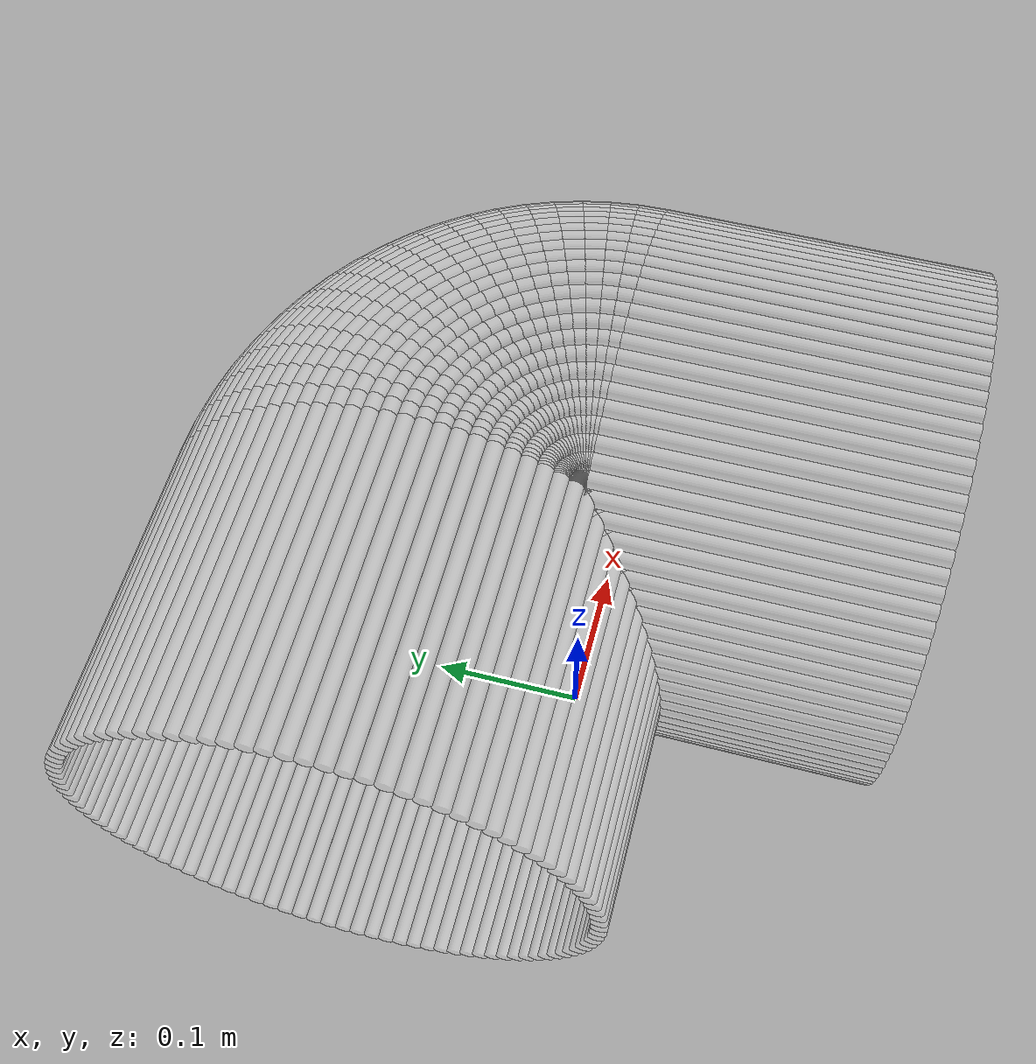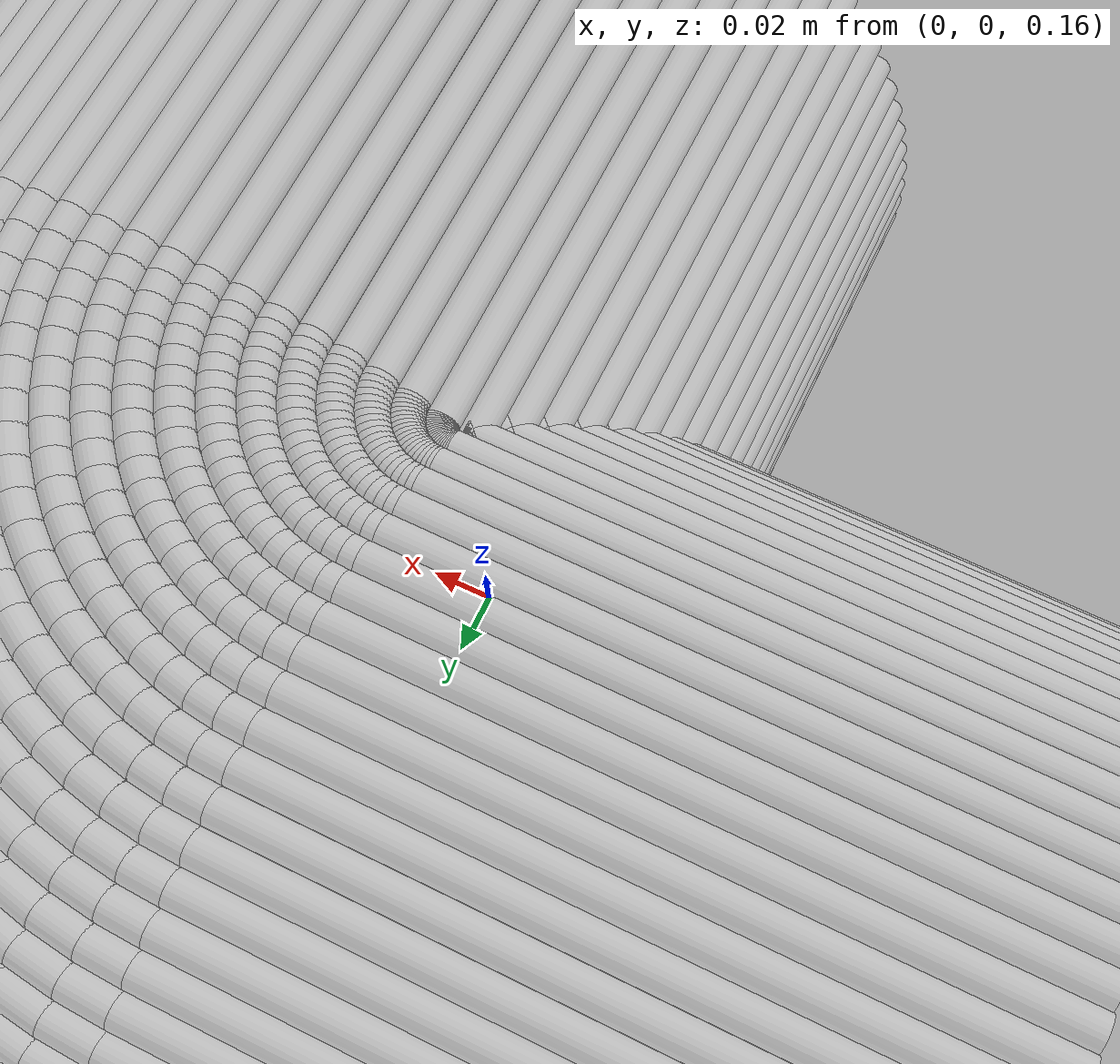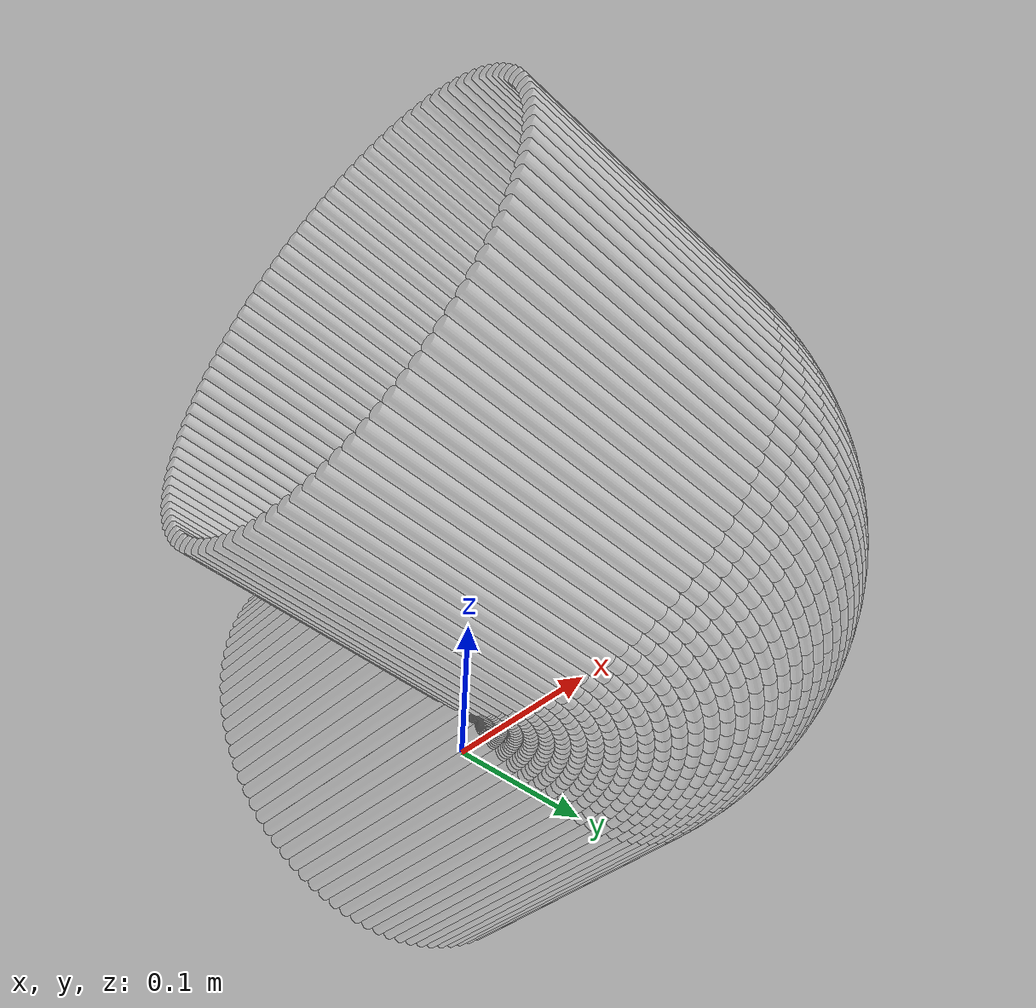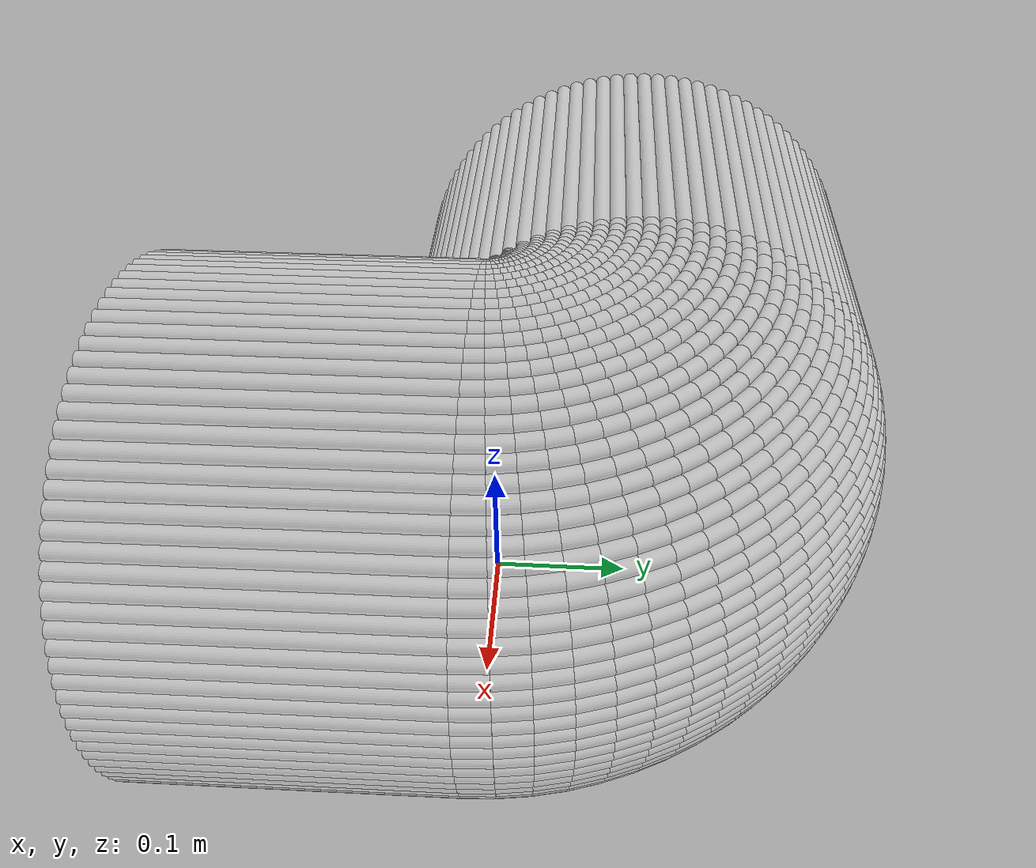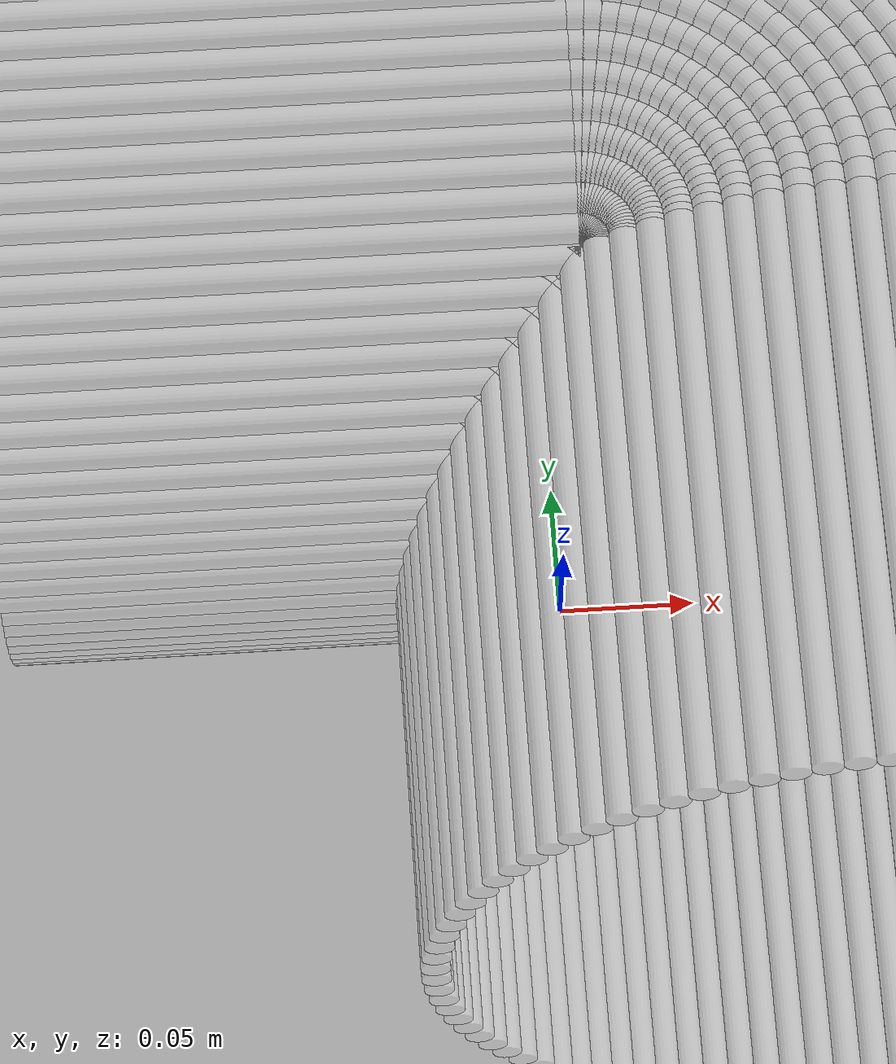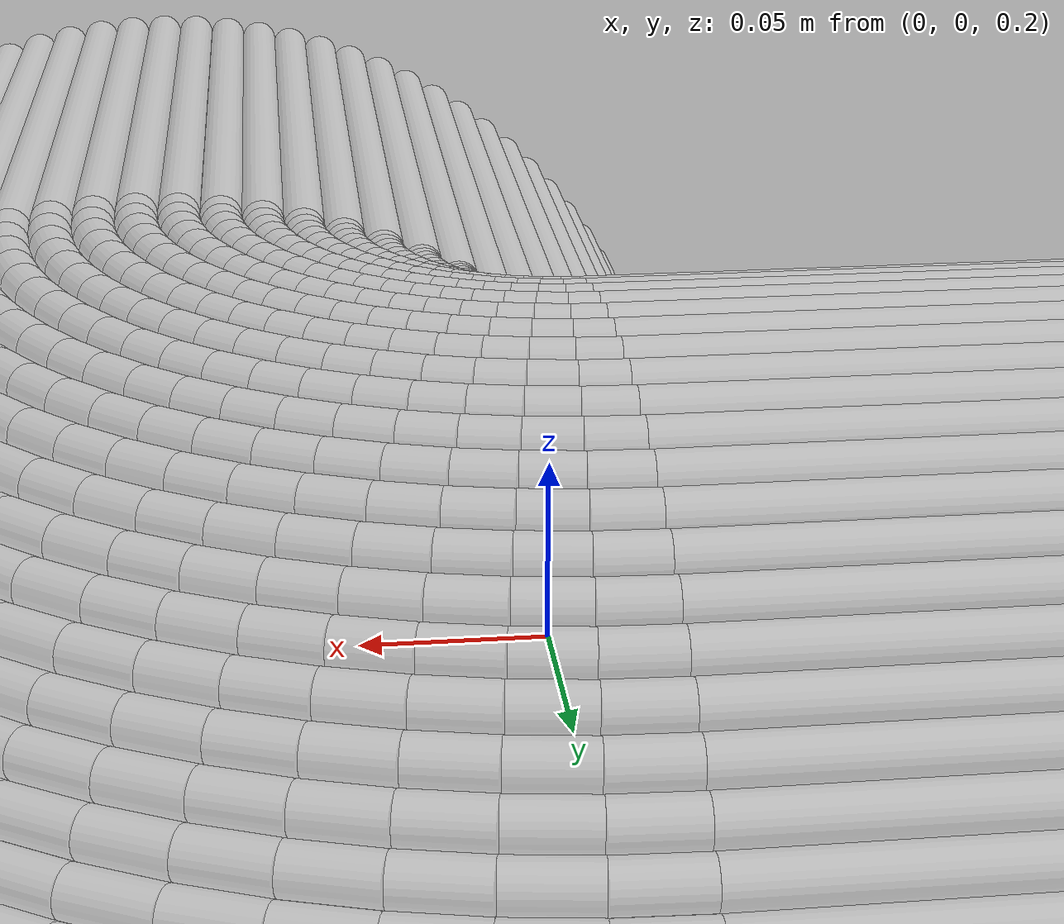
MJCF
<?xml version="1.0" encoding="utf-8"?>
<mujoco>
   <worldbody>
      <geom euler=" 0 10 0 " fromto="0.26 -0.2 0.16 0.26 0 0.16" rgba="1 1 1 0.35"
            size="0.0050257"
            type="cylinder"/>
      <geom euler=" 0 20 0 " fromto="0.25968 -0.2 0.17005 0.25968 0 0.17005"
            rgba="1 1 1 0.35"
            size="0.0050257"
            type="cylinder"/>
      <geom euler=" 0 30 0 " fromto="0.25874 -0.2 0.18005 0.25874 0 0.18005"
            rgba="1 1 1 0.35"
            size="0.0050257"
            type="cylinder"/>
      <geom euler=" 0 40 0 " fromto="0.25717 -0.2 0.18998 0.25717 0 0.18998"
            rgba="1 1 1 0.35"
            size="0.0050257"
            type="cylinder"/>
      <geom euler=" 0 50 0 " fromto="0.25497 -0.2 0.19979 0.25497 0 0.19979"
            rgba="1 1 1 0.35"
            size="0.0050257"
            type="cylinder"/>
      <geom euler=" 0 60 0 " fromto="0.25217 -0.2 0.20944 0.25217 0 0.20944"
            rgba="1 1 1 0.35"
            size="0.0050257"
            type="cylinder"/>
      <geom euler=" 0 70 0 " fromto="0.24876 -0.2 0.2189 0.24876 0 0.2189"
            rgba="1 1 1 0.35"
            size="0.0050257"
            type="cylinder"/>
      <geom euler=" 0 80 0 " fromto="0.24477 -0.2 0.22812 0.24477 0 0.22812"
            rgba="1 1 1 0.35"
            size="0.0050257"
            type="cylinder"/>
      <geom euler=" 0 90 0 " fromto="0.24021 -0.2 0.23708 0.24021 0 0.23708"
            rgba="1 1 1 0.35"
            size="0.0050257"
            type="cylinder"/>
      <geom euler=" 0 100 0 " fromto="0.23509 -0.2 0.24573 0.23509 0 0.24573"
            rgba="1 1 1 0.35"
            size="0.0050257"
            type="cylinder"/>
      <geom euler=" 0 110 0 " fromto="0.22944 -0.2 0.25405 0.22944 0 0.25405"
            rgba="1 1 1 0.35"
            size="0.0050257"
            type="cylinder"/>
      <geom euler=" 0 120 0 " fromto="0.22328 -0.2 0.26199 0.22328 0 0.26199"
            rgba="1 1 1 0.35"
            size="0.0050257"
            type="cylinder"/>
      <geom euler=" 0 130 0 " fromto="0.21663 -0.2 0.26953 0.21663 0 0.26953"
            rgba="1 1 1 0.35"
            size="0.0050257"
            type="cylinder"/>
      <geom euler=" 0 140 0 " fromto="0.20953 -0.2 0.27663 0.20953 0 0.27663"
            rgba="1 1 1 0.35"
            size="0.0050257"
            type="cylinder"/>
      <geom euler=" 0 150 0 " fromto="0.20199 -0.2 0.28328 0.20199 0 0.28328"
            rgba="1 1 1 0.35"
            size="0.0050257"
            type="cylinder"/>
      <geom euler=" 0 160 0 " fromto="0.19405 -0.2 0.28944 0.19405 0 0.28944"
            rgba="1 1 1 0.35"
            size="0.0050257"
            type="cylinder"/>
      <geom euler=" 0 170 0 " fromto="0.18573 -0.2 0.29509 0.18573 0 0.29509"
            rgba="1 1 1 0.35"
            size="0.0050257"
            type="cylinder"/>
      <geom euler=" 0 180 0 " fromto="0.17708 -0.2 0.30021 0.17708 0 0.30021"
            rgba="1 1 1 0.35"
            size="0.0050257"
            type="cylinder"/>
      <geom euler=" 0 190 0 " fromto="0.16812 -0.2 0.30477 0.16812 0 0.30477"
            rgba="1 1 1 0.35"
            size="0.0050257"
            type="cylinder"/>
      <geom euler=" 0 200 0 " fromto="0.1589 -0.2 0.30876 0.1589 0 0.30876"
            rgba="1 1 1 0.35"
            size="0.0050257"
            type="cylinder"/>
      <geom euler=" 0 210 0 " fromto="0.14944 -0.2 0.31217 0.14944 0 0.31217"
            rgba="1 1 1 0.35"
            size="0.0050257"
            type="cylinder"/>
      <geom euler=" 0 220 0 " fromto="0.13979 -0.2 0.31497 0.13979 0 0.31497"
            rgba="1 1 1 0.35"
            size="0.0050257"
            type="cylinder"/>
      <geom euler=" 0 230 0 " fromto="0.12998 -0.2 0.31717 0.12998 0 0.31717"
            rgba="1 1 1 0.35"
            size="0.0050257"
            type="cylinder"/>
      <geom euler=" 0 240 0 " fromto="0.12005 -0.2 0.31874 0.12005 0 0.31874"
            rgba="1 1 1 0.35"
            size="0.0050257"
            type="cylinder"/>
      <geom euler=" 0 250 0 " fromto="0.11005 -0.2 0.31968 0.11005 0 0.31968"
            rgba="1 1 1 0.35"
            size="0.0050257"
            type="cylinder"/>
      <geom euler=" 0 260 0 " fromto="0.1 -0.2 0.32 0.1 0 0.32" rgba="1 1 1 0.35"
            size="0.0050257"
            type="cylinder"/>
      <geom euler=" 0 270 0 " fromto="0.089954 -0.2 0.31968 0.089954 0 0.31968"
            rgba="1 1 1 0.35"
            size="0.0050257"
            type="cylinder"/>
      <geom euler=" 0 280 0 " fromto="0.079947 -0.2 0.31874 0.079947 0 0.31874"
            rgba="1 1 1 0.35"
            size="0.0050257"
            type="cylinder"/>
      <geom euler=" 0 290 0 " fromto="0.070019 -0.2 0.31717 0.070019 0 0.31717"
            rgba="1 1 1 0.35"
            size="0.0050257"
            type="cylinder"/>
      <geom euler=" 0 300 0 " fromto="0.06021 -0.2 0.31497 0.06021 0 0.31497"
            rgba="1 1 1 0.35"
            size="0.0050257"
            type="cylinder"/>
      <geom euler=" 0 310 0 " fromto="0.050557 -0.2 0.31217 0.050557 0 0.31217"
            rgba="1 1 1 0.35"
            size="0.0050257"
            type="cylinder"/>
      <geom euler=" 0 320 0 " fromto="0.0411 -0.2 0.30876 0.0411 0 0.30876"
            rgba="1 1 1 0.35"
            size="0.0050257"
            type="cylinder"/>
      <geom euler=" 0 330 0 " fromto="0.031875 -0.2 0.30477 0.031875 0 0.30477"
            rgba="1 1 1 0.35"
            size="0.0050257"
            type="cylinder"/>
      <geom euler=" 0 340 0 " fromto="0.022919 -0.2 0.30021 0.022919 0 0.30021"
            rgba="1 1 1 0.35"
            size="0.0050257"
            type="cylinder"/>
      <geom euler=" 0 350 0 " fromto="0.014268 -0.2 0.29509 0.014268 0 0.29509"
            rgba="1 1 1 0.35"
            size="0.0050257"
            type="cylinder"/>
      <geom euler=" 0 360 0 " fromto="0.0059544 -0.2 0.28944 0.0059544 0 0.28944"
            rgba="1 1 1 0.35"
            size="0.0050257"
            type="cylinder"/>
      <geom euler=" 0 370 0 " fromto="-0.0019878 -0.2 0.28328 -0.0019878 0 0.28328"
            rgba="1 1 1 0.35"
            size="0.0050257"
            type="cylinder"/>
      <geom euler=" 0 380 0 " fromto="-0.0095275 -0.2 0.27663 -0.0095275 0 0.27663"
            rgba="1 1 1 0.35"
            size="0.0050257"
            type="cylinder"/>
      <geom euler=" 0 390 0 " fromto="-0.016635 -0.2 0.26953 -0.016635 0 0.26953"
            rgba="1 1 1 0.35"
            size="0.0050257"
            type="cylinder"/>
      <geom euler=" 0 400 0 " fromto="-0.023282 -0.2 0.26199 -0.023282 0 0.26199"
            rgba="1 1 1 0.35"
            size="0.0050257"
            type="cylinder"/>
      <geom euler=" 0 410 0 " fromto="-0.029443 -0.2 0.25405 -0.029443 0 0.25405"
            rgba="1 1 1 0.35"
            size="0.0050257"
            type="cylinder"/>
      <geom euler=" 0 420 0 " fromto="-0.035092 -0.2 0.24573 -0.035092 0 0.24573"
            rgba="1 1 1 0.35"
            size="0.0050257"
            type="cylinder"/>
      <geom euler=" 0 430 0 " fromto="-0.040209 -0.2 0.23708 -0.040209 0 0.23708"
            rgba="1 1 1 0.35"
            size="0.0050257"
            type="cylinder"/>
      <geom euler=" 0 440 0 " fromto="-0.044772 -0.2 0.22812 -0.044772 0 0.22812"
            rgba="1 1 1 0.35"
            size="0.0050257"
            type="cylinder"/>
      <geom euler=" 0 450 0 " fromto="-0.048764 -0.2 0.2189 -0.048764 0 0.2189"
            rgba="1 1 1 0.35"
            size="0.0050257"
            type="cylinder"/>
      <geom euler=" 0 460 0 " fromto="-0.052169 -0.2 0.20944 -0.052169 0 0.20944"
            rgba="1 1 1 0.35"
            size="0.0050257"
            type="cylinder"/>
      <geom euler=" 0 470 0 " fromto="-0.054973 -0.2 0.19979 -0.054973 0 0.19979"
            rgba="1 1 1 0.35"
            size="0.0050257"
            type="cylinder"/>
      <geom euler=" 0 480 0 " fromto="-0.057166 -0.2 0.18998 -0.057166 0 0.18998"
            rgba="1 1 1 0.35"
            size="0.0050257"
            type="cylinder"/>
      <geom euler=" 0 490 0 " fromto="-0.058738 -0.2 0.18005 -0.058738 0 0.18005"
            rgba="1 1 1 0.35"
            size="0.0050257"
            type="cylinder"/>
      <geom euler=" 0 500 0 " fromto="-0.059684 -0.2 0.17005 -0.059684 0 0.17005"
            rgba="1 1 1 0.35"
            size="0.0050257"
            type="cylinder"/>
      <geom euler=" 0 510 0 " fromto="-0.06 -0.2 0.16 -0.06 0 0.16" rgba="1 1 1 0.35"
            size="0.0050257"
            type="cylinder"/>
      <geom euler=" 0 520 0 " fromto="-0.059684 -0.2 0.14995 -0.059684 0 0.14995"
            rgba="1 1 1 0.35"
            size="0.0050257"
            type="cylinder"/>
      <geom euler=" 0 530 0 " fromto="-0.058738 -0.2 0.13995 -0.058738 0 0.13995"
            rgba="1 1 1 0.35"
            size="0.0050257"
            type="cylinder"/>
      <geom euler=" 0 540 0 " fromto="-0.057166 -0.2 0.13002 -0.057166 0 0.13002"
            rgba="1 1 1 0.35"
            size="0.0050257"
            type="cylinder"/>
      <geom euler=" 0 550 0 " fromto="-0.054973 -0.2 0.12021 -0.054973 0 0.12021"
            rgba="1 1 1 0.35"
            size="0.0050257"
            type="cylinder"/>
      <geom euler=" 0 560 0 " fromto="-0.052169 -0.2 0.11056 -0.052169 0 0.11056"
            rgba="1 1 1 0.35"
            size="0.0050257"
            type="cylinder"/>
      <geom euler=" 0 570 0 " fromto="-0.048764 -0.2 0.1011 -0.048764 0 0.1011"
            rgba="1 1 1 0.35"
            size="0.0050257"
            type="cylinder"/>
      <geom euler=" 0 580 0 " fromto="-0.044772 -0.2 0.091875 -0.044772 0 0.091875"
            rgba="1 1 1 0.35"
            size="0.0050257"
            type="cylinder"/>
      <geom euler=" 0 590 0 " fromto="-0.040209 -0.2 0.082919 -0.040209 0 0.082919"
            rgba="1 1 1 0.35"
            size="0.0050257"
            type="cylinder"/>
      <geom euler=" 0 600 0 " fromto="-0.035092 -0.2 0.074268 -0.035092 0 0.074268"
            rgba="1 1 1 0.35"
            size="0.0050257"
            type="cylinder"/>
      <geom euler=" 0 610 0 " fromto="-0.029443 -0.2 0.065954 -0.029443 0 0.065954"
            rgba="1 1 1 0.35"
            size="0.0050257"
            type="cylinder"/>
      <geom euler=" 0 620 0 " fromto="-0.023282 -0.2 0.058012 -0.023282 0 0.058012"
            rgba="1 1 1 0.35"
            size="0.0050257"
            type="cylinder"/>
      <geom euler=" 0 630 0 " fromto="-0.016635 -0.2 0.050472 -0.016635 0 0.050472"
            rgba="1 1 1 0.35"
            size="0.0050257"
            type="cylinder"/>
      <geom euler=" 0 640 0 " fromto="-0.0095275 -0.2 0.043365 -0.0095275 0 0.043365"
            rgba="1 1 1 0.35"
            size="0.0050257"
            type="cylinder"/>
      <geom euler=" 0 650 0 " fromto="-0.0019878 -0.2 0.036718 -0.0019878 0 0.036718"
            rgba="1 1 1 0.35"
            size="0.0050257"
            type="cylinder"/>
      <geom euler=" 0 660 0 " fromto="0.0059544 -0.2 0.030557 0.0059544 0 0.030557"
            rgba="1 1 1 0.35"
            size="0.0050257"
            type="cylinder"/>
      <geom euler=" 0 670 0 " fromto="0.014268 -0.2 0.024908 0.014268 0 0.024908"
            rgba="1 1 1 0.35"
            size="0.0050257"
            type="cylinder"/>
      <geom euler=" 0 680 0 " fromto="0.022919 -0.2 0.019791 0.022919 0 0.019791"
            rgba="1 1 1 0.35"
            size="0.0050257"
            type="cylinder"/>
      <geom euler=" 0 690 0 " fromto="0.031875 -0.2 0.015228 0.031875 0 0.015228"
            rgba="1 1 1 0.35"
            size="0.0050257"
            type="cylinder"/>
      <geom euler=" 0 700 0 " fromto="0.0411 -0.2 0.011236 0.0411 0 0.011236"
            rgba="1 1 1 0.35"
            size="0.0050257"
            type="cylinder"/>
      <geom euler=" 0 710 0 " fromto="0.050557 -0.2 0.007831 0.050557 0 0.007831"
            rgba="1 1 1 0.35"
            size="0.0050257"
            type="cylinder"/>
      <geom euler=" 0 720 0 " fromto="0.06021 -0.2 0.0050267 0.06021 0 0.0050267"
            rgba="1 1 1 0.35"
            size="0.0050257"
            type="cylinder"/>
      <geom euler=" 0 730 0 " fromto="0.070019 -0.2 0.002834 0.070019 0 0.002834"
            rgba="1 1 1 0.35"
            size="0.0050257"
            type="cylinder"/>
      <geom euler=" 0 740 0 " fromto="0.079947 -0.2 0.0012616 0.079947 0 0.0012616"
            rgba="1 1 1 0.35"
            size="0.0050257"
            type="cylinder"/>
      <geom euler=" 0 750 0 " fromto="0.089954 -0.2 0.00031572 0.089954 0 0.00031572"
            rgba="1 1 1 0.35"
            size="0.0050257"
            type="cylinder"/>
      <geom euler=" 0 760 0 " fromto="0.1 -0.2 0 0.1 0 0" rgba="1 1 1 0.35"
            size="0.0050257"
            type="cylinder"/>
      <geom euler=" 0 770 0 " fromto="0.11005 -0.2 0.00031572 0.11005 0 0.00031572"
            rgba="1 1 1 0.35"
            size="0.0050257"
            type="cylinder"/>
      <geom euler=" 0 780 0 " fromto="0.12005 -0.2 0.0012616 0.12005 0 0.0012616"
            rgba="1 1 1 0.35"
            size="0.0050257"
            type="cylinder"/>
      <geom euler=" 0 790 0 " fromto="0.12998 -0.2 0.002834 0.12998 0 0.002834"
            rgba="1 1 1 0.35"
            size="0.0050257"
            type="cylinder"/>
      <geom euler=" 0 800 0 " fromto="0.13979 -0.2 0.0050267 0.13979 0 0.0050267"
            rgba="1 1 1 0.35"
            size="0.0050257"
            type="cylinder"/>
      <geom euler=" 0 810 0 " fromto="0.14944 -0.2 0.007831 0.14944 0 0.007831"
            rgba="1 1 1 0.35"
            size="0.0050257"
            type="cylinder"/>
      <geom euler=" 0 820 0 " fromto="0.1589 -0.2 0.011236 0.1589 0 0.011236"
            rgba="1 1 1 0.35"
            size="0.0050257"
            type="cylinder"/>
      <geom euler=" 0 830 0 " fromto="0.16812 -0.2 0.015228 0.16812 0 0.015228"
            rgba="1 1 1 0.35"
            size="0.0050257"
            type="cylinder"/>
      <geom euler=" 0 840 0 " fromto="0.17708 -0.2 0.019791 0.17708 0 0.019791"
            rgba="1 1 1 0.35"
            size="0.0050257"
            type="cylinder"/>
      <geom euler=" 0 850 0 " fromto="0.18573 -0.2 0.024908 0.18573 0 0.024908"
            rgba="1 1 1 0.35"
            size="0.0050257"
            type="cylinder"/>
      <geom euler=" 0 860 0 " fromto="0.19405 -0.2 0.030557 0.19405 0 0.030557"
            rgba="1 1 1 0.35"
            size="0.0050257"
            type="cylinder"/>
      <geom euler=" 0 870 0 " fromto="0.20199 -0.2 0.036718 0.20199 0 0.036718"
            rgba="1 1 1 0.35"
            size="0.0050257"
            type="cylinder"/>
      <geom euler=" 0 880 0 " fromto="0.20953 -0.2 0.043365 0.20953 0 0.043365"
            rgba="1 1 1 0.35"
            size="0.0050257"
            type="cylinder"/>
      <geom euler=" 0 890 0 " fromto="0.21663 -0.2 0.050472 0.21663 0 0.050472"
            rgba="1 1 1 0.35"
            size="0.0050257"
            type="cylinder"/>
      <geom euler=" 0 900 0 " fromto="0.22328 -0.2 0.058012 0.22328 0 0.058012"
            rgba="1 1 1 0.35"
            size="0.0050257"
            type="cylinder"/>
      <geom euler=" 0 910 0 " fromto="0.22944 -0.2 0.065954 0.22944 0 0.065954"
            rgba="1 1 1 0.35"
            size="0.0050257"
            type="cylinder"/>
      <geom euler=" 0 920 0 " fromto="0.23509 -0.2 0.074268 0.23509 0 0.074268"
            rgba="1 1 1 0.35"
            size="0.0050257"
            type="cylinder"/>
      <geom euler=" 0 930 0 " fromto="0.24021 -0.2 0.082919 0.24021 0 0.082919"
            rgba="1 1 1 0.35"
            size="0.0050257"
            type="cylinder"/>
      <geom euler=" 0 940 0 " fromto="0.24477 -0.2 0.091875 0.24477 0 0.091875"
            rgba="1 1 1 0.35"
            size="0.0050257"
            type="cylinder"/>
      <geom euler=" 0 950 0 " fromto="0.24876 -0.2 0.1011 0.24876 0 0.1011"
            rgba="1 1 1 0.35"
            size="0.0050257"
            type="cylinder"/>
      <geom euler=" 0 960 0 " fromto="0.25217 -0.2 0.11056 0.25217 0 0.11056"
            rgba="1 1 1 0.35"
            size="0.0050257"
            type="cylinder"/>
      <geom euler=" 0 970 0 " fromto="0.25497 -0.2 0.12021 0.25497 0 0.12021"
            rgba="1 1 1 0.35"
            size="0.0050257"
            type="cylinder"/>
      <geom euler=" 0 980 0 " fromto="0.25717 -0.2 0.13002 0.25717 0 0.13002"
            rgba="1 1 1 0.35"
            size="0.0050257"
            type="cylinder"/>
      <geom euler=" 0 990 0 " fromto="0.25874 -0.2 0.13995 0.25874 0 0.13995"
            rgba="1 1 1 0.35"
            size="0.0050257"
            type="cylinder"/>
      <geom euler=" 0 1000 0 " fromto="0.25968 -0.2 0.14995 0.25968 0 0.14995"
            rgba="1 1 1 0.35"
            size="0.0050257"
            type="cylinder"/>
      <geom euler=" 0 10 0 " fromto="0.26 0 0.16 0.25911 0.021471 0.16" rgba="1 1 1 0.35"
            size="0.0050257"
            type="cylinder"/>
      <geom euler=" 0 20 0 " fromto="0.25968 0 0.17005 0.2588 0.021445 0.17005"
            rgba="1 1 1 0.35"
            size="0.0050257"
            type="cylinder"/>
      <geom euler=" 0 30 0 " fromto="0.25874 0 0.18005 0.25785 0.021366 0.18005"
            rgba="1 1 1 0.35"
            size="0.0050257"
            type="cylinder"/>
      <geom euler=" 0 40 0 " fromto="0.25717 0 0.18998 0.25629 0.021237 0.18998"
            rgba="1 1 1 0.35"
            size="0.0050257"
            type="cylinder"/>
      <geom euler=" 0 50 0 " fromto="0.25497 0 0.19979 0.2541 0.021056 0.19979"
            rgba="1 1 1 0.35"
            size="0.0050257"
            type="cylinder"/>
      <geom euler=" 0 60 0 " fromto="0.25217 0 0.20944 0.25131 0.020824 0.20944"
            rgba="1 1 1 0.35"
            size="0.0050257"
            type="cylinder"/>
      <geom euler=" 0 70 0 " fromto="0.24876 0 0.2189 0.24791 0.020543 0.2189"
            rgba="1 1 1 0.35"
            size="0.0050257"
            type="cylinder"/>
      <geom euler=" 0 80 0 " fromto="0.24477 0 0.22812 0.24394 0.020213 0.22812"
            rgba="1 1 1 0.35"
            size="0.0050257"
            type="cylinder"/>
      <geom euler=" 0 90 0 " fromto="0.24021 0 0.23708 0.23939 0.019836 0.23708"
            rgba="1 1 1 0.35"
            size="0.0050257"
            type="cylinder"/>
      <geom euler=" 0 100 0 " fromto="0.23509 0 0.24573 0.23429 0.019414 0.24573"
            rgba="1 1 1 0.35"
            size="0.0050257"
            type="cylinder"/>
      <geom euler=" 0 110 0 " fromto="0.22944 0 0.25405 0.22866 0.018947 0.25405"
            rgba="1 1 1 0.35"
            size="0.0050257"
            type="cylinder"/>
      <geom euler=" 0 120 0 " fromto="0.22328 0 0.26199 0.22252 0.018438 0.26199"
            rgba="1 1 1 0.35"
            size="0.0050257"
            type="cylinder"/>
      <geom euler=" 0 130 0 " fromto="0.21663 0 0.26953 0.2159 0.01789 0.26953"
            rgba="1 1 1 0.35"
            size="0.0050257"
            type="cylinder"/>
      <geom euler=" 0 140 0 " fromto="0.20953 0 0.27663 0.20881 0.017303 0.27663"
            rgba="1 1 1 0.35"
            size="0.0050257"
            type="cylinder"/>
      <geom euler=" 0 150 0 " fromto="0.20199 0 0.28328 0.2013 0.01668 0.28328"
            rgba="1 1 1 0.35"
            size="0.0050257"
            type="cylinder"/>
      <geom euler=" 0 160 0 " fromto="0.19405 0 0.28944 0.19338 0.016024 0.28944"
            rgba="1 1 1 0.35"
            size="0.0050257"
            type="cylinder"/>
      <geom euler=" 0 170 0 " fromto="0.18573 0 0.29509 0.1851 0.015338 0.29509"
            rgba="1 1 1 0.35"
            size="0.0050257"
            type="cylinder"/>
      <geom euler=" 0 180 0 " fromto="0.17708 0 0.30021 0.17648 0.014623 0.30021"
            rgba="1 1 1 0.35"
            size="0.0050257"
            type="cylinder"/>
      <geom euler=" 0 190 0 " fromto="0.16812 0 0.30477 0.16755 0.013884 0.30477"
            rgba="1 1 1 0.35"
            size="0.0050257"
            type="cylinder"/>
      <geom euler=" 0 200 0 " fromto="0.1589 0 0.30876 0.15836 0.013122 0.30876"
            rgba="1 1 1 0.35"
            size="0.0050257"
            type="cylinder"/>
      <geom euler=" 0 210 0 " fromto="0.14944 0 0.31217 0.14893 0.012341 0.31217"
            rgba="1 1 1 0.35"
            size="0.0050257"
            type="cylinder"/>
      <geom euler=" 0 220 0 " fromto="0.13979 0 0.31497 0.13931 0.011544 0.31497"
            rgba="1 1 1 0.35"
            size="0.0050257"
            type="cylinder"/>
      <geom euler=" 0 230 0 " fromto="0.12998 0 0.31717 0.12954 0.010734 0.31717"
            rgba="1 1 1 0.35"
            size="0.0050257"
            type="cylinder"/>
      <geom euler=" 0 240 0 " fromto="0.12005 0 0.31874 0.11964 0.0099139 0.31874"
            rgba="1 1 1 0.35"
            size="0.0050257"
            type="cylinder"/>
      <geom euler=" 0 250 0 " fromto="0.11005 0 0.31968 0.10967 0.0090876 0.31968"
            rgba="1 1 1 0.35"
            size="0.0050257"
            type="cylinder"/>
      <geom euler=" 0 260 0 " fromto="0.1 0 0.32 0.099658 0.0082579 0.32" rgba="1 1 1 0.35"
            size="0.0050257"
            type="cylinder"/>
      <geom euler=" 0 270 0 " fromto="0.089954 0 0.31968 0.089646 0.0074283 0.31968"
            rgba="1 1 1 0.35"
            size="0.0050257"
            type="cylinder"/>
      <geom euler=" 0 280 0 " fromto="0.079947 0 0.31874 0.079674 0.0066019 0.31874"
            rgba="1 1 1 0.35"
            size="0.0050257"
            type="cylinder"/>
      <geom euler=" 0 290 0 " fromto="0.070019 0 0.31717 0.06978 0.0057821 0.31717"
            rgba="1 1 1 0.35"
            size="0.0050257"
            type="cylinder"/>
      <geom euler=" 0 300 0 " fromto="0.06021 0 0.31497 0.060004 0.0049721 0.31497"
            rgba="1 1 1 0.35"
            size="0.0050257"
            type="cylinder"/>
      <geom euler=" 0 310 0 " fromto="0.050557 0 0.31217 0.050385 0.004175 0.31217"
            rgba="1 1 1 0.35"
            size="0.0050257"
            type="cylinder"/>
      <geom euler=" 0 320 0 " fromto="0.0411 0 0.30876 0.04096 0.003394 0.30876"
            rgba="1 1 1 0.35"
            size="0.0050257"
            type="cylinder"/>
      <geom euler=" 0 330 0 " fromto="0.031875 0 0.30477 0.031766 0.0026322 0.30477"
            rgba="1 1 1 0.35"
            size="0.0050257"
            type="cylinder"/>
      <geom euler=" 0 340 0 " fromto="0.022919 0 0.30021 0.022841 0.0018927 0.30021"
            rgba="1 1 1 0.35"
            size="0.0050257"
            type="cylinder"/>
      <geom euler=" 0 350 0 " fromto="0.014268 0 0.29509 0.014219 0.0011782 0.29509"
            rgba="1 1 1 0.35"
            size="0.0050257"
            type="cylinder"/>
      <geom euler=" 0 360 0 " fromto="0.0059544 0 0.28944 0.005934 0.00049171 0.28944"
            rgba="1 1 1 0.35"
            size="0.0050257"
            type="cylinder"/>
      <geom euler=" 0 370 0 " fromto="-0.0019878 0 0.28328 -0.001981 -0.00016415 0.28328"
            rgba="1 1 1 0.35"
            size="0.0050257"
            type="cylinder"/>
      <geom euler=" 0 380 0 " fromto="-0.0095275 0 0.27663 -0.009495 -0.00078678 0.27663"
            rgba="1 1 1 0.35"
            size="0.0050257"
            type="cylinder"/>
      <geom euler=" 0 390 0 " fromto="-0.016635 0 0.26953 -0.016578 -0.0013737 0.26953"
            rgba="1 1 1 0.35"
            size="0.0050257"
            type="cylinder"/>
      <geom euler=" 0 400 0 " fromto="-0.023282 0 0.26199 -0.023203 -0.0019226 0.26199"
            rgba="1 1 1 0.35"
            size="0.0050257"
            type="cylinder"/>
      <geom euler=" 0 410 0 " fromto="-0.029443 0 0.25405 -0.029342 -0.0024314 0.25405"
            rgba="1 1 1 0.35"
            size="0.0050257"
            type="cylinder"/>
      <geom euler=" 0 420 0 " fromto="-0.035092 0 0.24573 -0.034973 -0.0028979 0.24573"
            rgba="1 1 1 0.35"
            size="0.0050257"
            type="cylinder"/>
      <geom euler=" 0 430 0 " fromto="-0.040209 0 0.23708 -0.040072 -0.0033204 0.23708"
            rgba="1 1 1 0.35"
            size="0.0050257"
            type="cylinder"/>
      <geom euler=" 0 440 0 " fromto="-0.044772 0 0.22812 -0.044619 -0.0036973 0.22812"
            rgba="1 1 1 0.35"
            size="0.0050257"
            type="cylinder"/>
      <geom euler=" 0 450 0 " fromto="-0.048764 0 0.2189 -0.048598 -0.0040269 0.2189"
            rgba="1 1 1 0.35"
            size="0.0050257"
            type="cylinder"/>
      <geom euler=" 0 460 0 " fromto="-0.052169 0 0.20944 -0.051991 -0.0043081 0.20944"
            rgba="1 1 1 0.35"
            size="0.0050257"
            type="cylinder"/>
      <geom euler=" 0 470 0 " fromto="-0.054973 0 0.19979 -0.054786 -0.0045397 0.19979"
            rgba="1 1 1 0.35"
            size="0.0050257"
            type="cylinder"/>
      <geom euler=" 0 480 0 " fromto="-0.057166 0 0.18998 -0.056971 -0.0047207 0.18998"
            rgba="1 1 1 0.35"
            size="0.0050257"
            type="cylinder"/>
      <geom euler=" 0 490 0 " fromto="-0.058738 0 0.18005 -0.058538 -0.0048506 0.18005"
            rgba="1 1 1 0.35"
            size="0.0050257"
            type="cylinder"/>
      <geom euler=" 0 500 0 " fromto="-0.059684 0 0.17005 -0.05948 -0.0049287 0.17005"
            rgba="1 1 1 0.35"
            size="0.0050257"
            type="cylinder"/>
      <geom euler=" 0 510 0 " fromto="-0.06 0 0.16 -0.059795 -0.0049548 0.16"
            rgba="1 1 1 0.35"
            size="0.0050257"
            type="cylinder"/>
      <geom euler=" 0 520 0 " fromto="-0.059684 0 0.14995 -0.05948 -0.0049287 0.14995"
            rgba="1 1 1 0.35"
            size="0.0050257"
            type="cylinder"/>
      <geom euler=" 0 530 0 " fromto="-0.058738 0 0.13995 -0.058538 -0.0048506 0.13995"
            rgba="1 1 1 0.35"
            size="0.0050257"
            type="cylinder"/>
      <geom euler=" 0 540 0 " fromto="-0.057166 0 0.13002 -0.056971 -0.0047207 0.13002"
            rgba="1 1 1 0.35"
            size="0.0050257"
            type="cylinder"/>
      <geom euler=" 0 550 0 " fromto="-0.054973 0 0.12021 -0.054786 -0.0045397 0.12021"
            rgba="1 1 1 0.35"
            size="0.0050257"
            type="cylinder"/>
      <geom euler=" 0 560 0 " fromto="-0.052169 0 0.11056 -0.051991 -0.0043081 0.11056"
            rgba="1 1 1 0.35"
            size="0.0050257"
            type="cylinder"/>
      <geom euler=" 0 570 0 " fromto="-0.048764 0 0.1011 -0.048598 -0.0040269 0.1011"
            rgba="1 1 1 0.35"
            size="0.0050257"
            type="cylinder"/>
      <geom euler=" 0 580 0 " fromto="-0.044772 0 0.091875 -0.044619 -0.0036973 0.091875"
            rgba="1 1 1 0.35"
            size="0.0050257"
            type="cylinder"/>
      <geom euler=" 0 590 0 " fromto="-0.040209 0 0.082919 -0.040072 -0.0033204 0.082919"
            rgba="1 1 1 0.35"
            size="0.0050257"
            type="cylinder"/>
      <geom euler=" 0 600 0 " fromto="-0.035092 0 0.074268 -0.034973 -0.0028979 0.074268"
            rgba="1 1 1 0.35"
            size="0.0050257"
            type="cylinder"/>
      <geom euler=" 0 610 0 " fromto="-0.029443 0 0.065954 -0.029342 -0.0024314 0.065954"
            rgba="1 1 1 0.35"
            size="0.0050257"
            type="cylinder"/>
      <geom euler=" 0 620 0 " fromto="-0.023282 0 0.058012 -0.023203 -0.0019226 0.058012"
            rgba="1 1 1 0.35"
            size="0.0050257"
            type="cylinder"/>
      <geom euler=" 0 630 0 " fromto="-0.016635 0 0.050472 -0.016578 -0.0013737 0.050472"
            rgba="1 1 1 0.35"
            size="0.0050257"
            type="cylinder"/>
      <geom euler=" 0 640 0 " fromto="-0.0095275 0 0.043365 -0.009495 -0.00078678 0.043365"
            rgba="1 1 1 0.35"
            size="0.0050257"
            type="cylinder"/>
      <geom euler=" 0 650 0 " fromto="-0.0019878 0 0.036718 -0.001981 -0.00016415 0.036718"
            rgba="1 1 1 0.35"
            size="0.0050257"
            type="cylinder"/>
      <geom euler=" 0 660 0 " fromto="0.0059544 0 0.030557 0.005934 0.00049171 0.030557"
            rgba="1 1 1 0.35"
            size="0.0050257"
            type="cylinder"/>
      <geom euler=" 0 670 0 " fromto="0.014268 0 0.024908 0.014219 0.0011782 0.024908"
            rgba="1 1 1 0.35"
            size="0.0050257"
            type="cylinder"/>
      <geom euler=" 0 680 0 " fromto="0.022919 0 0.019791 0.022841 0.0018927 0.019791"
            rgba="1 1 1 0.35"
            size="0.0050257"
            type="cylinder"/>
      <geom euler=" 0 690 0 " fromto="0.031875 0 0.015228 0.031766 0.0026322 0.015228"
            rgba="1 1 1 0.35"
            size="0.0050257"
            type="cylinder"/>
      <geom euler=" 0 700 0 " fromto="0.0411 0 0.011236 0.04096 0.003394 0.011236"
            rgba="1 1 1 0.35"
            size="0.0050257"
            type="cylinder"/>
      <geom euler=" 0 710 0 " fromto="0.050557 0 0.007831 0.050385 0.004175 0.007831"
            rgba="1 1 1 0.35"
            size="0.0050257"
            type="cylinder"/>
      <geom euler=" 0 720 0 " fromto="0.06021 0 0.0050267 0.060004 0.0049721 0.0050267"
            rgba="1 1 1 0.35"
            size="0.0050257"
            type="cylinder"/>
      <geom euler=" 0 730 0 " fromto="0.070019 0 0.002834 0.06978 0.0057821 0.002834"
            rgba="1 1 1 0.35"
            size="0.0050257"
            type="cylinder"/>
      <geom euler=" 0 740 0 " fromto="0.079947 0 0.0012616 0.079674 0.0066019 0.0012616"
            rgba="1 1 1 0.35"
            size="0.0050257"
            type="cylinder"/>
      <geom euler=" 0 750 0 " fromto="0.089954 0 0.00031572 0.089646 0.0074283 0.00031572"
            rgba="1 1 1 0.35"
            size="0.0050257"
            type="cylinder"/>
      <geom euler=" 0 760 0 " fromto="0.1 0 0 0.099658 0.0082579 0" rgba="1 1 1 0.35"
            size="0.0050257"
            type="cylinder"/>
      <geom euler=" 0 770 0 " fromto="0.11005 0 0.00031572 0.10967 0.0090876 0.00031572"
            rgba="1 1 1 0.35"
            size="0.0050257"
            type="cylinder"/>
      <geom euler=" 0 780 0 " fromto="0.12005 0 0.0012616 0.11964 0.0099139 0.0012616"
            rgba="1 1 1 0.35"
            size="0.0050257"
            type="cylinder"/>
      <geom euler=" 0 790 0 " fromto="0.12998 0 0.002834 0.12954 0.010734 0.002834"
            rgba="1 1 1 0.35"
            size="0.0050257"
            type="cylinder"/>
      <geom euler=" 0 800 0 " fromto="0.13979 0 0.0050267 0.13931 0.011544 0.0050267"
            rgba="1 1 1 0.35"
            size="0.0050257"
            type="cylinder"/>
      <geom euler=" 0 810 0 " fromto="0.14944 0 0.007831 0.14893 0.012341 0.007831"
            rgba="1 1 1 0.35"
            size="0.0050257"
            type="cylinder"/>
      <geom euler=" 0 820 0 " fromto="0.1589 0 0.011236 0.15836 0.013122 0.011236"
            rgba="1 1 1 0.35"
            size="0.0050257"
            type="cylinder"/>
      <geom euler=" 0 830 0 " fromto="0.16812 0 0.015228 0.16755 0.013884 0.015228"
            rgba="1 1 1 0.35"
            size="0.0050257"
            type="cylinder"/>
      <geom euler=" 0 840 0 " fromto="0.17708 0 0.019791 0.17648 0.014623 0.019791"
            rgba="1 1 1 0.35"
            size="0.0050257"
            type="cylinder"/>
      <geom euler=" 0 850 0 " fromto="0.18573 0 0.024908 0.1851 0.015338 0.024908"
            rgba="1 1 1 0.35"
            size="0.0050257"
            type="cylinder"/>
      <geom euler=" 0 860 0 " fromto="0.19405 0 0.030557 0.19338 0.016024 0.030557"
            rgba="1 1 1 0.35"
            size="0.0050257"
            type="cylinder"/>
      <geom euler=" 0 870 0 " fromto="0.20199 0 0.036718 0.2013 0.01668 0.036718"
            rgba="1 1 1 0.35"
            size="0.0050257"
            type="cylinder"/>
      <geom euler=" 0 880 0 " fromto="0.20953 0 0.043365 0.20881 0.017303 0.043365"
            rgba="1 1 1 0.35"
            size="0.0050257"
            type="cylinder"/>
      <geom euler=" 0 890 0 " fromto="0.21663 0 0.050472 0.2159 0.01789 0.050472"
            rgba="1 1 1 0.35"
            size="0.0050257"
            type="cylinder"/>
      <geom euler=" 0 900 0 " fromto="0.22328 0 0.058012 0.22252 0.018438 0.058012"
            rgba="1 1 1 0.35"
            size="0.0050257"
            type="cylinder"/>
      <geom euler=" 0 910 0 " fromto="0.22944 0 0.065954 0.22866 0.018947 0.065954"
            rgba="1 1 1 0.35"
            size="0.0050257"
            type="cylinder"/>
      <geom euler=" 0 920 0 " fromto="0.23509 0 0.074268 0.23429 0.019414 0.074268"
            rgba="1 1 1 0.35"
            size="0.0050257"
            type="cylinder"/>
      <geom euler=" 0 930 0 " fromto="0.24021 0 0.082919 0.23939 0.019836 0.082919"
            rgba="1 1 1 0.35"
            size="0.0050257"
            type="cylinder"/>
      <geom euler=" 0 940 0 " fromto="0.24477 0 0.091875 0.24394 0.020213 0.091875"
            rgba="1 1 1 0.35"
            size="0.0050257"
            type="cylinder"/>
      <geom euler=" 0 950 0 " fromto="0.24876 0 0.1011 0.24791 0.020543 0.1011"
            rgba="1 1 1 0.35"
            size="0.0050257"
            type="cylinder"/>
      <geom euler=" 0 960 0 " fromto="0.25217 0 0.11056 0.25131 0.020824 0.11056"
            rgba="1 1 1 0.35"
            size="0.0050257"
            type="cylinder"/>
      <geom euler=" 0 970 0 " fromto="0.25497 0 0.12021 0.2541 0.021056 0.12021"
            rgba="1 1 1 0.35"
            size="0.0050257"
            type="cylinder"/>
      <geom euler=" 0 980 0 " fromto="0.25717 0 0.13002 0.25629 0.021237 0.13002"
            rgba="1 1 1 0.35"
            size="0.0050257"
            type="cylinder"/>
      <geom euler=" 0 990 0 " fromto="0.25874 0 0.13995 0.25785 0.021366 0.13995"
            rgba="1 1 1 0.35"
            size="0.0050257"
            type="cylinder"/>
      <geom euler=" 0 1000 0 " fromto="0.25968 0 0.14995 0.2588 0.021445 0.14995"
            rgba="1 1 1 0.35"
            size="0.0050257"
            type="cylinder"/>
      <geom euler=" 0 10 0 " fromto="0.25911 0.021471 0.16 0.25645 0.042795 0.16"
            rgba="1 1 1 0.35"
            size="0.0050257"
            type="cylinder"/>
      <geom euler=" 0 20 0 " fromto="0.2588 0.021445 0.17005 0.25614 0.042743 0.17005"
            rgba="1 1 1 0.35"
            size="0.0050257"
            type="cylinder"/>
      <geom euler=" 0 30 0 " fromto="0.25785 0.021366 0.18005 0.25521 0.042587 0.18005"
            rgba="1 1 1 0.35"
            size="0.0050257"
            type="cylinder"/>
      <geom euler=" 0 40 0 " fromto="0.25629 0.021237 0.18998 0.25366 0.042328 0.18998"
            rgba="1 1 1 0.35"
            size="0.0050257"
            type="cylinder"/>
      <geom euler=" 0 50 0 " fromto="0.2541 0.021056 0.19979 0.2515 0.041967 0.19979"
            rgba="1 1 1 0.35"
            size="0.0050257"
            type="cylinder"/>
      <geom euler=" 0 60 0 " fromto="0.25131 0.020824 0.20944 0.24873 0.041506 0.20944"
            rgba="1 1 1 0.35"
            size="0.0050257"
            type="cylinder"/>
      <geom euler=" 0 70 0 " fromto="0.24791 0.020543 0.2189 0.24537 0.040945 0.2189"
            rgba="1 1 1 0.35"
            size="0.0050257"
            type="cylinder"/>
      <geom euler=" 0 80 0 " fromto="0.24394 0.020213 0.22812 0.24143 0.040288 0.22812"
            rgba="1 1 1 0.35"
            size="0.0050257"
            type="cylinder"/>
      <geom euler=" 0 90 0 " fromto="0.23939 0.019836 0.23708 0.23693 0.039537 0.23708"
            rgba="1 1 1 0.35"
            size="0.0050257"
            type="cylinder"/>
      <geom euler=" 0 100 0 " fromto="0.23429 0.019414 0.24573 0.23189 0.038695 0.24573"
            rgba="1 1 1 0.35"
            size="0.0050257"
            type="cylinder"/>
      <geom euler=" 0 110 0 " fromto="0.22866 0.018947 0.25405 0.22631 0.037765 0.25405"
            rgba="1 1 1 0.35"
            size="0.0050257"
            type="cylinder"/>
      <geom euler=" 0 120 0 " fromto="0.22252 0.018438 0.26199 0.22024 0.036751 0.26199"
            rgba="1 1 1 0.35"
            size="0.0050257"
            type="cylinder"/>
      <geom euler=" 0 130 0 " fromto="0.2159 0.01789 0.26953 0.21368 0.035657 0.26953"
            rgba="1 1 1 0.35"
            size="0.0050257"
            type="cylinder"/>
      <geom euler=" 0 140 0 " fromto="0.20881 0.017303 0.27663 0.20667 0.034487 0.27663"
            rgba="1 1 1 0.35"
            size="0.0050257"
            type="cylinder"/>
      <geom euler=" 0 150 0 " fromto="0.2013 0.01668 0.28328 0.19923 0.033246 0.28328"
            rgba="1 1 1 0.35"
            size="0.0050257"
            type="cylinder"/>
      <geom euler=" 0 160 0 " fromto="0.19338 0.016024 0.28944 0.1914 0.031939 0.28944"
            rgba="1 1 1 0.35"
            size="0.0050257"
            type="cylinder"/>
      <geom euler=" 0 170 0 " fromto="0.1851 0.015338 0.29509 0.1832 0.030571 0.29509"
            rgba="1 1 1 0.35"
            size="0.0050257"
            type="cylinder"/>
      <geom euler=" 0 180 0 " fromto="0.17648 0.014623 0.30021 0.17467 0.029147 0.30021"
            rgba="1 1 1 0.35"
            size="0.0050257"
            type="cylinder"/>
      <geom euler=" 0 190 0 " fromto="0.16755 0.013884 0.30477 0.16583 0.027672 0.30477"
            rgba="1 1 1 0.35"
            size="0.0050257"
            type="cylinder"/>
      <geom euler=" 0 200 0 " fromto="0.15836 0.013122 0.30876 0.15673 0.026154 0.30876"
            rgba="1 1 1 0.35"
            size="0.0050257"
            type="cylinder"/>
      <geom euler=" 0 210 0 " fromto="0.14893 0.012341 0.31217 0.1474 0.024597 0.31217"
            rgba="1 1 1 0.35"
            size="0.0050257"
            type="cylinder"/>
      <geom euler=" 0 220 0 " fromto="0.13931 0.011544 0.31497 0.13788 0.023009 0.31497"
            rgba="1 1 1 0.35"
            size="0.0050257"
            type="cylinder"/>
      <geom euler=" 0 230 0 " fromto="0.12954 0.010734 0.31717 0.12821 0.021394 0.31717"
            rgba="1 1 1 0.35"
            size="0.0050257"
            type="cylinder"/>
      <geom euler=" 0 240 0 " fromto="0.11964 0.0099139 0.31874 0.11842 0.01976 0.31874"
            rgba="1 1 1 0.35"
            size="0.0050257"
            type="cylinder"/>
      <geom euler=" 0 250 0 " fromto="0.10967 0.0090876 0.31968 0.10855 0.018113 0.31968"
            rgba="1 1 1 0.35"
            size="0.0050257"
            type="cylinder"/>
      <geom euler=" 0 260 0 " fromto="0.099658 0.0082579 0.32 0.098636 0.016459 0.32"
            rgba="1 1 1 0.35"
            size="0.0050257"
            type="cylinder"/>
      <geom euler=" 0 270 0 " fromto="0.089646 0.0074283 0.31968 0.088727 0.014806 0.31968"
            rgba="1 1 1 0.35"
            size="0.0050257"
            type="cylinder"/>
      <geom euler=" 0 280 0 " fromto="0.079674 0.0066019 0.31874 0.078856 0.013159 0.31874"
            rgba="1 1 1 0.35"
            size="0.0050257"
            type="cylinder"/>
      <geom euler=" 0 290 0 " fromto="0.06978 0.0057821 0.31717 0.069064 0.011525 0.31717"
            rgba="1 1 1 0.35"
            size="0.0050257"
            type="cylinder"/>
      <geom euler=" 0 300 0 "
            fromto="0.060004 0.0049721 0.31497 0.059388 0.0099102 0.31497"
            rgba="1 1 1 0.35"
            size="0.0050257"
            type="cylinder"/>
      <geom euler=" 0 310 0 " fromto="0.050385 0.004175 0.31217 0.049868 0.0083215 0.31217"
            rgba="1 1 1 0.35"
            size="0.0050257"
            type="cylinder"/>
      <geom euler=" 0 320 0 " fromto="0.04096 0.003394 0.30876 0.04054 0.0067648 0.30876"
            rgba="1 1 1 0.35"
            size="0.0050257"
            type="cylinder"/>
      <geom euler=" 0 330 0 "
            fromto="0.031766 0.0026322 0.30477 0.031441 0.0052465 0.30477"
            rgba="1 1 1 0.35"
            size="0.0050257"
            type="cylinder"/>
      <geom euler=" 0 340 0 "
            fromto="0.022841 0.0018927 0.30021 0.022607 0.0037724 0.30021"
            rgba="1 1 1 0.35"
            size="0.0050257"
            type="cylinder"/>
      <geom euler=" 0 350 0 "
            fromto="0.014219 0.0011782 0.29509 0.014073 0.0023484 0.29509"
            rgba="1 1 1 0.35"
            size="0.0050257"
            type="cylinder"/>
      <geom euler=" 0 360 0 "
            fromto="0.005934 0.00049171 0.28944 0.0058731 0.00098006 0.28944"
            rgba="1 1 1 0.35"
            size="0.0050257"
            type="cylinder"/>
      <geom euler=" 0 370 0 "
            fromto="-0.001981 -0.00016415 0.28328 -0.0019607 -0.00032719 0.28328"
            rgba="1 1 1 0.35"
            size="0.0050257"
            type="cylinder"/>
      <geom euler=" 0 380 0 "
            fromto="-0.009495 -0.00078678 0.27663 -0.0093976 -0.0015682 0.27663"
            rgba="1 1 1 0.35"
            size="0.0050257"
            type="cylinder"/>
      <geom euler=" 0 390 0 "
            fromto="-0.016578 -0.0013737 0.26953 -0.016408 -0.002738 0.26953"
            rgba="1 1 1 0.35"
            size="0.0050257"
            type="cylinder"/>
      <geom euler=" 0 400 0 "
            fromto="-0.023203 -0.0019226 0.26199 -0.022965 -0.0038321 0.26199"
            rgba="1 1 1 0.35"
            size="0.0050257"
            type="cylinder"/>
      <geom euler=" 0 410 0 "
            fromto="-0.029342 -0.0024314 0.25405 -0.029041 -0.0048461 0.25405"
            rgba="1 1 1 0.35"
            size="0.0050257"
            type="cylinder"/>
      <geom euler=" 0 420 0 "
            fromto="-0.034973 -0.0028979 0.24573 -0.034614 -0.005776 0.24573"
            rgba="1 1 1 0.35"
            size="0.0050257"
            type="cylinder"/>
      <geom euler=" 0 430 0 "
            fromto="-0.040072 -0.0033204 0.23708 -0.039661 -0.0066182 0.23708"
            rgba="1 1 1 0.35"
            size="0.0050257"
            type="cylinder"/>
      <geom euler=" 0 440 0 "
            fromto="-0.044619 -0.0036973 0.22812 -0.044162 -0.0073693 0.22812"
            rgba="1 1 1 0.35"
            size="0.0050257"
            type="cylinder"/>
      <geom euler=" 0 450 0 "
            fromto="-0.048598 -0.0040269 0.2189 -0.048099 -0.0080263 0.2189"
            rgba="1 1 1 0.35"
            size="0.0050257"
            type="cylinder"/>
      <geom euler=" 0 460 0 "
            fromto="-0.051991 -0.0043081 0.20944 -0.051458 -0.0085867 0.20944"
            rgba="1 1 1 0.35"
            size="0.0050257"
            type="cylinder"/>
      <geom euler=" 0 470 0 "
            fromto="-0.054786 -0.0045397 0.19979 -0.054224 -0.0090483 0.19979"
            rgba="1 1 1 0.35"
            size="0.0050257"
            type="cylinder"/>
      <geom euler=" 0 480 0 "
            fromto="-0.056971 -0.0047207 0.18998 -0.056386 -0.0094092 0.18998"
            rgba="1 1 1 0.35"
            size="0.0050257"
            type="cylinder"/>
      <geom euler=" 0 490 0 "
            fromto="-0.058538 -0.0048506 0.18005 -0.057937 -0.009668 0.18005"
            rgba="1 1 1 0.35"
            size="0.0050257"
            type="cylinder"/>
      <geom euler=" 0 500 0 "
            fromto="-0.05948 -0.0049287 0.17005 -0.05887 -0.0098237 0.17005"
            rgba="1 1 1 0.35"
            size="0.0050257"
            type="cylinder"/>
      <geom euler=" 0 510 0 " fromto="-0.059795 -0.0049548 0.16 -0.059182 -0.0098757 0.16"
            rgba="1 1 1 0.35"
            size="0.0050257"
            type="cylinder"/>
      <geom euler=" 0 520 0 "
            fromto="-0.05948 -0.0049287 0.14995 -0.05887 -0.0098237 0.14995"
            rgba="1 1 1 0.35"
            size="0.0050257"
            type="cylinder"/>
      <geom euler=" 0 530 0 "
            fromto="-0.058538 -0.0048506 0.13995 -0.057937 -0.009668 0.13995"
            rgba="1 1 1 0.35"
            size="0.0050257"
            type="cylinder"/>
      <geom euler=" 0 540 0 "
            fromto="-0.056971 -0.0047207 0.13002 -0.056386 -0.0094092 0.13002"
            rgba="1 1 1 0.35"
            size="0.0050257"
            type="cylinder"/>
      <geom euler=" 0 550 0 "
            fromto="-0.054786 -0.0045397 0.12021 -0.054224 -0.0090483 0.12021"
            rgba="1 1 1 0.35"
            size="0.0050257"
            type="cylinder"/>
      <geom euler=" 0 560 0 "
            fromto="-0.051991 -0.0043081 0.11056 -0.051458 -0.0085867 0.11056"
            rgba="1 1 1 0.35"
            size="0.0050257"
            type="cylinder"/>
      <geom euler=" 0 570 0 "
            fromto="-0.048598 -0.0040269 0.1011 -0.048099 -0.0080263 0.1011"
            rgba="1 1 1 0.35"
            size="0.0050257"
            type="cylinder"/>
      <geom euler=" 0 580 0 "
            fromto="-0.044619 -0.0036973 0.091875 -0.044162 -0.0073693 0.091875"
            rgba="1 1 1 0.35"
            size="0.0050257"
            type="cylinder"/>
      <geom euler=" 0 590 0 "
            fromto="-0.040072 -0.0033204 0.082919 -0.039661 -0.0066182 0.082919"
            rgba="1 1 1 0.35"
            size="0.0050257"
            type="cylinder"/>
      <geom euler=" 0 600 0 "
            fromto="-0.034973 -0.0028979 0.074268 -0.034614 -0.005776 0.074268"
            rgba="1 1 1 0.35"
            size="0.0050257"
            type="cylinder"/>
      <geom euler=" 0 610 0 "
            fromto="-0.029342 -0.0024314 0.065954 -0.029041 -0.0048461 0.065954"
            rgba="1 1 1 0.35"
            size="0.0050257"
            type="cylinder"/>
      <geom euler=" 0 620 0 "
            fromto="-0.023203 -0.0019226 0.058012 -0.022965 -0.0038321 0.058012"
            rgba="1 1 1 0.35"
            size="0.0050257"
            type="cylinder"/>
      <geom euler=" 0 630 0 "
            fromto="-0.016578 -0.0013737 0.050472 -0.016408 -0.002738 0.050472"
            rgba="1 1 1 0.35"
            size="0.0050257"
            type="cylinder"/>
      <geom euler=" 0 640 0 "
            fromto="-0.009495 -0.00078678 0.043365 -0.0093976 -0.0015682 0.043365"
            rgba="1 1 1 0.35"
            size="0.0050257"
            type="cylinder"/>
      <geom euler=" 0 650 0 "
            fromto="-0.001981 -0.00016415 0.036718 -0.0019607 -0.00032719 0.036718"
            rgba="1 1 1 0.35"
            size="0.0050257"
            type="cylinder"/>
      <geom euler=" 0 660 0 "
            fromto="0.005934 0.00049171 0.030557 0.0058731 0.00098006 0.030557"
            rgba="1 1 1 0.35"
            size="0.0050257"
            type="cylinder"/>
      <geom euler=" 0 670 0 "
            fromto="0.014219 0.0011782 0.024908 0.014073 0.0023484 0.024908"
            rgba="1 1 1 0.35"
            size="0.0050257"
            type="cylinder"/>
      <geom euler=" 0 680 0 "
            fromto="0.022841 0.0018927 0.019791 0.022607 0.0037724 0.019791"
            rgba="1 1 1 0.35"
            size="0.0050257"
            type="cylinder"/>
      <geom euler=" 0 690 0 "
            fromto="0.031766 0.0026322 0.015228 0.031441 0.0052465 0.015228"
            rgba="1 1 1 0.35"
            size="0.0050257"
            type="cylinder"/>
      <geom euler=" 0 700 0 " fromto="0.04096 0.003394 0.011236 0.04054 0.0067648 0.011236"
            rgba="1 1 1 0.35"
            size="0.0050257"
            type="cylinder"/>
      <geom euler=" 0 710 0 "
            fromto="0.050385 0.004175 0.007831 0.049868 0.0083215 0.007831"
            rgba="1 1 1 0.35"
            size="0.0050257"
            type="cylinder"/>
      <geom euler=" 0 720 0 "
            fromto="0.060004 0.0049721 0.0050267 0.059388 0.0099102 0.0050267"
            rgba="1 1 1 0.35"
            size="0.0050257"
            type="cylinder"/>
      <geom euler=" 0 730 0 "
            fromto="0.06978 0.0057821 0.002834 0.069064 0.011525 0.002834"
            rgba="1 1 1 0.35"
            size="0.0050257"
            type="cylinder"/>
      <geom euler=" 0 740 0 "
            fromto="0.079674 0.0066019 0.0012616 0.078856 0.013159 0.0012616"
            rgba="1 1 1 0.35"
            size="0.0050257"
            type="cylinder"/>
      <geom euler=" 0 750 0 "
            fromto="0.089646 0.0074283 0.00031572 0.088727 0.014806 0.00031572"
            rgba="1 1 1 0.35"
            size="0.0050257"
            type="cylinder"/>
      <geom euler=" 0 760 0 " fromto="0.099658 0.0082579 0 0.098636 0.016459 0"
            rgba="1 1 1 0.35"
            size="0.0050257"
            type="cylinder"/>
      <geom euler=" 0 770 0 "
            fromto="0.10967 0.0090876 0.00031572 0.10855 0.018113 0.00031572"
            rgba="1 1 1 0.35"
            size="0.0050257"
            type="cylinder"/>
      <geom euler=" 0 780 0 "
            fromto="0.11964 0.0099139 0.0012616 0.11842 0.01976 0.0012616"
            rgba="1 1 1 0.35"
            size="0.0050257"
            type="cylinder"/>
      <geom euler=" 0 790 0 " fromto="0.12954 0.010734 0.002834 0.12821 0.021394 0.002834"
            rgba="1 1 1 0.35"
            size="0.0050257"
            type="cylinder"/>
      <geom euler=" 0 800 0 "
            fromto="0.13931 0.011544 0.0050267 0.13788 0.023009 0.0050267"
            rgba="1 1 1 0.35"
            size="0.0050257"
            type="cylinder"/>
      <geom euler=" 0 810 0 " fromto="0.14893 0.012341 0.007831 0.1474 0.024597 0.007831"
            rgba="1 1 1 0.35"
            size="0.0050257"
            type="cylinder"/>
      <geom euler=" 0 820 0 " fromto="0.15836 0.013122 0.011236 0.15673 0.026154 0.011236"
            rgba="1 1 1 0.35"
            size="0.0050257"
            type="cylinder"/>
      <geom euler=" 0 830 0 " fromto="0.16755 0.013884 0.015228 0.16583 0.027672 0.015228"
            rgba="1 1 1 0.35"
            size="0.0050257"
            type="cylinder"/>
      <geom euler=" 0 840 0 " fromto="0.17648 0.014623 0.019791 0.17467 0.029147 0.019791"
            rgba="1 1 1 0.35"
            size="0.0050257"
            type="cylinder"/>
      <geom euler=" 0 850 0 " fromto="0.1851 0.015338 0.024908 0.1832 0.030571 0.024908"
            rgba="1 1 1 0.35"
            size="0.0050257"
            type="cylinder"/>
      <geom euler=" 0 860 0 " fromto="0.19338 0.016024 0.030557 0.1914 0.031939 0.030557"
            rgba="1 1 1 0.35"
            size="0.0050257"
            type="cylinder"/>
      <geom euler=" 0 870 0 " fromto="0.2013 0.01668 0.036718 0.19923 0.033246 0.036718"
            rgba="1 1 1 0.35"
            size="0.0050257"
            type="cylinder"/>
      <geom euler=" 0 880 0 " fromto="0.20881 0.017303 0.043365 0.20667 0.034487 0.043365"
            rgba="1 1 1 0.35"
            size="0.0050257"
            type="cylinder"/>
      <geom euler=" 0 890 0 " fromto="0.2159 0.01789 0.050472 0.21368 0.035657 0.050472"
            rgba="1 1 1 0.35"
            size="0.0050257"
            type="cylinder"/>
      <geom euler=" 0 900 0 " fromto="0.22252 0.018438 0.058012 0.22024 0.036751 0.058012"
            rgba="1 1 1 0.35"
            size="0.0050257"
            type="cylinder"/>
      <geom euler=" 0 910 0 " fromto="0.22866 0.018947 0.065954 0.22631 0.037765 0.065954"
            rgba="1 1 1 0.35"
            size="0.0050257"
            type="cylinder"/>
      <geom euler=" 0 920 0 " fromto="0.23429 0.019414 0.074268 0.23189 0.038695 0.074268"
            rgba="1 1 1 0.35"
            size="0.0050257"
            type="cylinder"/>
      <geom euler=" 0 930 0 " fromto="0.23939 0.019836 0.082919 0.23693 0.039537 0.082919"
            rgba="1 1 1 0.35"
            size="0.0050257"
            type="cylinder"/>
      <geom euler=" 0 940 0 " fromto="0.24394 0.020213 0.091875 0.24143 0.040288 0.091875"
            rgba="1 1 1 0.35"
            size="0.0050257"
            type="cylinder"/>
      <geom euler=" 0 950 0 " fromto="0.24791 0.020543 0.1011 0.24537 0.040945 0.1011"
            rgba="1 1 1 0.35"
            size="0.0050257"
            type="cylinder"/>
      <geom euler=" 0 960 0 " fromto="0.25131 0.020824 0.11056 0.24873 0.041506 0.11056"
            rgba="1 1 1 0.35"
            size="0.0050257"
            type="cylinder"/>
      <geom euler=" 0 970 0 " fromto="0.2541 0.021056 0.12021 0.2515 0.041967 0.12021"
            rgba="1 1 1 0.35"
            size="0.0050257"
            type="cylinder"/>
      <geom euler=" 0 980 0 " fromto="0.25629 0.021237 0.13002 0.25366 0.042328 0.13002"
            rgba="1 1 1 0.35"
            size="0.0050257"
            type="cylinder"/>
      <geom euler=" 0 990 0 " fromto="0.25785 0.021366 0.13995 0.25521 0.042587 0.13995"
            rgba="1 1 1 0.35"
            size="0.0050257"
            type="cylinder"/>
      <geom euler=" 0 1000 0 " fromto="0.2588 0.021445 0.14995 0.25614 0.042743 0.14995"
            rgba="1 1 1 0.35"
            size="0.0050257"
            type="cylinder"/>
      <geom euler=" 0 10 0 " fromto="0.25645 0.042795 0.16 0.25204 0.063826 0.16"
            rgba="1 1 1 0.35"
            size="0.0050257"
            type="cylinder"/>
      <geom euler=" 0 20 0 " fromto="0.25614 0.042743 0.17005 0.25174 0.063749 0.17005"
            rgba="1 1 1 0.35"
            size="0.0050257"
            type="cylinder"/>
      <geom euler=" 0 30 0 " fromto="0.25521 0.042587 0.18005 0.25082 0.063517 0.18005"
            rgba="1 1 1 0.35"
            size="0.0050257"
            type="cylinder"/>
      <geom euler=" 0 40 0 " fromto="0.25366 0.042328 0.18998 0.2493 0.063131 0.18998"
            rgba="1 1 1 0.35"
            size="0.0050257"
            type="cylinder"/>
      <geom euler=" 0 50 0 " fromto="0.2515 0.041967 0.19979 0.24717 0.062592 0.19979"
            rgba="1 1 1 0.35"
            size="0.0050257"
            type="cylinder"/>
      <geom euler=" 0 60 0 " fromto="0.24873 0.041506 0.20944 0.24445 0.061904 0.20944"
            rgba="1 1 1 0.35"
            size="0.0050257"
            type="cylinder"/>
      <geom euler=" 0 70 0 " fromto="0.24537 0.040945 0.2189 0.24115 0.061068 0.2189"
            rgba="1 1 1 0.35"
            size="0.0050257"
            type="cylinder"/>
      <geom euler=" 0 80 0 " fromto="0.24143 0.040288 0.22812 0.23728 0.060088 0.22812"
            rgba="1 1 1 0.35"
            size="0.0050257"
            type="cylinder"/>
      <geom euler=" 0 90 0 " fromto="0.23693 0.039537 0.23708 0.23286 0.058968 0.23708"
            rgba="1 1 1 0.35"
            size="0.0050257"
            type="cylinder"/>
      <geom euler=" 0 100 0 " fromto="0.23189 0.038695 0.24573 0.2279 0.057712 0.24573"
            rgba="1 1 1 0.35"
            size="0.0050257"
            type="cylinder"/>
      <geom euler=" 0 110 0 " fromto="0.22631 0.037765 0.25405 0.22242 0.056325 0.25405"
            rgba="1 1 1 0.35"
            size="0.0050257"
            type="cylinder"/>
      <geom euler=" 0 120 0 " fromto="0.22024 0.036751 0.26199 0.21645 0.054813 0.26199"
            rgba="1 1 1 0.35"
            size="0.0050257"
            type="cylinder"/>
      <geom euler=" 0 130 0 " fromto="0.21368 0.035657 0.26953 0.21001 0.053181 0.26953"
            rgba="1 1 1 0.35"
            size="0.0050257"
            type="cylinder"/>
      <geom euler=" 0 140 0 " fromto="0.20667 0.034487 0.27663 0.20312 0.051436 0.27663"
            rgba="1 1 1 0.35"
            size="0.0050257"
            type="cylinder"/>
      <geom euler=" 0 150 0 " fromto="0.19923 0.033246 0.28328 0.19581 0.049585 0.28328"
            rgba="1 1 1 0.35"
            size="0.0050257"
            type="cylinder"/>
      <geom euler=" 0 160 0 " fromto="0.1914 0.031939 0.28944 0.18811 0.047635 0.28944"
            rgba="1 1 1 0.35"
            size="0.0050257"
            type="cylinder"/>
      <geom euler=" 0 170 0 " fromto="0.1832 0.030571 0.29509 0.18005 0.045595 0.29509"
            rgba="1 1 1 0.35"
            size="0.0050257"
            type="cylinder"/>
      <geom euler=" 0 180 0 " fromto="0.17467 0.029147 0.30021 0.17166 0.043471 0.30021"
            rgba="1 1 1 0.35"
            size="0.0050257"
            type="cylinder"/>
      <geom euler=" 0 190 0 " fromto="0.16583 0.027672 0.30477 0.16298 0.041272 0.30477"
            rgba="1 1 1 0.35"
            size="0.0050257"
            type="cylinder"/>
      <geom euler=" 0 200 0 " fromto="0.15673 0.026154 0.30876 0.15404 0.039008 0.30876"
            rgba="1 1 1 0.35"
            size="0.0050257"
            type="cylinder"/>
      <geom euler=" 0 210 0 " fromto="0.1474 0.024597 0.31217 0.14487 0.036686 0.31217"
            rgba="1 1 1 0.35"
            size="0.0050257"
            type="cylinder"/>
      <geom euler=" 0 220 0 " fromto="0.13788 0.023009 0.31497 0.13551 0.034317 0.31497"
            rgba="1 1 1 0.35"
            size="0.0050257"
            type="cylinder"/>
      <geom euler=" 0 230 0 " fromto="0.12821 0.021394 0.31717 0.126 0.031908 0.31717"
            rgba="1 1 1 0.35"
            size="0.0050257"
            type="cylinder"/>
      <geom euler=" 0 240 0 " fromto="0.11842 0.01976 0.31874 0.11638 0.029471 0.31874"
            rgba="1 1 1 0.35"
            size="0.0050257"
            type="cylinder"/>
      <geom euler=" 0 250 0 " fromto="0.10855 0.018113 0.31968 0.10668 0.027015 0.31968"
            rgba="1 1 1 0.35"
            size="0.0050257"
            type="cylinder"/>
      <geom euler=" 0 260 0 " fromto="0.098636 0.016459 0.32 0.09694 0.024549 0.32"
            rgba="1 1 1 0.35"
            size="0.0050257"
            type="cylinder"/>
      <geom euler=" 0 270 0 " fromto="0.088727 0.014806 0.31968 0.087201 0.022082 0.31968"
            rgba="1 1 1 0.35"
            size="0.0050257"
            type="cylinder"/>
      <geom euler=" 0 280 0 " fromto="0.078856 0.013159 0.31874 0.0775 0.019626 0.31874"
            rgba="1 1 1 0.35"
            size="0.0050257"
            type="cylinder"/>
      <geom euler=" 0 290 0 " fromto="0.069064 0.011525 0.31717 0.067876 0.017189 0.31717"
            rgba="1 1 1 0.35"
            size="0.0050257"
            type="cylinder"/>
      <geom euler=" 0 300 0 " fromto="0.059388 0.0099102 0.31497 0.058367 0.014781 0.31497"
            rgba="1 1 1 0.35"
            size="0.0050257"
            type="cylinder"/>
      <geom euler=" 0 310 0 " fromto="0.049868 0.0083215 0.31217 0.04901 0.012411 0.31217"
            rgba="1 1 1 0.35"
            size="0.0050257"
            type="cylinder"/>
      <geom euler=" 0 320 0 " fromto="0.04054 0.0067648 0.30876 0.039842 0.010089 0.30876"
            rgba="1 1 1 0.35"
            size="0.0050257"
            type="cylinder"/>
      <geom euler=" 0 330 0 " fromto="0.031441 0.0052465 0.30477 0.0309 0.0078249 0.30477"
            rgba="1 1 1 0.35"
            size="0.0050257"
            type="cylinder"/>
      <geom euler=" 0 340 0 "
            fromto="0.022607 0.0037724 0.30021 0.022218 0.0056264 0.30021"
            rgba="1 1 1 0.35"
            size="0.0050257"
            type="cylinder"/>
      <geom euler=" 0 350 0 "
            fromto="0.014073 0.0023484 0.29509 0.013831 0.0035025 0.29509"
            rgba="1 1 1 0.35"
            size="0.0050257"
            type="cylinder"/>
      <geom euler=" 0 360 0 "
            fromto="0.0058731 0.00098006 0.28944 0.0057722 0.0014617 0.28944"
            rgba="1 1 1 0.35"
            size="0.0050257"
            type="cylinder"/>
      <geom euler=" 0 370 0 "
            fromto="-0.0019607 -0.00032719 0.28328 -0.001927 -0.00048799 0.28328"
            rgba="1 1 1 0.35"
            size="0.0050257"
            type="cylinder"/>
      <geom euler=" 0 380 0 "
            fromto="-0.0093976 -0.0015682 0.27663 -0.009236 -0.0023389 0.27663"
            rgba="1 1 1 0.35"
            size="0.0050257"
            type="cylinder"/>
      <geom euler=" 0 390 0 "
            fromto="-0.016408 -0.002738 0.26953 -0.016126 -0.0040836 0.26953"
            rgba="1 1 1 0.35"
            size="0.0050257"
            type="cylinder"/>
      <geom euler=" 0 400 0 "
            fromto="-0.022965 -0.0038321 0.26199 -0.02257 -0.0057154 0.26199"
            rgba="1 1 1 0.35"
            size="0.0050257"
            type="cylinder"/>
      <geom euler=" 0 410 0 "
            fromto="-0.029041 -0.0048461 0.25405 -0.028542 -0.0072278 0.25405"
            rgba="1 1 1 0.35"
            size="0.0050257"
            type="cylinder"/>
      <geom euler=" 0 420 0 "
            fromto="-0.034614 -0.005776 0.24573 -0.034019 -0.0086147 0.24573"
            rgba="1 1 1 0.35"
            size="0.0050257"
            type="cylinder"/>
      <geom euler=" 0 430 0 "
            fromto="-0.039661 -0.0066182 0.23708 -0.038979 -0.0098707 0.23708"
            rgba="1 1 1 0.35"
            size="0.0050257"
            type="cylinder"/>
      <geom euler=" 0 440 0 "
            fromto="-0.044162 -0.0073693 0.22812 -0.043402 -0.010991 0.22812"
            rgba="1 1 1 0.35"
            size="0.0050257"
            type="cylinder"/>
      <geom euler=" 0 450 0 "
            fromto="-0.048099 -0.0080263 0.2189 -0.047272 -0.011971 0.2189"
            rgba="1 1 1 0.35"
            size="0.0050257"
            type="cylinder"/>
      <geom euler=" 0 460 0 "
            fromto="-0.051458 -0.0085867 0.20944 -0.050573 -0.012807 0.20944"
            rgba="1 1 1 0.35"
            size="0.0050257"
            type="cylinder"/>
      <geom euler=" 0 470 0 "
            fromto="-0.054224 -0.0090483 0.19979 -0.053291 -0.013495 0.19979"
            rgba="1 1 1 0.35"
            size="0.0050257"
            type="cylinder"/>
      <geom euler=" 0 480 0 "
            fromto="-0.056386 -0.0094092 0.18998 -0.055417 -0.014033 0.18998"
            rgba="1 1 1 0.35"
            size="0.0050257"
            type="cylinder"/>
      <geom euler=" 0 490 0 "
            fromto="-0.057937 -0.009668 0.18005 -0.056941 -0.014419 0.18005"
            rgba="1 1 1 0.35"
            size="0.0050257"
            type="cylinder"/>
      <geom euler=" 0 500 0 "
            fromto="-0.05887 -0.0098237 0.17005 -0.057858 -0.014652 0.17005"
            rgba="1 1 1 0.35"
            size="0.0050257"
            type="cylinder"/>
      <geom euler=" 0 510 0 " fromto="-0.059182 -0.0098757 0.16 -0.058164 -0.014729 0.16"
            rgba="1 1 1 0.35"
            size="0.0050257"
            type="cylinder"/>
      <geom euler=" 0 520 0 "
            fromto="-0.05887 -0.0098237 0.14995 -0.057858 -0.014652 0.14995"
            rgba="1 1 1 0.35"
            size="0.0050257"
            type="cylinder"/>
      <geom euler=" 0 530 0 "
            fromto="-0.057937 -0.009668 0.13995 -0.056941 -0.014419 0.13995"
            rgba="1 1 1 0.35"
            size="0.0050257"
            type="cylinder"/>
      <geom euler=" 0 540 0 "
            fromto="-0.056386 -0.0094092 0.13002 -0.055417 -0.014033 0.13002"
            rgba="1 1 1 0.35"
            size="0.0050257"
            type="cylinder"/>
      <geom euler=" 0 550 0 "
            fromto="-0.054224 -0.0090483 0.12021 -0.053291 -0.013495 0.12021"
            rgba="1 1 1 0.35"
            size="0.0050257"
            type="cylinder"/>
      <geom euler=" 0 560 0 "
            fromto="-0.051458 -0.0085867 0.11056 -0.050573 -0.012807 0.11056"
            rgba="1 1 1 0.35"
            size="0.0050257"
            type="cylinder"/>
      <geom euler=" 0 570 0 "
            fromto="-0.048099 -0.0080263 0.1011 -0.047272 -0.011971 0.1011"
            rgba="1 1 1 0.35"
            size="0.0050257"
            type="cylinder"/>
      <geom euler=" 0 580 0 "
            fromto="-0.044162 -0.0073693 0.091875 -0.043402 -0.010991 0.091875"
            rgba="1 1 1 0.35"
            size="0.0050257"
            type="cylinder"/>
      <geom euler=" 0 590 0 "
            fromto="-0.039661 -0.0066182 0.082919 -0.038979 -0.0098707 0.082919"
            rgba="1 1 1 0.35"
            size="0.0050257"
            type="cylinder"/>
      <geom euler=" 0 600 0 "
            fromto="-0.034614 -0.005776 0.074268 -0.034019 -0.0086147 0.074268"
            rgba="1 1 1 0.35"
            size="0.0050257"
            type="cylinder"/>
      <geom euler=" 0 610 0 "
            fromto="-0.029041 -0.0048461 0.065954 -0.028542 -0.0072278 0.065954"
            rgba="1 1 1 0.35"
            size="0.0050257"
            type="cylinder"/>
      <geom euler=" 0 620 0 "
            fromto="-0.022965 -0.0038321 0.058012 -0.02257 -0.0057154 0.058012"
            rgba="1 1 1 0.35"
            size="0.0050257"
            type="cylinder"/>
      <geom euler=" 0 630 0 "
            fromto="-0.016408 -0.002738 0.050472 -0.016126 -0.0040836 0.050472"
            rgba="1 1 1 0.35"
            size="0.0050257"
            type="cylinder"/>
      <geom euler=" 0 640 0 "
            fromto="-0.0093976 -0.0015682 0.043365 -0.009236 -0.0023389 0.043365"
            rgba="1 1 1 0.35"
            size="0.0050257"
            type="cylinder"/>
      <geom euler=" 0 650 0 "
            fromto="-0.0019607 -0.00032719 0.036718 -0.001927 -0.00048799 0.036718"
            rgba="1 1 1 0.35"
            size="0.0050257"
            type="cylinder"/>
      <geom euler=" 0 660 0 "
            fromto="0.0058731 0.00098006 0.030557 0.0057722 0.0014617 0.030557"
            rgba="1 1 1 0.35"
            size="0.0050257"
            type="cylinder"/>
      <geom euler=" 0 670 0 "
            fromto="0.014073 0.0023484 0.024908 0.013831 0.0035025 0.024908"
            rgba="1 1 1 0.35"
            size="0.0050257"
            type="cylinder"/>
      <geom euler=" 0 680 0 "
            fromto="0.022607 0.0037724 0.019791 0.022218 0.0056264 0.019791"
            rgba="1 1 1 0.35"
            size="0.0050257"
            type="cylinder"/>
      <geom euler=" 0 690 0 "
            fromto="0.031441 0.0052465 0.015228 0.0309 0.0078249 0.015228"
            rgba="1 1 1 0.35"
            size="0.0050257"
            type="cylinder"/>
      <geom euler=" 0 700 0 "
            fromto="0.04054 0.0067648 0.011236 0.039842 0.010089 0.011236"
            rgba="1 1 1 0.35"
            size="0.0050257"
            type="cylinder"/>
      <geom euler=" 0 710 0 "
            fromto="0.049868 0.0083215 0.007831 0.04901 0.012411 0.007831"
            rgba="1 1 1 0.35"
            size="0.0050257"
            type="cylinder"/>
      <geom euler=" 0 720 0 "
            fromto="0.059388 0.0099102 0.0050267 0.058367 0.014781 0.0050267"
            rgba="1 1 1 0.35"
            size="0.0050257"
            type="cylinder"/>
      <geom euler=" 0 730 0 "
            fromto="0.069064 0.011525 0.002834 0.067876 0.017189 0.002834"
            rgba="1 1 1 0.35"
            size="0.0050257"
            type="cylinder"/>
      <geom euler=" 0 740 0 "
            fromto="0.078856 0.013159 0.0012616 0.0775 0.019626 0.0012616"
            rgba="1 1 1 0.35"
            size="0.0050257"
            type="cylinder"/>
      <geom euler=" 0 750 0 "
            fromto="0.088727 0.014806 0.00031572 0.087201 0.022082 0.00031572"
            rgba="1 1 1 0.35"
            size="0.0050257"
            type="cylinder"/>
      <geom euler=" 0 760 0 " fromto="0.098636 0.016459 0 0.09694 0.024549 0"
            rgba="1 1 1 0.35"
            size="0.0050257"
            type="cylinder"/>
      <geom euler=" 0 770 0 "
            fromto="0.10855 0.018113 0.00031572 0.10668 0.027015 0.00031572"
            rgba="1 1 1 0.35"
            size="0.0050257"
            type="cylinder"/>
      <geom euler=" 0 780 0 " fromto="0.11842 0.01976 0.0012616 0.11638 0.029471 0.0012616"
            rgba="1 1 1 0.35"
            size="0.0050257"
            type="cylinder"/>
      <geom euler=" 0 790 0 " fromto="0.12821 0.021394 0.002834 0.126 0.031908 0.002834"
            rgba="1 1 1 0.35"
            size="0.0050257"
            type="cylinder"/>
      <geom euler=" 0 800 0 "
            fromto="0.13788 0.023009 0.0050267 0.13551 0.034317 0.0050267"
            rgba="1 1 1 0.35"
            size="0.0050257"
            type="cylinder"/>
      <geom euler=" 0 810 0 " fromto="0.1474 0.024597 0.007831 0.14487 0.036686 0.007831"
            rgba="1 1 1 0.35"
            size="0.0050257"
            type="cylinder"/>
      <geom euler=" 0 820 0 " fromto="0.15673 0.026154 0.011236 0.15404 0.039008 0.011236"
            rgba="1 1 1 0.35"
            size="0.0050257"
            type="cylinder"/>
      <geom euler=" 0 830 0 " fromto="0.16583 0.027672 0.015228 0.16298 0.041272 0.015228"
            rgba="1 1 1 0.35"
            size="0.0050257"
            type="cylinder"/>
      <geom euler=" 0 840 0 " fromto="0.17467 0.029147 0.019791 0.17166 0.043471 0.019791"
            rgba="1 1 1 0.35"
            size="0.0050257"
            type="cylinder"/>
      <geom euler=" 0 850 0 " fromto="0.1832 0.030571 0.024908 0.18005 0.045595 0.024908"
            rgba="1 1 1 0.35"
            size="0.0050257"
            type="cylinder"/>
      <geom euler=" 0 860 0 " fromto="0.1914 0.031939 0.030557 0.18811 0.047635 0.030557"
            rgba="1 1 1 0.35"
            size="0.0050257"
            type="cylinder"/>
      <geom euler=" 0 870 0 " fromto="0.19923 0.033246 0.036718 0.19581 0.049585 0.036718"
            rgba="1 1 1 0.35"
            size="0.0050257"
            type="cylinder"/>
      <geom euler=" 0 880 0 " fromto="0.20667 0.034487 0.043365 0.20312 0.051436 0.043365"
            rgba="1 1 1 0.35"
            size="0.0050257"
            type="cylinder"/>
      <geom euler=" 0 890 0 " fromto="0.21368 0.035657 0.050472 0.21001 0.053181 0.050472"
            rgba="1 1 1 0.35"
            size="0.0050257"
            type="cylinder"/>
      <geom euler=" 0 900 0 " fromto="0.22024 0.036751 0.058012 0.21645 0.054813 0.058012"
            rgba="1 1 1 0.35"
            size="0.0050257"
            type="cylinder"/>
      <geom euler=" 0 910 0 " fromto="0.22631 0.037765 0.065954 0.22242 0.056325 0.065954"
            rgba="1 1 1 0.35"
            size="0.0050257"
            type="cylinder"/>
      <geom euler=" 0 920 0 " fromto="0.23189 0.038695 0.074268 0.2279 0.057712 0.074268"
            rgba="1 1 1 0.35"
            size="0.0050257"
            type="cylinder"/>
      <geom euler=" 0 930 0 " fromto="0.23693 0.039537 0.082919 0.23286 0.058968 0.082919"
            rgba="1 1 1 0.35"
            size="0.0050257"
            type="cylinder"/>
      <geom euler=" 0 940 0 " fromto="0.24143 0.040288 0.091875 0.23728 0.060088 0.091875"
            rgba="1 1 1 0.35"
            size="0.0050257"
            type="cylinder"/>
      <geom euler=" 0 950 0 " fromto="0.24537 0.040945 0.1011 0.24115 0.061068 0.1011"
            rgba="1 1 1 0.35"
            size="0.0050257"
            type="cylinder"/>
      <geom euler=" 0 960 0 " fromto="0.24873 0.041506 0.11056 0.24445 0.061904 0.11056"
            rgba="1 1 1 0.35"
            size="0.0050257"
            type="cylinder"/>
      <geom euler=" 0 970 0 " fromto="0.2515 0.041967 0.12021 0.24717 0.062592 0.12021"
            rgba="1 1 1 0.35"
            size="0.0050257"
            type="cylinder"/>
      <geom euler=" 0 980 0 " fromto="0.25366 0.042328 0.13002 0.2493 0.063131 0.13002"
            rgba="1 1 1 0.35"
            size="0.0050257"
            type="cylinder"/>
      <geom euler=" 0 990 0 " fromto="0.25521 0.042587 0.13995 0.25082 0.063517 0.13995"
            rgba="1 1 1 0.35"
            size="0.0050257"
            type="cylinder"/>
      <geom euler=" 0 1000 0 " fromto="0.25614 0.042743 0.14995 0.25174 0.063749 0.14995"
            rgba="1 1 1 0.35"
            size="0.0050257"
            type="cylinder"/>
      <geom euler=" 0 10 0 " fromto="0.25204 0.063826 0.16 0.24591 0.084422 0.16"
            rgba="1 1 1 0.35"
            size="0.0050257"
            type="cylinder"/>
      <geom euler=" 0 20 0 " fromto="0.25174 0.063749 0.17005 0.24561 0.084319 0.17005"
            rgba="1 1 1 0.35"
            size="0.0050257"
            type="cylinder"/>
      <geom euler=" 0 30 0 " fromto="0.25082 0.063517 0.18005 0.24472 0.084012 0.18005"
            rgba="1 1 1 0.35"
            size="0.0050257"
            type="cylinder"/>
      <geom euler=" 0 40 0 " fromto="0.2493 0.063131 0.18998 0.24323 0.083502 0.18998"
            rgba="1 1 1 0.35"
            size="0.0050257"
            type="cylinder"/>
      <geom euler=" 0 50 0 " fromto="0.24717 0.062592 0.19979 0.24116 0.08279 0.19979"
            rgba="1 1 1 0.35"
            size="0.0050257"
            type="cylinder"/>
      <geom euler=" 0 60 0 " fromto="0.24445 0.061904 0.20944 0.23851 0.081879 0.20944"
            rgba="1 1 1 0.35"
            size="0.0050257"
            type="cylinder"/>
      <geom euler=" 0 70 0 " fromto="0.24115 0.061068 0.2189 0.23529 0.080774 0.2189"
            rgba="1 1 1 0.35"
            size="0.0050257"
            type="cylinder"/>
      <geom euler=" 0 80 0 " fromto="0.23728 0.060088 0.22812 0.23151 0.079477 0.22812"
            rgba="1 1 1 0.35"
            size="0.0050257"
            type="cylinder"/>
      <geom euler=" 0 90 0 " fromto="0.23286 0.058968 0.23708 0.22719 0.077996 0.23708"
            rgba="1 1 1 0.35"
            size="0.0050257"
            type="cylinder"/>
      <geom euler=" 0 100 0 " fromto="0.2279 0.057712 0.24573 0.22235 0.076334 0.24573"
            rgba="1 1 1 0.35"
            size="0.0050257"
            type="cylinder"/>
      <geom euler=" 0 110 0 " fromto="0.22242 0.056325 0.25405 0.21701 0.0745 0.25405"
            rgba="1 1 1 0.35"
            size="0.0050257"
            type="cylinder"/>
      <geom euler=" 0 120 0 " fromto="0.21645 0.054813 0.26199 0.21118 0.0725 0.26199"
            rgba="1 1 1 0.35"
            size="0.0050257"
            type="cylinder"/>
      <geom euler=" 0 130 0 " fromto="0.21001 0.053181 0.26953 0.2049 0.070341 0.26953"
            rgba="1 1 1 0.35"
            size="0.0050257"
            type="cylinder"/>
      <geom euler=" 0 140 0 " fromto="0.20312 0.051436 0.27663 0.19817 0.068033 0.27663"
            rgba="1 1 1 0.35"
            size="0.0050257"
            type="cylinder"/>
      <geom euler=" 0 150 0 " fromto="0.19581 0.049585 0.28328 0.19104 0.065585 0.28328"
            rgba="1 1 1 0.35"
            size="0.0050257"
            type="cylinder"/>
      <geom euler=" 0 160 0 " fromto="0.18811 0.047635 0.28944 0.18353 0.063007 0.28944"
            rgba="1 1 1 0.35"
            size="0.0050257"
            type="cylinder"/>
      <geom euler=" 0 170 0 " fromto="0.18005 0.045595 0.29509 0.17567 0.060307 0.29509"
            rgba="1 1 1 0.35"
            size="0.0050257"
            type="cylinder"/>
      <geom euler=" 0 180 0 " fromto="0.17166 0.043471 0.30021 0.16749 0.057498 0.30021"
            rgba="1 1 1 0.35"
            size="0.0050257"
            type="cylinder"/>
      <geom euler=" 0 190 0 " fromto="0.16298 0.041272 0.30477 0.15902 0.05459 0.30477"
            rgba="1 1 1 0.35"
            size="0.0050257"
            type="cylinder"/>
      <geom euler=" 0 200 0 " fromto="0.15404 0.039008 0.30876 0.15029 0.051595 0.30876"
            rgba="1 1 1 0.35"
            size="0.0050257"
            type="cylinder"/>
      <geom euler=" 0 210 0 " fromto="0.14487 0.036686 0.31217 0.14135 0.048524 0.31217"
            rgba="1 1 1 0.35"
            size="0.0050257"
            type="cylinder"/>
      <geom euler=" 0 220 0 " fromto="0.13551 0.034317 0.31497 0.13222 0.04539 0.31497"
            rgba="1 1 1 0.35"
            size="0.0050257"
            type="cylinder"/>
      <geom euler=" 0 230 0 " fromto="0.126 0.031908 0.31717 0.12294 0.042205 0.31717"
            rgba="1 1 1 0.35"
            size="0.0050257"
            type="cylinder"/>
      <geom euler=" 0 240 0 " fromto="0.11638 0.029471 0.31874 0.11355 0.038981 0.31874"
            rgba="1 1 1 0.35"
            size="0.0050257"
            type="cylinder"/>
      <geom euler=" 0 250 0 " fromto="0.10668 0.027015 0.31968 0.10408 0.035732 0.31968"
            rgba="1 1 1 0.35"
            size="0.0050257"
            type="cylinder"/>
      <geom euler=" 0 260 0 " fromto="0.09694 0.024549 0.32 0.094582 0.03247 0.32"
            rgba="1 1 1 0.35"
            size="0.0050257"
            type="cylinder"/>
      <geom euler=" 0 270 0 " fromto="0.087201 0.022082 0.31968 0.08508 0.029208 0.31968"
            rgba="1 1 1 0.35"
            size="0.0050257"
            type="cylinder"/>
      <geom euler=" 0 280 0 " fromto="0.0775 0.019626 0.31874 0.075615 0.025959 0.31874"
            rgba="1 1 1 0.35"
            size="0.0050257"
            type="cylinder"/>
      <geom euler=" 0 290 0 " fromto="0.067876 0.017189 0.31717 0.066225 0.022735 0.31717"
            rgba="1 1 1 0.35"
            size="0.0050257"
            type="cylinder"/>
      <geom euler=" 0 300 0 " fromto="0.058367 0.014781 0.31497 0.056947 0.01955 0.31497"
            rgba="1 1 1 0.35"
            size="0.0050257"
            type="cylinder"/>
      <geom euler=" 0 310 0 " fromto="0.04901 0.012411 0.31217 0.047818 0.016416 0.31217"
            rgba="1 1 1 0.35"
            size="0.0050257"
            type="cylinder"/>
      <geom euler=" 0 320 0 " fromto="0.039842 0.010089 0.30876 0.038873 0.013345 0.30876"
            rgba="1 1 1 0.35"
            size="0.0050257"
            type="cylinder"/>
      <geom euler=" 0 330 0 " fromto="0.0309 0.0078249 0.30477 0.030148 0.01035 0.30477"
            rgba="1 1 1 0.35"
            size="0.0050257"
            type="cylinder"/>
      <geom euler=" 0 340 0 "
            fromto="0.022218 0.0056264 0.30021 0.021678 0.0074419 0.30021"
            rgba="1 1 1 0.35"
            size="0.0050257"
            type="cylinder"/>
      <geom euler=" 0 350 0 "
            fromto="0.013831 0.0035025 0.29509 0.013495 0.0046327 0.29509"
            rgba="1 1 1 0.35"
            size="0.0050257"
            type="cylinder"/>
      <geom euler=" 0 360 0 "
            fromto="0.0057722 0.0014617 0.28944 0.0056317 0.0019334 0.28944"
            rgba="1 1 1 0.35"
            size="0.0050257"
            type="cylinder"/>
      <geom euler=" 0 370 0 "
            fromto="-0.001927 -0.00048799 0.28328 -0.0018801 -0.00064545 0.28328"
            rgba="1 1 1 0.35"
            size="0.0050257"
            type="cylinder"/>
      <geom euler=" 0 380 0 "
            fromto="-0.009236 -0.0023389 0.27663 -0.0090113 -0.0030936 0.27663"
            rgba="1 1 1 0.35"
            size="0.0050257"
            type="cylinder"/>
      <geom euler=" 0 390 0 "
            fromto="-0.016126 -0.0040836 0.26953 -0.015734 -0.0054014 0.26953"
            rgba="1 1 1 0.35"
            size="0.0050257"
            type="cylinder"/>
      <geom euler=" 0 400 0 "
            fromto="-0.02257 -0.0057154 0.26199 -0.022021 -0.0075597 0.26199"
            rgba="1 1 1 0.35"
            size="0.0050257"
            type="cylinder"/>
      <geom euler=" 0 410 0 "
            fromto="-0.028542 -0.0072278 0.25405 -0.027847 -0.00956 0.25405"
            rgba="1 1 1 0.35"
            size="0.0050257"
            type="cylinder"/>
      <geom euler=" 0 420 0 "
            fromto="-0.034019 -0.0086147 0.24573 -0.033191 -0.011395 0.24573"
            rgba="1 1 1 0.35"
            size="0.0050257"
            type="cylinder"/>
      <geom euler=" 0 430 0 "
            fromto="-0.038979 -0.0098707 0.23708 -0.03803 -0.013056 0.23708"
            rgba="1 1 1 0.35"
            size="0.0050257"
            type="cylinder"/>
      <geom euler=" 0 440 0 "
            fromto="-0.043402 -0.010991 0.22812 -0.042346 -0.014538 0.22812"
            rgba="1 1 1 0.35"
            size="0.0050257"
            type="cylinder"/>
      <geom euler=" 0 450 0 "
            fromto="-0.047272 -0.011971 0.2189 -0.046122 -0.015834 0.2189"
            rgba="1 1 1 0.35"
            size="0.0050257"
            type="cylinder"/>
      <geom euler=" 0 460 0 "
            fromto="-0.050573 -0.012807 0.20944 -0.049342 -0.016939 0.20944"
            rgba="1 1 1 0.35"
            size="0.0050257"
            type="cylinder"/>
      <geom euler=" 0 470 0 "
            fromto="-0.053291 -0.013495 0.19979 -0.051995 -0.01785 0.19979"
            rgba="1 1 1 0.35"
            size="0.0050257"
            type="cylinder"/>
      <geom euler=" 0 480 0 "
            fromto="-0.055417 -0.014033 0.18998 -0.054069 -0.018562 0.18998"
            rgba="1 1 1 0.35"
            size="0.0050257"
            type="cylinder"/>
      <geom euler=" 0 490 0 "
            fromto="-0.056941 -0.014419 0.18005 -0.055556 -0.019072 0.18005"
            rgba="1 1 1 0.35"
            size="0.0050257"
            type="cylinder"/>
      <geom euler=" 0 500 0 "
            fromto="-0.057858 -0.014652 0.17005 -0.05645 -0.019379 0.17005"
            rgba="1 1 1 0.35"
            size="0.0050257"
            type="cylinder"/>
      <geom euler=" 0 510 0 " fromto="-0.058164 -0.014729 0.16 -0.056749 -0.019482 0.16"
            rgba="1 1 1 0.35"
            size="0.0050257"
            type="cylinder"/>
      <geom euler=" 0 520 0 "
            fromto="-0.057858 -0.014652 0.14995 -0.05645 -0.019379 0.14995"
            rgba="1 1 1 0.35"
            size="0.0050257"
            type="cylinder"/>
      <geom euler=" 0 530 0 "
            fromto="-0.056941 -0.014419 0.13995 -0.055556 -0.019072 0.13995"
            rgba="1 1 1 0.35"
            size="0.0050257"
            type="cylinder"/>
      <geom euler=" 0 540 0 "
            fromto="-0.055417 -0.014033 0.13002 -0.054069 -0.018562 0.13002"
            rgba="1 1 1 0.35"
            size="0.0050257"
            type="cylinder"/>
      <geom euler=" 0 550 0 "
            fromto="-0.053291 -0.013495 0.12021 -0.051995 -0.01785 0.12021"
            rgba="1 1 1 0.35"
            size="0.0050257"
            type="cylinder"/>
      <geom euler=" 0 560 0 "
            fromto="-0.050573 -0.012807 0.11056 -0.049342 -0.016939 0.11056"
            rgba="1 1 1 0.35"
            size="0.0050257"
            type="cylinder"/>
      <geom euler=" 0 570 0 "
            fromto="-0.047272 -0.011971 0.1011 -0.046122 -0.015834 0.1011"
            rgba="1 1 1 0.35"
            size="0.0050257"
            type="cylinder"/>
      <geom euler=" 0 580 0 "
            fromto="-0.043402 -0.010991 0.091875 -0.042346 -0.014538 0.091875"
            rgba="1 1 1 0.35"
            size="0.0050257"
            type="cylinder"/>
      <geom euler=" 0 590 0 "
            fromto="-0.038979 -0.0098707 0.082919 -0.03803 -0.013056 0.082919"
            rgba="1 1 1 0.35"
            size="0.0050257"
            type="cylinder"/>
      <geom euler=" 0 600 0 "
            fromto="-0.034019 -0.0086147 0.074268 -0.033191 -0.011395 0.074268"
            rgba="1 1 1 0.35"
            size="0.0050257"
            type="cylinder"/>
      <geom euler=" 0 610 0 "
            fromto="-0.028542 -0.0072278 0.065954 -0.027847 -0.00956 0.065954"
            rgba="1 1 1 0.35"
            size="0.0050257"
            type="cylinder"/>
      <geom euler=" 0 620 0 "
            fromto="-0.02257 -0.0057154 0.058012 -0.022021 -0.0075597 0.058012"
            rgba="1 1 1 0.35"
            size="0.0050257"
            type="cylinder"/>
      <geom euler=" 0 630 0 "
            fromto="-0.016126 -0.0040836 0.050472 -0.015734 -0.0054014 0.050472"
            rgba="1 1 1 0.35"
            size="0.0050257"
            type="cylinder"/>
      <geom euler=" 0 640 0 "
            fromto="-0.009236 -0.0023389 0.043365 -0.0090113 -0.0030936 0.043365"
            rgba="1 1 1 0.35"
            size="0.0050257"
            type="cylinder"/>
      <geom euler=" 0 650 0 "
            fromto="-0.001927 -0.00048799 0.036718 -0.0018801 -0.00064545 0.036718"
            rgba="1 1 1 0.35"
            size="0.0050257"
            type="cylinder"/>
      <geom euler=" 0 660 0 "
            fromto="0.0057722 0.0014617 0.030557 0.0056317 0.0019334 0.030557"
            rgba="1 1 1 0.35"
            size="0.0050257"
            type="cylinder"/>
      <geom euler=" 0 670 0 "
            fromto="0.013831 0.0035025 0.024908 0.013495 0.0046327 0.024908"
            rgba="1 1 1 0.35"
            size="0.0050257"
            type="cylinder"/>
      <geom euler=" 0 680 0 "
            fromto="0.022218 0.0056264 0.019791 0.021678 0.0074419 0.019791"
            rgba="1 1 1 0.35"
            size="0.0050257"
            type="cylinder"/>
      <geom euler=" 0 690 0 " fromto="0.0309 0.0078249 0.015228 0.030148 0.01035 0.015228"
            rgba="1 1 1 0.35"
            size="0.0050257"
            type="cylinder"/>
      <geom euler=" 0 700 0 "
            fromto="0.039842 0.010089 0.011236 0.038873 0.013345 0.011236"
            rgba="1 1 1 0.35"
            size="0.0050257"
            type="cylinder"/>
      <geom euler=" 0 710 0 " fromto="0.04901 0.012411 0.007831 0.047818 0.016416 0.007831"
            rgba="1 1 1 0.35"
            size="0.0050257"
            type="cylinder"/>
      <geom euler=" 0 720 0 "
            fromto="0.058367 0.014781 0.0050267 0.056947 0.01955 0.0050267"
            rgba="1 1 1 0.35"
            size="0.0050257"
            type="cylinder"/>
      <geom euler=" 0 730 0 "
            fromto="0.067876 0.017189 0.002834 0.066225 0.022735 0.002834"
            rgba="1 1 1 0.35"
            size="0.0050257"
            type="cylinder"/>
      <geom euler=" 0 740 0 "
            fromto="0.0775 0.019626 0.0012616 0.075615 0.025959 0.0012616"
            rgba="1 1 1 0.35"
            size="0.0050257"
            type="cylinder"/>
      <geom euler=" 0 750 0 "
            fromto="0.087201 0.022082 0.00031572 0.08508 0.029208 0.00031572"
            rgba="1 1 1 0.35"
            size="0.0050257"
            type="cylinder"/>
      <geom euler=" 0 760 0 " fromto="0.09694 0.024549 0 0.094582 0.03247 0"
            rgba="1 1 1 0.35"
            size="0.0050257"
            type="cylinder"/>
      <geom euler=" 0 770 0 "
            fromto="0.10668 0.027015 0.00031572 0.10408 0.035732 0.00031572"
            rgba="1 1 1 0.35"
            size="0.0050257"
            type="cylinder"/>
      <geom euler=" 0 780 0 "
            fromto="0.11638 0.029471 0.0012616 0.11355 0.038981 0.0012616"
            rgba="1 1 1 0.35"
            size="0.0050257"
            type="cylinder"/>
      <geom euler=" 0 790 0 " fromto="0.126 0.031908 0.002834 0.12294 0.042205 0.002834"
            rgba="1 1 1 0.35"
            size="0.0050257"
            type="cylinder"/>
      <geom euler=" 0 800 0 " fromto="0.13551 0.034317 0.0050267 0.13222 0.04539 0.0050267"
            rgba="1 1 1 0.35"
            size="0.0050257"
            type="cylinder"/>
      <geom euler=" 0 810 0 " fromto="0.14487 0.036686 0.007831 0.14135 0.048524 0.007831"
            rgba="1 1 1 0.35"
            size="0.0050257"
            type="cylinder"/>
      <geom euler=" 0 820 0 " fromto="0.15404 0.039008 0.011236 0.15029 0.051595 0.011236"
            rgba="1 1 1 0.35"
            size="0.0050257"
            type="cylinder"/>
      <geom euler=" 0 830 0 " fromto="0.16298 0.041272 0.015228 0.15902 0.05459 0.015228"
            rgba="1 1 1 0.35"
            size="0.0050257"
            type="cylinder"/>
      <geom euler=" 0 840 0 " fromto="0.17166 0.043471 0.019791 0.16749 0.057498 0.019791"
            rgba="1 1 1 0.35"
            size="0.0050257"
            type="cylinder"/>
      <geom euler=" 0 850 0 " fromto="0.18005 0.045595 0.024908 0.17567 0.060307 0.024908"
            rgba="1 1 1 0.35"
            size="0.0050257"
            type="cylinder"/>
      <geom euler=" 0 860 0 " fromto="0.18811 0.047635 0.030557 0.18353 0.063007 0.030557"
            rgba="1 1 1 0.35"
            size="0.0050257"
            type="cylinder"/>
      <geom euler=" 0 870 0 " fromto="0.19581 0.049585 0.036718 0.19104 0.065585 0.036718"
            rgba="1 1 1 0.35"
            size="0.0050257"
            type="cylinder"/>
      <geom euler=" 0 880 0 " fromto="0.20312 0.051436 0.043365 0.19817 0.068033 0.043365"
            rgba="1 1 1 0.35"
            size="0.0050257"
            type="cylinder"/>
      <geom euler=" 0 890 0 " fromto="0.21001 0.053181 0.050472 0.2049 0.070341 0.050472"
            rgba="1 1 1 0.35"
            size="0.0050257"
            type="cylinder"/>
      <geom euler=" 0 900 0 " fromto="0.21645 0.054813 0.058012 0.21118 0.0725 0.058012"
            rgba="1 1 1 0.35"
            size="0.0050257"
            type="cylinder"/>
      <geom euler=" 0 910 0 " fromto="0.22242 0.056325 0.065954 0.21701 0.0745 0.065954"
            rgba="1 1 1 0.35"
            size="0.0050257"
            type="cylinder"/>
      <geom euler=" 0 920 0 " fromto="0.2279 0.057712 0.074268 0.22235 0.076334 0.074268"
            rgba="1 1 1 0.35"
            size="0.0050257"
            type="cylinder"/>
      <geom euler=" 0 930 0 " fromto="0.23286 0.058968 0.082919 0.22719 0.077996 0.082919"
            rgba="1 1 1 0.35"
            size="0.0050257"
            type="cylinder"/>
      <geom euler=" 0 940 0 " fromto="0.23728 0.060088 0.091875 0.23151 0.079477 0.091875"
            rgba="1 1 1 0.35"
            size="0.0050257"
            type="cylinder"/>
      <geom euler=" 0 950 0 " fromto="0.24115 0.061068 0.1011 0.23529 0.080774 0.1011"
            rgba="1 1 1 0.35"
            size="0.0050257"
            type="cylinder"/>
      <geom euler=" 0 960 0 " fromto="0.24445 0.061904 0.11056 0.23851 0.081879 0.11056"
            rgba="1 1 1 0.35"
            size="0.0050257"
            type="cylinder"/>
      <geom euler=" 0 970 0 " fromto="0.24717 0.062592 0.12021 0.24116 0.08279 0.12021"
            rgba="1 1 1 0.35"
            size="0.0050257"
            type="cylinder"/>
      <geom euler=" 0 980 0 " fromto="0.2493 0.063131 0.13002 0.24323 0.083502 0.13002"
            rgba="1 1 1 0.35"
            size="0.0050257"
            type="cylinder"/>
      <geom euler=" 0 990 0 " fromto="0.25082 0.063517 0.13995 0.24472 0.084012 0.13995"
            rgba="1 1 1 0.35"
            size="0.0050257"
            type="cylinder"/>
      <geom euler=" 0 1000 0 " fromto="0.25174 0.063749 0.14995 0.24561 0.084319 0.14995"
            rgba="1 1 1 0.35"
            size="0.0050257"
            type="cylinder"/>
      <geom euler=" 0 10 0 " fromto="0.24591 0.084422 0.16 0.2381 0.10444 0.16"
            rgba="1 1 1 0.35"
            size="0.0050257"
            type="cylinder"/>
      <geom euler=" 0 20 0 " fromto="0.24561 0.084319 0.17005 0.23781 0.10431 0.17005"
            rgba="1 1 1 0.35"
            size="0.0050257"
            type="cylinder"/>
      <geom euler=" 0 30 0 " fromto="0.24472 0.084012 0.18005 0.23695 0.10393 0.18005"
            rgba="1 1 1 0.35"
            size="0.0050257"
            type="cylinder"/>
      <geom euler=" 0 40 0 " fromto="0.24323 0.083502 0.18998 0.23551 0.1033 0.18998"
            rgba="1 1 1 0.35"
            size="0.0050257"
            type="cylinder"/>
      <geom euler=" 0 50 0 " fromto="0.24116 0.08279 0.19979 0.2335 0.10242 0.19979"
            rgba="1 1 1 0.35"
            size="0.0050257"
            type="cylinder"/>
      <geom euler=" 0 60 0 " fromto="0.23851 0.081879 0.20944 0.23093 0.1013 0.20944"
            rgba="1 1 1 0.35"
            size="0.0050257"
            type="cylinder"/>
      <geom euler=" 0 70 0 " fromto="0.23529 0.080774 0.2189 0.22781 0.099927 0.2189"
            rgba="1 1 1 0.35"
            size="0.0050257"
            type="cylinder"/>
      <geom euler=" 0 80 0 " fromto="0.23151 0.079477 0.22812 0.22416 0.098324 0.22812"
            rgba="1 1 1 0.35"
            size="0.0050257"
            type="cylinder"/>
      <geom euler=" 0 90 0 " fromto="0.22719 0.077996 0.23708 0.21998 0.096491 0.23708"
            rgba="1 1 1 0.35"
            size="0.0050257"
            type="cylinder"/>
      <geom euler=" 0 100 0 " fromto="0.22235 0.076334 0.24573 0.21529 0.094436 0.24573"
            rgba="1 1 1 0.35"
            size="0.0050257"
            type="cylinder"/>
      <geom euler=" 0 110 0 " fromto="0.21701 0.0745 0.25405 0.21012 0.092166 0.25405"
            rgba="1 1 1 0.35"
            size="0.0050257"
            type="cylinder"/>
      <geom euler=" 0 120 0 " fromto="0.21118 0.0725 0.26199 0.20448 0.089691 0.26199"
            rgba="1 1 1 0.35"
            size="0.0050257"
            type="cylinder"/>
      <geom euler=" 0 130 0 " fromto="0.2049 0.070341 0.26953 0.19839 0.087021 0.26953"
            rgba="1 1 1 0.35"
            size="0.0050257"
            type="cylinder"/>
      <geom euler=" 0 140 0 " fromto="0.19817 0.068033 0.27663 0.19188 0.084166 0.27663"
            rgba="1 1 1 0.35"
            size="0.0050257"
            type="cylinder"/>
      <geom euler=" 0 150 0 " fromto="0.19104 0.065585 0.28328 0.18498 0.081138 0.28328"
            rgba="1 1 1 0.35"
            size="0.0050257"
            type="cylinder"/>
      <geom euler=" 0 160 0 " fromto="0.18353 0.063007 0.28944 0.1777 0.077947 0.28944"
            rgba="1 1 1 0.35"
            size="0.0050257"
            type="cylinder"/>
      <geom euler=" 0 170 0 " fromto="0.17567 0.060307 0.29509 0.17009 0.074608 0.29509"
            rgba="1 1 1 0.35"
            size="0.0050257"
            type="cylinder"/>
      <geom euler=" 0 180 0 " fromto="0.16749 0.057498 0.30021 0.16217 0.071132 0.30021"
            rgba="1 1 1 0.35"
            size="0.0050257"
            type="cylinder"/>
      <geom euler=" 0 190 0 " fromto="0.15902 0.05459 0.30477 0.15396 0.067535 0.30477"
            rgba="1 1 1 0.35"
            size="0.0050257"
            type="cylinder"/>
      <geom euler=" 0 200 0 " fromto="0.15029 0.051595 0.30876 0.14552 0.063829 0.30876"
            rgba="1 1 1 0.35"
            size="0.0050257"
            type="cylinder"/>
      <geom euler=" 0 210 0 " fromto="0.14135 0.048524 0.31217 0.13686 0.06003 0.31217"
            rgba="1 1 1 0.35"
            size="0.0050257"
            type="cylinder"/>
      <geom euler=" 0 220 0 " fromto="0.13222 0.04539 0.31497 0.12802 0.056153 0.31497"
            rgba="1 1 1 0.35"
            size="0.0050257"
            type="cylinder"/>
      <geom euler=" 0 230 0 " fromto="0.12294 0.042205 0.31717 0.11903 0.052213 0.31717"
            rgba="1 1 1 0.35"
            size="0.0050257"
            type="cylinder"/>
      <geom euler=" 0 240 0 " fromto="0.11355 0.038981 0.31874 0.10994 0.048225 0.31874"
            rgba="1 1 1 0.35"
            size="0.0050257"
            type="cylinder"/>
      <geom euler=" 0 250 0 " fromto="0.10408 0.035732 0.31968 0.10078 0.044205 0.31968"
            rgba="1 1 1 0.35"
            size="0.0050257"
            type="cylinder"/>
      <geom euler=" 0 260 0 " fromto="0.094582 0.03247 0.32 0.091577 0.04017 0.32"
            rgba="1 1 1 0.35"
            size="0.0050257"
            type="cylinder"/>
      <geom euler=" 0 270 0 " fromto="0.08508 0.029208 0.31968 0.082377 0.036134 0.31968"
            rgba="1 1 1 0.35"
            size="0.0050257"
            type="cylinder"/>
      <geom euler=" 0 280 0 " fromto="0.075615 0.025959 0.31874 0.073213 0.032114 0.31874"
            rgba="1 1 1 0.35"
            size="0.0050257"
            type="cylinder"/>
      <geom euler=" 0 290 0 " fromto="0.066225 0.022735 0.31717 0.064122 0.028126 0.31717"
            rgba="1 1 1 0.35"
            size="0.0050257"
            type="cylinder"/>
      <geom euler=" 0 300 0 " fromto="0.056947 0.01955 0.31497 0.055138 0.024186 0.31497"
            rgba="1 1 1 0.35"
            size="0.0050257"
            type="cylinder"/>
      <geom euler=" 0 310 0 " fromto="0.047818 0.016416 0.31217 0.046299 0.020309 0.31217"
            rgba="1 1 1 0.35"
            size="0.0050257"
            type="cylinder"/>
      <geom euler=" 0 320 0 " fromto="0.038873 0.013345 0.30876 0.037638 0.01651 0.30876"
            rgba="1 1 1 0.35"
            size="0.0050257"
            type="cylinder"/>
      <geom euler=" 0 330 0 " fromto="0.030148 0.01035 0.30477 0.029191 0.012804 0.30477"
            rgba="1 1 1 0.35"
            size="0.0050257"
            type="cylinder"/>
      <geom euler=" 0 340 0 "
            fromto="0.021678 0.0074419 0.30021 0.020989 0.0092066 0.30021"
            rgba="1 1 1 0.35"
            size="0.0050257"
            type="cylinder"/>
      <geom euler=" 0 350 0 "
            fromto="0.013495 0.0046327 0.29509 0.013066 0.0057313 0.29509"
            rgba="1 1 1 0.35"
            size="0.0050257"
            type="cylinder"/>
      <geom euler=" 0 360 0 "
            fromto="0.0056317 0.0019334 0.28944 0.0054528 0.0023918 0.28944"
            rgba="1 1 1 0.35"
            size="0.0050257"
            type="cylinder"/>
      <geom euler=" 0 370 0 "
            fromto="-0.0018801 -0.00064545 0.28328 -0.0018204 -0.00079851 0.28328"
            rgba="1 1 1 0.35"
            size="0.0050257"
            type="cylinder"/>
      <geom euler=" 0 380 0 "
            fromto="-0.0090113 -0.0030936 0.27663 -0.0087251 -0.0038272 0.27663"
            rgba="1 1 1 0.35"
            size="0.0050257"
            type="cylinder"/>
      <geom euler=" 0 390 0 "
            fromto="-0.015734 -0.0054014 0.26953 -0.015234 -0.0066822 0.26953"
            rgba="1 1 1 0.35"
            size="0.0050257"
            type="cylinder"/>
      <geom euler=" 0 400 0 "
            fromto="-0.022021 -0.0075597 0.26199 -0.021321 -0.0093523 0.26199"
            rgba="1 1 1 0.35"
            size="0.0050257"
            type="cylinder"/>
      <geom euler=" 0 410 0 "
            fromto="-0.027847 -0.00956 0.25405 -0.026963 -0.011827 0.25405"
            rgba="1 1 1 0.35"
            size="0.0050257"
            type="cylinder"/>
      <geom euler=" 0 420 0 "
            fromto="-0.033191 -0.011395 0.24573 -0.032137 -0.014096 0.24573"
            rgba="1 1 1 0.35"
            size="0.0050257"
            type="cylinder"/>
      <geom euler=" 0 430 0 "
            fromto="-0.03803 -0.013056 0.23708 -0.036822 -0.016152 0.23708"
            rgba="1 1 1 0.35"
            size="0.0050257"
            type="cylinder"/>
      <geom euler=" 0 440 0 "
            fromto="-0.042346 -0.014538 0.22812 -0.041001 -0.017985 0.22812"
            rgba="1 1 1 0.35"
            size="0.0050257"
            type="cylinder"/>
      <geom euler=" 0 450 0 "
            fromto="-0.046122 -0.015834 0.2189 -0.044657 -0.019588 0.2189"
            rgba="1 1 1 0.35"
            size="0.0050257"
            type="cylinder"/>
      <geom euler=" 0 460 0 "
            fromto="-0.049342 -0.016939 0.20944 -0.047775 -0.020956 0.20944"
            rgba="1 1 1 0.35"
            size="0.0050257"
            type="cylinder"/>
      <geom euler=" 0 470 0 "
            fromto="-0.051995 -0.01785 0.19979 -0.050343 -0.022083 0.19979"
            rgba="1 1 1 0.35"
            size="0.0050257"
            type="cylinder"/>
      <geom euler=" 0 480 0 "
            fromto="-0.054069 -0.018562 0.18998 -0.052351 -0.022963 0.18998"
            rgba="1 1 1 0.35"
            size="0.0050257"
            type="cylinder"/>
      <geom euler=" 0 490 0 "
            fromto="-0.055556 -0.019072 0.18005 -0.053791 -0.023595 0.18005"
            rgba="1 1 1 0.35"
            size="0.0050257"
            type="cylinder"/>
      <geom euler=" 0 500 0 "
            fromto="-0.05645 -0.019379 0.17005 -0.054657 -0.023975 0.17005"
            rgba="1 1 1 0.35"
            size="0.0050257"
            type="cylinder"/>
      <geom euler=" 0 510 0 " fromto="-0.056749 -0.019482 0.16 -0.054946 -0.024102 0.16"
            rgba="1 1 1 0.35"
            size="0.0050257"
            type="cylinder"/>
      <geom euler=" 0 520 0 "
            fromto="-0.05645 -0.019379 0.14995 -0.054657 -0.023975 0.14995"
            rgba="1 1 1 0.35"
            size="0.0050257"
            type="cylinder"/>
      <geom euler=" 0 530 0 "
            fromto="-0.055556 -0.019072 0.13995 -0.053791 -0.023595 0.13995"
            rgba="1 1 1 0.35"
            size="0.0050257"
            type="cylinder"/>
      <geom euler=" 0 540 0 "
            fromto="-0.054069 -0.018562 0.13002 -0.052351 -0.022963 0.13002"
            rgba="1 1 1 0.35"
            size="0.0050257"
            type="cylinder"/>
      <geom euler=" 0 550 0 "
            fromto="-0.051995 -0.01785 0.12021 -0.050343 -0.022083 0.12021"
            rgba="1 1 1 0.35"
            size="0.0050257"
            type="cylinder"/>
      <geom euler=" 0 560 0 "
            fromto="-0.049342 -0.016939 0.11056 -0.047775 -0.020956 0.11056"
            rgba="1 1 1 0.35"
            size="0.0050257"
            type="cylinder"/>
      <geom euler=" 0 570 0 "
            fromto="-0.046122 -0.015834 0.1011 -0.044657 -0.019588 0.1011"
            rgba="1 1 1 0.35"
            size="0.0050257"
            type="cylinder"/>
      <geom euler=" 0 580 0 "
            fromto="-0.042346 -0.014538 0.091875 -0.041001 -0.017985 0.091875"
            rgba="1 1 1 0.35"
            size="0.0050257"
            type="cylinder"/>
      <geom euler=" 0 590 0 "
            fromto="-0.03803 -0.013056 0.082919 -0.036822 -0.016152 0.082919"
            rgba="1 1 1 0.35"
            size="0.0050257"
            type="cylinder"/>
      <geom euler=" 0 600 0 "
            fromto="-0.033191 -0.011395 0.074268 -0.032137 -0.014096 0.074268"
            rgba="1 1 1 0.35"
            size="0.0050257"
            type="cylinder"/>
      <geom euler=" 0 610 0 "
            fromto="-0.027847 -0.00956 0.065954 -0.026963 -0.011827 0.065954"
            rgba="1 1 1 0.35"
            size="0.0050257"
            type="cylinder"/>
      <geom euler=" 0 620 0 "
            fromto="-0.022021 -0.0075597 0.058012 -0.021321 -0.0093523 0.058012"
            rgba="1 1 1 0.35"
            size="0.0050257"
            type="cylinder"/>
      <geom euler=" 0 630 0 "
            fromto="-0.015734 -0.0054014 0.050472 -0.015234 -0.0066822 0.050472"
            rgba="1 1 1 0.35"
            size="0.0050257"
            type="cylinder"/>
      <geom euler=" 0 640 0 "
            fromto="-0.0090113 -0.0030936 0.043365 -0.0087251 -0.0038272 0.043365"
            rgba="1 1 1 0.35"
            size="0.0050257"
            type="cylinder"/>
      <geom euler=" 0 650 0 "
            fromto="-0.0018801 -0.00064545 0.036718 -0.0018204 -0.00079851 0.036718"
            rgba="1 1 1 0.35"
            size="0.0050257"
            type="cylinder"/>
      <geom euler=" 0 660 0 "
            fromto="0.0056317 0.0019334 0.030557 0.0054528 0.0023918 0.030557"
            rgba="1 1 1 0.35"
            size="0.0050257"
            type="cylinder"/>
      <geom euler=" 0 670 0 "
            fromto="0.013495 0.0046327 0.024908 0.013066 0.0057313 0.024908"
            rgba="1 1 1 0.35"
            size="0.0050257"
            type="cylinder"/>
      <geom euler=" 0 680 0 "
            fromto="0.021678 0.0074419 0.019791 0.020989 0.0092066 0.019791"
            rgba="1 1 1 0.35"
            size="0.0050257"
            type="cylinder"/>
      <geom euler=" 0 690 0 " fromto="0.030148 0.01035 0.015228 0.029191 0.012804 0.015228"
            rgba="1 1 1 0.35"
            size="0.0050257"
            type="cylinder"/>
      <geom euler=" 0 700 0 " fromto="0.038873 0.013345 0.011236 0.037638 0.01651 0.011236"
            rgba="1 1 1 0.35"
            size="0.0050257"
            type="cylinder"/>
      <geom euler=" 0 710 0 "
            fromto="0.047818 0.016416 0.007831 0.046299 0.020309 0.007831"
            rgba="1 1 1 0.35"
            size="0.0050257"
            type="cylinder"/>
      <geom euler=" 0 720 0 "
            fromto="0.056947 0.01955 0.0050267 0.055138 0.024186 0.0050267"
            rgba="1 1 1 0.35"
            size="0.0050257"
            type="cylinder"/>
      <geom euler=" 0 730 0 "
            fromto="0.066225 0.022735 0.002834 0.064122 0.028126 0.002834"
            rgba="1 1 1 0.35"
            size="0.0050257"
            type="cylinder"/>
      <geom euler=" 0 740 0 "
            fromto="0.075615 0.025959 0.0012616 0.073213 0.032114 0.0012616"
            rgba="1 1 1 0.35"
            size="0.0050257"
            type="cylinder"/>
      <geom euler=" 0 750 0 "
            fromto="0.08508 0.029208 0.00031572 0.082377 0.036134 0.00031572"
            rgba="1 1 1 0.35"
            size="0.0050257"
            type="cylinder"/>
      <geom euler=" 0 760 0 " fromto="0.094582 0.03247 0 0.091577 0.04017 0"
            rgba="1 1 1 0.35"
            size="0.0050257"
            type="cylinder"/>
      <geom euler=" 0 770 0 "
            fromto="0.10408 0.035732 0.00031572 0.10078 0.044205 0.00031572"
            rgba="1 1 1 0.35"
            size="0.0050257"
            type="cylinder"/>
      <geom euler=" 0 780 0 "
            fromto="0.11355 0.038981 0.0012616 0.10994 0.048225 0.0012616"
            rgba="1 1 1 0.35"
            size="0.0050257"
            type="cylinder"/>
      <geom euler=" 0 790 0 " fromto="0.12294 0.042205 0.002834 0.11903 0.052213 0.002834"
            rgba="1 1 1 0.35"
            size="0.0050257"
            type="cylinder"/>
      <geom euler=" 0 800 0 " fromto="0.13222 0.04539 0.0050267 0.12802 0.056153 0.0050267"
            rgba="1 1 1 0.35"
            size="0.0050257"
            type="cylinder"/>
      <geom euler=" 0 810 0 " fromto="0.14135 0.048524 0.007831 0.13686 0.06003 0.007831"
            rgba="1 1 1 0.35"
            size="0.0050257"
            type="cylinder"/>
      <geom euler=" 0 820 0 " fromto="0.15029 0.051595 0.011236 0.14552 0.063829 0.011236"
            rgba="1 1 1 0.35"
            size="0.0050257"
            type="cylinder"/>
      <geom euler=" 0 830 0 " fromto="0.15902 0.05459 0.015228 0.15396 0.067535 0.015228"
            rgba="1 1 1 0.35"
            size="0.0050257"
            type="cylinder"/>
      <geom euler=" 0 840 0 " fromto="0.16749 0.057498 0.019791 0.16217 0.071132 0.019791"
            rgba="1 1 1 0.35"
            size="0.0050257"
            type="cylinder"/>
      <geom euler=" 0 850 0 " fromto="0.17567 0.060307 0.024908 0.17009 0.074608 0.024908"
            rgba="1 1 1 0.35"
            size="0.0050257"
            type="cylinder"/>
      <geom euler=" 0 860 0 " fromto="0.18353 0.063007 0.030557 0.1777 0.077947 0.030557"
            rgba="1 1 1 0.35"
            size="0.0050257"
            type="cylinder"/>
      <geom euler=" 0 870 0 " fromto="0.19104 0.065585 0.036718 0.18498 0.081138 0.036718"
            rgba="1 1 1 0.35"
            size="0.0050257"
            type="cylinder"/>
      <geom euler=" 0 880 0 " fromto="0.19817 0.068033 0.043365 0.19188 0.084166 0.043365"
            rgba="1 1 1 0.35"
            size="0.0050257"
            type="cylinder"/>
      <geom euler=" 0 890 0 " fromto="0.2049 0.070341 0.050472 0.19839 0.087021 0.050472"
            rgba="1 1 1 0.35"
            size="0.0050257"
            type="cylinder"/>
      <geom euler=" 0 900 0 " fromto="0.21118 0.0725 0.058012 0.20448 0.089691 0.058012"
            rgba="1 1 1 0.35"
            size="0.0050257"
            type="cylinder"/>
      <geom euler=" 0 910 0 " fromto="0.21701 0.0745 0.065954 0.21012 0.092166 0.065954"
            rgba="1 1 1 0.35"
            size="0.0050257"
            type="cylinder"/>
      <geom euler=" 0 920 0 " fromto="0.22235 0.076334 0.074268 0.21529 0.094436 0.074268"
            rgba="1 1 1 0.35"
            size="0.0050257"
            type="cylinder"/>
      <geom euler=" 0 930 0 " fromto="0.22719 0.077996 0.082919 0.21998 0.096491 0.082919"
            rgba="1 1 1 0.35"
            size="0.0050257"
            type="cylinder"/>
      <geom euler=" 0 940 0 " fromto="0.23151 0.079477 0.091875 0.22416 0.098324 0.091875"
            rgba="1 1 1 0.35"
            size="0.0050257"
            type="cylinder"/>
      <geom euler=" 0 950 0 " fromto="0.23529 0.080774 0.1011 0.22781 0.099927 0.1011"
            rgba="1 1 1 0.35"
            size="0.0050257"
            type="cylinder"/>
      <geom euler=" 0 960 0 " fromto="0.23851 0.081879 0.11056 0.23093 0.1013 0.11056"
            rgba="1 1 1 0.35"
            size="0.0050257"
            type="cylinder"/>
      <geom euler=" 0 970 0 " fromto="0.24116 0.08279 0.12021 0.2335 0.10242 0.12021"
            rgba="1 1 1 0.35"
            size="0.0050257"
            type="cylinder"/>
      <geom euler=" 0 980 0 " fromto="0.24323 0.083502 0.13002 0.23551 0.1033 0.13002"
            rgba="1 1 1 0.35"
            size="0.0050257"
            type="cylinder"/>
      <geom euler=" 0 990 0 " fromto="0.24472 0.084012 0.13995 0.23695 0.10393 0.13995"
            rgba="1 1 1 0.35"
            size="0.0050257"
            type="cylinder"/>
      <geom euler=" 0 1000 0 " fromto="0.24561 0.084319 0.14995 0.23781 0.10431 0.14995"
            rgba="1 1 1 0.35"
            size="0.0050257"
            type="cylinder"/>
      <geom euler=" 0 10 0 " fromto="0.2381 0.10444 0.16 0.22866 0.12375 0.16"
            rgba="1 1 1 0.35"
            size="0.0050257"
            type="cylinder"/>
      <geom euler=" 0 20 0 " fromto="0.23781 0.10431 0.17005 0.22839 0.1236 0.17005"
            rgba="1 1 1 0.35"
            size="0.0050257"
            type="cylinder"/>
      <geom euler=" 0 30 0 " fromto="0.23695 0.10393 0.18005 0.22755 0.12315 0.18005"
            rgba="1 1 1 0.35"
            size="0.0050257"
            type="cylinder"/>
      <geom euler=" 0 40 0 " fromto="0.23551 0.1033 0.18998 0.22617 0.1224 0.18998"
            rgba="1 1 1 0.35"
            size="0.0050257"
            type="cylinder"/>
      <geom euler=" 0 50 0 " fromto="0.2335 0.10242 0.19979 0.22424 0.12135 0.19979"
            rgba="1 1 1 0.35"
            size="0.0050257"
            type="cylinder"/>
      <geom euler=" 0 60 0 " fromto="0.23093 0.1013 0.20944 0.22178 0.12002 0.20944"
            rgba="1 1 1 0.35"
            size="0.0050257"
            type="cylinder"/>
      <geom euler=" 0 70 0 " fromto="0.22781 0.099927 0.2189 0.21878 0.1184 0.2189"
            rgba="1 1 1 0.35"
            size="0.0050257"
            type="cylinder"/>
      <geom euler=" 0 80 0 " fromto="0.22416 0.098324 0.22812 0.21527 0.1165 0.22812"
            rgba="1 1 1 0.35"
            size="0.0050257"
            type="cylinder"/>
      <geom euler=" 0 90 0 " fromto="0.21998 0.096491 0.23708 0.21126 0.11433 0.23708"
            rgba="1 1 1 0.35"
            size="0.0050257"
            type="cylinder"/>
      <geom euler=" 0 100 0 " fromto="0.21529 0.094436 0.24573 0.20676 0.11189 0.24573"
            rgba="1 1 1 0.35"
            size="0.0050257"
            type="cylinder"/>
      <geom euler=" 0 110 0 " fromto="0.21012 0.092166 0.25405 0.20179 0.1092 0.25405"
            rgba="1 1 1 0.35"
            size="0.0050257"
            type="cylinder"/>
      <geom euler=" 0 120 0 " fromto="0.20448 0.089691 0.26199 0.19637 0.10627 0.26199"
            rgba="1 1 1 0.35"
            size="0.0050257"
            type="cylinder"/>
      <geom euler=" 0 130 0 " fromto="0.19839 0.087021 0.26953 0.19052 0.10311 0.26953"
            rgba="1 1 1 0.35"
            size="0.0050257"
            type="cylinder"/>
      <geom euler=" 0 140 0 " fromto="0.19188 0.084166 0.27663 0.18427 0.099724 0.27663"
            rgba="1 1 1 0.35"
            size="0.0050257"
            type="cylinder"/>
      <geom euler=" 0 150 0 " fromto="0.18498 0.081138 0.28328 0.17764 0.096136 0.28328"
            rgba="1 1 1 0.35"
            size="0.0050257"
            type="cylinder"/>
      <geom euler=" 0 160 0 " fromto="0.1777 0.077947 0.28944 0.17066 0.092356 0.28944"
            rgba="1 1 1 0.35"
            size="0.0050257"
            type="cylinder"/>
      <geom euler=" 0 170 0 " fromto="0.17009 0.074608 0.29509 0.16335 0.088399 0.29509"
            rgba="1 1 1 0.35"
            size="0.0050257"
            type="cylinder"/>
      <geom euler=" 0 180 0 " fromto="0.16217 0.071132 0.30021 0.15574 0.084281 0.30021"
            rgba="1 1 1 0.35"
            size="0.0050257"
            type="cylinder"/>
      <geom euler=" 0 190 0 " fromto="0.15396 0.067535 0.30477 0.14786 0.080019 0.30477"
            rgba="1 1 1 0.35"
            size="0.0050257"
            type="cylinder"/>
      <geom euler=" 0 200 0 " fromto="0.14552 0.063829 0.30876 0.13975 0.075628 0.30876"
            rgba="1 1 1 0.35"
            size="0.0050257"
            type="cylinder"/>
      <geom euler=" 0 210 0 " fromto="0.13686 0.06003 0.31217 0.13143 0.071127 0.31217"
            rgba="1 1 1 0.35"
            size="0.0050257"
            type="cylinder"/>
      <geom euler=" 0 220 0 " fromto="0.12802 0.056153 0.31497 0.12294 0.066533 0.31497"
            rgba="1 1 1 0.35"
            size="0.0050257"
            type="cylinder"/>
      <geom euler=" 0 230 0 " fromto="0.11903 0.052213 0.31717 0.11431 0.061864 0.31717"
            rgba="1 1 1 0.35"
            size="0.0050257"
            type="cylinder"/>
      <geom euler=" 0 240 0 " fromto="0.10994 0.048225 0.31874 0.10558 0.057139 0.31874"
            rgba="1 1 1 0.35"
            size="0.0050257"
            type="cylinder"/>
      <geom euler=" 0 250 0 " fromto="0.10078 0.044205 0.31968 0.096783 0.052376 0.31968"
            rgba="1 1 1 0.35"
            size="0.0050257"
            type="cylinder"/>
      <geom euler=" 0 260 0 " fromto="0.091577 0.04017 0.32 0.087947 0.047595 0.32"
            rgba="1 1 1 0.35"
            size="0.0050257"
            type="cylinder"/>
      <geom euler=" 0 270 0 " fromto="0.082377 0.036134 0.31968 0.079112 0.042813 0.31968"
            rgba="1 1 1 0.35"
            size="0.0050257"
            type="cylinder"/>
      <geom euler=" 0 280 0 " fromto="0.073213 0.032114 0.31874 0.070311 0.03805 0.31874"
            rgba="1 1 1 0.35"
            size="0.0050257"
            type="cylinder"/>
      <geom euler=" 0 290 0 " fromto="0.064122 0.028126 0.31717 0.06158 0.033325 0.31717"
            rgba="1 1 1 0.35"
            size="0.0050257"
            type="cylinder"/>
      <geom euler=" 0 300 0 " fromto="0.055138 0.024186 0.31497 0.052953 0.028657 0.31497"
            rgba="1 1 1 0.35"
            size="0.0050257"
            type="cylinder"/>
      <geom euler=" 0 310 0 " fromto="0.046299 0.020309 0.31217 0.044464 0.024063 0.31217"
            rgba="1 1 1 0.35"
            size="0.0050257"
            type="cylinder"/>
      <geom euler=" 0 320 0 " fromto="0.037638 0.01651 0.30876 0.036146 0.019561 0.30876"
            rgba="1 1 1 0.35"
            size="0.0050257"
            type="cylinder"/>
      <geom euler=" 0 330 0 " fromto="0.029191 0.012804 0.30477 0.028034 0.015171 0.30477"
            rgba="1 1 1 0.35"
            size="0.0050257"
            type="cylinder"/>
      <geom euler=" 0 340 0 " fromto="0.020989 0.0092066 0.30021 0.020157 0.010908 0.30021"
            rgba="1 1 1 0.35"
            size="0.0050257"
            type="cylinder"/>
      <geom euler=" 0 350 0 "
            fromto="0.013066 0.0057313 0.29509 0.012548 0.0067907 0.29509"
            rgba="1 1 1 0.35"
            size="0.0050257"
            type="cylinder"/>
      <geom euler=" 0 360 0 "
            fromto="0.0054528 0.0023918 0.28944 0.0052367 0.002834 0.28944"
            rgba="1 1 1 0.35"
            size="0.0050257"
            type="cylinder"/>
      <geom euler=" 0 370 0 "
            fromto="-0.0018204 -0.00079851 0.28328 -0.0017483 -0.00094611 0.28328"
            rgba="1 1 1 0.35"
            size="0.0050257"
            type="cylinder"/>
      <geom euler=" 0 380 0 "
            fromto="-0.0087251 -0.0038272 0.27663 -0.0083792 -0.0045346 0.27663"
            rgba="1 1 1 0.35"
            size="0.0050257"
            type="cylinder"/>
      <geom euler=" 0 390 0 "
            fromto="-0.015234 -0.0066822 0.26953 -0.01463 -0.0079174 0.26953"
            rgba="1 1 1 0.35"
            size="0.0050257"
            type="cylinder"/>
      <geom euler=" 0 400 0 "
            fromto="-0.021321 -0.0093523 0.26199 -0.020476 -0.011081 0.26199"
            rgba="1 1 1 0.35"
            size="0.0050257"
            type="cylinder"/>
      <geom euler=" 0 410 0 "
            fromto="-0.026963 -0.011827 0.25405 -0.025894 -0.014013 0.25405"
            rgba="1 1 1 0.35"
            size="0.0050257"
            type="cylinder"/>
      <geom euler=" 0 420 0 "
            fromto="-0.032137 -0.014096 0.24573 -0.030863 -0.016702 0.24573"
            rgba="1 1 1 0.35"
            size="0.0050257"
            type="cylinder"/>
      <geom euler=" 0 430 0 "
            fromto="-0.036822 -0.016152 0.23708 -0.035363 -0.019137 0.23708"
            rgba="1 1 1 0.35"
            size="0.0050257"
            type="cylinder"/>
      <geom euler=" 0 440 0 "
            fromto="-0.041001 -0.017985 0.22812 -0.039376 -0.021309 0.22812"
            rgba="1 1 1 0.35"
            size="0.0050257"
            type="cylinder"/>
      <geom euler=" 0 450 0 "
            fromto="-0.044657 -0.019588 0.2189 -0.042887 -0.023209 0.2189"
            rgba="1 1 1 0.35"
            size="0.0050257"
            type="cylinder"/>
      <geom euler=" 0 460 0 "
            fromto="-0.047775 -0.020956 0.20944 -0.045881 -0.02483 0.20944"
            rgba="1 1 1 0.35"
            size="0.0050257"
            type="cylinder"/>
      <geom euler=" 0 470 0 "
            fromto="-0.050343 -0.022083 0.19979 -0.048348 -0.026164 0.19979"
            rgba="1 1 1 0.35"
            size="0.0050257"
            type="cylinder"/>
      <geom euler=" 0 480 0 "
            fromto="-0.052351 -0.022963 0.18998 -0.050276 -0.027208 0.18998"
            rgba="1 1 1 0.35"
            size="0.0050257"
            type="cylinder"/>
      <geom euler=" 0 490 0 "
            fromto="-0.053791 -0.023595 0.18005 -0.051659 -0.027956 0.18005"
            rgba="1 1 1 0.35"
            size="0.0050257"
            type="cylinder"/>
      <geom euler=" 0 500 0 "
            fromto="-0.054657 -0.023975 0.17005 -0.052491 -0.028407 0.17005"
            rgba="1 1 1 0.35"
            size="0.0050257"
            type="cylinder"/>
      <geom euler=" 0 510 0 " fromto="-0.054946 -0.024102 0.16 -0.052768 -0.028557 0.16"
            rgba="1 1 1 0.35"
            size="0.0050257"
            type="cylinder"/>
      <geom euler=" 0 520 0 "
            fromto="-0.054657 -0.023975 0.14995 -0.052491 -0.028407 0.14995"
            rgba="1 1 1 0.35"
            size="0.0050257"
            type="cylinder"/>
      <geom euler=" 0 530 0 "
            fromto="-0.053791 -0.023595 0.13995 -0.051659 -0.027956 0.13995"
            rgba="1 1 1 0.35"
            size="0.0050257"
            type="cylinder"/>
      <geom euler=" 0 540 0 "
            fromto="-0.052351 -0.022963 0.13002 -0.050276 -0.027208 0.13002"
            rgba="1 1 1 0.35"
            size="0.0050257"
            type="cylinder"/>
      <geom euler=" 0 550 0 "
            fromto="-0.050343 -0.022083 0.12021 -0.048348 -0.026164 0.12021"
            rgba="1 1 1 0.35"
            size="0.0050257"
            type="cylinder"/>
      <geom euler=" 0 560 0 "
            fromto="-0.047775 -0.020956 0.11056 -0.045881 -0.02483 0.11056"
            rgba="1 1 1 0.35"
            size="0.0050257"
            type="cylinder"/>
      <geom euler=" 0 570 0 "
            fromto="-0.044657 -0.019588 0.1011 -0.042887 -0.023209 0.1011"
            rgba="1 1 1 0.35"
            size="0.0050257"
            type="cylinder"/>
      <geom euler=" 0 580 0 "
            fromto="-0.041001 -0.017985 0.091875 -0.039376 -0.021309 0.091875"
            rgba="1 1 1 0.35"
            size="0.0050257"
            type="cylinder"/>
      <geom euler=" 0 590 0 "
            fromto="-0.036822 -0.016152 0.082919 -0.035363 -0.019137 0.082919"
            rgba="1 1 1 0.35"
            size="0.0050257"
            type="cylinder"/>
      <geom euler=" 0 600 0 "
            fromto="-0.032137 -0.014096 0.074268 -0.030863 -0.016702 0.074268"
            rgba="1 1 1 0.35"
            size="0.0050257"
            type="cylinder"/>
      <geom euler=" 0 610 0 "
            fromto="-0.026963 -0.011827 0.065954 -0.025894 -0.014013 0.065954"
            rgba="1 1 1 0.35"
            size="0.0050257"
            type="cylinder"/>
      <geom euler=" 0 620 0 "
            fromto="-0.021321 -0.0093523 0.058012 -0.020476 -0.011081 0.058012"
            rgba="1 1 1 0.35"
            size="0.0050257"
            type="cylinder"/>
      <geom euler=" 0 630 0 "
            fromto="-0.015234 -0.0066822 0.050472 -0.01463 -0.0079174 0.050472"
            rgba="1 1 1 0.35"
            size="0.0050257"
            type="cylinder"/>
      <geom euler=" 0 640 0 "
            fromto="-0.0087251 -0.0038272 0.043365 -0.0083792 -0.0045346 0.043365"
            rgba="1 1 1 0.35"
            size="0.0050257"
            type="cylinder"/>
      <geom euler=" 0 650 0 "
            fromto="-0.0018204 -0.00079851 0.036718 -0.0017483 -0.00094611 0.036718"
            rgba="1 1 1 0.35"
            size="0.0050257"
            type="cylinder"/>
      <geom euler=" 0 660 0 "
            fromto="0.0054528 0.0023918 0.030557 0.0052367 0.002834 0.030557"
            rgba="1 1 1 0.35"
            size="0.0050257"
            type="cylinder"/>
      <geom euler=" 0 670 0 "
            fromto="0.013066 0.0057313 0.024908 0.012548 0.0067907 0.024908"
            rgba="1 1 1 0.35"
            size="0.0050257"
            type="cylinder"/>
      <geom euler=" 0 680 0 "
            fromto="0.020989 0.0092066 0.019791 0.020157 0.010908 0.019791"
            rgba="1 1 1 0.35"
            size="0.0050257"
            type="cylinder"/>
      <geom euler=" 0 690 0 "
            fromto="0.029191 0.012804 0.015228 0.028034 0.015171 0.015228"
            rgba="1 1 1 0.35"
            size="0.0050257"
            type="cylinder"/>
      <geom euler=" 0 700 0 " fromto="0.037638 0.01651 0.011236 0.036146 0.019561 0.011236"
            rgba="1 1 1 0.35"
            size="0.0050257"
            type="cylinder"/>
      <geom euler=" 0 710 0 "
            fromto="0.046299 0.020309 0.007831 0.044464 0.024063 0.007831"
            rgba="1 1 1 0.35"
            size="0.0050257"
            type="cylinder"/>
      <geom euler=" 0 720 0 "
            fromto="0.055138 0.024186 0.0050267 0.052953 0.028657 0.0050267"
            rgba="1 1 1 0.35"
            size="0.0050257"
            type="cylinder"/>
      <geom euler=" 0 730 0 " fromto="0.064122 0.028126 0.002834 0.06158 0.033325 0.002834"
            rgba="1 1 1 0.35"
            size="0.0050257"
            type="cylinder"/>
      <geom euler=" 0 740 0 "
            fromto="0.073213 0.032114 0.0012616 0.070311 0.03805 0.0012616"
            rgba="1 1 1 0.35"
            size="0.0050257"
            type="cylinder"/>
      <geom euler=" 0 750 0 "
            fromto="0.082377 0.036134 0.00031572 0.079112 0.042813 0.00031572"
            rgba="1 1 1 0.35"
            size="0.0050257"
            type="cylinder"/>
      <geom euler=" 0 760 0 " fromto="0.091577 0.04017 0 0.087947 0.047595 0"
            rgba="1 1 1 0.35"
            size="0.0050257"
            type="cylinder"/>
      <geom euler=" 0 770 0 "
            fromto="0.10078 0.044205 0.00031572 0.096783 0.052376 0.00031572"
            rgba="1 1 1 0.35"
            size="0.0050257"
            type="cylinder"/>
      <geom euler=" 0 780 0 "
            fromto="0.10994 0.048225 0.0012616 0.10558 0.057139 0.0012616"
            rgba="1 1 1 0.35"
            size="0.0050257"
            type="cylinder"/>
      <geom euler=" 0 790 0 " fromto="0.11903 0.052213 0.002834 0.11431 0.061864 0.002834"
            rgba="1 1 1 0.35"
            size="0.0050257"
            type="cylinder"/>
      <geom euler=" 0 800 0 "
            fromto="0.12802 0.056153 0.0050267 0.12294 0.066533 0.0050267"
            rgba="1 1 1 0.35"
            size="0.0050257"
            type="cylinder"/>
      <geom euler=" 0 810 0 " fromto="0.13686 0.06003 0.007831 0.13143 0.071127 0.007831"
            rgba="1 1 1 0.35"
            size="0.0050257"
            type="cylinder"/>
      <geom euler=" 0 820 0 " fromto="0.14552 0.063829 0.011236 0.13975 0.075628 0.011236"
            rgba="1 1 1 0.35"
            size="0.0050257"
            type="cylinder"/>
      <geom euler=" 0 830 0 " fromto="0.15396 0.067535 0.015228 0.14786 0.080019 0.015228"
            rgba="1 1 1 0.35"
            size="0.0050257"
            type="cylinder"/>
      <geom euler=" 0 840 0 " fromto="0.16217 0.071132 0.019791 0.15574 0.084281 0.019791"
            rgba="1 1 1 0.35"
            size="0.0050257"
            type="cylinder"/>
      <geom euler=" 0 850 0 " fromto="0.17009 0.074608 0.024908 0.16335 0.088399 0.024908"
            rgba="1 1 1 0.35"
            size="0.0050257"
            type="cylinder"/>
      <geom euler=" 0 860 0 " fromto="0.1777 0.077947 0.030557 0.17066 0.092356 0.030557"
            rgba="1 1 1 0.35"
            size="0.0050257"
            type="cylinder"/>
      <geom euler=" 0 870 0 " fromto="0.18498 0.081138 0.036718 0.17764 0.096136 0.036718"
            rgba="1 1 1 0.35"
            size="0.0050257"
            type="cylinder"/>
      <geom euler=" 0 880 0 " fromto="0.19188 0.084166 0.043365 0.18427 0.099724 0.043365"
            rgba="1 1 1 0.35"
            size="0.0050257"
            type="cylinder"/>
      <geom euler=" 0 890 0 " fromto="0.19839 0.087021 0.050472 0.19052 0.10311 0.050472"
            rgba="1 1 1 0.35"
            size="0.0050257"
            type="cylinder"/>
      <geom euler=" 0 900 0 " fromto="0.20448 0.089691 0.058012 0.19637 0.10627 0.058012"
            rgba="1 1 1 0.35"
            size="0.0050257"
            type="cylinder"/>
      <geom euler=" 0 910 0 " fromto="0.21012 0.092166 0.065954 0.20179 0.1092 0.065954"
            rgba="1 1 1 0.35"
            size="0.0050257"
            type="cylinder"/>
      <geom euler=" 0 920 0 " fromto="0.21529 0.094436 0.074268 0.20676 0.11189 0.074268"
            rgba="1 1 1 0.35"
            size="0.0050257"
            type="cylinder"/>
      <geom euler=" 0 930 0 " fromto="0.21998 0.096491 0.082919 0.21126 0.11433 0.082919"
            rgba="1 1 1 0.35"
            size="0.0050257"
            type="cylinder"/>
      <geom euler=" 0 940 0 " fromto="0.22416 0.098324 0.091875 0.21527 0.1165 0.091875"
            rgba="1 1 1 0.35"
            size="0.0050257"
            type="cylinder"/>
      <geom euler=" 0 950 0 " fromto="0.22781 0.099927 0.1011 0.21878 0.1184 0.1011"
            rgba="1 1 1 0.35"
            size="0.0050257"
            type="cylinder"/>
      <geom euler=" 0 960 0 " fromto="0.23093 0.1013 0.11056 0.22178 0.12002 0.11056"
            rgba="1 1 1 0.35"
            size="0.0050257"
            type="cylinder"/>
      <geom euler=" 0 970 0 " fromto="0.2335 0.10242 0.12021 0.22424 0.12135 0.12021"
            rgba="1 1 1 0.35"
            size="0.0050257"
            type="cylinder"/>
      <geom euler=" 0 980 0 " fromto="0.23551 0.1033 0.13002 0.22617 0.1224 0.13002"
            rgba="1 1 1 0.35"
            size="0.0050257"
            type="cylinder"/>
      <geom euler=" 0 990 0 " fromto="0.23695 0.10393 0.13995 0.22755 0.12315 0.13995"
            rgba="1 1 1 0.35"
            size="0.0050257"
            type="cylinder"/>
      <geom euler=" 0 1000 0 " fromto="0.23781 0.10431 0.14995 0.22839 0.1236 0.14995"
            rgba="1 1 1 0.35"
            size="0.0050257"
            type="cylinder"/>
      <geom euler=" 0 10 0 " fromto="0.22866 0.12375 0.16 0.21766 0.14221 0.16"
            rgba="1 1 1 0.35"
            size="0.0050257"
            type="cylinder"/>
      <geom euler=" 0 20 0 " fromto="0.22839 0.1236 0.17005 0.2174 0.14203 0.17005"
            rgba="1 1 1 0.35"
            size="0.0050257"
            type="cylinder"/>
      <geom euler=" 0 30 0 " fromto="0.22755 0.12315 0.18005 0.21661 0.14152 0.18005"
            rgba="1 1 1 0.35"
            size="0.0050257"
            type="cylinder"/>
      <geom euler=" 0 40 0 " fromto="0.22617 0.1224 0.18998 0.21529 0.14066 0.18998"
            rgba="1 1 1 0.35"
            size="0.0050257"
            type="cylinder"/>
      <geom euler=" 0 50 0 " fromto="0.22424 0.12135 0.19979 0.21346 0.13946 0.19979"
            rgba="1 1 1 0.35"
            size="0.0050257"
            type="cylinder"/>
      <geom euler=" 0 60 0 " fromto="0.22178 0.12002 0.20944 0.21111 0.13792 0.20944"
            rgba="1 1 1 0.35"
            size="0.0050257"
            type="cylinder"/>
      <geom euler=" 0 70 0 " fromto="0.21878 0.1184 0.2189 0.20826 0.13606 0.2189"
            rgba="1 1 1 0.35"
            size="0.0050257"
            type="cylinder"/>
      <geom euler=" 0 80 0 " fromto="0.21527 0.1165 0.22812 0.20492 0.13388 0.22812"
            rgba="1 1 1 0.35"
            size="0.0050257"
            type="cylinder"/>
      <geom euler=" 0 90 0 " fromto="0.21126 0.11433 0.23708 0.20109 0.13138 0.23708"
            rgba="1 1 1 0.35"
            size="0.0050257"
            type="cylinder"/>
      <geom euler=" 0 100 0 " fromto="0.20676 0.11189 0.24573 0.19681 0.12858 0.24573"
            rgba="1 1 1 0.35"
            size="0.0050257"
            type="cylinder"/>
      <geom euler=" 0 110 0 " fromto="0.20179 0.1092 0.25405 0.19208 0.12549 0.25405"
            rgba="1 1 1 0.35"
            size="0.0050257"
            type="cylinder"/>
      <geom euler=" 0 120 0 " fromto="0.19637 0.10627 0.26199 0.18692 0.12212 0.26199"
            rgba="1 1 1 0.35"
            size="0.0050257"
            type="cylinder"/>
      <geom euler=" 0 130 0 " fromto="0.19052 0.10311 0.26953 0.18136 0.11849 0.26953"
            rgba="1 1 1 0.35"
            size="0.0050257"
            type="cylinder"/>
      <geom euler=" 0 140 0 " fromto="0.18427 0.099724 0.27663 0.17541 0.1146 0.27663"
            rgba="1 1 1 0.35"
            size="0.0050257"
            type="cylinder"/>
      <geom euler=" 0 150 0 " fromto="0.17764 0.096136 0.28328 0.1691 0.11048 0.28328"
            rgba="1 1 1 0.35"
            size="0.0050257"
            type="cylinder"/>
      <geom euler=" 0 160 0 " fromto="0.17066 0.092356 0.28944 0.16245 0.10613 0.28944"
            rgba="1 1 1 0.35"
            size="0.0050257"
            type="cylinder"/>
      <geom euler=" 0 170 0 " fromto="0.16335 0.088399 0.29509 0.15549 0.10159 0.29509"
            rgba="1 1 1 0.35"
            size="0.0050257"
            type="cylinder"/>
      <geom euler=" 0 180 0 " fromto="0.15574 0.084281 0.30021 0.14825 0.096854 0.30021"
            rgba="1 1 1 0.35"
            size="0.0050257"
            type="cylinder"/>
      <geom euler=" 0 190 0 " fromto="0.14786 0.080019 0.30477 0.14075 0.091955 0.30477"
            rgba="1 1 1 0.35"
            size="0.0050257"
            type="cylinder"/>
      <geom euler=" 0 200 0 " fromto="0.13975 0.075628 0.30876 0.13303 0.08691 0.30876"
            rgba="1 1 1 0.35"
            size="0.0050257"
            type="cylinder"/>
      <geom euler=" 0 210 0 " fromto="0.13143 0.071127 0.31217 0.12511 0.081737 0.31217"
            rgba="1 1 1 0.35"
            size="0.0050257"
            type="cylinder"/>
      <geom euler=" 0 220 0 " fromto="0.12294 0.066533 0.31497 0.11703 0.076458 0.31497"
            rgba="1 1 1 0.35"
            size="0.0050257"
            type="cylinder"/>
      <geom euler=" 0 230 0 " fromto="0.11431 0.061864 0.31717 0.10882 0.071093 0.31717"
            rgba="1 1 1 0.35"
            size="0.0050257"
            type="cylinder"/>
      <geom euler=" 0 240 0 " fromto="0.10558 0.057139 0.31874 0.1005 0.065663 0.31874"
            rgba="1 1 1 0.35"
            size="0.0050257"
            type="cylinder"/>
      <geom euler=" 0 250 0 " fromto="0.096783 0.052376 0.31968 0.092127 0.06019 0.31968"
            rgba="1 1 1 0.35"
            size="0.0050257"
            type="cylinder"/>
      <geom euler=" 0 260 0 " fromto="0.087947 0.047595 0.32 0.083717 0.054695 0.32"
            rgba="1 1 1 0.35"
            size="0.0050257"
            type="cylinder"/>
      <geom euler=" 0 270 0 " fromto="0.079112 0.042813 0.31968 0.075306 0.0492 0.31968"
            rgba="1 1 1 0.35"
            size="0.0050257"
            type="cylinder"/>
      <geom euler=" 0 280 0 " fromto="0.070311 0.03805 0.31874 0.066929 0.043727 0.31874"
            rgba="1 1 1 0.35"
            size="0.0050257"
            type="cylinder"/>
      <geom euler=" 0 290 0 " fromto="0.06158 0.033325 0.31717 0.058618 0.038297 0.31717"
            rgba="1 1 1 0.35"
            size="0.0050257"
            type="cylinder"/>
      <geom euler=" 0 300 0 " fromto="0.052953 0.028657 0.31497 0.050405 0.032932 0.31497"
            rgba="1 1 1 0.35"
            size="0.0050257"
            type="cylinder"/>
      <geom euler=" 0 310 0 " fromto="0.044464 0.024063 0.31217 0.042325 0.027652 0.31217"
            rgba="1 1 1 0.35"
            size="0.0050257"
            type="cylinder"/>
      <geom euler=" 0 320 0 " fromto="0.036146 0.019561 0.30876 0.034408 0.02248 0.30876"
            rgba="1 1 1 0.35"
            size="0.0050257"
            type="cylinder"/>
      <geom euler=" 0 330 0 " fromto="0.028034 0.015171 0.30477 0.026685 0.017434 0.30477"
            rgba="1 1 1 0.35"
            size="0.0050257"
            type="cylinder"/>
      <geom euler=" 0 340 0 " fromto="0.020157 0.010908 0.30021 0.019187 0.012536 0.30021"
            rgba="1 1 1 0.35"
            size="0.0050257"
            type="cylinder"/>
      <geom euler=" 0 350 0 "
            fromto="0.012548 0.0067907 0.29509 0.011944 0.0078037 0.29509"
            rgba="1 1 1 0.35"
            size="0.0050257"
            type="cylinder"/>
      <geom euler=" 0 360 0 "
            fromto="0.0052367 0.002834 0.28944 0.0049848 0.0032567 0.28944"
            rgba="1 1 1 0.35"
            size="0.0050257"
            type="cylinder"/>
      <geom euler=" 0 370 0 "
            fromto="-0.0017483 -0.00094611 0.28328 -0.0016642 -0.0010872 0.28328"
            rgba="1 1 1 0.35"
            size="0.0050257"
            type="cylinder"/>
      <geom euler=" 0 380 0 "
            fromto="-0.0083792 -0.0045346 0.27663 -0.0079761 -0.0052111 0.27663"
            rgba="1 1 1 0.35"
            size="0.0050257"
            type="cylinder"/>
      <geom euler=" 0 390 0 "
            fromto="-0.01463 -0.0079174 0.26953 -0.013926 -0.0090985 0.26953"
            rgba="1 1 1 0.35"
            size="0.0050257"
            type="cylinder"/>
      <geom euler=" 0 400 0 "
            fromto="-0.020476 -0.011081 0.26199 -0.019491 -0.012734 0.26199"
            rgba="1 1 1 0.35"
            size="0.0050257"
            type="cylinder"/>
      <geom euler=" 0 410 0 "
            fromto="-0.025894 -0.014013 0.25405 -0.024648 -0.016104 0.25405"
            rgba="1 1 1 0.35"
            size="0.0050257"
            type="cylinder"/>
      <geom euler=" 0 420 0 "
            fromto="-0.030863 -0.016702 0.24573 -0.029378 -0.019194 0.24573"
            rgba="1 1 1 0.35"
            size="0.0050257"
            type="cylinder"/>
      <geom euler=" 0 430 0 "
            fromto="-0.035363 -0.019137 0.23708 -0.033662 -0.021992 0.23708"
            rgba="1 1 1 0.35"
            size="0.0050257"
            type="cylinder"/>
      <geom euler=" 0 440 0 "
            fromto="-0.039376 -0.021309 0.22812 -0.037482 -0.024488 0.22812"
            rgba="1 1 1 0.35"
            size="0.0050257"
            type="cylinder"/>
      <geom euler=" 0 450 0 "
            fromto="-0.042887 -0.023209 0.2189 -0.040824 -0.026672 0.2189"
            rgba="1 1 1 0.35"
            size="0.0050257"
            type="cylinder"/>
      <geom euler=" 0 460 0 "
            fromto="-0.045881 -0.02483 0.20944 -0.043674 -0.028534 0.20944"
            rgba="1 1 1 0.35"
            size="0.0050257"
            type="cylinder"/>
      <geom euler=" 0 470 0 "
            fromto="-0.048348 -0.026164 0.19979 -0.046022 -0.030068 0.19979"
            rgba="1 1 1 0.35"
            size="0.0050257"
            type="cylinder"/>
      <geom euler=" 0 480 0 "
            fromto="-0.050276 -0.027208 0.18998 -0.047857 -0.031267 0.18998"
            rgba="1 1 1 0.35"
            size="0.0050257"
            type="cylinder"/>
      <geom euler=" 0 490 0 "
            fromto="-0.051659 -0.027956 0.18005 -0.049174 -0.032127 0.18005"
            rgba="1 1 1 0.35"
            size="0.0050257"
            type="cylinder"/>
      <geom euler=" 0 500 0 "
            fromto="-0.052491 -0.028407 0.17005 -0.049966 -0.032644 0.17005"
            rgba="1 1 1 0.35"
            size="0.0050257"
            type="cylinder"/>
      <geom euler=" 0 510 0 " fromto="-0.052768 -0.028557 0.16 -0.05023 -0.032817 0.16"
            rgba="1 1 1 0.35"
            size="0.0050257"
            type="cylinder"/>
      <geom euler=" 0 520 0 "
            fromto="-0.052491 -0.028407 0.14995 -0.049966 -0.032644 0.14995"
            rgba="1 1 1 0.35"
            size="0.0050257"
            type="cylinder"/>
      <geom euler=" 0 530 0 "
            fromto="-0.051659 -0.027956 0.13995 -0.049174 -0.032127 0.13995"
            rgba="1 1 1 0.35"
            size="0.0050257"
            type="cylinder"/>
      <geom euler=" 0 540 0 "
            fromto="-0.050276 -0.027208 0.13002 -0.047857 -0.031267 0.13002"
            rgba="1 1 1 0.35"
            size="0.0050257"
            type="cylinder"/>
      <geom euler=" 0 550 0 "
            fromto="-0.048348 -0.026164 0.12021 -0.046022 -0.030068 0.12021"
            rgba="1 1 1 0.35"
            size="0.0050257"
            type="cylinder"/>
      <geom euler=" 0 560 0 "
            fromto="-0.045881 -0.02483 0.11056 -0.043674 -0.028534 0.11056"
            rgba="1 1 1 0.35"
            size="0.0050257"
            type="cylinder"/>
      <geom euler=" 0 570 0 "
            fromto="-0.042887 -0.023209 0.1011 -0.040824 -0.026672 0.1011"
            rgba="1 1 1 0.35"
            size="0.0050257"
            type="cylinder"/>
      <geom euler=" 0 580 0 "
            fromto="-0.039376 -0.021309 0.091875 -0.037482 -0.024488 0.091875"
            rgba="1 1 1 0.35"
            size="0.0050257"
            type="cylinder"/>
      <geom euler=" 0 590 0 "
            fromto="-0.035363 -0.019137 0.082919 -0.033662 -0.021992 0.082919"
            rgba="1 1 1 0.35"
            size="0.0050257"
            type="cylinder"/>
      <geom euler=" 0 600 0 "
            fromto="-0.030863 -0.016702 0.074268 -0.029378 -0.019194 0.074268"
            rgba="1 1 1 0.35"
            size="0.0050257"
            type="cylinder"/>
      <geom euler=" 0 610 0 "
            fromto="-0.025894 -0.014013 0.065954 -0.024648 -0.016104 0.065954"
            rgba="1 1 1 0.35"
            size="0.0050257"
            type="cylinder"/>
      <geom euler=" 0 620 0 "
            fromto="-0.020476 -0.011081 0.058012 -0.019491 -0.012734 0.058012"
            rgba="1 1 1 0.35"
            size="0.0050257"
            type="cylinder"/>
      <geom euler=" 0 630 0 "
            fromto="-0.01463 -0.0079174 0.050472 -0.013926 -0.0090985 0.050472"
            rgba="1 1 1 0.35"
            size="0.0050257"
            type="cylinder"/>
      <geom euler=" 0 640 0 "
            fromto="-0.0083792 -0.0045346 0.043365 -0.0079761 -0.0052111 0.043365"
            rgba="1 1 1 0.35"
            size="0.0050257"
            type="cylinder"/>
      <geom euler=" 0 650 0 "
            fromto="-0.0017483 -0.00094611 0.036718 -0.0016642 -0.0010872 0.036718"
            rgba="1 1 1 0.35"
            size="0.0050257"
            type="cylinder"/>
      <geom euler=" 0 660 0 "
            fromto="0.0052367 0.002834 0.030557 0.0049848 0.0032567 0.030557"
            rgba="1 1 1 0.35"
            size="0.0050257"
            type="cylinder"/>
      <geom euler=" 0 670 0 "
            fromto="0.012548 0.0067907 0.024908 0.011944 0.0078037 0.024908"
            rgba="1 1 1 0.35"
            size="0.0050257"
            type="cylinder"/>
      <geom euler=" 0 680 0 "
            fromto="0.020157 0.010908 0.019791 0.019187 0.012536 0.019791"
            rgba="1 1 1 0.35"
            size="0.0050257"
            type="cylinder"/>
      <geom euler=" 0 690 0 "
            fromto="0.028034 0.015171 0.015228 0.026685 0.017434 0.015228"
            rgba="1 1 1 0.35"
            size="0.0050257"
            type="cylinder"/>
      <geom euler=" 0 700 0 " fromto="0.036146 0.019561 0.011236 0.034408 0.02248 0.011236"
            rgba="1 1 1 0.35"
            size="0.0050257"
            type="cylinder"/>
      <geom euler=" 0 710 0 "
            fromto="0.044464 0.024063 0.007831 0.042325 0.027652 0.007831"
            rgba="1 1 1 0.35"
            size="0.0050257"
            type="cylinder"/>
      <geom euler=" 0 720 0 "
            fromto="0.052953 0.028657 0.0050267 0.050405 0.032932 0.0050267"
            rgba="1 1 1 0.35"
            size="0.0050257"
            type="cylinder"/>
      <geom euler=" 0 730 0 " fromto="0.06158 0.033325 0.002834 0.058618 0.038297 0.002834"
            rgba="1 1 1 0.35"
            size="0.0050257"
            type="cylinder"/>
      <geom euler=" 0 740 0 "
            fromto="0.070311 0.03805 0.0012616 0.066929 0.043727 0.0012616"
            rgba="1 1 1 0.35"
            size="0.0050257"
            type="cylinder"/>
      <geom euler=" 0 750 0 "
            fromto="0.079112 0.042813 0.00031572 0.075306 0.0492 0.00031572"
            rgba="1 1 1 0.35"
            size="0.0050257"
            type="cylinder"/>
      <geom euler=" 0 760 0 " fromto="0.087947 0.047595 0 0.083717 0.054695 0"
            rgba="1 1 1 0.35"
            size="0.0050257"
            type="cylinder"/>
      <geom euler=" 0 770 0 "
            fromto="0.096783 0.052376 0.00031572 0.092127 0.06019 0.00031572"
            rgba="1 1 1 0.35"
            size="0.0050257"
            type="cylinder"/>
      <geom euler=" 0 780 0 " fromto="0.10558 0.057139 0.0012616 0.1005 0.065663 0.0012616"
            rgba="1 1 1 0.35"
            size="0.0050257"
            type="cylinder"/>
      <geom euler=" 0 790 0 " fromto="0.11431 0.061864 0.002834 0.10882 0.071093 0.002834"
            rgba="1 1 1 0.35"
            size="0.0050257"
            type="cylinder"/>
      <geom euler=" 0 800 0 "
            fromto="0.12294 0.066533 0.0050267 0.11703 0.076458 0.0050267"
            rgba="1 1 1 0.35"
            size="0.0050257"
            type="cylinder"/>
      <geom euler=" 0 810 0 " fromto="0.13143 0.071127 0.007831 0.12511 0.081737 0.007831"
            rgba="1 1 1 0.35"
            size="0.0050257"
            type="cylinder"/>
      <geom euler=" 0 820 0 " fromto="0.13975 0.075628 0.011236 0.13303 0.08691 0.011236"
            rgba="1 1 1 0.35"
            size="0.0050257"
            type="cylinder"/>
      <geom euler=" 0 830 0 " fromto="0.14786 0.080019 0.015228 0.14075 0.091955 0.015228"
            rgba="1 1 1 0.35"
            size="0.0050257"
            type="cylinder"/>
      <geom euler=" 0 840 0 " fromto="0.15574 0.084281 0.019791 0.14825 0.096854 0.019791"
            rgba="1 1 1 0.35"
            size="0.0050257"
            type="cylinder"/>
      <geom euler=" 0 850 0 " fromto="0.16335 0.088399 0.024908 0.15549 0.10159 0.024908"
            rgba="1 1 1 0.35"
            size="0.0050257"
            type="cylinder"/>
      <geom euler=" 0 860 0 " fromto="0.17066 0.092356 0.030557 0.16245 0.10613 0.030557"
            rgba="1 1 1 0.35"
            size="0.0050257"
            type="cylinder"/>
      <geom euler=" 0 870 0 " fromto="0.17764 0.096136 0.036718 0.1691 0.11048 0.036718"
            rgba="1 1 1 0.35"
            size="0.0050257"
            type="cylinder"/>
      <geom euler=" 0 880 0 " fromto="0.18427 0.099724 0.043365 0.17541 0.1146 0.043365"
            rgba="1 1 1 0.35"
            size="0.0050257"
            type="cylinder"/>
      <geom euler=" 0 890 0 " fromto="0.19052 0.10311 0.050472 0.18136 0.11849 0.050472"
            rgba="1 1 1 0.35"
            size="0.0050257"
            type="cylinder"/>
      <geom euler=" 0 900 0 " fromto="0.19637 0.10627 0.058012 0.18692 0.12212 0.058012"
            rgba="1 1 1 0.35"
            size="0.0050257"
            type="cylinder"/>
      <geom euler=" 0 910 0 " fromto="0.20179 0.1092 0.065954 0.19208 0.12549 0.065954"
            rgba="1 1 1 0.35"
            size="0.0050257"
            type="cylinder"/>
      <geom euler=" 0 920 0 " fromto="0.20676 0.11189 0.074268 0.19681 0.12858 0.074268"
            rgba="1 1 1 0.35"
            size="0.0050257"
            type="cylinder"/>
      <geom euler=" 0 930 0 " fromto="0.21126 0.11433 0.082919 0.20109 0.13138 0.082919"
            rgba="1 1 1 0.35"
            size="0.0050257"
            type="cylinder"/>
      <geom euler=" 0 940 0 " fromto="0.21527 0.1165 0.091875 0.20492 0.13388 0.091875"
            rgba="1 1 1 0.35"
            size="0.0050257"
            type="cylinder"/>
      <geom euler=" 0 950 0 " fromto="0.21878 0.1184 0.1011 0.20826 0.13606 0.1011"
            rgba="1 1 1 0.35"
            size="0.0050257"
            type="cylinder"/>
      <geom euler=" 0 960 0 " fromto="0.22178 0.12002 0.11056 0.21111 0.13792 0.11056"
            rgba="1 1 1 0.35"
            size="0.0050257"
            type="cylinder"/>
      <geom euler=" 0 970 0 " fromto="0.22424 0.12135 0.12021 0.21346 0.13946 0.12021"
            rgba="1 1 1 0.35"
            size="0.0050257"
            type="cylinder"/>
      <geom euler=" 0 980 0 " fromto="0.22617 0.1224 0.13002 0.21529 0.14066 0.13002"
            rgba="1 1 1 0.35"
            size="0.0050257"
            type="cylinder"/>
      <geom euler=" 0 990 0 " fromto="0.22755 0.12315 0.13995 0.21661 0.14152 0.13995"
            rgba="1 1 1 0.35"
            size="0.0050257"
            type="cylinder"/>
      <geom euler=" 0 1000 0 " fromto="0.22839 0.1236 0.14995 0.2174 0.14203 0.14995"
            rgba="1 1 1 0.35"
            size="0.0050257"
            type="cylinder"/>
      <geom euler=" 0 10 0 " fromto="0.21766 0.14221 0.16 0.20518 0.1597 0.16"
            rgba="1 1 1 0.35"
            size="0.0050257"
            type="cylinder"/>
      <geom euler=" 0 20 0 " fromto="0.2174 0.14203 0.17005 0.20493 0.1595 0.17005"
            rgba="1 1 1 0.35"
            size="0.0050257"
            type="cylinder"/>
      <geom euler=" 0 30 0 " fromto="0.21661 0.14152 0.18005 0.20418 0.15892 0.18005"
            rgba="1 1 1 0.35"
            size="0.0050257"
            type="cylinder"/>
      <geom euler=" 0 40 0 " fromto="0.21529 0.14066 0.18998 0.20294 0.15795 0.18998"
            rgba="1 1 1 0.35"
            size="0.0050257"
            type="cylinder"/>
      <geom euler=" 0 50 0 " fromto="0.21346 0.13946 0.19979 0.20121 0.15661 0.19979"
            rgba="1 1 1 0.35"
            size="0.0050257"
            type="cylinder"/>
      <geom euler=" 0 60 0 " fromto="0.21111 0.13792 0.20944 0.199 0.15489 0.20944"
            rgba="1 1 1 0.35"
            size="0.0050257"
            type="cylinder"/>
      <geom euler=" 0 70 0 " fromto="0.20826 0.13606 0.2189 0.19631 0.15279 0.2189"
            rgba="1 1 1 0.35"
            size="0.0050257"
            type="cylinder"/>
      <geom euler=" 0 80 0 " fromto="0.20492 0.13388 0.22812 0.19316 0.15034 0.22812"
            rgba="1 1 1 0.35"
            size="0.0050257"
            type="cylinder"/>
      <geom euler=" 0 90 0 " fromto="0.20109 0.13138 0.23708 0.18956 0.14754 0.23708"
            rgba="1 1 1 0.35"
            size="0.0050257"
            type="cylinder"/>
      <geom euler=" 0 100 0 " fromto="0.19681 0.12858 0.24573 0.18552 0.1444 0.24573"
            rgba="1 1 1 0.35"
            size="0.0050257"
            type="cylinder"/>
      <geom euler=" 0 110 0 " fromto="0.19208 0.12549 0.25405 0.18106 0.14093 0.25405"
            rgba="1 1 1 0.35"
            size="0.0050257"
            type="cylinder"/>
      <geom euler=" 0 120 0 " fromto="0.18692 0.12212 0.26199 0.1762 0.13714 0.26199"
            rgba="1 1 1 0.35"
            size="0.0050257"
            type="cylinder"/>
      <geom euler=" 0 130 0 " fromto="0.18136 0.11849 0.26953 0.17096 0.13306 0.26953"
            rgba="1 1 1 0.35"
            size="0.0050257"
            type="cylinder"/>
      <geom euler=" 0 140 0 " fromto="0.17541 0.1146 0.27663 0.16535 0.12869 0.27663"
            rgba="1 1 1 0.35"
            size="0.0050257"
            type="cylinder"/>
      <geom euler=" 0 150 0 " fromto="0.1691 0.11048 0.28328 0.1594 0.12406 0.28328"
            rgba="1 1 1 0.35"
            size="0.0050257"
            type="cylinder"/>
      <geom euler=" 0 160 0 " fromto="0.16245 0.10613 0.28944 0.15313 0.11919 0.28944"
            rgba="1 1 1 0.35"
            size="0.0050257"
            type="cylinder"/>
      <geom euler=" 0 170 0 " fromto="0.15549 0.10159 0.29509 0.14657 0.11408 0.29509"
            rgba="1 1 1 0.35"
            size="0.0050257"
            type="cylinder"/>
      <geom euler=" 0 180 0 " fromto="0.14825 0.096854 0.30021 0.13974 0.10877 0.30021"
            rgba="1 1 1 0.35"
            size="0.0050257"
            type="cylinder"/>
      <geom euler=" 0 190 0 " fromto="0.14075 0.091955 0.30477 0.13267 0.10326 0.30477"
            rgba="1 1 1 0.35"
            size="0.0050257"
            type="cylinder"/>
      <geom euler=" 0 200 0 " fromto="0.13303 0.08691 0.30876 0.12539 0.097598 0.30876"
            rgba="1 1 1 0.35"
            size="0.0050257"
            type="cylinder"/>
      <geom euler=" 0 210 0 " fromto="0.12511 0.081737 0.31217 0.11793 0.09179 0.31217"
            rgba="1 1 1 0.35"
            size="0.0050257"
            type="cylinder"/>
      <geom euler=" 0 220 0 " fromto="0.11703 0.076458 0.31497 0.11031 0.085861 0.31497"
            rgba="1 1 1 0.35"
            size="0.0050257"
            type="cylinder"/>
      <geom euler=" 0 230 0 " fromto="0.10882 0.071093 0.31717 0.10257 0.079836 0.31717"
            rgba="1 1 1 0.35"
            size="0.0050257"
            type="cylinder"/>
      <geom euler=" 0 240 0 " fromto="0.1005 0.065663 0.31874 0.094739 0.073738 0.31874"
            rgba="1 1 1 0.35"
            size="0.0050257"
            type="cylinder"/>
      <geom euler=" 0 250 0 " fromto="0.092127 0.06019 0.31968 0.086842 0.067592 0.31968"
            rgba="1 1 1 0.35"
            size="0.0050257"
            type="cylinder"/>
      <geom euler=" 0 260 0 " fromto="0.083717 0.054695 0.32 0.078914 0.061421 0.32"
            rgba="1 1 1 0.35"
            size="0.0050257"
            type="cylinder"/>
      <geom euler=" 0 270 0 " fromto="0.075306 0.0492 0.31968 0.070986 0.055251 0.31968"
            rgba="1 1 1 0.35"
            size="0.0050257"
            type="cylinder"/>
      <geom euler=" 0 280 0 " fromto="0.066929 0.043727 0.31874 0.063089 0.049104 0.31874"
            rgba="1 1 1 0.35"
            size="0.0050257"
            type="cylinder"/>
      <geom euler=" 0 290 0 " fromto="0.058618 0.038297 0.31717 0.055255 0.043007 0.31717"
            rgba="1 1 1 0.35"
            size="0.0050257"
            type="cylinder"/>
      <geom euler=" 0 300 0 " fromto="0.050405 0.032932 0.31497 0.047514 0.036982 0.31497"
            rgba="1 1 1 0.35"
            size="0.0050257"
            type="cylinder"/>
      <geom euler=" 0 310 0 " fromto="0.042325 0.027652 0.31217 0.039897 0.031053 0.31217"
            rgba="1 1 1 0.35"
            size="0.0050257"
            type="cylinder"/>
      <geom euler=" 0 320 0 " fromto="0.034408 0.02248 0.30876 0.032434 0.025244 0.30876"
            rgba="1 1 1 0.35"
            size="0.0050257"
            type="cylinder"/>
      <geom euler=" 0 330 0 " fromto="0.026685 0.017434 0.30477 0.025154 0.019578 0.30477"
            rgba="1 1 1 0.35"
            size="0.0050257"
            type="cylinder"/>
      <geom euler=" 0 340 0 " fromto="0.019187 0.012536 0.30021 0.018087 0.014077 0.30021"
            rgba="1 1 1 0.35"
            size="0.0050257"
            type="cylinder"/>
      <geom euler=" 0 350 0 "
            fromto="0.011944 0.0078037 0.29509 0.011259 0.0087634 0.29509"
            rgba="1 1 1 0.35"
            size="0.0050257"
            type="cylinder"/>
      <geom euler=" 0 360 0 "
            fromto="0.0049848 0.0032567 0.28944 0.0046988 0.0036572 0.28944"
            rgba="1 1 1 0.35"
            size="0.0050257"
            type="cylinder"/>
      <geom euler=" 0 370 0 "
            fromto="-0.0016642 -0.0010872 0.28328 -0.0015687 -0.001221 0.28328"
            rgba="1 1 1 0.35"
            size="0.0050257"
            type="cylinder"/>
      <geom euler=" 0 380 0 "
            fromto="-0.0079761 -0.0052111 0.27663 -0.0075186 -0.0058519 0.27663"
            rgba="1 1 1 0.35"
            size="0.0050257"
            type="cylinder"/>
      <geom euler=" 0 390 0 "
            fromto="-0.013926 -0.0090985 0.26953 -0.013127 -0.010217 0.26953"
            rgba="1 1 1 0.35"
            size="0.0050257"
            type="cylinder"/>
      <geom euler=" 0 400 0 "
            fromto="-0.019491 -0.012734 0.26199 -0.018373 -0.0143 0.26199"
            rgba="1 1 1 0.35"
            size="0.0050257"
            type="cylinder"/>
      <geom euler=" 0 410 0 "
            fromto="-0.024648 -0.016104 0.25405 -0.023234 -0.018084 0.25405"
            rgba="1 1 1 0.35"
            size="0.0050257"
            type="cylinder"/>
      <geom euler=" 0 420 0 "
            fromto="-0.029378 -0.019194 0.24573 -0.027693 -0.021554 0.24573"
            rgba="1 1 1 0.35"
            size="0.0050257"
            type="cylinder"/>
      <geom euler=" 0 430 0 "
            fromto="-0.033662 -0.021992 0.23708 -0.031731 -0.024697 0.23708"
            rgba="1 1 1 0.35"
            size="0.0050257"
            type="cylinder"/>
      <geom euler=" 0 440 0 "
            fromto="-0.037482 -0.024488 0.22812 -0.035332 -0.0275 0.22812"
            rgba="1 1 1 0.35"
            size="0.0050257"
            type="cylinder"/>
      <geom euler=" 0 450 0 "
            fromto="-0.040824 -0.026672 0.2189 -0.038482 -0.029952 0.2189"
            rgba="1 1 1 0.35"
            size="0.0050257"
            type="cylinder"/>
      <geom euler=" 0 460 0 "
            fromto="-0.043674 -0.028534 0.20944 -0.041169 -0.032043 0.20944"
            rgba="1 1 1 0.35"
            size="0.0050257"
            type="cylinder"/>
      <geom euler=" 0 470 0 "
            fromto="-0.046022 -0.030068 0.19979 -0.043382 -0.033765 0.19979"
            rgba="1 1 1 0.35"
            size="0.0050257"
            type="cylinder"/>
      <geom euler=" 0 480 0 "
            fromto="-0.047857 -0.031267 0.18998 -0.045112 -0.035112 0.18998"
            rgba="1 1 1 0.35"
            size="0.0050257"
            type="cylinder"/>
      <geom euler=" 0 490 0 "
            fromto="-0.049174 -0.032127 0.18005 -0.046353 -0.036078 0.18005"
            rgba="1 1 1 0.35"
            size="0.0050257"
            type="cylinder"/>
      <geom euler=" 0 500 0 "
            fromto="-0.049966 -0.032644 0.17005 -0.047099 -0.036659 0.17005"
            rgba="1 1 1 0.35"
            size="0.0050257"
            type="cylinder"/>
      <geom euler=" 0 510 0 " fromto="-0.05023 -0.032817 0.16 -0.047348 -0.036853 0.16"
            rgba="1 1 1 0.35"
            size="0.0050257"
            type="cylinder"/>
      <geom euler=" 0 520 0 "
            fromto="-0.049966 -0.032644 0.14995 -0.047099 -0.036659 0.14995"
            rgba="1 1 1 0.35"
            size="0.0050257"
            type="cylinder"/>
      <geom euler=" 0 530 0 "
            fromto="-0.049174 -0.032127 0.13995 -0.046353 -0.036078 0.13995"
            rgba="1 1 1 0.35"
            size="0.0050257"
            type="cylinder"/>
      <geom euler=" 0 540 0 "
            fromto="-0.047857 -0.031267 0.13002 -0.045112 -0.035112 0.13002"
            rgba="1 1 1 0.35"
            size="0.0050257"
            type="cylinder"/>
      <geom euler=" 0 550 0 "
            fromto="-0.046022 -0.030068 0.12021 -0.043382 -0.033765 0.12021"
            rgba="1 1 1 0.35"
            size="0.0050257"
            type="cylinder"/>
      <geom euler=" 0 560 0 "
            fromto="-0.043674 -0.028534 0.11056 -0.041169 -0.032043 0.11056"
            rgba="1 1 1 0.35"
            size="0.0050257"
            type="cylinder"/>
      <geom euler=" 0 570 0 "
            fromto="-0.040824 -0.026672 0.1011 -0.038482 -0.029952 0.1011"
            rgba="1 1 1 0.35"
            size="0.0050257"
            type="cylinder"/>
      <geom euler=" 0 580 0 "
            fromto="-0.037482 -0.024488 0.091875 -0.035332 -0.0275 0.091875"
            rgba="1 1 1 0.35"
            size="0.0050257"
            type="cylinder"/>
      <geom euler=" 0 590 0 "
            fromto="-0.033662 -0.021992 0.082919 -0.031731 -0.024697 0.082919"
            rgba="1 1 1 0.35"
            size="0.0050257"
            type="cylinder"/>
      <geom euler=" 0 600 0 "
            fromto="-0.029378 -0.019194 0.074268 -0.027693 -0.021554 0.074268"
            rgba="1 1 1 0.35"
            size="0.0050257"
            type="cylinder"/>
      <geom euler=" 0 610 0 "
            fromto="-0.024648 -0.016104 0.065954 -0.023234 -0.018084 0.065954"
            rgba="1 1 1 0.35"
            size="0.0050257"
            type="cylinder"/>
      <geom euler=" 0 620 0 "
            fromto="-0.019491 -0.012734 0.058012 -0.018373 -0.0143 0.058012"
            rgba="1 1 1 0.35"
            size="0.0050257"
            type="cylinder"/>
      <geom euler=" 0 630 0 "
            fromto="-0.013926 -0.0090985 0.050472 -0.013127 -0.010217 0.050472"
            rgba="1 1 1 0.35"
            size="0.0050257"
            type="cylinder"/>
      <geom euler=" 0 640 0 "
            fromto="-0.0079761 -0.0052111 0.043365 -0.0075186 -0.0058519 0.043365"
            rgba="1 1 1 0.35"
            size="0.0050257"
            type="cylinder"/>
      <geom euler=" 0 650 0 "
            fromto="-0.0016642 -0.0010872 0.036718 -0.0015687 -0.001221 0.036718"
            rgba="1 1 1 0.35"
            size="0.0050257"
            type="cylinder"/>
      <geom euler=" 0 660 0 "
            fromto="0.0049848 0.0032567 0.030557 0.0046988 0.0036572 0.030557"
            rgba="1 1 1 0.35"
            size="0.0050257"
            type="cylinder"/>
      <geom euler=" 0 670 0 "
            fromto="0.011944 0.0078037 0.024908 0.011259 0.0087634 0.024908"
            rgba="1 1 1 0.35"
            size="0.0050257"
            type="cylinder"/>
      <geom euler=" 0 680 0 "
            fromto="0.019187 0.012536 0.019791 0.018087 0.014077 0.019791"
            rgba="1 1 1 0.35"
            size="0.0050257"
            type="cylinder"/>
      <geom euler=" 0 690 0 "
            fromto="0.026685 0.017434 0.015228 0.025154 0.019578 0.015228"
            rgba="1 1 1 0.35"
            size="0.0050257"
            type="cylinder"/>
      <geom euler=" 0 700 0 " fromto="0.034408 0.02248 0.011236 0.032434 0.025244 0.011236"
            rgba="1 1 1 0.35"
            size="0.0050257"
            type="cylinder"/>
      <geom euler=" 0 710 0 "
            fromto="0.042325 0.027652 0.007831 0.039897 0.031053 0.007831"
            rgba="1 1 1 0.35"
            size="0.0050257"
            type="cylinder"/>
      <geom euler=" 0 720 0 "
            fromto="0.050405 0.032932 0.0050267 0.047514 0.036982 0.0050267"
            rgba="1 1 1 0.35"
            size="0.0050257"
            type="cylinder"/>
      <geom euler=" 0 730 0 "
            fromto="0.058618 0.038297 0.002834 0.055255 0.043007 0.002834"
            rgba="1 1 1 0.35"
            size="0.0050257"
            type="cylinder"/>
      <geom euler=" 0 740 0 "
            fromto="0.066929 0.043727 0.0012616 0.063089 0.049104 0.0012616"
            rgba="1 1 1 0.35"
            size="0.0050257"
            type="cylinder"/>
      <geom euler=" 0 750 0 "
            fromto="0.075306 0.0492 0.00031572 0.070986 0.055251 0.00031572"
            rgba="1 1 1 0.35"
            size="0.0050257"
            type="cylinder"/>
      <geom euler=" 0 760 0 " fromto="0.083717 0.054695 0 0.078914 0.061421 0"
            rgba="1 1 1 0.35"
            size="0.0050257"
            type="cylinder"/>
      <geom euler=" 0 770 0 "
            fromto="0.092127 0.06019 0.00031572 0.086842 0.067592 0.00031572"
            rgba="1 1 1 0.35"
            size="0.0050257"
            type="cylinder"/>
      <geom euler=" 0 780 0 "
            fromto="0.1005 0.065663 0.0012616 0.094739 0.073738 0.0012616"
            rgba="1 1 1 0.35"
            size="0.0050257"
            type="cylinder"/>
      <geom euler=" 0 790 0 " fromto="0.10882 0.071093 0.002834 0.10257 0.079836 0.002834"
            rgba="1 1 1 0.35"
            size="0.0050257"
            type="cylinder"/>
      <geom euler=" 0 800 0 "
            fromto="0.11703 0.076458 0.0050267 0.11031 0.085861 0.0050267"
            rgba="1 1 1 0.35"
            size="0.0050257"
            type="cylinder"/>
      <geom euler=" 0 810 0 " fromto="0.12511 0.081737 0.007831 0.11793 0.09179 0.007831"
            rgba="1 1 1 0.35"
            size="0.0050257"
            type="cylinder"/>
      <geom euler=" 0 820 0 " fromto="0.13303 0.08691 0.011236 0.12539 0.097598 0.011236"
            rgba="1 1 1 0.35"
            size="0.0050257"
            type="cylinder"/>
      <geom euler=" 0 830 0 " fromto="0.14075 0.091955 0.015228 0.13267 0.10326 0.015228"
            rgba="1 1 1 0.35"
            size="0.0050257"
            type="cylinder"/>
      <geom euler=" 0 840 0 " fromto="0.14825 0.096854 0.019791 0.13974 0.10877 0.019791"
            rgba="1 1 1 0.35"
            size="0.0050257"
            type="cylinder"/>
      <geom euler=" 0 850 0 " fromto="0.15549 0.10159 0.024908 0.14657 0.11408 0.024908"
            rgba="1 1 1 0.35"
            size="0.0050257"
            type="cylinder"/>
      <geom euler=" 0 860 0 " fromto="0.16245 0.10613 0.030557 0.15313 0.11919 0.030557"
            rgba="1 1 1 0.35"
            size="0.0050257"
            type="cylinder"/>
      <geom euler=" 0 870 0 " fromto="0.1691 0.11048 0.036718 0.1594 0.12406 0.036718"
            rgba="1 1 1 0.35"
            size="0.0050257"
            type="cylinder"/>
      <geom euler=" 0 880 0 " fromto="0.17541 0.1146 0.043365 0.16535 0.12869 0.043365"
            rgba="1 1 1 0.35"
            size="0.0050257"
            type="cylinder"/>
      <geom euler=" 0 890 0 " fromto="0.18136 0.11849 0.050472 0.17096 0.13306 0.050472"
            rgba="1 1 1 0.35"
            size="0.0050257"
            type="cylinder"/>
      <geom euler=" 0 900 0 " fromto="0.18692 0.12212 0.058012 0.1762 0.13714 0.058012"
            rgba="1 1 1 0.35"
            size="0.0050257"
            type="cylinder"/>
      <geom euler=" 0 910 0 " fromto="0.19208 0.12549 0.065954 0.18106 0.14093 0.065954"
            rgba="1 1 1 0.35"
            size="0.0050257"
            type="cylinder"/>
      <geom euler=" 0 920 0 " fromto="0.19681 0.12858 0.074268 0.18552 0.1444 0.074268"
            rgba="1 1 1 0.35"
            size="0.0050257"
            type="cylinder"/>
      <geom euler=" 0 930 0 " fromto="0.20109 0.13138 0.082919 0.18956 0.14754 0.082919"
            rgba="1 1 1 0.35"
            size="0.0050257"
            type="cylinder"/>
      <geom euler=" 0 940 0 " fromto="0.20492 0.13388 0.091875 0.19316 0.15034 0.091875"
            rgba="1 1 1 0.35"
            size="0.0050257"
            type="cylinder"/>
      <geom euler=" 0 950 0 " fromto="0.20826 0.13606 0.1011 0.19631 0.15279 0.1011"
            rgba="1 1 1 0.35"
            size="0.0050257"
            type="cylinder"/>
      <geom euler=" 0 960 0 " fromto="0.21111 0.13792 0.11056 0.199 0.15489 0.11056"
            rgba="1 1 1 0.35"
            size="0.0050257"
            type="cylinder"/>
      <geom euler=" 0 970 0 " fromto="0.21346 0.13946 0.12021 0.20121 0.15661 0.12021"
            rgba="1 1 1 0.35"
            size="0.0050257"
            type="cylinder"/>
      <geom euler=" 0 980 0 " fromto="0.21529 0.14066 0.13002 0.20294 0.15795 0.13002"
            rgba="1 1 1 0.35"
            size="0.0050257"
            type="cylinder"/>
      <geom euler=" 0 990 0 " fromto="0.21661 0.14152 0.13995 0.20418 0.15892 0.13995"
            rgba="1 1 1 0.35"
            size="0.0050257"
            type="cylinder"/>
      <geom euler=" 0 1000 0 " fromto="0.2174 0.14203 0.14995 0.20493 0.1595 0.14995"
            rgba="1 1 1 0.35"
            size="0.0050257"
            type="cylinder"/>
      <geom euler=" 0 10 0 " fromto="0.20518 0.1597 0.16 0.19129 0.17609 0.16"
            rgba="1 1 1 0.35"
            size="0.0050257"
            type="cylinder"/>
      <geom euler=" 0 20 0 " fromto="0.20493 0.1595 0.17005 0.19106 0.17588 0.17005"
            rgba="1 1 1 0.35"
            size="0.0050257"
            type="cylinder"/>
      <geom euler=" 0 30 0 " fromto="0.20418 0.15892 0.18005 0.19036 0.17524 0.18005"
            rgba="1 1 1 0.35"
            size="0.0050257"
            type="cylinder"/>
      <geom euler=" 0 40 0 " fromto="0.20294 0.15795 0.18998 0.1892 0.17417 0.18998"
            rgba="1 1 1 0.35"
            size="0.0050257"
            type="cylinder"/>
      <geom euler=" 0 50 0 " fromto="0.20121 0.15661 0.19979 0.18759 0.17269 0.19979"
            rgba="1 1 1 0.35"
            size="0.0050257"
            type="cylinder"/>
      <geom euler=" 0 60 0 " fromto="0.199 0.15489 0.20944 0.18553 0.17079 0.20944"
            rgba="1 1 1 0.35"
            size="0.0050257"
            type="cylinder"/>
      <geom euler=" 0 70 0 " fromto="0.19631 0.15279 0.2189 0.18302 0.16848 0.2189"
            rgba="1 1 1 0.35"
            size="0.0050257"
            type="cylinder"/>
      <geom euler=" 0 80 0 " fromto="0.19316 0.15034 0.22812 0.18008 0.16578 0.22812"
            rgba="1 1 1 0.35"
            size="0.0050257"
            type="cylinder"/>
      <geom euler=" 0 90 0 " fromto="0.18956 0.14754 0.23708 0.17673 0.16269 0.23708"
            rgba="1 1 1 0.35"
            size="0.0050257"
            type="cylinder"/>
      <geom euler=" 0 100 0 " fromto="0.18552 0.1444 0.24573 0.17296 0.15922 0.24573"
            rgba="1 1 1 0.35"
            size="0.0050257"
            type="cylinder"/>
      <geom euler=" 0 110 0 " fromto="0.18106 0.14093 0.25405 0.16881 0.1554 0.25405"
            rgba="1 1 1 0.35"
            size="0.0050257"
            type="cylinder"/>
      <geom euler=" 0 120 0 " fromto="0.1762 0.13714 0.26199 0.16427 0.15122 0.26199"
            rgba="1 1 1 0.35"
            size="0.0050257"
            type="cylinder"/>
      <geom euler=" 0 130 0 " fromto="0.17096 0.13306 0.26953 0.15938 0.14672 0.26953"
            rgba="1 1 1 0.35"
            size="0.0050257"
            type="cylinder"/>
      <geom euler=" 0 140 0 " fromto="0.16535 0.12869 0.27663 0.15415 0.14191 0.27663"
            rgba="1 1 1 0.35"
            size="0.0050257"
            type="cylinder"/>
      <geom euler=" 0 150 0 " fromto="0.1594 0.12406 0.28328 0.14861 0.1368 0.28328"
            rgba="1 1 1 0.35"
            size="0.0050257"
            type="cylinder"/>
      <geom euler=" 0 160 0 " fromto="0.15313 0.11919 0.28944 0.14276 0.13142 0.28944"
            rgba="1 1 1 0.35"
            size="0.0050257"
            type="cylinder"/>
      <geom euler=" 0 170 0 " fromto="0.14657 0.11408 0.29509 0.13665 0.12579 0.29509"
            rgba="1 1 1 0.35"
            size="0.0050257"
            type="cylinder"/>
      <geom euler=" 0 180 0 " fromto="0.13974 0.10877 0.30021 0.13028 0.11993 0.30021"
            rgba="1 1 1 0.35"
            size="0.0050257"
            type="cylinder"/>
      <geom euler=" 0 190 0 " fromto="0.13267 0.10326 0.30477 0.12369 0.11387 0.30477"
            rgba="1 1 1 0.35"
            size="0.0050257"
            type="cylinder"/>
      <geom euler=" 0 200 0 " fromto="0.12539 0.097598 0.30876 0.11691 0.10762 0.30876"
            rgba="1 1 1 0.35"
            size="0.0050257"
            type="cylinder"/>
      <geom euler=" 0 210 0 " fromto="0.11793 0.09179 0.31217 0.10995 0.10121 0.31217"
            rgba="1 1 1 0.35"
            size="0.0050257"
            type="cylinder"/>
      <geom euler=" 0 220 0 " fromto="0.11031 0.085861 0.31497 0.10285 0.094677 0.31497"
            rgba="1 1 1 0.35"
            size="0.0050257"
            type="cylinder"/>
      <geom euler=" 0 230 0 " fromto="0.10257 0.079836 0.31717 0.09563 0.088034 0.31717"
            rgba="1 1 1 0.35"
            size="0.0050257"
            type="cylinder"/>
      <geom euler=" 0 240 0 " fromto="0.094739 0.073738 0.31874 0.088326 0.08131 0.31874"
            rgba="1 1 1 0.35"
            size="0.0050257"
            type="cylinder"/>
      <geom euler=" 0 250 0 " fromto="0.086842 0.067592 0.31968 0.080964 0.074532 0.31968"
            rgba="1 1 1 0.35"
            size="0.0050257"
            type="cylinder"/>
      <geom euler=" 0 260 0 " fromto="0.078914 0.061421 0.32 0.073572 0.067728 0.32"
            rgba="1 1 1 0.35"
            size="0.0050257"
            type="cylinder"/>
      <geom euler=" 0 270 0 " fromto="0.070986 0.055251 0.31968 0.066181 0.060924 0.31968"
            rgba="1 1 1 0.35"
            size="0.0050257"
            type="cylinder"/>
      <geom euler=" 0 280 0 " fromto="0.063089 0.049104 0.31874 0.058819 0.054146 0.31874"
            rgba="1 1 1 0.35"
            size="0.0050257"
            type="cylinder"/>
      <geom euler=" 0 290 0 " fromto="0.055255 0.043007 0.31717 0.051515 0.047423 0.31717"
            rgba="1 1 1 0.35"
            size="0.0050257"
            type="cylinder"/>
      <geom euler=" 0 300 0 " fromto="0.047514 0.036982 0.31497 0.044298 0.040779 0.31497"
            rgba="1 1 1 0.35"
            size="0.0050257"
            type="cylinder"/>
      <geom euler=" 0 310 0 " fromto="0.039897 0.031053 0.31217 0.037196 0.034242 0.31217"
            rgba="1 1 1 0.35"
            size="0.0050257"
            type="cylinder"/>
      <geom euler=" 0 320 0 " fromto="0.032434 0.025244 0.30876 0.030238 0.027836 0.30876"
            rgba="1 1 1 0.35"
            size="0.0050257"
            type="cylinder"/>
      <geom euler=" 0 330 0 " fromto="0.025154 0.019578 0.30477 0.023451 0.021589 0.30477"
            rgba="1 1 1 0.35"
            size="0.0050257"
            type="cylinder"/>
      <geom euler=" 0 340 0 " fromto="0.018087 0.014077 0.30021 0.016862 0.015523 0.30021"
            rgba="1 1 1 0.35"
            size="0.0050257"
            type="cylinder"/>
      <geom euler=" 0 350 0 "
            fromto="0.011259 0.0087634 0.29509 0.010497 0.0096633 0.29509"
            rgba="1 1 1 0.35"
            size="0.0050257"
            type="cylinder"/>
      <geom euler=" 0 360 0 "
            fromto="0.0046988 0.0036572 0.28944 0.0043808 0.0040328 0.28944"
            rgba="1 1 1 0.35"
            size="0.0050257"
            type="cylinder"/>
      <geom euler=" 0 370 0 "
            fromto="-0.0015687 -0.001221 0.28328 -0.0014625 -0.0013463 0.28328"
            rgba="1 1 1 0.35"
            size="0.0050257"
            type="cylinder"/>
      <geom euler=" 0 380 0 "
            fromto="-0.0075186 -0.0058519 0.27663 -0.0070096 -0.0064528 0.27663"
            rgba="1 1 1 0.35"
            size="0.0050257"
            type="cylinder"/>
      <geom euler=" 0 390 0 "
            fromto="-0.013127 -0.010217 0.26953 -0.012239 -0.011267 0.26953"
            rgba="1 1 1 0.35"
            size="0.0050257"
            type="cylinder"/>
      <geom euler=" 0 400 0 "
            fromto="-0.018373 -0.0143 0.26199 -0.017129 -0.015769 0.26199"
            rgba="1 1 1 0.35"
            size="0.0050257"
            type="cylinder"/>
      <geom euler=" 0 410 0 "
            fromto="-0.023234 -0.018084 0.25405 -0.021662 -0.019941 0.25405"
            rgba="1 1 1 0.35"
            size="0.0050257"
            type="cylinder"/>
      <geom euler=" 0 420 0 "
            fromto="-0.027693 -0.021554 0.24573 -0.025818 -0.023767 0.24573"
            rgba="1 1 1 0.35"
            size="0.0050257"
            type="cylinder"/>
      <geom euler=" 0 430 0 "
            fromto="-0.031731 -0.024697 0.23708 -0.029583 -0.027233 0.23708"
            rgba="1 1 1 0.35"
            size="0.0050257"
            type="cylinder"/>
      <geom euler=" 0 440 0 " fromto="-0.035332 -0.0275 0.22812 -0.03294 -0.030323 0.22812"
            rgba="1 1 1 0.35"
            size="0.0050257"
            type="cylinder"/>
      <geom euler=" 0 450 0 "
            fromto="-0.038482 -0.029952 0.2189 -0.035877 -0.033027 0.2189"
            rgba="1 1 1 0.35"
            size="0.0050257"
            type="cylinder"/>
      <geom euler=" 0 460 0 "
            fromto="-0.041169 -0.032043 0.20944 -0.038382 -0.035333 0.20944"
            rgba="1 1 1 0.35"
            size="0.0050257"
            type="cylinder"/>
      <geom euler=" 0 470 0 "
            fromto="-0.043382 -0.033765 0.19979 -0.040445 -0.037232 0.19979"
            rgba="1 1 1 0.35"
            size="0.0050257"
            type="cylinder"/>
      <geom euler=" 0 480 0 "
            fromto="-0.045112 -0.035112 0.18998 -0.042058 -0.038717 0.18998"
            rgba="1 1 1 0.35"
            size="0.0050257"
            type="cylinder"/>
      <geom euler=" 0 490 0 "
            fromto="-0.046353 -0.036078 0.18005 -0.043215 -0.039782 0.18005"
            rgba="1 1 1 0.35"
            size="0.0050257"
            type="cylinder"/>
      <geom euler=" 0 500 0 "
            fromto="-0.047099 -0.036659 0.17005 -0.043911 -0.040423 0.17005"
            rgba="1 1 1 0.35"
            size="0.0050257"
            type="cylinder"/>
      <geom euler=" 0 510 0 " fromto="-0.047348 -0.036853 0.16 -0.044143 -0.040637 0.16"
            rgba="1 1 1 0.35"
            size="0.0050257"
            type="cylinder"/>
      <geom euler=" 0 520 0 "
            fromto="-0.047099 -0.036659 0.14995 -0.043911 -0.040423 0.14995"
            rgba="1 1 1 0.35"
            size="0.0050257"
            type="cylinder"/>
      <geom euler=" 0 530 0 "
            fromto="-0.046353 -0.036078 0.13995 -0.043215 -0.039782 0.13995"
            rgba="1 1 1 0.35"
            size="0.0050257"
            type="cylinder"/>
      <geom euler=" 0 540 0 "
            fromto="-0.045112 -0.035112 0.13002 -0.042058 -0.038717 0.13002"
            rgba="1 1 1 0.35"
            size="0.0050257"
            type="cylinder"/>
      <geom euler=" 0 550 0 "
            fromto="-0.043382 -0.033765 0.12021 -0.040445 -0.037232 0.12021"
            rgba="1 1 1 0.35"
            size="0.0050257"
            type="cylinder"/>
      <geom euler=" 0 560 0 "
            fromto="-0.041169 -0.032043 0.11056 -0.038382 -0.035333 0.11056"
            rgba="1 1 1 0.35"
            size="0.0050257"
            type="cylinder"/>
      <geom euler=" 0 570 0 "
            fromto="-0.038482 -0.029952 0.1011 -0.035877 -0.033027 0.1011"
            rgba="1 1 1 0.35"
            size="0.0050257"
            type="cylinder"/>
      <geom euler=" 0 580 0 "
            fromto="-0.035332 -0.0275 0.091875 -0.03294 -0.030323 0.091875"
            rgba="1 1 1 0.35"
            size="0.0050257"
            type="cylinder"/>
      <geom euler=" 0 590 0 "
            fromto="-0.031731 -0.024697 0.082919 -0.029583 -0.027233 0.082919"
            rgba="1 1 1 0.35"
            size="0.0050257"
            type="cylinder"/>
      <geom euler=" 0 600 0 "
            fromto="-0.027693 -0.021554 0.074268 -0.025818 -0.023767 0.074268"
            rgba="1 1 1 0.35"
            size="0.0050257"
            type="cylinder"/>
      <geom euler=" 0 610 0 "
            fromto="-0.023234 -0.018084 0.065954 -0.021662 -0.019941 0.065954"
            rgba="1 1 1 0.35"
            size="0.0050257"
            type="cylinder"/>
      <geom euler=" 0 620 0 "
            fromto="-0.018373 -0.0143 0.058012 -0.017129 -0.015769 0.058012"
            rgba="1 1 1 0.35"
            size="0.0050257"
            type="cylinder"/>
      <geom euler=" 0 630 0 "
            fromto="-0.013127 -0.010217 0.050472 -0.012239 -0.011267 0.050472"
            rgba="1 1 1 0.35"
            size="0.0050257"
            type="cylinder"/>
      <geom euler=" 0 640 0 "
            fromto="-0.0075186 -0.0058519 0.043365 -0.0070096 -0.0064528 0.043365"
            rgba="1 1 1 0.35"
            size="0.0050257"
            type="cylinder"/>
      <geom euler=" 0 650 0 "
            fromto="-0.0015687 -0.001221 0.036718 -0.0014625 -0.0013463 0.036718"
            rgba="1 1 1 0.35"
            size="0.0050257"
            type="cylinder"/>
      <geom euler=" 0 660 0 "
            fromto="0.0046988 0.0036572 0.030557 0.0043808 0.0040328 0.030557"
            rgba="1 1 1 0.35"
            size="0.0050257"
            type="cylinder"/>
      <geom euler=" 0 670 0 "
            fromto="0.011259 0.0087634 0.024908 0.010497 0.0096633 0.024908"
            rgba="1 1 1 0.35"
            size="0.0050257"
            type="cylinder"/>
      <geom euler=" 0 680 0 "
            fromto="0.018087 0.014077 0.019791 0.016862 0.015523 0.019791"
            rgba="1 1 1 0.35"
            size="0.0050257"
            type="cylinder"/>
      <geom euler=" 0 690 0 "
            fromto="0.025154 0.019578 0.015228 0.023451 0.021589 0.015228"
            rgba="1 1 1 0.35"
            size="0.0050257"
            type="cylinder"/>
      <geom euler=" 0 700 0 "
            fromto="0.032434 0.025244 0.011236 0.030238 0.027836 0.011236"
            rgba="1 1 1 0.35"
            size="0.0050257"
            type="cylinder"/>
      <geom euler=" 0 710 0 "
            fromto="0.039897 0.031053 0.007831 0.037196 0.034242 0.007831"
            rgba="1 1 1 0.35"
            size="0.0050257"
            type="cylinder"/>
      <geom euler=" 0 720 0 "
            fromto="0.047514 0.036982 0.0050267 0.044298 0.040779 0.0050267"
            rgba="1 1 1 0.35"
            size="0.0050257"
            type="cylinder"/>
      <geom euler=" 0 730 0 "
            fromto="0.055255 0.043007 0.002834 0.051515 0.047423 0.002834"
            rgba="1 1 1 0.35"
            size="0.0050257"
            type="cylinder"/>
      <geom euler=" 0 740 0 "
            fromto="0.063089 0.049104 0.0012616 0.058819 0.054146 0.0012616"
            rgba="1 1 1 0.35"
            size="0.0050257"
            type="cylinder"/>
      <geom euler=" 0 750 0 "
            fromto="0.070986 0.055251 0.00031572 0.066181 0.060924 0.00031572"
            rgba="1 1 1 0.35"
            size="0.0050257"
            type="cylinder"/>
      <geom euler=" 0 760 0 " fromto="0.078914 0.061421 0 0.073572 0.067728 0"
            rgba="1 1 1 0.35"
            size="0.0050257"
            type="cylinder"/>
      <geom euler=" 0 770 0 "
            fromto="0.086842 0.067592 0.00031572 0.080964 0.074532 0.00031572"
            rgba="1 1 1 0.35"
            size="0.0050257"
            type="cylinder"/>
      <geom euler=" 0 780 0 "
            fromto="0.094739 0.073738 0.0012616 0.088326 0.08131 0.0012616"
            rgba="1 1 1 0.35"
            size="0.0050257"
            type="cylinder"/>
      <geom euler=" 0 790 0 " fromto="0.10257 0.079836 0.002834 0.09563 0.088034 0.002834"
            rgba="1 1 1 0.35"
            size="0.0050257"
            type="cylinder"/>
      <geom euler=" 0 800 0 "
            fromto="0.11031 0.085861 0.0050267 0.10285 0.094677 0.0050267"
            rgba="1 1 1 0.35"
            size="0.0050257"
            type="cylinder"/>
      <geom euler=" 0 810 0 " fromto="0.11793 0.09179 0.007831 0.10995 0.10121 0.007831"
            rgba="1 1 1 0.35"
            size="0.0050257"
            type="cylinder"/>
      <geom euler=" 0 820 0 " fromto="0.12539 0.097598 0.011236 0.11691 0.10762 0.011236"
            rgba="1 1 1 0.35"
            size="0.0050257"
            type="cylinder"/>
      <geom euler=" 0 830 0 " fromto="0.13267 0.10326 0.015228 0.12369 0.11387 0.015228"
            rgba="1 1 1 0.35"
            size="0.0050257"
            type="cylinder"/>
      <geom euler=" 0 840 0 " fromto="0.13974 0.10877 0.019791 0.13028 0.11993 0.019791"
            rgba="1 1 1 0.35"
            size="0.0050257"
            type="cylinder"/>
      <geom euler=" 0 850 0 " fromto="0.14657 0.11408 0.024908 0.13665 0.12579 0.024908"
            rgba="1 1 1 0.35"
            size="0.0050257"
            type="cylinder"/>
      <geom euler=" 0 860 0 " fromto="0.15313 0.11919 0.030557 0.14276 0.13142 0.030557"
            rgba="1 1 1 0.35"
            size="0.0050257"
            type="cylinder"/>
      <geom euler=" 0 870 0 " fromto="0.1594 0.12406 0.036718 0.14861 0.1368 0.036718"
            rgba="1 1 1 0.35"
            size="0.0050257"
            type="cylinder"/>
      <geom euler=" 0 880 0 " fromto="0.16535 0.12869 0.043365 0.15415 0.14191 0.043365"
            rgba="1 1 1 0.35"
            size="0.0050257"
            type="cylinder"/>
      <geom euler=" 0 890 0 " fromto="0.17096 0.13306 0.050472 0.15938 0.14672 0.050472"
            rgba="1 1 1 0.35"
            size="0.0050257"
            type="cylinder"/>
      <geom euler=" 0 900 0 " fromto="0.1762 0.13714 0.058012 0.16427 0.15122 0.058012"
            rgba="1 1 1 0.35"
            size="0.0050257"
            type="cylinder"/>
      <geom euler=" 0 910 0 " fromto="0.18106 0.14093 0.065954 0.16881 0.1554 0.065954"
            rgba="1 1 1 0.35"
            size="0.0050257"
            type="cylinder"/>
      <geom euler=" 0 920 0 " fromto="0.18552 0.1444 0.074268 0.17296 0.15922 0.074268"
            rgba="1 1 1 0.35"
            size="0.0050257"
            type="cylinder"/>
      <geom euler=" 0 930 0 " fromto="0.18956 0.14754 0.082919 0.17673 0.16269 0.082919"
            rgba="1 1 1 0.35"
            size="0.0050257"
            type="cylinder"/>
      <geom euler=" 0 940 0 " fromto="0.19316 0.15034 0.091875 0.18008 0.16578 0.091875"
            rgba="1 1 1 0.35"
            size="0.0050257"
            type="cylinder"/>
      <geom euler=" 0 950 0 " fromto="0.19631 0.15279 0.1011 0.18302 0.16848 0.1011"
            rgba="1 1 1 0.35"
            size="0.0050257"
            type="cylinder"/>
      <geom euler=" 0 960 0 " fromto="0.199 0.15489 0.11056 0.18553 0.17079 0.11056"
            rgba="1 1 1 0.35"
            size="0.0050257"
            type="cylinder"/>
      <geom euler=" 0 970 0 " fromto="0.20121 0.15661 0.12021 0.18759 0.17269 0.12021"
            rgba="1 1 1 0.35"
            size="0.0050257"
            type="cylinder"/>
      <geom euler=" 0 980 0 " fromto="0.20294 0.15795 0.13002 0.1892 0.17417 0.13002"
            rgba="1 1 1 0.35"
            size="0.0050257"
            type="cylinder"/>
      <geom euler=" 0 990 0 " fromto="0.20418 0.15892 0.13995 0.19036 0.17524 0.13995"
            rgba="1 1 1 0.35"
            size="0.0050257"
            type="cylinder"/>
      <geom euler=" 0 1000 0 " fromto="0.20493 0.1595 0.14995 0.19106 0.17588 0.14995"
            rgba="1 1 1 0.35"
            size="0.0050257"
            type="cylinder"/>
      <geom euler=" 0 10 0 " fromto="0.19129 0.17609 0.16 0.17609 0.19129 0.16"
            rgba="1 1 1 0.35"
            size="0.0050257"
            type="cylinder"/>
      <geom euler=" 0 20 0 " fromto="0.19106 0.17588 0.17005 0.17588 0.19106 0.17005"
            rgba="1 1 1 0.35"
            size="0.0050257"
            type="cylinder"/>
      <geom euler=" 0 30 0 " fromto="0.19036 0.17524 0.18005 0.17524 0.19036 0.18005"
            rgba="1 1 1 0.35"
            size="0.0050257"
            type="cylinder"/>
      <geom euler=" 0 40 0 " fromto="0.1892 0.17417 0.18998 0.17417 0.1892 0.18998"
            rgba="1 1 1 0.35"
            size="0.0050257"
            type="cylinder"/>
      <geom euler=" 0 50 0 " fromto="0.18759 0.17269 0.19979 0.17269 0.18759 0.19979"
            rgba="1 1 1 0.35"
            size="0.0050257"
            type="cylinder"/>
      <geom euler=" 0 60 0 " fromto="0.18553 0.17079 0.20944 0.17079 0.18553 0.20944"
            rgba="1 1 1 0.35"
            size="0.0050257"
            type="cylinder"/>
      <geom euler=" 0 70 0 " fromto="0.18302 0.16848 0.2189 0.16848 0.18302 0.2189"
            rgba="1 1 1 0.35"
            size="0.0050257"
            type="cylinder"/>
      <geom euler=" 0 80 0 " fromto="0.18008 0.16578 0.22812 0.16578 0.18008 0.22812"
            rgba="1 1 1 0.35"
            size="0.0050257"
            type="cylinder"/>
      <geom euler=" 0 90 0 " fromto="0.17673 0.16269 0.23708 0.16269 0.17673 0.23708"
            rgba="1 1 1 0.35"
            size="0.0050257"
            type="cylinder"/>
      <geom euler=" 0 100 0 " fromto="0.17296 0.15922 0.24573 0.15922 0.17296 0.24573"
            rgba="1 1 1 0.35"
            size="0.0050257"
            type="cylinder"/>
      <geom euler=" 0 110 0 " fromto="0.16881 0.1554 0.25405 0.1554 0.16881 0.25405"
            rgba="1 1 1 0.35"
            size="0.0050257"
            type="cylinder"/>
      <geom euler=" 0 120 0 " fromto="0.16427 0.15122 0.26199 0.15122 0.16427 0.26199"
            rgba="1 1 1 0.35"
            size="0.0050257"
            type="cylinder"/>
      <geom euler=" 0 130 0 " fromto="0.15938 0.14672 0.26953 0.14672 0.15938 0.26953"
            rgba="1 1 1 0.35"
            size="0.0050257"
            type="cylinder"/>
      <geom euler=" 0 140 0 " fromto="0.15415 0.14191 0.27663 0.14191 0.15415 0.27663"
            rgba="1 1 1 0.35"
            size="0.0050257"
            type="cylinder"/>
      <geom euler=" 0 150 0 " fromto="0.14861 0.1368 0.28328 0.1368 0.14861 0.28328"
            rgba="1 1 1 0.35"
            size="0.0050257"
            type="cylinder"/>
      <geom euler=" 0 160 0 " fromto="0.14276 0.13142 0.28944 0.13142 0.14276 0.28944"
            rgba="1 1 1 0.35"
            size="0.0050257"
            type="cylinder"/>
      <geom euler=" 0 170 0 " fromto="0.13665 0.12579 0.29509 0.12579 0.13665 0.29509"
            rgba="1 1 1 0.35"
            size="0.0050257"
            type="cylinder"/>
      <geom euler=" 0 180 0 " fromto="0.13028 0.11993 0.30021 0.11993 0.13028 0.30021"
            rgba="1 1 1 0.35"
            size="0.0050257"
            type="cylinder"/>
      <geom euler=" 0 190 0 " fromto="0.12369 0.11387 0.30477 0.11387 0.12369 0.30477"
            rgba="1 1 1 0.35"
            size="0.0050257"
            type="cylinder"/>
      <geom euler=" 0 200 0 " fromto="0.11691 0.10762 0.30876 0.10762 0.11691 0.30876"
            rgba="1 1 1 0.35"
            size="0.0050257"
            type="cylinder"/>
      <geom euler=" 0 210 0 " fromto="0.10995 0.10121 0.31217 0.10121 0.10995 0.31217"
            rgba="1 1 1 0.35"
            size="0.0050257"
            type="cylinder"/>
      <geom euler=" 0 220 0 " fromto="0.10285 0.094677 0.31497 0.094677 0.10285 0.31497"
            rgba="1 1 1 0.35"
            size="0.0050257"
            type="cylinder"/>
      <geom euler=" 0 230 0 " fromto="0.09563 0.088034 0.31717 0.088034 0.09563 0.31717"
            rgba="1 1 1 0.35"
            size="0.0050257"
            type="cylinder"/>
      <geom euler=" 0 240 0 " fromto="0.088326 0.08131 0.31874 0.08131 0.088326 0.31874"
            rgba="1 1 1 0.35"
            size="0.0050257"
            type="cylinder"/>
      <geom euler=" 0 250 0 " fromto="0.080964 0.074532 0.31968 0.074532 0.080964 0.31968"
            rgba="1 1 1 0.35"
            size="0.0050257"
            type="cylinder"/>
      <geom euler=" 0 260 0 " fromto="0.073572 0.067728 0.32 0.067728 0.073572 0.32"
            rgba="1 1 1 0.35"
            size="0.0050257"
            type="cylinder"/>
      <geom euler=" 0 270 0 " fromto="0.066181 0.060924 0.31968 0.060924 0.066181 0.31968"
            rgba="1 1 1 0.35"
            size="0.0050257"
            type="cylinder"/>
      <geom euler=" 0 280 0 " fromto="0.058819 0.054146 0.31874 0.054146 0.058819 0.31874"
            rgba="1 1 1 0.35"
            size="0.0050257"
            type="cylinder"/>
      <geom euler=" 0 290 0 " fromto="0.051515 0.047423 0.31717 0.047423 0.051515 0.31717"
            rgba="1 1 1 0.35"
            size="0.0050257"
            type="cylinder"/>
      <geom euler=" 0 300 0 " fromto="0.044298 0.040779 0.31497 0.040779 0.044298 0.31497"
            rgba="1 1 1 0.35"
            size="0.0050257"
            type="cylinder"/>
      <geom euler=" 0 310 0 " fromto="0.037196 0.034242 0.31217 0.034242 0.037196 0.31217"
            rgba="1 1 1 0.35"
            size="0.0050257"
            type="cylinder"/>
      <geom euler=" 0 320 0 " fromto="0.030238 0.027836 0.30876 0.027836 0.030238 0.30876"
            rgba="1 1 1 0.35"
            size="0.0050257"
            type="cylinder"/>
      <geom euler=" 0 330 0 " fromto="0.023451 0.021589 0.30477 0.021589 0.023451 0.30477"
            rgba="1 1 1 0.35"
            size="0.0050257"
            type="cylinder"/>
      <geom euler=" 0 340 0 " fromto="0.016862 0.015523 0.30021 0.015523 0.016862 0.30021"
            rgba="1 1 1 0.35"
            size="0.0050257"
            type="cylinder"/>
      <geom euler=" 0 350 0 "
            fromto="0.010497 0.0096633 0.29509 0.0096633 0.010497 0.29509"
            rgba="1 1 1 0.35"
            size="0.0050257"
            type="cylinder"/>
      <geom euler=" 0 360 0 "
            fromto="0.0043808 0.0040328 0.28944 0.0040328 0.0043808 0.28944"
            rgba="1 1 1 0.35"
            size="0.0050257"
            type="cylinder"/>
      <geom euler=" 0 370 0 "
            fromto="-0.0014625 -0.0013463 0.28328 -0.0013463 -0.0014625 0.28328"
            rgba="1 1 1 0.35"
            size="0.0050257"
            type="cylinder"/>
      <geom euler=" 0 380 0 "
            fromto="-0.0070096 -0.0064528 0.27663 -0.0064528 -0.0070096 0.27663"
            rgba="1 1 1 0.35"
            size="0.0050257"
            type="cylinder"/>
      <geom euler=" 0 390 0 "
            fromto="-0.012239 -0.011267 0.26953 -0.011267 -0.012239 0.26953"
            rgba="1 1 1 0.35"
            size="0.0050257"
            type="cylinder"/>
      <geom euler=" 0 400 0 "
            fromto="-0.017129 -0.015769 0.26199 -0.015769 -0.017129 0.26199"
            rgba="1 1 1 0.35"
            size="0.0050257"
            type="cylinder"/>
      <geom euler=" 0 410 0 "
            fromto="-0.021662 -0.019941 0.25405 -0.019941 -0.021662 0.25405"
            rgba="1 1 1 0.35"
            size="0.0050257"
            type="cylinder"/>
      <geom euler=" 0 420 0 "
            fromto="-0.025818 -0.023767 0.24573 -0.023767 -0.025818 0.24573"
            rgba="1 1 1 0.35"
            size="0.0050257"
            type="cylinder"/>
      <geom euler=" 0 430 0 "
            fromto="-0.029583 -0.027233 0.23708 -0.027233 -0.029583 0.23708"
            rgba="1 1 1 0.35"
            size="0.0050257"
            type="cylinder"/>
      <geom euler=" 0 440 0 "
            fromto="-0.03294 -0.030323 0.22812 -0.030323 -0.03294 0.22812"
            rgba="1 1 1 0.35"
            size="0.0050257"
            type="cylinder"/>
      <geom euler=" 0 450 0 "
            fromto="-0.035877 -0.033027 0.2189 -0.033027 -0.035877 0.2189"
            rgba="1 1 1 0.35"
            size="0.0050257"
            type="cylinder"/>
      <geom euler=" 0 460 0 "
            fromto="-0.038382 -0.035333 0.20944 -0.035333 -0.038382 0.20944"
            rgba="1 1 1 0.35"
            size="0.0050257"
            type="cylinder"/>
      <geom euler=" 0 470 0 "
            fromto="-0.040445 -0.037232 0.19979 -0.037232 -0.040445 0.19979"
            rgba="1 1 1 0.35"
            size="0.0050257"
            type="cylinder"/>
      <geom euler=" 0 480 0 "
            fromto="-0.042058 -0.038717 0.18998 -0.038717 -0.042058 0.18998"
            rgba="1 1 1 0.35"
            size="0.0050257"
            type="cylinder"/>
      <geom euler=" 0 490 0 "
            fromto="-0.043215 -0.039782 0.18005 -0.039782 -0.043215 0.18005"
            rgba="1 1 1 0.35"
            size="0.0050257"
            type="cylinder"/>
      <geom euler=" 0 500 0 "
            fromto="-0.043911 -0.040423 0.17005 -0.040423 -0.043911 0.17005"
            rgba="1 1 1 0.35"
            size="0.0050257"
            type="cylinder"/>
      <geom euler=" 0 510 0 " fromto="-0.044143 -0.040637 0.16 -0.040637 -0.044143 0.16"
            rgba="1 1 1 0.35"
            size="0.0050257"
            type="cylinder"/>
      <geom euler=" 0 520 0 "
            fromto="-0.043911 -0.040423 0.14995 -0.040423 -0.043911 0.14995"
            rgba="1 1 1 0.35"
            size="0.0050257"
            type="cylinder"/>
      <geom euler=" 0 530 0 "
            fromto="-0.043215 -0.039782 0.13995 -0.039782 -0.043215 0.13995"
            rgba="1 1 1 0.35"
            size="0.0050257"
            type="cylinder"/>
      <geom euler=" 0 540 0 "
            fromto="-0.042058 -0.038717 0.13002 -0.038717 -0.042058 0.13002"
            rgba="1 1 1 0.35"
            size="0.0050257"
            type="cylinder"/>
      <geom euler=" 0 550 0 "
            fromto="-0.040445 -0.037232 0.12021 -0.037232 -0.040445 0.12021"
            rgba="1 1 1 0.35"
            size="0.0050257"
            type="cylinder"/>
      <geom euler=" 0 560 0 "
            fromto="-0.038382 -0.035333 0.11056 -0.035333 -0.038382 0.11056"
            rgba="1 1 1 0.35"
            size="0.0050257"
            type="cylinder"/>
      <geom euler=" 0 570 0 "
            fromto="-0.035877 -0.033027 0.1011 -0.033027 -0.035877 0.1011"
            rgba="1 1 1 0.35"
            size="0.0050257"
            type="cylinder"/>
      <geom euler=" 0 580 0 "
            fromto="-0.03294 -0.030323 0.091875 -0.030323 -0.03294 0.091875"
            rgba="1 1 1 0.35"
            size="0.0050257"
            type="cylinder"/>
      <geom euler=" 0 590 0 "
            fromto="-0.029583 -0.027233 0.082919 -0.027233 -0.029583 0.082919"
            rgba="1 1 1 0.35"
            size="0.0050257"
            type="cylinder"/>
      <geom euler=" 0 600 0 "
            fromto="-0.025818 -0.023767 0.074268 -0.023767 -0.025818 0.074268"
            rgba="1 1 1 0.35"
            size="0.0050257"
            type="cylinder"/>
      <geom euler=" 0 610 0 "
            fromto="-0.021662 -0.019941 0.065954 -0.019941 -0.021662 0.065954"
            rgba="1 1 1 0.35"
            size="0.0050257"
            type="cylinder"/>
      <geom euler=" 0 620 0 "
            fromto="-0.017129 -0.015769 0.058012 -0.015769 -0.017129 0.058012"
            rgba="1 1 1 0.35"
            size="0.0050257"
            type="cylinder"/>
      <geom euler=" 0 630 0 "
            fromto="-0.012239 -0.011267 0.050472 -0.011267 -0.012239 0.050472"
            rgba="1 1 1 0.35"
            size="0.0050257"
            type="cylinder"/>
      <geom euler=" 0 640 0 "
            fromto="-0.0070096 -0.0064528 0.043365 -0.0064528 -0.0070096 0.043365"
            rgba="1 1 1 0.35"
            size="0.0050257"
            type="cylinder"/>
      <geom euler=" 0 650 0 "
            fromto="-0.0014625 -0.0013463 0.036718 -0.0013463 -0.0014625 0.036718"
            rgba="1 1 1 0.35"
            size="0.0050257"
            type="cylinder"/>
      <geom euler=" 0 660 0 "
            fromto="0.0043808 0.0040328 0.030557 0.0040328 0.0043808 0.030557"
            rgba="1 1 1 0.35"
            size="0.0050257"
            type="cylinder"/>
      <geom euler=" 0 670 0 "
            fromto="0.010497 0.0096633 0.024908 0.0096633 0.010497 0.024908"
            rgba="1 1 1 0.35"
            size="0.0050257"
            type="cylinder"/>
      <geom euler=" 0 680 0 "
            fromto="0.016862 0.015523 0.019791 0.015523 0.016862 0.019791"
            rgba="1 1 1 0.35"
            size="0.0050257"
            type="cylinder"/>
      <geom euler=" 0 690 0 "
            fromto="0.023451 0.021589 0.015228 0.021589 0.023451 0.015228"
            rgba="1 1 1 0.35"
            size="0.0050257"
            type="cylinder"/>
      <geom euler=" 0 700 0 "
            fromto="0.030238 0.027836 0.011236 0.027836 0.030238 0.011236"
            rgba="1 1 1 0.35"
            size="0.0050257"
            type="cylinder"/>
      <geom euler=" 0 710 0 "
            fromto="0.037196 0.034242 0.007831 0.034242 0.037196 0.007831"
            rgba="1 1 1 0.35"
            size="0.0050257"
            type="cylinder"/>
      <geom euler=" 0 720 0 "
            fromto="0.044298 0.040779 0.0050267 0.040779 0.044298 0.0050267"
            rgba="1 1 1 0.35"
            size="0.0050257"
            type="cylinder"/>
      <geom euler=" 0 730 0 "
            fromto="0.051515 0.047423 0.002834 0.047423 0.051515 0.002834"
            rgba="1 1 1 0.35"
            size="0.0050257"
            type="cylinder"/>
      <geom euler=" 0 740 0 "
            fromto="0.058819 0.054146 0.0012616 0.054146 0.058819 0.0012616"
            rgba="1 1 1 0.35"
            size="0.0050257"
            type="cylinder"/>
      <geom euler=" 0 750 0 "
            fromto="0.066181 0.060924 0.00031572 0.060924 0.066181 0.00031572"
            rgba="1 1 1 0.35"
            size="0.0050257"
            type="cylinder"/>
      <geom euler=" 0 760 0 " fromto="0.073572 0.067728 0 0.067728 0.073572 0"
            rgba="1 1 1 0.35"
            size="0.0050257"
            type="cylinder"/>
      <geom euler=" 0 770 0 "
            fromto="0.080964 0.074532 0.00031572 0.074532 0.080964 0.00031572"
            rgba="1 1 1 0.35"
            size="0.0050257"
            type="cylinder"/>
      <geom euler=" 0 780 0 "
            fromto="0.088326 0.08131 0.0012616 0.08131 0.088326 0.0012616"
            rgba="1 1 1 0.35"
            size="0.0050257"
            type="cylinder"/>
      <geom euler=" 0 790 0 " fromto="0.09563 0.088034 0.002834 0.088034 0.09563 0.002834"
            rgba="1 1 1 0.35"
            size="0.0050257"
            type="cylinder"/>
      <geom euler=" 0 800 0 "
            fromto="0.10285 0.094677 0.0050267 0.094677 0.10285 0.0050267"
            rgba="1 1 1 0.35"
            size="0.0050257"
            type="cylinder"/>
      <geom euler=" 0 810 0 " fromto="0.10995 0.10121 0.007831 0.10121 0.10995 0.007831"
            rgba="1 1 1 0.35"
            size="0.0050257"
            type="cylinder"/>
      <geom euler=" 0 820 0 " fromto="0.11691 0.10762 0.011236 0.10762 0.11691 0.011236"
            rgba="1 1 1 0.35"
            size="0.0050257"
            type="cylinder"/>
      <geom euler=" 0 830 0 " fromto="0.12369 0.11387 0.015228 0.11387 0.12369 0.015228"
            rgba="1 1 1 0.35"
            size="0.0050257"
            type="cylinder"/>
      <geom euler=" 0 840 0 " fromto="0.13028 0.11993 0.019791 0.11993 0.13028 0.019791"
            rgba="1 1 1 0.35"
            size="0.0050257"
            type="cylinder"/>
      <geom euler=" 0 850 0 " fromto="0.13665 0.12579 0.024908 0.12579 0.13665 0.024908"
            rgba="1 1 1 0.35"
            size="0.0050257"
            type="cylinder"/>
      <geom euler=" 0 860 0 " fromto="0.14276 0.13142 0.030557 0.13142 0.14276 0.030557"
            rgba="1 1 1 0.35"
            size="0.0050257"
            type="cylinder"/>
      <geom euler=" 0 870 0 " fromto="0.14861 0.1368 0.036718 0.1368 0.14861 0.036718"
            rgba="1 1 1 0.35"
            size="0.0050257"
            type="cylinder"/>
      <geom euler=" 0 880 0 " fromto="0.15415 0.14191 0.043365 0.14191 0.15415 0.043365"
            rgba="1 1 1 0.35"
            size="0.0050257"
            type="cylinder"/>
      <geom euler=" 0 890 0 " fromto="0.15938 0.14672 0.050472 0.14672 0.15938 0.050472"
            rgba="1 1 1 0.35"
            size="0.0050257"
            type="cylinder"/>
      <geom euler=" 0 900 0 " fromto="0.16427 0.15122 0.058012 0.15122 0.16427 0.058012"
            rgba="1 1 1 0.35"
            size="0.0050257"
            type="cylinder"/>
      <geom euler=" 0 910 0 " fromto="0.16881 0.1554 0.065954 0.1554 0.16881 0.065954"
            rgba="1 1 1 0.35"
            size="0.0050257"
            type="cylinder"/>
      <geom euler=" 0 920 0 " fromto="0.17296 0.15922 0.074268 0.15922 0.17296 0.074268"
            rgba="1 1 1 0.35"
            size="0.0050257"
            type="cylinder"/>
      <geom euler=" 0 930 0 " fromto="0.17673 0.16269 0.082919 0.16269 0.17673 0.082919"
            rgba="1 1 1 0.35"
            size="0.0050257"
            type="cylinder"/>
      <geom euler=" 0 940 0 " fromto="0.18008 0.16578 0.091875 0.16578 0.18008 0.091875"
            rgba="1 1 1 0.35"
            size="0.0050257"
            type="cylinder"/>
      <geom euler=" 0 950 0 " fromto="0.18302 0.16848 0.1011 0.16848 0.18302 0.1011"
            rgba="1 1 1 0.35"
            size="0.0050257"
            type="cylinder"/>
      <geom euler=" 0 960 0 " fromto="0.18553 0.17079 0.11056 0.17079 0.18553 0.11056"
            rgba="1 1 1 0.35"
            size="0.0050257"
            type="cylinder"/>
      <geom euler=" 0 970 0 " fromto="0.18759 0.17269 0.12021 0.17269 0.18759 0.12021"
            rgba="1 1 1 0.35"
            size="0.0050257"
            type="cylinder"/>
      <geom euler=" 0 980 0 " fromto="0.1892 0.17417 0.13002 0.17417 0.1892 0.13002"
            rgba="1 1 1 0.35"
            size="0.0050257"
            type="cylinder"/>
      <geom euler=" 0 990 0 " fromto="0.19036 0.17524 0.13995 0.17524 0.19036 0.13995"
            rgba="1 1 1 0.35"
            size="0.0050257"
            type="cylinder"/>
      <geom euler=" 0 1000 0 " fromto="0.19106 0.17588 0.14995 0.17588 0.19106 0.14995"
            rgba="1 1 1 0.35"
            size="0.0050257"
            type="cylinder"/>
      <geom euler=" 0 10 0 " fromto="0.17609 0.19129 0.16 0.1597 0.20518 0.16"
            rgba="1 1 1 0.35"
            size="0.0050257"
            type="cylinder"/>
      <geom euler=" 0 20 0 " fromto="0.17588 0.19106 0.17005 0.1595 0.20493 0.17005"
            rgba="1 1 1 0.35"
            size="0.0050257"
            type="cylinder"/>
      <geom euler=" 0 30 0 " fromto="0.17524 0.19036 0.18005 0.15892 0.20418 0.18005"
            rgba="1 1 1 0.35"
            size="0.0050257"
            type="cylinder"/>
      <geom euler=" 0 40 0 " fromto="0.17417 0.1892 0.18998 0.15795 0.20294 0.18998"
            rgba="1 1 1 0.35"
            size="0.0050257"
            type="cylinder"/>
      <geom euler=" 0 50 0 " fromto="0.17269 0.18759 0.19979 0.15661 0.20121 0.19979"
            rgba="1 1 1 0.35"
            size="0.0050257"
            type="cylinder"/>
      <geom euler=" 0 60 0 " fromto="0.17079 0.18553 0.20944 0.15489 0.199 0.20944"
            rgba="1 1 1 0.35"
            size="0.0050257"
            type="cylinder"/>
      <geom euler=" 0 70 0 " fromto="0.16848 0.18302 0.2189 0.15279 0.19631 0.2189"
            rgba="1 1 1 0.35"
            size="0.0050257"
            type="cylinder"/>
      <geom euler=" 0 80 0 " fromto="0.16578 0.18008 0.22812 0.15034 0.19316 0.22812"
            rgba="1 1 1 0.35"
            size="0.0050257"
            type="cylinder"/>
      <geom euler=" 0 90 0 " fromto="0.16269 0.17673 0.23708 0.14754 0.18956 0.23708"
            rgba="1 1 1 0.35"
            size="0.0050257"
            type="cylinder"/>
      <geom euler=" 0 100 0 " fromto="0.15922 0.17296 0.24573 0.1444 0.18552 0.24573"
            rgba="1 1 1 0.35"
            size="0.0050257"
            type="cylinder"/>
      <geom euler=" 0 110 0 " fromto="0.1554 0.16881 0.25405 0.14093 0.18106 0.25405"
            rgba="1 1 1 0.35"
            size="0.0050257"
            type="cylinder"/>
      <geom euler=" 0 120 0 " fromto="0.15122 0.16427 0.26199 0.13714 0.1762 0.26199"
            rgba="1 1 1 0.35"
            size="0.0050257"
            type="cylinder"/>
      <geom euler=" 0 130 0 " fromto="0.14672 0.15938 0.26953 0.13306 0.17096 0.26953"
            rgba="1 1 1 0.35"
            size="0.0050257"
            type="cylinder"/>
      <geom euler=" 0 140 0 " fromto="0.14191 0.15415 0.27663 0.12869 0.16535 0.27663"
            rgba="1 1 1 0.35"
            size="0.0050257"
            type="cylinder"/>
      <geom euler=" 0 150 0 " fromto="0.1368 0.14861 0.28328 0.12406 0.1594 0.28328"
            rgba="1 1 1 0.35"
            size="0.0050257"
            type="cylinder"/>
      <geom euler=" 0 160 0 " fromto="0.13142 0.14276 0.28944 0.11919 0.15313 0.28944"
            rgba="1 1 1 0.35"
            size="0.0050257"
            type="cylinder"/>
      <geom euler=" 0 170 0 " fromto="0.12579 0.13665 0.29509 0.11408 0.14657 0.29509"
            rgba="1 1 1 0.35"
            size="0.0050257"
            type="cylinder"/>
      <geom euler=" 0 180 0 " fromto="0.11993 0.13028 0.30021 0.10877 0.13974 0.30021"
            rgba="1 1 1 0.35"
            size="0.0050257"
            type="cylinder"/>
      <geom euler=" 0 190 0 " fromto="0.11387 0.12369 0.30477 0.10326 0.13267 0.30477"
            rgba="1 1 1 0.35"
            size="0.0050257"
            type="cylinder"/>
      <geom euler=" 0 200 0 " fromto="0.10762 0.11691 0.30876 0.097598 0.12539 0.30876"
            rgba="1 1 1 0.35"
            size="0.0050257"
            type="cylinder"/>
      <geom euler=" 0 210 0 " fromto="0.10121 0.10995 0.31217 0.09179 0.11793 0.31217"
            rgba="1 1 1 0.35"
            size="0.0050257"
            type="cylinder"/>
      <geom euler=" 0 220 0 " fromto="0.094677 0.10285 0.31497 0.085861 0.11031 0.31497"
            rgba="1 1 1 0.35"
            size="0.0050257"
            type="cylinder"/>
      <geom euler=" 0 230 0 " fromto="0.088034 0.09563 0.31717 0.079836 0.10257 0.31717"
            rgba="1 1 1 0.35"
            size="0.0050257"
            type="cylinder"/>
      <geom euler=" 0 240 0 " fromto="0.08131 0.088326 0.31874 0.073738 0.094739 0.31874"
            rgba="1 1 1 0.35"
            size="0.0050257"
            type="cylinder"/>
      <geom euler=" 0 250 0 " fromto="0.074532 0.080964 0.31968 0.067592 0.086842 0.31968"
            rgba="1 1 1 0.35"
            size="0.0050257"
            type="cylinder"/>
      <geom euler=" 0 260 0 " fromto="0.067728 0.073572 0.32 0.061421 0.078914 0.32"
            rgba="1 1 1 0.35"
            size="0.0050257"
            type="cylinder"/>
      <geom euler=" 0 270 0 " fromto="0.060924 0.066181 0.31968 0.055251 0.070986 0.31968"
            rgba="1 1 1 0.35"
            size="0.0050257"
            type="cylinder"/>
      <geom euler=" 0 280 0 " fromto="0.054146 0.058819 0.31874 0.049104 0.063089 0.31874"
            rgba="1 1 1 0.35"
            size="0.0050257"
            type="cylinder"/>
      <geom euler=" 0 290 0 " fromto="0.047423 0.051515 0.31717 0.043007 0.055255 0.31717"
            rgba="1 1 1 0.35"
            size="0.0050257"
            type="cylinder"/>
      <geom euler=" 0 300 0 " fromto="0.040779 0.044298 0.31497 0.036982 0.047514 0.31497"
            rgba="1 1 1 0.35"
            size="0.0050257"
            type="cylinder"/>
      <geom euler=" 0 310 0 " fromto="0.034242 0.037196 0.31217 0.031053 0.039897 0.31217"
            rgba="1 1 1 0.35"
            size="0.0050257"
            type="cylinder"/>
      <geom euler=" 0 320 0 " fromto="0.027836 0.030238 0.30876 0.025244 0.032434 0.30876"
            rgba="1 1 1 0.35"
            size="0.0050257"
            type="cylinder"/>
      <geom euler=" 0 330 0 " fromto="0.021589 0.023451 0.30477 0.019578 0.025154 0.30477"
            rgba="1 1 1 0.35"
            size="0.0050257"
            type="cylinder"/>
      <geom euler=" 0 340 0 " fromto="0.015523 0.016862 0.30021 0.014077 0.018087 0.30021"
            rgba="1 1 1 0.35"
            size="0.0050257"
            type="cylinder"/>
      <geom euler=" 0 350 0 "
            fromto="0.0096633 0.010497 0.29509 0.0087634 0.011259 0.29509"
            rgba="1 1 1 0.35"
            size="0.0050257"
            type="cylinder"/>
      <geom euler=" 0 360 0 "
            fromto="0.0040328 0.0043808 0.28944 0.0036572 0.0046988 0.28944"
            rgba="1 1 1 0.35"
            size="0.0050257"
            type="cylinder"/>
      <geom euler=" 0 370 0 "
            fromto="-0.0013463 -0.0014625 0.28328 -0.001221 -0.0015687 0.28328"
            rgba="1 1 1 0.35"
            size="0.0050257"
            type="cylinder"/>
      <geom euler=" 0 380 0 "
            fromto="-0.0064528 -0.0070096 0.27663 -0.0058519 -0.0075186 0.27663"
            rgba="1 1 1 0.35"
            size="0.0050257"
            type="cylinder"/>
      <geom euler=" 0 390 0 "
            fromto="-0.011267 -0.012239 0.26953 -0.010217 -0.013127 0.26953"
            rgba="1 1 1 0.35"
            size="0.0050257"
            type="cylinder"/>
      <geom euler=" 0 400 0 "
            fromto="-0.015769 -0.017129 0.26199 -0.0143 -0.018373 0.26199"
            rgba="1 1 1 0.35"
            size="0.0050257"
            type="cylinder"/>
      <geom euler=" 0 410 0 "
            fromto="-0.019941 -0.021662 0.25405 -0.018084 -0.023234 0.25405"
            rgba="1 1 1 0.35"
            size="0.0050257"
            type="cylinder"/>
      <geom euler=" 0 420 0 "
            fromto="-0.023767 -0.025818 0.24573 -0.021554 -0.027693 0.24573"
            rgba="1 1 1 0.35"
            size="0.0050257"
            type="cylinder"/>
      <geom euler=" 0 430 0 "
            fromto="-0.027233 -0.029583 0.23708 -0.024697 -0.031731 0.23708"
            rgba="1 1 1 0.35"
            size="0.0050257"
            type="cylinder"/>
      <geom euler=" 0 440 0 " fromto="-0.030323 -0.03294 0.22812 -0.0275 -0.035332 0.22812"
            rgba="1 1 1 0.35"
            size="0.0050257"
            type="cylinder"/>
      <geom euler=" 0 450 0 "
            fromto="-0.033027 -0.035877 0.2189 -0.029952 -0.038482 0.2189"
            rgba="1 1 1 0.35"
            size="0.0050257"
            type="cylinder"/>
      <geom euler=" 0 460 0 "
            fromto="-0.035333 -0.038382 0.20944 -0.032043 -0.041169 0.20944"
            rgba="1 1 1 0.35"
            size="0.0050257"
            type="cylinder"/>
      <geom euler=" 0 470 0 "
            fromto="-0.037232 -0.040445 0.19979 -0.033765 -0.043382 0.19979"
            rgba="1 1 1 0.35"
            size="0.0050257"
            type="cylinder"/>
      <geom euler=" 0 480 0 "
            fromto="-0.038717 -0.042058 0.18998 -0.035112 -0.045112 0.18998"
            rgba="1 1 1 0.35"
            size="0.0050257"
            type="cylinder"/>
      <geom euler=" 0 490 0 "
            fromto="-0.039782 -0.043215 0.18005 -0.036078 -0.046353 0.18005"
            rgba="1 1 1 0.35"
            size="0.0050257"
            type="cylinder"/>
      <geom euler=" 0 500 0 "
            fromto="-0.040423 -0.043911 0.17005 -0.036659 -0.047099 0.17005"
            rgba="1 1 1 0.35"
            size="0.0050257"
            type="cylinder"/>
      <geom euler=" 0 510 0 " fromto="-0.040637 -0.044143 0.16 -0.036853 -0.047348 0.16"
            rgba="1 1 1 0.35"
            size="0.0050257"
            type="cylinder"/>
      <geom euler=" 0 520 0 "
            fromto="-0.040423 -0.043911 0.14995 -0.036659 -0.047099 0.14995"
            rgba="1 1 1 0.35"
            size="0.0050257"
            type="cylinder"/>
      <geom euler=" 0 530 0 "
            fromto="-0.039782 -0.043215 0.13995 -0.036078 -0.046353 0.13995"
            rgba="1 1 1 0.35"
            size="0.0050257"
            type="cylinder"/>
      <geom euler=" 0 540 0 "
            fromto="-0.038717 -0.042058 0.13002 -0.035112 -0.045112 0.13002"
            rgba="1 1 1 0.35"
            size="0.0050257"
            type="cylinder"/>
      <geom euler=" 0 550 0 "
            fromto="-0.037232 -0.040445 0.12021 -0.033765 -0.043382 0.12021"
            rgba="1 1 1 0.35"
            size="0.0050257"
            type="cylinder"/>
      <geom euler=" 0 560 0 "
            fromto="-0.035333 -0.038382 0.11056 -0.032043 -0.041169 0.11056"
            rgba="1 1 1 0.35"
            size="0.0050257"
            type="cylinder"/>
      <geom euler=" 0 570 0 "
            fromto="-0.033027 -0.035877 0.1011 -0.029952 -0.038482 0.1011"
            rgba="1 1 1 0.35"
            size="0.0050257"
            type="cylinder"/>
      <geom euler=" 0 580 0 "
            fromto="-0.030323 -0.03294 0.091875 -0.0275 -0.035332 0.091875"
            rgba="1 1 1 0.35"
            size="0.0050257"
            type="cylinder"/>
      <geom euler=" 0 590 0 "
            fromto="-0.027233 -0.029583 0.082919 -0.024697 -0.031731 0.082919"
            rgba="1 1 1 0.35"
            size="0.0050257"
            type="cylinder"/>
      <geom euler=" 0 600 0 "
            fromto="-0.023767 -0.025818 0.074268 -0.021554 -0.027693 0.074268"
            rgba="1 1 1 0.35"
            size="0.0050257"
            type="cylinder"/>
      <geom euler=" 0 610 0 "
            fromto="-0.019941 -0.021662 0.065954 -0.018084 -0.023234 0.065954"
            rgba="1 1 1 0.35"
            size="0.0050257"
            type="cylinder"/>
      <geom euler=" 0 620 0 "
            fromto="-0.015769 -0.017129 0.058012 -0.0143 -0.018373 0.058012"
            rgba="1 1 1 0.35"
            size="0.0050257"
            type="cylinder"/>
      <geom euler=" 0 630 0 "
            fromto="-0.011267 -0.012239 0.050472 -0.010217 -0.013127 0.050472"
            rgba="1 1 1 0.35"
            size="0.0050257"
            type="cylinder"/>
      <geom euler=" 0 640 0 "
            fromto="-0.0064528 -0.0070096 0.043365 -0.0058519 -0.0075186 0.043365"
            rgba="1 1 1 0.35"
            size="0.0050257"
            type="cylinder"/>
      <geom euler=" 0 650 0 "
            fromto="-0.0013463 -0.0014625 0.036718 -0.001221 -0.0015687 0.036718"
            rgba="1 1 1 0.35"
            size="0.0050257"
            type="cylinder"/>
      <geom euler=" 0 660 0 "
            fromto="0.0040328 0.0043808 0.030557 0.0036572 0.0046988 0.030557"
            rgba="1 1 1 0.35"
            size="0.0050257"
            type="cylinder"/>
      <geom euler=" 0 670 0 "
            fromto="0.0096633 0.010497 0.024908 0.0087634 0.011259 0.024908"
            rgba="1 1 1 0.35"
            size="0.0050257"
            type="cylinder"/>
      <geom euler=" 0 680 0 "
            fromto="0.015523 0.016862 0.019791 0.014077 0.018087 0.019791"
            rgba="1 1 1 0.35"
            size="0.0050257"
            type="cylinder"/>
      <geom euler=" 0 690 0 "
            fromto="0.021589 0.023451 0.015228 0.019578 0.025154 0.015228"
            rgba="1 1 1 0.35"
            size="0.0050257"
            type="cylinder"/>
      <geom euler=" 0 700 0 "
            fromto="0.027836 0.030238 0.011236 0.025244 0.032434 0.011236"
            rgba="1 1 1 0.35"
            size="0.0050257"
            type="cylinder"/>
      <geom euler=" 0 710 0 "
            fromto="0.034242 0.037196 0.007831 0.031053 0.039897 0.007831"
            rgba="1 1 1 0.35"
            size="0.0050257"
            type="cylinder"/>
      <geom euler=" 0 720 0 "
            fromto="0.040779 0.044298 0.0050267 0.036982 0.047514 0.0050267"
            rgba="1 1 1 0.35"
            size="0.0050257"
            type="cylinder"/>
      <geom euler=" 0 730 0 "
            fromto="0.047423 0.051515 0.002834 0.043007 0.055255 0.002834"
            rgba="1 1 1 0.35"
            size="0.0050257"
            type="cylinder"/>
      <geom euler=" 0 740 0 "
            fromto="0.054146 0.058819 0.0012616 0.049104 0.063089 0.0012616"
            rgba="1 1 1 0.35"
            size="0.0050257"
            type="cylinder"/>
      <geom euler=" 0 750 0 "
            fromto="0.060924 0.066181 0.00031572 0.055251 0.070986 0.00031572"
            rgba="1 1 1 0.35"
            size="0.0050257"
            type="cylinder"/>
      <geom euler=" 0 760 0 " fromto="0.067728 0.073572 0 0.061421 0.078914 0"
            rgba="1 1 1 0.35"
            size="0.0050257"
            type="cylinder"/>
      <geom euler=" 0 770 0 "
            fromto="0.074532 0.080964 0.00031572 0.067592 0.086842 0.00031572"
            rgba="1 1 1 0.35"
            size="0.0050257"
            type="cylinder"/>
      <geom euler=" 0 780 0 "
            fromto="0.08131 0.088326 0.0012616 0.073738 0.094739 0.0012616"
            rgba="1 1 1 0.35"
            size="0.0050257"
            type="cylinder"/>
      <geom euler=" 0 790 0 " fromto="0.088034 0.09563 0.002834 0.079836 0.10257 0.002834"
            rgba="1 1 1 0.35"
            size="0.0050257"
            type="cylinder"/>
      <geom euler=" 0 800 0 "
            fromto="0.094677 0.10285 0.0050267 0.085861 0.11031 0.0050267"
            rgba="1 1 1 0.35"
            size="0.0050257"
            type="cylinder"/>
      <geom euler=" 0 810 0 " fromto="0.10121 0.10995 0.007831 0.09179 0.11793 0.007831"
            rgba="1 1 1 0.35"
            size="0.0050257"
            type="cylinder"/>
      <geom euler=" 0 820 0 " fromto="0.10762 0.11691 0.011236 0.097598 0.12539 0.011236"
            rgba="1 1 1 0.35"
            size="0.0050257"
            type="cylinder"/>
      <geom euler=" 0 830 0 " fromto="0.11387 0.12369 0.015228 0.10326 0.13267 0.015228"
            rgba="1 1 1 0.35"
            size="0.0050257"
            type="cylinder"/>
      <geom euler=" 0 840 0 " fromto="0.11993 0.13028 0.019791 0.10877 0.13974 0.019791"
            rgba="1 1 1 0.35"
            size="0.0050257"
            type="cylinder"/>
      <geom euler=" 0 850 0 " fromto="0.12579 0.13665 0.024908 0.11408 0.14657 0.024908"
            rgba="1 1 1 0.35"
            size="0.0050257"
            type="cylinder"/>
      <geom euler=" 0 860 0 " fromto="0.13142 0.14276 0.030557 0.11919 0.15313 0.030557"
            rgba="1 1 1 0.35"
            size="0.0050257"
            type="cylinder"/>
      <geom euler=" 0 870 0 " fromto="0.1368 0.14861 0.036718 0.12406 0.1594 0.036718"
            rgba="1 1 1 0.35"
            size="0.0050257"
            type="cylinder"/>
      <geom euler=" 0 880 0 " fromto="0.14191 0.15415 0.043365 0.12869 0.16535 0.043365"
            rgba="1 1 1 0.35"
            size="0.0050257"
            type="cylinder"/>
      <geom euler=" 0 890 0 " fromto="0.14672 0.15938 0.050472 0.13306 0.17096 0.050472"
            rgba="1 1 1 0.35"
            size="0.0050257"
            type="cylinder"/>
      <geom euler=" 0 900 0 " fromto="0.15122 0.16427 0.058012 0.13714 0.1762 0.058012"
            rgba="1 1 1 0.35"
            size="0.0050257"
            type="cylinder"/>
      <geom euler=" 0 910 0 " fromto="0.1554 0.16881 0.065954 0.14093 0.18106 0.065954"
            rgba="1 1 1 0.35"
            size="0.0050257"
            type="cylinder"/>
      <geom euler=" 0 920 0 " fromto="0.15922 0.17296 0.074268 0.1444 0.18552 0.074268"
            rgba="1 1 1 0.35"
            size="0.0050257"
            type="cylinder"/>
      <geom euler=" 0 930 0 " fromto="0.16269 0.17673 0.082919 0.14754 0.18956 0.082919"
            rgba="1 1 1 0.35"
            size="0.0050257"
            type="cylinder"/>
      <geom euler=" 0 940 0 " fromto="0.16578 0.18008 0.091875 0.15034 0.19316 0.091875"
            rgba="1 1 1 0.35"
            size="0.0050257"
            type="cylinder"/>
      <geom euler=" 0 950 0 " fromto="0.16848 0.18302 0.1011 0.15279 0.19631 0.1011"
            rgba="1 1 1 0.35"
            size="0.0050257"
            type="cylinder"/>
      <geom euler=" 0 960 0 " fromto="0.17079 0.18553 0.11056 0.15489 0.199 0.11056"
            rgba="1 1 1 0.35"
            size="0.0050257"
            type="cylinder"/>
      <geom euler=" 0 970 0 " fromto="0.17269 0.18759 0.12021 0.15661 0.20121 0.12021"
            rgba="1 1 1 0.35"
            size="0.0050257"
            type="cylinder"/>
      <geom euler=" 0 980 0 " fromto="0.17417 0.1892 0.13002 0.15795 0.20294 0.13002"
            rgba="1 1 1 0.35"
            size="0.0050257"
            type="cylinder"/>
      <geom euler=" 0 990 0 " fromto="0.17524 0.19036 0.13995 0.15892 0.20418 0.13995"
            rgba="1 1 1 0.35"
            size="0.0050257"
            type="cylinder"/>
      <geom euler=" 0 1000 0 " fromto="0.17588 0.19106 0.14995 0.1595 0.20493 0.14995"
            rgba="1 1 1 0.35"
            size="0.0050257"
            type="cylinder"/>
      <geom euler=" 0 10 0 " fromto="0.1597 0.20518 0.16 0.14221 0.21766 0.16"
            rgba="1 1 1 0.35"
            size="0.0050257"
            type="cylinder"/>
      <geom euler=" 0 20 0 " fromto="0.1595 0.20493 0.17005 0.14203 0.2174 0.17005"
            rgba="1 1 1 0.35"
            size="0.0050257"
            type="cylinder"/>
      <geom euler=" 0 30 0 " fromto="0.15892 0.20418 0.18005 0.14152 0.21661 0.18005"
            rgba="1 1 1 0.35"
            size="0.0050257"
            type="cylinder"/>
      <geom euler=" 0 40 0 " fromto="0.15795 0.20294 0.18998 0.14066 0.21529 0.18998"
            rgba="1 1 1 0.35"
            size="0.0050257"
            type="cylinder"/>
      <geom euler=" 0 50 0 " fromto="0.15661 0.20121 0.19979 0.13946 0.21346 0.19979"
            rgba="1 1 1 0.35"
            size="0.0050257"
            type="cylinder"/>
      <geom euler=" 0 60 0 " fromto="0.15489 0.199 0.20944 0.13792 0.21111 0.20944"
            rgba="1 1 1 0.35"
            size="0.0050257"
            type="cylinder"/>
      <geom euler=" 0 70 0 " fromto="0.15279 0.19631 0.2189 0.13606 0.20826 0.2189"
            rgba="1 1 1 0.35"
            size="0.0050257"
            type="cylinder"/>
      <geom euler=" 0 80 0 " fromto="0.15034 0.19316 0.22812 0.13388 0.20492 0.22812"
            rgba="1 1 1 0.35"
            size="0.0050257"
            type="cylinder"/>
      <geom euler=" 0 90 0 " fromto="0.14754 0.18956 0.23708 0.13138 0.20109 0.23708"
            rgba="1 1 1 0.35"
            size="0.0050257"
            type="cylinder"/>
      <geom euler=" 0 100 0 " fromto="0.1444 0.18552 0.24573 0.12858 0.19681 0.24573"
            rgba="1 1 1 0.35"
            size="0.0050257"
            type="cylinder"/>
      <geom euler=" 0 110 0 " fromto="0.14093 0.18106 0.25405 0.12549 0.19208 0.25405"
            rgba="1 1 1 0.35"
            size="0.0050257"
            type="cylinder"/>
      <geom euler=" 0 120 0 " fromto="0.13714 0.1762 0.26199 0.12212 0.18692 0.26199"
            rgba="1 1 1 0.35"
            size="0.0050257"
            type="cylinder"/>
      <geom euler=" 0 130 0 " fromto="0.13306 0.17096 0.26953 0.11849 0.18136 0.26953"
            rgba="1 1 1 0.35"
            size="0.0050257"
            type="cylinder"/>
      <geom euler=" 0 140 0 " fromto="0.12869 0.16535 0.27663 0.1146 0.17541 0.27663"
            rgba="1 1 1 0.35"
            size="0.0050257"
            type="cylinder"/>
      <geom euler=" 0 150 0 " fromto="0.12406 0.1594 0.28328 0.11048 0.1691 0.28328"
            rgba="1 1 1 0.35"
            size="0.0050257"
            type="cylinder"/>
      <geom euler=" 0 160 0 " fromto="0.11919 0.15313 0.28944 0.10613 0.16245 0.28944"
            rgba="1 1 1 0.35"
            size="0.0050257"
            type="cylinder"/>
      <geom euler=" 0 170 0 " fromto="0.11408 0.14657 0.29509 0.10159 0.15549 0.29509"
            rgba="1 1 1 0.35"
            size="0.0050257"
            type="cylinder"/>
      <geom euler=" 0 180 0 " fromto="0.10877 0.13974 0.30021 0.096854 0.14825 0.30021"
            rgba="1 1 1 0.35"
            size="0.0050257"
            type="cylinder"/>
      <geom euler=" 0 190 0 " fromto="0.10326 0.13267 0.30477 0.091955 0.14075 0.30477"
            rgba="1 1 1 0.35"
            size="0.0050257"
            type="cylinder"/>
      <geom euler=" 0 200 0 " fromto="0.097598 0.12539 0.30876 0.08691 0.13303 0.30876"
            rgba="1 1 1 0.35"
            size="0.0050257"
            type="cylinder"/>
      <geom euler=" 0 210 0 " fromto="0.09179 0.11793 0.31217 0.081737 0.12511 0.31217"
            rgba="1 1 1 0.35"
            size="0.0050257"
            type="cylinder"/>
      <geom euler=" 0 220 0 " fromto="0.085861 0.11031 0.31497 0.076458 0.11703 0.31497"
            rgba="1 1 1 0.35"
            size="0.0050257"
            type="cylinder"/>
      <geom euler=" 0 230 0 " fromto="0.079836 0.10257 0.31717 0.071093 0.10882 0.31717"
            rgba="1 1 1 0.35"
            size="0.0050257"
            type="cylinder"/>
      <geom euler=" 0 240 0 " fromto="0.073738 0.094739 0.31874 0.065663 0.1005 0.31874"
            rgba="1 1 1 0.35"
            size="0.0050257"
            type="cylinder"/>
      <geom euler=" 0 250 0 " fromto="0.067592 0.086842 0.31968 0.06019 0.092127 0.31968"
            rgba="1 1 1 0.35"
            size="0.0050257"
            type="cylinder"/>
      <geom euler=" 0 260 0 " fromto="0.061421 0.078914 0.32 0.054695 0.083717 0.32"
            rgba="1 1 1 0.35"
            size="0.0050257"
            type="cylinder"/>
      <geom euler=" 0 270 0 " fromto="0.055251 0.070986 0.31968 0.0492 0.075306 0.31968"
            rgba="1 1 1 0.35"
            size="0.0050257"
            type="cylinder"/>
      <geom euler=" 0 280 0 " fromto="0.049104 0.063089 0.31874 0.043727 0.066929 0.31874"
            rgba="1 1 1 0.35"
            size="0.0050257"
            type="cylinder"/>
      <geom euler=" 0 290 0 " fromto="0.043007 0.055255 0.31717 0.038297 0.058618 0.31717"
            rgba="1 1 1 0.35"
            size="0.0050257"
            type="cylinder"/>
      <geom euler=" 0 300 0 " fromto="0.036982 0.047514 0.31497 0.032932 0.050405 0.31497"
            rgba="1 1 1 0.35"
            size="0.0050257"
            type="cylinder"/>
      <geom euler=" 0 310 0 " fromto="0.031053 0.039897 0.31217 0.027652 0.042325 0.31217"
            rgba="1 1 1 0.35"
            size="0.0050257"
            type="cylinder"/>
      <geom euler=" 0 320 0 " fromto="0.025244 0.032434 0.30876 0.02248 0.034408 0.30876"
            rgba="1 1 1 0.35"
            size="0.0050257"
            type="cylinder"/>
      <geom euler=" 0 330 0 " fromto="0.019578 0.025154 0.30477 0.017434 0.026685 0.30477"
            rgba="1 1 1 0.35"
            size="0.0050257"
            type="cylinder"/>
      <geom euler=" 0 340 0 " fromto="0.014077 0.018087 0.30021 0.012536 0.019187 0.30021"
            rgba="1 1 1 0.35"
            size="0.0050257"
            type="cylinder"/>
      <geom euler=" 0 350 0 "
            fromto="0.0087634 0.011259 0.29509 0.0078037 0.011944 0.29509"
            rgba="1 1 1 0.35"
            size="0.0050257"
            type="cylinder"/>
      <geom euler=" 0 360 0 "
            fromto="0.0036572 0.0046988 0.28944 0.0032567 0.0049848 0.28944"
            rgba="1 1 1 0.35"
            size="0.0050257"
            type="cylinder"/>
      <geom euler=" 0 370 0 "
            fromto="-0.001221 -0.0015687 0.28328 -0.0010872 -0.0016642 0.28328"
            rgba="1 1 1 0.35"
            size="0.0050257"
            type="cylinder"/>
      <geom euler=" 0 380 0 "
            fromto="-0.0058519 -0.0075186 0.27663 -0.0052111 -0.0079761 0.27663"
            rgba="1 1 1 0.35"
            size="0.0050257"
            type="cylinder"/>
      <geom euler=" 0 390 0 "
            fromto="-0.010217 -0.013127 0.26953 -0.0090985 -0.013926 0.26953"
            rgba="1 1 1 0.35"
            size="0.0050257"
            type="cylinder"/>
      <geom euler=" 0 400 0 "
            fromto="-0.0143 -0.018373 0.26199 -0.012734 -0.019491 0.26199"
            rgba="1 1 1 0.35"
            size="0.0050257"
            type="cylinder"/>
      <geom euler=" 0 410 0 "
            fromto="-0.018084 -0.023234 0.25405 -0.016104 -0.024648 0.25405"
            rgba="1 1 1 0.35"
            size="0.0050257"
            type="cylinder"/>
      <geom euler=" 0 420 0 "
            fromto="-0.021554 -0.027693 0.24573 -0.019194 -0.029378 0.24573"
            rgba="1 1 1 0.35"
            size="0.0050257"
            type="cylinder"/>
      <geom euler=" 0 430 0 "
            fromto="-0.024697 -0.031731 0.23708 -0.021992 -0.033662 0.23708"
            rgba="1 1 1 0.35"
            size="0.0050257"
            type="cylinder"/>
      <geom euler=" 0 440 0 "
            fromto="-0.0275 -0.035332 0.22812 -0.024488 -0.037482 0.22812"
            rgba="1 1 1 0.35"
            size="0.0050257"
            type="cylinder"/>
      <geom euler=" 0 450 0 "
            fromto="-0.029952 -0.038482 0.2189 -0.026672 -0.040824 0.2189"
            rgba="1 1 1 0.35"
            size="0.0050257"
            type="cylinder"/>
      <geom euler=" 0 460 0 "
            fromto="-0.032043 -0.041169 0.20944 -0.028534 -0.043674 0.20944"
            rgba="1 1 1 0.35"
            size="0.0050257"
            type="cylinder"/>
      <geom euler=" 0 470 0 "
            fromto="-0.033765 -0.043382 0.19979 -0.030068 -0.046022 0.19979"
            rgba="1 1 1 0.35"
            size="0.0050257"
            type="cylinder"/>
      <geom euler=" 0 480 0 "
            fromto="-0.035112 -0.045112 0.18998 -0.031267 -0.047857 0.18998"
            rgba="1 1 1 0.35"
            size="0.0050257"
            type="cylinder"/>
      <geom euler=" 0 490 0 "
            fromto="-0.036078 -0.046353 0.18005 -0.032127 -0.049174 0.18005"
            rgba="1 1 1 0.35"
            size="0.0050257"
            type="cylinder"/>
      <geom euler=" 0 500 0 "
            fromto="-0.036659 -0.047099 0.17005 -0.032644 -0.049966 0.17005"
            rgba="1 1 1 0.35"
            size="0.0050257"
            type="cylinder"/>
      <geom euler=" 0 510 0 " fromto="-0.036853 -0.047348 0.16 -0.032817 -0.05023 0.16"
            rgba="1 1 1 0.35"
            size="0.0050257"
            type="cylinder"/>
      <geom euler=" 0 520 0 "
            fromto="-0.036659 -0.047099 0.14995 -0.032644 -0.049966 0.14995"
            rgba="1 1 1 0.35"
            size="0.0050257"
            type="cylinder"/>
      <geom euler=" 0 530 0 "
            fromto="-0.036078 -0.046353 0.13995 -0.032127 -0.049174 0.13995"
            rgba="1 1 1 0.35"
            size="0.0050257"
            type="cylinder"/>
      <geom euler=" 0 540 0 "
            fromto="-0.035112 -0.045112 0.13002 -0.031267 -0.047857 0.13002"
            rgba="1 1 1 0.35"
            size="0.0050257"
            type="cylinder"/>
      <geom euler=" 0 550 0 "
            fromto="-0.033765 -0.043382 0.12021 -0.030068 -0.046022 0.12021"
            rgba="1 1 1 0.35"
            size="0.0050257"
            type="cylinder"/>
      <geom euler=" 0 560 0 "
            fromto="-0.032043 -0.041169 0.11056 -0.028534 -0.043674 0.11056"
            rgba="1 1 1 0.35"
            size="0.0050257"
            type="cylinder"/>
      <geom euler=" 0 570 0 "
            fromto="-0.029952 -0.038482 0.1011 -0.026672 -0.040824 0.1011"
            rgba="1 1 1 0.35"
            size="0.0050257"
            type="cylinder"/>
      <geom euler=" 0 580 0 "
            fromto="-0.0275 -0.035332 0.091875 -0.024488 -0.037482 0.091875"
            rgba="1 1 1 0.35"
            size="0.0050257"
            type="cylinder"/>
      <geom euler=" 0 590 0 "
            fromto="-0.024697 -0.031731 0.082919 -0.021992 -0.033662 0.082919"
            rgba="1 1 1 0.35"
            size="0.0050257"
            type="cylinder"/>
      <geom euler=" 0 600 0 "
            fromto="-0.021554 -0.027693 0.074268 -0.019194 -0.029378 0.074268"
            rgba="1 1 1 0.35"
            size="0.0050257"
            type="cylinder"/>
      <geom euler=" 0 610 0 "
            fromto="-0.018084 -0.023234 0.065954 -0.016104 -0.024648 0.065954"
            rgba="1 1 1 0.35"
            size="0.0050257"
            type="cylinder"/>
      <geom euler=" 0 620 0 "
            fromto="-0.0143 -0.018373 0.058012 -0.012734 -0.019491 0.058012"
            rgba="1 1 1 0.35"
            size="0.0050257"
            type="cylinder"/>
      <geom euler=" 0 630 0 "
            fromto="-0.010217 -0.013127 0.050472 -0.0090985 -0.013926 0.050472"
            rgba="1 1 1 0.35"
            size="0.0050257"
            type="cylinder"/>
      <geom euler=" 0 640 0 "
            fromto="-0.0058519 -0.0075186 0.043365 -0.0052111 -0.0079761 0.043365"
            rgba="1 1 1 0.35"
            size="0.0050257"
            type="cylinder"/>
      <geom euler=" 0 650 0 "
            fromto="-0.001221 -0.0015687 0.036718 -0.0010872 -0.0016642 0.036718"
            rgba="1 1 1 0.35"
            size="0.0050257"
            type="cylinder"/>
      <geom euler=" 0 660 0 "
            fromto="0.0036572 0.0046988 0.030557 0.0032567 0.0049848 0.030557"
            rgba="1 1 1 0.35"
            size="0.0050257"
            type="cylinder"/>
      <geom euler=" 0 670 0 "
            fromto="0.0087634 0.011259 0.024908 0.0078037 0.011944 0.024908"
            rgba="1 1 1 0.35"
            size="0.0050257"
            type="cylinder"/>
      <geom euler=" 0 680 0 "
            fromto="0.014077 0.018087 0.019791 0.012536 0.019187 0.019791"
            rgba="1 1 1 0.35"
            size="0.0050257"
            type="cylinder"/>
      <geom euler=" 0 690 0 "
            fromto="0.019578 0.025154 0.015228 0.017434 0.026685 0.015228"
            rgba="1 1 1 0.35"
            size="0.0050257"
            type="cylinder"/>
      <geom euler=" 0 700 0 " fromto="0.025244 0.032434 0.011236 0.02248 0.034408 0.011236"
            rgba="1 1 1 0.35"
            size="0.0050257"
            type="cylinder"/>
      <geom euler=" 0 710 0 "
            fromto="0.031053 0.039897 0.007831 0.027652 0.042325 0.007831"
            rgba="1 1 1 0.35"
            size="0.0050257"
            type="cylinder"/>
      <geom euler=" 0 720 0 "
            fromto="0.036982 0.047514 0.0050267 0.032932 0.050405 0.0050267"
            rgba="1 1 1 0.35"
            size="0.0050257"
            type="cylinder"/>
      <geom euler=" 0 730 0 "
            fromto="0.043007 0.055255 0.002834 0.038297 0.058618 0.002834"
            rgba="1 1 1 0.35"
            size="0.0050257"
            type="cylinder"/>
      <geom euler=" 0 740 0 "
            fromto="0.049104 0.063089 0.0012616 0.043727 0.066929 0.0012616"
            rgba="1 1 1 0.35"
            size="0.0050257"
            type="cylinder"/>
      <geom euler=" 0 750 0 "
            fromto="0.055251 0.070986 0.00031572 0.0492 0.075306 0.00031572"
            rgba="1 1 1 0.35"
            size="0.0050257"
            type="cylinder"/>
      <geom euler=" 0 760 0 " fromto="0.061421 0.078914 0 0.054695 0.083717 0"
            rgba="1 1 1 0.35"
            size="0.0050257"
            type="cylinder"/>
      <geom euler=" 0 770 0 "
            fromto="0.067592 0.086842 0.00031572 0.06019 0.092127 0.00031572"
            rgba="1 1 1 0.35"
            size="0.0050257"
            type="cylinder"/>
      <geom euler=" 0 780 0 "
            fromto="0.073738 0.094739 0.0012616 0.065663 0.1005 0.0012616"
            rgba="1 1 1 0.35"
            size="0.0050257"
            type="cylinder"/>
      <geom euler=" 0 790 0 " fromto="0.079836 0.10257 0.002834 0.071093 0.10882 0.002834"
            rgba="1 1 1 0.35"
            size="0.0050257"
            type="cylinder"/>
      <geom euler=" 0 800 0 "
            fromto="0.085861 0.11031 0.0050267 0.076458 0.11703 0.0050267"
            rgba="1 1 1 0.35"
            size="0.0050257"
            type="cylinder"/>
      <geom euler=" 0 810 0 " fromto="0.09179 0.11793 0.007831 0.081737 0.12511 0.007831"
            rgba="1 1 1 0.35"
            size="0.0050257"
            type="cylinder"/>
      <geom euler=" 0 820 0 " fromto="0.097598 0.12539 0.011236 0.08691 0.13303 0.011236"
            rgba="1 1 1 0.35"
            size="0.0050257"
            type="cylinder"/>
      <geom euler=" 0 830 0 " fromto="0.10326 0.13267 0.015228 0.091955 0.14075 0.015228"
            rgba="1 1 1 0.35"
            size="0.0050257"
            type="cylinder"/>
      <geom euler=" 0 840 0 " fromto="0.10877 0.13974 0.019791 0.096854 0.14825 0.019791"
            rgba="1 1 1 0.35"
            size="0.0050257"
            type="cylinder"/>
      <geom euler=" 0 850 0 " fromto="0.11408 0.14657 0.024908 0.10159 0.15549 0.024908"
            rgba="1 1 1 0.35"
            size="0.0050257"
            type="cylinder"/>
      <geom euler=" 0 860 0 " fromto="0.11919 0.15313 0.030557 0.10613 0.16245 0.030557"
            rgba="1 1 1 0.35"
            size="0.0050257"
            type="cylinder"/>
      <geom euler=" 0 870 0 " fromto="0.12406 0.1594 0.036718 0.11048 0.1691 0.036718"
            rgba="1 1 1 0.35"
            size="0.0050257"
            type="cylinder"/>
      <geom euler=" 0 880 0 " fromto="0.12869 0.16535 0.043365 0.1146 0.17541 0.043365"
            rgba="1 1 1 0.35"
            size="0.0050257"
            type="cylinder"/>
      <geom euler=" 0 890 0 " fromto="0.13306 0.17096 0.050472 0.11849 0.18136 0.050472"
            rgba="1 1 1 0.35"
            size="0.0050257"
            type="cylinder"/>
      <geom euler=" 0 900 0 " fromto="0.13714 0.1762 0.058012 0.12212 0.18692 0.058012"
            rgba="1 1 1 0.35"
            size="0.0050257"
            type="cylinder"/>
      <geom euler=" 0 910 0 " fromto="0.14093 0.18106 0.065954 0.12549 0.19208 0.065954"
            rgba="1 1 1 0.35"
            size="0.0050257"
            type="cylinder"/>
      <geom euler=" 0 920 0 " fromto="0.1444 0.18552 0.074268 0.12858 0.19681 0.074268"
            rgba="1 1 1 0.35"
            size="0.0050257"
            type="cylinder"/>
      <geom euler=" 0 930 0 " fromto="0.14754 0.18956 0.082919 0.13138 0.20109 0.082919"
            rgba="1 1 1 0.35"
            size="0.0050257"
            type="cylinder"/>
      <geom euler=" 0 940 0 " fromto="0.15034 0.19316 0.091875 0.13388 0.20492 0.091875"
            rgba="1 1 1 0.35"
            size="0.0050257"
            type="cylinder"/>
      <geom euler=" 0 950 0 " fromto="0.15279 0.19631 0.1011 0.13606 0.20826 0.1011"
            rgba="1 1 1 0.35"
            size="0.0050257"
            type="cylinder"/>
      <geom euler=" 0 960 0 " fromto="0.15489 0.199 0.11056 0.13792 0.21111 0.11056"
            rgba="1 1 1 0.35"
            size="0.0050257"
            type="cylinder"/>
      <geom euler=" 0 970 0 " fromto="0.15661 0.20121 0.12021 0.13946 0.21346 0.12021"
            rgba="1 1 1 0.35"
            size="0.0050257"
            type="cylinder"/>
      <geom euler=" 0 980 0 " fromto="0.15795 0.20294 0.13002 0.14066 0.21529 0.13002"
            rgba="1 1 1 0.35"
            size="0.0050257"
            type="cylinder"/>
      <geom euler=" 0 990 0 " fromto="0.15892 0.20418 0.13995 0.14152 0.21661 0.13995"
            rgba="1 1 1 0.35"
            size="0.0050257"
            type="cylinder"/>
      <geom euler=" 0 1000 0 " fromto="0.1595 0.20493 0.14995 0.14203 0.2174 0.14995"
            rgba="1 1 1 0.35"
            size="0.0050257"
            type="cylinder"/>
      <geom euler=" 0 10 0 " fromto="0.14221 0.21766 0.16 0.12375 0.22866 0.16"
            rgba="1 1 1 0.35"
            size="0.0050257"
            type="cylinder"/>
      <geom euler=" 0 20 0 " fromto="0.14203 0.2174 0.17005 0.1236 0.22839 0.17005"
            rgba="1 1 1 0.35"
            size="0.0050257"
            type="cylinder"/>
      <geom euler=" 0 30 0 " fromto="0.14152 0.21661 0.18005 0.12315 0.22755 0.18005"
            rgba="1 1 1 0.35"
            size="0.0050257"
            type="cylinder"/>
      <geom euler=" 0 40 0 " fromto="0.14066 0.21529 0.18998 0.1224 0.22617 0.18998"
            rgba="1 1 1 0.35"
            size="0.0050257"
            type="cylinder"/>
      <geom euler=" 0 50 0 " fromto="0.13946 0.21346 0.19979 0.12135 0.22424 0.19979"
            rgba="1 1 1 0.35"
            size="0.0050257"
            type="cylinder"/>
      <geom euler=" 0 60 0 " fromto="0.13792 0.21111 0.20944 0.12002 0.22178 0.20944"
            rgba="1 1 1 0.35"
            size="0.0050257"
            type="cylinder"/>
      <geom euler=" 0 70 0 " fromto="0.13606 0.20826 0.2189 0.1184 0.21878 0.2189"
            rgba="1 1 1 0.35"
            size="0.0050257"
            type="cylinder"/>
      <geom euler=" 0 80 0 " fromto="0.13388 0.20492 0.22812 0.1165 0.21527 0.22812"
            rgba="1 1 1 0.35"
            size="0.0050257"
            type="cylinder"/>
      <geom euler=" 0 90 0 " fromto="0.13138 0.20109 0.23708 0.11433 0.21126 0.23708"
            rgba="1 1 1 0.35"
            size="0.0050257"
            type="cylinder"/>
      <geom euler=" 0 100 0 " fromto="0.12858 0.19681 0.24573 0.11189 0.20676 0.24573"
            rgba="1 1 1 0.35"
            size="0.0050257"
            type="cylinder"/>
      <geom euler=" 0 110 0 " fromto="0.12549 0.19208 0.25405 0.1092 0.20179 0.25405"
            rgba="1 1 1 0.35"
            size="0.0050257"
            type="cylinder"/>
      <geom euler=" 0 120 0 " fromto="0.12212 0.18692 0.26199 0.10627 0.19637 0.26199"
            rgba="1 1 1 0.35"
            size="0.0050257"
            type="cylinder"/>
      <geom euler=" 0 130 0 " fromto="0.11849 0.18136 0.26953 0.10311 0.19052 0.26953"
            rgba="1 1 1 0.35"
            size="0.0050257"
            type="cylinder"/>
      <geom euler=" 0 140 0 " fromto="0.1146 0.17541 0.27663 0.099724 0.18427 0.27663"
            rgba="1 1 1 0.35"
            size="0.0050257"
            type="cylinder"/>
      <geom euler=" 0 150 0 " fromto="0.11048 0.1691 0.28328 0.096136 0.17764 0.28328"
            rgba="1 1 1 0.35"
            size="0.0050257"
            type="cylinder"/>
      <geom euler=" 0 160 0 " fromto="0.10613 0.16245 0.28944 0.092356 0.17066 0.28944"
            rgba="1 1 1 0.35"
            size="0.0050257"
            type="cylinder"/>
      <geom euler=" 0 170 0 " fromto="0.10159 0.15549 0.29509 0.088399 0.16335 0.29509"
            rgba="1 1 1 0.35"
            size="0.0050257"
            type="cylinder"/>
      <geom euler=" 0 180 0 " fromto="0.096854 0.14825 0.30021 0.084281 0.15574 0.30021"
            rgba="1 1 1 0.35"
            size="0.0050257"
            type="cylinder"/>
      <geom euler=" 0 190 0 " fromto="0.091955 0.14075 0.30477 0.080019 0.14786 0.30477"
            rgba="1 1 1 0.35"
            size="0.0050257"
            type="cylinder"/>
      <geom euler=" 0 200 0 " fromto="0.08691 0.13303 0.30876 0.075628 0.13975 0.30876"
            rgba="1 1 1 0.35"
            size="0.0050257"
            type="cylinder"/>
      <geom euler=" 0 210 0 " fromto="0.081737 0.12511 0.31217 0.071127 0.13143 0.31217"
            rgba="1 1 1 0.35"
            size="0.0050257"
            type="cylinder"/>
      <geom euler=" 0 220 0 " fromto="0.076458 0.11703 0.31497 0.066533 0.12294 0.31497"
            rgba="1 1 1 0.35"
            size="0.0050257"
            type="cylinder"/>
      <geom euler=" 0 230 0 " fromto="0.071093 0.10882 0.31717 0.061864 0.11431 0.31717"
            rgba="1 1 1 0.35"
            size="0.0050257"
            type="cylinder"/>
      <geom euler=" 0 240 0 " fromto="0.065663 0.1005 0.31874 0.057139 0.10558 0.31874"
            rgba="1 1 1 0.35"
            size="0.0050257"
            type="cylinder"/>
      <geom euler=" 0 250 0 " fromto="0.06019 0.092127 0.31968 0.052376 0.096783 0.31968"
            rgba="1 1 1 0.35"
            size="0.0050257"
            type="cylinder"/>
      <geom euler=" 0 260 0 " fromto="0.054695 0.083717 0.32 0.047595 0.087947 0.32"
            rgba="1 1 1 0.35"
            size="0.0050257"
            type="cylinder"/>
      <geom euler=" 0 270 0 " fromto="0.0492 0.075306 0.31968 0.042813 0.079112 0.31968"
            rgba="1 1 1 0.35"
            size="0.0050257"
            type="cylinder"/>
      <geom euler=" 0 280 0 " fromto="0.043727 0.066929 0.31874 0.03805 0.070311 0.31874"
            rgba="1 1 1 0.35"
            size="0.0050257"
            type="cylinder"/>
      <geom euler=" 0 290 0 " fromto="0.038297 0.058618 0.31717 0.033325 0.06158 0.31717"
            rgba="1 1 1 0.35"
            size="0.0050257"
            type="cylinder"/>
      <geom euler=" 0 300 0 " fromto="0.032932 0.050405 0.31497 0.028657 0.052953 0.31497"
            rgba="1 1 1 0.35"
            size="0.0050257"
            type="cylinder"/>
      <geom euler=" 0 310 0 " fromto="0.027652 0.042325 0.31217 0.024063 0.044464 0.31217"
            rgba="1 1 1 0.35"
            size="0.0050257"
            type="cylinder"/>
      <geom euler=" 0 320 0 " fromto="0.02248 0.034408 0.30876 0.019561 0.036146 0.30876"
            rgba="1 1 1 0.35"
            size="0.0050257"
            type="cylinder"/>
      <geom euler=" 0 330 0 " fromto="0.017434 0.026685 0.30477 0.015171 0.028034 0.30477"
            rgba="1 1 1 0.35"
            size="0.0050257"
            type="cylinder"/>
      <geom euler=" 0 340 0 " fromto="0.012536 0.019187 0.30021 0.010908 0.020157 0.30021"
            rgba="1 1 1 0.35"
            size="0.0050257"
            type="cylinder"/>
      <geom euler=" 0 350 0 "
            fromto="0.0078037 0.011944 0.29509 0.0067907 0.012548 0.29509"
            rgba="1 1 1 0.35"
            size="0.0050257"
            type="cylinder"/>
      <geom euler=" 0 360 0 "
            fromto="0.0032567 0.0049848 0.28944 0.002834 0.0052367 0.28944"
            rgba="1 1 1 0.35"
            size="0.0050257"
            type="cylinder"/>
      <geom euler=" 0 370 0 "
            fromto="-0.0010872 -0.0016642 0.28328 -0.00094611 -0.0017483 0.28328"
            rgba="1 1 1 0.35"
            size="0.0050257"
            type="cylinder"/>
      <geom euler=" 0 380 0 "
            fromto="-0.0052111 -0.0079761 0.27663 -0.0045346 -0.0083792 0.27663"
            rgba="1 1 1 0.35"
            size="0.0050257"
            type="cylinder"/>
      <geom euler=" 0 390 0 "
            fromto="-0.0090985 -0.013926 0.26953 -0.0079174 -0.01463 0.26953"
            rgba="1 1 1 0.35"
            size="0.0050257"
            type="cylinder"/>
      <geom euler=" 0 400 0 "
            fromto="-0.012734 -0.019491 0.26199 -0.011081 -0.020476 0.26199"
            rgba="1 1 1 0.35"
            size="0.0050257"
            type="cylinder"/>
      <geom euler=" 0 410 0 "
            fromto="-0.016104 -0.024648 0.25405 -0.014013 -0.025894 0.25405"
            rgba="1 1 1 0.35"
            size="0.0050257"
            type="cylinder"/>
      <geom euler=" 0 420 0 "
            fromto="-0.019194 -0.029378 0.24573 -0.016702 -0.030863 0.24573"
            rgba="1 1 1 0.35"
            size="0.0050257"
            type="cylinder"/>
      <geom euler=" 0 430 0 "
            fromto="-0.021992 -0.033662 0.23708 -0.019137 -0.035363 0.23708"
            rgba="1 1 1 0.35"
            size="0.0050257"
            type="cylinder"/>
      <geom euler=" 0 440 0 "
            fromto="-0.024488 -0.037482 0.22812 -0.021309 -0.039376 0.22812"
            rgba="1 1 1 0.35"
            size="0.0050257"
            type="cylinder"/>
      <geom euler=" 0 450 0 "
            fromto="-0.026672 -0.040824 0.2189 -0.023209 -0.042887 0.2189"
            rgba="1 1 1 0.35"
            size="0.0050257"
            type="cylinder"/>
      <geom euler=" 0 460 0 "
            fromto="-0.028534 -0.043674 0.20944 -0.02483 -0.045881 0.20944"
            rgba="1 1 1 0.35"
            size="0.0050257"
            type="cylinder"/>
      <geom euler=" 0 470 0 "
            fromto="-0.030068 -0.046022 0.19979 -0.026164 -0.048348 0.19979"
            rgba="1 1 1 0.35"
            size="0.0050257"
            type="cylinder"/>
      <geom euler=" 0 480 0 "
            fromto="-0.031267 -0.047857 0.18998 -0.027208 -0.050276 0.18998"
            rgba="1 1 1 0.35"
            size="0.0050257"
            type="cylinder"/>
      <geom euler=" 0 490 0 "
            fromto="-0.032127 -0.049174 0.18005 -0.027956 -0.051659 0.18005"
            rgba="1 1 1 0.35"
            size="0.0050257"
            type="cylinder"/>
      <geom euler=" 0 500 0 "
            fromto="-0.032644 -0.049966 0.17005 -0.028407 -0.052491 0.17005"
            rgba="1 1 1 0.35"
            size="0.0050257"
            type="cylinder"/>
      <geom euler=" 0 510 0 " fromto="-0.032817 -0.05023 0.16 -0.028557 -0.052768 0.16"
            rgba="1 1 1 0.35"
            size="0.0050257"
            type="cylinder"/>
      <geom euler=" 0 520 0 "
            fromto="-0.032644 -0.049966 0.14995 -0.028407 -0.052491 0.14995"
            rgba="1 1 1 0.35"
            size="0.0050257"
            type="cylinder"/>
      <geom euler=" 0 530 0 "
            fromto="-0.032127 -0.049174 0.13995 -0.027956 -0.051659 0.13995"
            rgba="1 1 1 0.35"
            size="0.0050257"
            type="cylinder"/>
      <geom euler=" 0 540 0 "
            fromto="-0.031267 -0.047857 0.13002 -0.027208 -0.050276 0.13002"
            rgba="1 1 1 0.35"
            size="0.0050257"
            type="cylinder"/>
      <geom euler=" 0 550 0 "
            fromto="-0.030068 -0.046022 0.12021 -0.026164 -0.048348 0.12021"
            rgba="1 1 1 0.35"
            size="0.0050257"
            type="cylinder"/>
      <geom euler=" 0 560 0 "
            fromto="-0.028534 -0.043674 0.11056 -0.02483 -0.045881 0.11056"
            rgba="1 1 1 0.35"
            size="0.0050257"
            type="cylinder"/>
      <geom euler=" 0 570 0 "
            fromto="-0.026672 -0.040824 0.1011 -0.023209 -0.042887 0.1011"
            rgba="1 1 1 0.35"
            size="0.0050257"
            type="cylinder"/>
      <geom euler=" 0 580 0 "
            fromto="-0.024488 -0.037482 0.091875 -0.021309 -0.039376 0.091875"
            rgba="1 1 1 0.35"
            size="0.0050257"
            type="cylinder"/>
      <geom euler=" 0 590 0 "
            fromto="-0.021992 -0.033662 0.082919 -0.019137 -0.035363 0.082919"
            rgba="1 1 1 0.35"
            size="0.0050257"
            type="cylinder"/>
      <geom euler=" 0 600 0 "
            fromto="-0.019194 -0.029378 0.074268 -0.016702 -0.030863 0.074268"
            rgba="1 1 1 0.35"
            size="0.0050257"
            type="cylinder"/>
      <geom euler=" 0 610 0 "
            fromto="-0.016104 -0.024648 0.065954 -0.014013 -0.025894 0.065954"
            rgba="1 1 1 0.35"
            size="0.0050257"
            type="cylinder"/>
      <geom euler=" 0 620 0 "
            fromto="-0.012734 -0.019491 0.058012 -0.011081 -0.020476 0.058012"
            rgba="1 1 1 0.35"
            size="0.0050257"
            type="cylinder"/>
      <geom euler=" 0 630 0 "
            fromto="-0.0090985 -0.013926 0.050472 -0.0079174 -0.01463 0.050472"
            rgba="1 1 1 0.35"
            size="0.0050257"
            type="cylinder"/>
      <geom euler=" 0 640 0 "
            fromto="-0.0052111 -0.0079761 0.043365 -0.0045346 -0.0083792 0.043365"
            rgba="1 1 1 0.35"
            size="0.0050257"
            type="cylinder"/>
      <geom euler=" 0 650 0 "
            fromto="-0.0010872 -0.0016642 0.036718 -0.00094611 -0.0017483 0.036718"
            rgba="1 1 1 0.35"
            size="0.0050257"
            type="cylinder"/>
      <geom euler=" 0 660 0 "
            fromto="0.0032567 0.0049848 0.030557 0.002834 0.0052367 0.030557"
            rgba="1 1 1 0.35"
            size="0.0050257"
            type="cylinder"/>
      <geom euler=" 0 670 0 "
            fromto="0.0078037 0.011944 0.024908 0.0067907 0.012548 0.024908"
            rgba="1 1 1 0.35"
            size="0.0050257"
            type="cylinder"/>
      <geom euler=" 0 680 0 "
            fromto="0.012536 0.019187 0.019791 0.010908 0.020157 0.019791"
            rgba="1 1 1 0.35"
            size="0.0050257"
            type="cylinder"/>
      <geom euler=" 0 690 0 "
            fromto="0.017434 0.026685 0.015228 0.015171 0.028034 0.015228"
            rgba="1 1 1 0.35"
            size="0.0050257"
            type="cylinder"/>
      <geom euler=" 0 700 0 " fromto="0.02248 0.034408 0.011236 0.019561 0.036146 0.011236"
            rgba="1 1 1 0.35"
            size="0.0050257"
            type="cylinder"/>
      <geom euler=" 0 710 0 "
            fromto="0.027652 0.042325 0.007831 0.024063 0.044464 0.007831"
            rgba="1 1 1 0.35"
            size="0.0050257"
            type="cylinder"/>
      <geom euler=" 0 720 0 "
            fromto="0.032932 0.050405 0.0050267 0.028657 0.052953 0.0050267"
            rgba="1 1 1 0.35"
            size="0.0050257"
            type="cylinder"/>
      <geom euler=" 0 730 0 " fromto="0.038297 0.058618 0.002834 0.033325 0.06158 0.002834"
            rgba="1 1 1 0.35"
            size="0.0050257"
            type="cylinder"/>
      <geom euler=" 0 740 0 "
            fromto="0.043727 0.066929 0.0012616 0.03805 0.070311 0.0012616"
            rgba="1 1 1 0.35"
            size="0.0050257"
            type="cylinder"/>
      <geom euler=" 0 750 0 "
            fromto="0.0492 0.075306 0.00031572 0.042813 0.079112 0.00031572"
            rgba="1 1 1 0.35"
            size="0.0050257"
            type="cylinder"/>
      <geom euler=" 0 760 0 " fromto="0.054695 0.083717 0 0.047595 0.087947 0"
            rgba="1 1 1 0.35"
            size="0.0050257"
            type="cylinder"/>
      <geom euler=" 0 770 0 "
            fromto="0.06019 0.092127 0.00031572 0.052376 0.096783 0.00031572"
            rgba="1 1 1 0.35"
            size="0.0050257"
            type="cylinder"/>
      <geom euler=" 0 780 0 " fromto="0.065663 0.1005 0.0012616 0.057139 0.10558 0.0012616"
            rgba="1 1 1 0.35"
            size="0.0050257"
            type="cylinder"/>
      <geom euler=" 0 790 0 " fromto="0.071093 0.10882 0.002834 0.061864 0.11431 0.002834"
            rgba="1 1 1 0.35"
            size="0.0050257"
            type="cylinder"/>
      <geom euler=" 0 800 0 "
            fromto="0.076458 0.11703 0.0050267 0.066533 0.12294 0.0050267"
            rgba="1 1 1 0.35"
            size="0.0050257"
            type="cylinder"/>
      <geom euler=" 0 810 0 " fromto="0.081737 0.12511 0.007831 0.071127 0.13143 0.007831"
            rgba="1 1 1 0.35"
            size="0.0050257"
            type="cylinder"/>
      <geom euler=" 0 820 0 " fromto="0.08691 0.13303 0.011236 0.075628 0.13975 0.011236"
            rgba="1 1 1 0.35"
            size="0.0050257"
            type="cylinder"/>
      <geom euler=" 0 830 0 " fromto="0.091955 0.14075 0.015228 0.080019 0.14786 0.015228"
            rgba="1 1 1 0.35"
            size="0.0050257"
            type="cylinder"/>
      <geom euler=" 0 840 0 " fromto="0.096854 0.14825 0.019791 0.084281 0.15574 0.019791"
            rgba="1 1 1 0.35"
            size="0.0050257"
            type="cylinder"/>
      <geom euler=" 0 850 0 " fromto="0.10159 0.15549 0.024908 0.088399 0.16335 0.024908"
            rgba="1 1 1 0.35"
            size="0.0050257"
            type="cylinder"/>
      <geom euler=" 0 860 0 " fromto="0.10613 0.16245 0.030557 0.092356 0.17066 0.030557"
            rgba="1 1 1 0.35"
            size="0.0050257"
            type="cylinder"/>
      <geom euler=" 0 870 0 " fromto="0.11048 0.1691 0.036718 0.096136 0.17764 0.036718"
            rgba="1 1 1 0.35"
            size="0.0050257"
            type="cylinder"/>
      <geom euler=" 0 880 0 " fromto="0.1146 0.17541 0.043365 0.099724 0.18427 0.043365"
            rgba="1 1 1 0.35"
            size="0.0050257"
            type="cylinder"/>
      <geom euler=" 0 890 0 " fromto="0.11849 0.18136 0.050472 0.10311 0.19052 0.050472"
            rgba="1 1 1 0.35"
            size="0.0050257"
            type="cylinder"/>
      <geom euler=" 0 900 0 " fromto="0.12212 0.18692 0.058012 0.10627 0.19637 0.058012"
            rgba="1 1 1 0.35"
            size="0.0050257"
            type="cylinder"/>
      <geom euler=" 0 910 0 " fromto="0.12549 0.19208 0.065954 0.1092 0.20179 0.065954"
            rgba="1 1 1 0.35"
            size="0.0050257"
            type="cylinder"/>
      <geom euler=" 0 920 0 " fromto="0.12858 0.19681 0.074268 0.11189 0.20676 0.074268"
            rgba="1 1 1 0.35"
            size="0.0050257"
            type="cylinder"/>
      <geom euler=" 0 930 0 " fromto="0.13138 0.20109 0.082919 0.11433 0.21126 0.082919"
            rgba="1 1 1 0.35"
            size="0.0050257"
            type="cylinder"/>
      <geom euler=" 0 940 0 " fromto="0.13388 0.20492 0.091875 0.1165 0.21527 0.091875"
            rgba="1 1 1 0.35"
            size="0.0050257"
            type="cylinder"/>
      <geom euler=" 0 950 0 " fromto="0.13606 0.20826 0.1011 0.1184 0.21878 0.1011"
            rgba="1 1 1 0.35"
            size="0.0050257"
            type="cylinder"/>
      <geom euler=" 0 960 0 " fromto="0.13792 0.21111 0.11056 0.12002 0.22178 0.11056"
            rgba="1 1 1 0.35"
            size="0.0050257"
            type="cylinder"/>
      <geom euler=" 0 970 0 " fromto="0.13946 0.21346 0.12021 0.12135 0.22424 0.12021"
            rgba="1 1 1 0.35"
            size="0.0050257"
            type="cylinder"/>
      <geom euler=" 0 980 0 " fromto="0.14066 0.21529 0.13002 0.1224 0.22617 0.13002"
            rgba="1 1 1 0.35"
            size="0.0050257"
            type="cylinder"/>
      <geom euler=" 0 990 0 " fromto="0.14152 0.21661 0.13995 0.12315 0.22755 0.13995"
            rgba="1 1 1 0.35"
            size="0.0050257"
            type="cylinder"/>
      <geom euler=" 0 1000 0 " fromto="0.14203 0.2174 0.14995 0.1236 0.22839 0.14995"
            rgba="1 1 1 0.35"
            size="0.0050257"
            type="cylinder"/>
      <geom euler=" 0 10 0 " fromto="0.12375 0.22866 0.16 0.10444 0.2381 0.16"
            rgba="1 1 1 0.35"
            size="0.0050257"
            type="cylinder"/>
      <geom euler=" 0 20 0 " fromto="0.1236 0.22839 0.17005 0.10431 0.23781 0.17005"
            rgba="1 1 1 0.35"
            size="0.0050257"
            type="cylinder"/>
      <geom euler=" 0 30 0 " fromto="0.12315 0.22755 0.18005 0.10393 0.23695 0.18005"
            rgba="1 1 1 0.35"
            size="0.0050257"
            type="cylinder"/>
      <geom euler=" 0 40 0 " fromto="0.1224 0.22617 0.18998 0.1033 0.23551 0.18998"
            rgba="1 1 1 0.35"
            size="0.0050257"
            type="cylinder"/>
      <geom euler=" 0 50 0 " fromto="0.12135 0.22424 0.19979 0.10242 0.2335 0.19979"
            rgba="1 1 1 0.35"
            size="0.0050257"
            type="cylinder"/>
      <geom euler=" 0 60 0 " fromto="0.12002 0.22178 0.20944 0.1013 0.23093 0.20944"
            rgba="1 1 1 0.35"
            size="0.0050257"
            type="cylinder"/>
      <geom euler=" 0 70 0 " fromto="0.1184 0.21878 0.2189 0.099927 0.22781 0.2189"
            rgba="1 1 1 0.35"
            size="0.0050257"
            type="cylinder"/>
      <geom euler=" 0 80 0 " fromto="0.1165 0.21527 0.22812 0.098324 0.22416 0.22812"
            rgba="1 1 1 0.35"
            size="0.0050257"
            type="cylinder"/>
      <geom euler=" 0 90 0 " fromto="0.11433 0.21126 0.23708 0.096491 0.21998 0.23708"
            rgba="1 1 1 0.35"
            size="0.0050257"
            type="cylinder"/>
      <geom euler=" 0 100 0 " fromto="0.11189 0.20676 0.24573 0.094436 0.21529 0.24573"
            rgba="1 1 1 0.35"
            size="0.0050257"
            type="cylinder"/>
      <geom euler=" 0 110 0 " fromto="0.1092 0.20179 0.25405 0.092166 0.21012 0.25405"
            rgba="1 1 1 0.35"
            size="0.0050257"
            type="cylinder"/>
      <geom euler=" 0 120 0 " fromto="0.10627 0.19637 0.26199 0.089691 0.20448 0.26199"
            rgba="1 1 1 0.35"
            size="0.0050257"
            type="cylinder"/>
      <geom euler=" 0 130 0 " fromto="0.10311 0.19052 0.26953 0.087021 0.19839 0.26953"
            rgba="1 1 1 0.35"
            size="0.0050257"
            type="cylinder"/>
      <geom euler=" 0 140 0 " fromto="0.099724 0.18427 0.27663 0.084166 0.19188 0.27663"
            rgba="1 1 1 0.35"
            size="0.0050257"
            type="cylinder"/>
      <geom euler=" 0 150 0 " fromto="0.096136 0.17764 0.28328 0.081138 0.18498 0.28328"
            rgba="1 1 1 0.35"
            size="0.0050257"
            type="cylinder"/>
      <geom euler=" 0 160 0 " fromto="0.092356 0.17066 0.28944 0.077947 0.1777 0.28944"
            rgba="1 1 1 0.35"
            size="0.0050257"
            type="cylinder"/>
      <geom euler=" 0 170 0 " fromto="0.088399 0.16335 0.29509 0.074608 0.17009 0.29509"
            rgba="1 1 1 0.35"
            size="0.0050257"
            type="cylinder"/>
      <geom euler=" 0 180 0 " fromto="0.084281 0.15574 0.30021 0.071132 0.16217 0.30021"
            rgba="1 1 1 0.35"
            size="0.0050257"
            type="cylinder"/>
      <geom euler=" 0 190 0 " fromto="0.080019 0.14786 0.30477 0.067535 0.15396 0.30477"
            rgba="1 1 1 0.35"
            size="0.0050257"
            type="cylinder"/>
      <geom euler=" 0 200 0 " fromto="0.075628 0.13975 0.30876 0.063829 0.14552 0.30876"
            rgba="1 1 1 0.35"
            size="0.0050257"
            type="cylinder"/>
      <geom euler=" 0 210 0 " fromto="0.071127 0.13143 0.31217 0.06003 0.13686 0.31217"
            rgba="1 1 1 0.35"
            size="0.0050257"
            type="cylinder"/>
      <geom euler=" 0 220 0 " fromto="0.066533 0.12294 0.31497 0.056153 0.12802 0.31497"
            rgba="1 1 1 0.35"
            size="0.0050257"
            type="cylinder"/>
      <geom euler=" 0 230 0 " fromto="0.061864 0.11431 0.31717 0.052213 0.11903 0.31717"
            rgba="1 1 1 0.35"
            size="0.0050257"
            type="cylinder"/>
      <geom euler=" 0 240 0 " fromto="0.057139 0.10558 0.31874 0.048225 0.10994 0.31874"
            rgba="1 1 1 0.35"
            size="0.0050257"
            type="cylinder"/>
      <geom euler=" 0 250 0 " fromto="0.052376 0.096783 0.31968 0.044205 0.10078 0.31968"
            rgba="1 1 1 0.35"
            size="0.0050257"
            type="cylinder"/>
      <geom euler=" 0 260 0 " fromto="0.047595 0.087947 0.32 0.04017 0.091577 0.32"
            rgba="1 1 1 0.35"
            size="0.0050257"
            type="cylinder"/>
      <geom euler=" 0 270 0 " fromto="0.042813 0.079112 0.31968 0.036134 0.082377 0.31968"
            rgba="1 1 1 0.35"
            size="0.0050257"
            type="cylinder"/>
      <geom euler=" 0 280 0 " fromto="0.03805 0.070311 0.31874 0.032114 0.073213 0.31874"
            rgba="1 1 1 0.35"
            size="0.0050257"
            type="cylinder"/>
      <geom euler=" 0 290 0 " fromto="0.033325 0.06158 0.31717 0.028126 0.064122 0.31717"
            rgba="1 1 1 0.35"
            size="0.0050257"
            type="cylinder"/>
      <geom euler=" 0 300 0 " fromto="0.028657 0.052953 0.31497 0.024186 0.055138 0.31497"
            rgba="1 1 1 0.35"
            size="0.0050257"
            type="cylinder"/>
      <geom euler=" 0 310 0 " fromto="0.024063 0.044464 0.31217 0.020309 0.046299 0.31217"
            rgba="1 1 1 0.35"
            size="0.0050257"
            type="cylinder"/>
      <geom euler=" 0 320 0 " fromto="0.019561 0.036146 0.30876 0.01651 0.037638 0.30876"
            rgba="1 1 1 0.35"
            size="0.0050257"
            type="cylinder"/>
      <geom euler=" 0 330 0 " fromto="0.015171 0.028034 0.30477 0.012804 0.029191 0.30477"
            rgba="1 1 1 0.35"
            size="0.0050257"
            type="cylinder"/>
      <geom euler=" 0 340 0 " fromto="0.010908 0.020157 0.30021 0.0092066 0.020989 0.30021"
            rgba="1 1 1 0.35"
            size="0.0050257"
            type="cylinder"/>
      <geom euler=" 0 350 0 "
            fromto="0.0067907 0.012548 0.29509 0.0057313 0.013066 0.29509"
            rgba="1 1 1 0.35"
            size="0.0050257"
            type="cylinder"/>
      <geom euler=" 0 360 0 "
            fromto="0.002834 0.0052367 0.28944 0.0023918 0.0054528 0.28944"
            rgba="1 1 1 0.35"
            size="0.0050257"
            type="cylinder"/>
      <geom euler=" 0 370 0 "
            fromto="-0.00094611 -0.0017483 0.28328 -0.00079851 -0.0018204 0.28328"
            rgba="1 1 1 0.35"
            size="0.0050257"
            type="cylinder"/>
      <geom euler=" 0 380 0 "
            fromto="-0.0045346 -0.0083792 0.27663 -0.0038272 -0.0087251 0.27663"
            rgba="1 1 1 0.35"
            size="0.0050257"
            type="cylinder"/>
      <geom euler=" 0 390 0 "
            fromto="-0.0079174 -0.01463 0.26953 -0.0066822 -0.015234 0.26953"
            rgba="1 1 1 0.35"
            size="0.0050257"
            type="cylinder"/>
      <geom euler=" 0 400 0 "
            fromto="-0.011081 -0.020476 0.26199 -0.0093523 -0.021321 0.26199"
            rgba="1 1 1 0.35"
            size="0.0050257"
            type="cylinder"/>
      <geom euler=" 0 410 0 "
            fromto="-0.014013 -0.025894 0.25405 -0.011827 -0.026963 0.25405"
            rgba="1 1 1 0.35"
            size="0.0050257"
            type="cylinder"/>
      <geom euler=" 0 420 0 "
            fromto="-0.016702 -0.030863 0.24573 -0.014096 -0.032137 0.24573"
            rgba="1 1 1 0.35"
            size="0.0050257"
            type="cylinder"/>
      <geom euler=" 0 430 0 "
            fromto="-0.019137 -0.035363 0.23708 -0.016152 -0.036822 0.23708"
            rgba="1 1 1 0.35"
            size="0.0050257"
            type="cylinder"/>
      <geom euler=" 0 440 0 "
            fromto="-0.021309 -0.039376 0.22812 -0.017985 -0.041001 0.22812"
            rgba="1 1 1 0.35"
            size="0.0050257"
            type="cylinder"/>
      <geom euler=" 0 450 0 "
            fromto="-0.023209 -0.042887 0.2189 -0.019588 -0.044657 0.2189"
            rgba="1 1 1 0.35"
            size="0.0050257"
            type="cylinder"/>
      <geom euler=" 0 460 0 "
            fromto="-0.02483 -0.045881 0.20944 -0.020956 -0.047775 0.20944"
            rgba="1 1 1 0.35"
            size="0.0050257"
            type="cylinder"/>
      <geom euler=" 0 470 0 "
            fromto="-0.026164 -0.048348 0.19979 -0.022083 -0.050343 0.19979"
            rgba="1 1 1 0.35"
            size="0.0050257"
            type="cylinder"/>
      <geom euler=" 0 480 0 "
            fromto="-0.027208 -0.050276 0.18998 -0.022963 -0.052351 0.18998"
            rgba="1 1 1 0.35"
            size="0.0050257"
            type="cylinder"/>
      <geom euler=" 0 490 0 "
            fromto="-0.027956 -0.051659 0.18005 -0.023595 -0.053791 0.18005"
            rgba="1 1 1 0.35"
            size="0.0050257"
            type="cylinder"/>
      <geom euler=" 0 500 0 "
            fromto="-0.028407 -0.052491 0.17005 -0.023975 -0.054657 0.17005"
            rgba="1 1 1 0.35"
            size="0.0050257"
            type="cylinder"/>
      <geom euler=" 0 510 0 " fromto="-0.028557 -0.052768 0.16 -0.024102 -0.054946 0.16"
            rgba="1 1 1 0.35"
            size="0.0050257"
            type="cylinder"/>
      <geom euler=" 0 520 0 "
            fromto="-0.028407 -0.052491 0.14995 -0.023975 -0.054657 0.14995"
            rgba="1 1 1 0.35"
            size="0.0050257"
            type="cylinder"/>
      <geom euler=" 0 530 0 "
            fromto="-0.027956 -0.051659 0.13995 -0.023595 -0.053791 0.13995"
            rgba="1 1 1 0.35"
            size="0.0050257"
            type="cylinder"/>
      <geom euler=" 0 540 0 "
            fromto="-0.027208 -0.050276 0.13002 -0.022963 -0.052351 0.13002"
            rgba="1 1 1 0.35"
            size="0.0050257"
            type="cylinder"/>
      <geom euler=" 0 550 0 "
            fromto="-0.026164 -0.048348 0.12021 -0.022083 -0.050343 0.12021"
            rgba="1 1 1 0.35"
            size="0.0050257"
            type="cylinder"/>
      <geom euler=" 0 560 0 "
            fromto="-0.02483 -0.045881 0.11056 -0.020956 -0.047775 0.11056"
            rgba="1 1 1 0.35"
            size="0.0050257"
            type="cylinder"/>
      <geom euler=" 0 570 0 "
            fromto="-0.023209 -0.042887 0.1011 -0.019588 -0.044657 0.1011"
            rgba="1 1 1 0.35"
            size="0.0050257"
            type="cylinder"/>
      <geom euler=" 0 580 0 "
            fromto="-0.021309 -0.039376 0.091875 -0.017985 -0.041001 0.091875"
            rgba="1 1 1 0.35"
            size="0.0050257"
            type="cylinder"/>
      <geom euler=" 0 590 0 "
            fromto="-0.019137 -0.035363 0.082919 -0.016152 -0.036822 0.082919"
            rgba="1 1 1 0.35"
            size="0.0050257"
            type="cylinder"/>
      <geom euler=" 0 600 0 "
            fromto="-0.016702 -0.030863 0.074268 -0.014096 -0.032137 0.074268"
            rgba="1 1 1 0.35"
            size="0.0050257"
            type="cylinder"/>
      <geom euler=" 0 610 0 "
            fromto="-0.014013 -0.025894 0.065954 -0.011827 -0.026963 0.065954"
            rgba="1 1 1 0.35"
            size="0.0050257"
            type="cylinder"/>
      <geom euler=" 0 620 0 "
            fromto="-0.011081 -0.020476 0.058012 -0.0093523 -0.021321 0.058012"
            rgba="1 1 1 0.35"
            size="0.0050257"
            type="cylinder"/>
      <geom euler=" 0 630 0 "
            fromto="-0.0079174 -0.01463 0.050472 -0.0066822 -0.015234 0.050472"
            rgba="1 1 1 0.35"
            size="0.0050257"
            type="cylinder"/>
      <geom euler=" 0 640 0 "
            fromto="-0.0045346 -0.0083792 0.043365 -0.0038272 -0.0087251 0.043365"
            rgba="1 1 1 0.35"
            size="0.0050257"
            type="cylinder"/>
      <geom euler=" 0 650 0 "
            fromto="-0.00094611 -0.0017483 0.036718 -0.00079851 -0.0018204 0.036718"
            rgba="1 1 1 0.35"
            size="0.0050257"
            type="cylinder"/>
      <geom euler=" 0 660 0 "
            fromto="0.002834 0.0052367 0.030557 0.0023918 0.0054528 0.030557"
            rgba="1 1 1 0.35"
            size="0.0050257"
            type="cylinder"/>
      <geom euler=" 0 670 0 "
            fromto="0.0067907 0.012548 0.024908 0.0057313 0.013066 0.024908"
            rgba="1 1 1 0.35"
            size="0.0050257"
            type="cylinder"/>
      <geom euler=" 0 680 0 "
            fromto="0.010908 0.020157 0.019791 0.0092066 0.020989 0.019791"
            rgba="1 1 1 0.35"
            size="0.0050257"
            type="cylinder"/>
      <geom euler=" 0 690 0 "
            fromto="0.015171 0.028034 0.015228 0.012804 0.029191 0.015228"
            rgba="1 1 1 0.35"
            size="0.0050257"
            type="cylinder"/>
      <geom euler=" 0 700 0 " fromto="0.019561 0.036146 0.011236 0.01651 0.037638 0.011236"
            rgba="1 1 1 0.35"
            size="0.0050257"
            type="cylinder"/>
      <geom euler=" 0 710 0 "
            fromto="0.024063 0.044464 0.007831 0.020309 0.046299 0.007831"
            rgba="1 1 1 0.35"
            size="0.0050257"
            type="cylinder"/>
      <geom euler=" 0 720 0 "
            fromto="0.028657 0.052953 0.0050267 0.024186 0.055138 0.0050267"
            rgba="1 1 1 0.35"
            size="0.0050257"
            type="cylinder"/>
      <geom euler=" 0 730 0 " fromto="0.033325 0.06158 0.002834 0.028126 0.064122 0.002834"
            rgba="1 1 1 0.35"
            size="0.0050257"
            type="cylinder"/>
      <geom euler=" 0 740 0 "
            fromto="0.03805 0.070311 0.0012616 0.032114 0.073213 0.0012616"
            rgba="1 1 1 0.35"
            size="0.0050257"
            type="cylinder"/>
      <geom euler=" 0 750 0 "
            fromto="0.042813 0.079112 0.00031572 0.036134 0.082377 0.00031572"
            rgba="1 1 1 0.35"
            size="0.0050257"
            type="cylinder"/>
      <geom euler=" 0 760 0 " fromto="0.047595 0.087947 0 0.04017 0.091577 0"
            rgba="1 1 1 0.35"
            size="0.0050257"
            type="cylinder"/>
      <geom euler=" 0 770 0 "
            fromto="0.052376 0.096783 0.00031572 0.044205 0.10078 0.00031572"
            rgba="1 1 1 0.35"
            size="0.0050257"
            type="cylinder"/>
      <geom euler=" 0 780 0 "
            fromto="0.057139 0.10558 0.0012616 0.048225 0.10994 0.0012616"
            rgba="1 1 1 0.35"
            size="0.0050257"
            type="cylinder"/>
      <geom euler=" 0 790 0 " fromto="0.061864 0.11431 0.002834 0.052213 0.11903 0.002834"
            rgba="1 1 1 0.35"
            size="0.0050257"
            type="cylinder"/>
      <geom euler=" 0 800 0 "
            fromto="0.066533 0.12294 0.0050267 0.056153 0.12802 0.0050267"
            rgba="1 1 1 0.35"
            size="0.0050257"
            type="cylinder"/>
      <geom euler=" 0 810 0 " fromto="0.071127 0.13143 0.007831 0.06003 0.13686 0.007831"
            rgba="1 1 1 0.35"
            size="0.0050257"
            type="cylinder"/>
      <geom euler=" 0 820 0 " fromto="0.075628 0.13975 0.011236 0.063829 0.14552 0.011236"
            rgba="1 1 1 0.35"
            size="0.0050257"
            type="cylinder"/>
      <geom euler=" 0 830 0 " fromto="0.080019 0.14786 0.015228 0.067535 0.15396 0.015228"
            rgba="1 1 1 0.35"
            size="0.0050257"
            type="cylinder"/>
      <geom euler=" 0 840 0 " fromto="0.084281 0.15574 0.019791 0.071132 0.16217 0.019791"
            rgba="1 1 1 0.35"
            size="0.0050257"
            type="cylinder"/>
      <geom euler=" 0 850 0 " fromto="0.088399 0.16335 0.024908 0.074608 0.17009 0.024908"
            rgba="1 1 1 0.35"
            size="0.0050257"
            type="cylinder"/>
      <geom euler=" 0 860 0 " fromto="0.092356 0.17066 0.030557 0.077947 0.1777 0.030557"
            rgba="1 1 1 0.35"
            size="0.0050257"
            type="cylinder"/>
      <geom euler=" 0 870 0 " fromto="0.096136 0.17764 0.036718 0.081138 0.18498 0.036718"
            rgba="1 1 1 0.35"
            size="0.0050257"
            type="cylinder"/>
      <geom euler=" 0 880 0 " fromto="0.099724 0.18427 0.043365 0.084166 0.19188 0.043365"
            rgba="1 1 1 0.35"
            size="0.0050257"
            type="cylinder"/>
      <geom euler=" 0 890 0 " fromto="0.10311 0.19052 0.050472 0.087021 0.19839 0.050472"
            rgba="1 1 1 0.35"
            size="0.0050257"
            type="cylinder"/>
      <geom euler=" 0 900 0 " fromto="0.10627 0.19637 0.058012 0.089691 0.20448 0.058012"
            rgba="1 1 1 0.35"
            size="0.0050257"
            type="cylinder"/>
      <geom euler=" 0 910 0 " fromto="0.1092 0.20179 0.065954 0.092166 0.21012 0.065954"
            rgba="1 1 1 0.35"
            size="0.0050257"
            type="cylinder"/>
      <geom euler=" 0 920 0 " fromto="0.11189 0.20676 0.074268 0.094436 0.21529 0.074268"
            rgba="1 1 1 0.35"
            size="0.0050257"
            type="cylinder"/>
      <geom euler=" 0 930 0 " fromto="0.11433 0.21126 0.082919 0.096491 0.21998 0.082919"
            rgba="1 1 1 0.35"
            size="0.0050257"
            type="cylinder"/>
      <geom euler=" 0 940 0 " fromto="0.1165 0.21527 0.091875 0.098324 0.22416 0.091875"
            rgba="1 1 1 0.35"
            size="0.0050257"
            type="cylinder"/>
      <geom euler=" 0 950 0 " fromto="0.1184 0.21878 0.1011 0.099927 0.22781 0.1011"
            rgba="1 1 1 0.35"
            size="0.0050257"
            type="cylinder"/>
      <geom euler=" 0 960 0 " fromto="0.12002 0.22178 0.11056 0.1013 0.23093 0.11056"
            rgba="1 1 1 0.35"
            size="0.0050257"
            type="cylinder"/>
      <geom euler=" 0 970 0 " fromto="0.12135 0.22424 0.12021 0.10242 0.2335 0.12021"
            rgba="1 1 1 0.35"
            size="0.0050257"
            type="cylinder"/>
      <geom euler=" 0 980 0 " fromto="0.1224 0.22617 0.13002 0.1033 0.23551 0.13002"
            rgba="1 1 1 0.35"
            size="0.0050257"
            type="cylinder"/>
      <geom euler=" 0 990 0 " fromto="0.12315 0.22755 0.13995 0.10393 0.23695 0.13995"
            rgba="1 1 1 0.35"
            size="0.0050257"
            type="cylinder"/>
      <geom euler=" 0 1000 0 " fromto="0.1236 0.22839 0.14995 0.10431 0.23781 0.14995"
            rgba="1 1 1 0.35"
            size="0.0050257"
            type="cylinder"/>
      <geom euler=" 0 10 0 " fromto="0.10444 0.2381 0.16 0.084422 0.24591 0.16"
            rgba="1 1 1 0.35"
            size="0.0050257"
            type="cylinder"/>
      <geom euler=" 0 20 0 " fromto="0.10431 0.23781 0.17005 0.084319 0.24561 0.17005"
            rgba="1 1 1 0.35"
            size="0.0050257"
            type="cylinder"/>
      <geom euler=" 0 30 0 " fromto="0.10393 0.23695 0.18005 0.084012 0.24472 0.18005"
            rgba="1 1 1 0.35"
            size="0.0050257"
            type="cylinder"/>
      <geom euler=" 0 40 0 " fromto="0.1033 0.23551 0.18998 0.083502 0.24323 0.18998"
            rgba="1 1 1 0.35"
            size="0.0050257"
            type="cylinder"/>
      <geom euler=" 0 50 0 " fromto="0.10242 0.2335 0.19979 0.08279 0.24116 0.19979"
            rgba="1 1 1 0.35"
            size="0.0050257"
            type="cylinder"/>
      <geom euler=" 0 60 0 " fromto="0.1013 0.23093 0.20944 0.081879 0.23851 0.20944"
            rgba="1 1 1 0.35"
            size="0.0050257"
            type="cylinder"/>
      <geom euler=" 0 70 0 " fromto="0.099927 0.22781 0.2189 0.080774 0.23529 0.2189"
            rgba="1 1 1 0.35"
            size="0.0050257"
            type="cylinder"/>
      <geom euler=" 0 80 0 " fromto="0.098324 0.22416 0.22812 0.079477 0.23151 0.22812"
            rgba="1 1 1 0.35"
            size="0.0050257"
            type="cylinder"/>
      <geom euler=" 0 90 0 " fromto="0.096491 0.21998 0.23708 0.077996 0.22719 0.23708"
            rgba="1 1 1 0.35"
            size="0.0050257"
            type="cylinder"/>
      <geom euler=" 0 100 0 " fromto="0.094436 0.21529 0.24573 0.076334 0.22235 0.24573"
            rgba="1 1 1 0.35"
            size="0.0050257"
            type="cylinder"/>
      <geom euler=" 0 110 0 " fromto="0.092166 0.21012 0.25405 0.0745 0.21701 0.25405"
            rgba="1 1 1 0.35"
            size="0.0050257"
            type="cylinder"/>
      <geom euler=" 0 120 0 " fromto="0.089691 0.20448 0.26199 0.0725 0.21118 0.26199"
            rgba="1 1 1 0.35"
            size="0.0050257"
            type="cylinder"/>
      <geom euler=" 0 130 0 " fromto="0.087021 0.19839 0.26953 0.070341 0.2049 0.26953"
            rgba="1 1 1 0.35"
            size="0.0050257"
            type="cylinder"/>
      <geom euler=" 0 140 0 " fromto="0.084166 0.19188 0.27663 0.068033 0.19817 0.27663"
            rgba="1 1 1 0.35"
            size="0.0050257"
            type="cylinder"/>
      <geom euler=" 0 150 0 " fromto="0.081138 0.18498 0.28328 0.065585 0.19104 0.28328"
            rgba="1 1 1 0.35"
            size="0.0050257"
            type="cylinder"/>
      <geom euler=" 0 160 0 " fromto="0.077947 0.1777 0.28944 0.063007 0.18353 0.28944"
            rgba="1 1 1 0.35"
            size="0.0050257"
            type="cylinder"/>
      <geom euler=" 0 170 0 " fromto="0.074608 0.17009 0.29509 0.060307 0.17567 0.29509"
            rgba="1 1 1 0.35"
            size="0.0050257"
            type="cylinder"/>
      <geom euler=" 0 180 0 " fromto="0.071132 0.16217 0.30021 0.057498 0.16749 0.30021"
            rgba="1 1 1 0.35"
            size="0.0050257"
            type="cylinder"/>
      <geom euler=" 0 190 0 " fromto="0.067535 0.15396 0.30477 0.05459 0.15902 0.30477"
            rgba="1 1 1 0.35"
            size="0.0050257"
            type="cylinder"/>
      <geom euler=" 0 200 0 " fromto="0.063829 0.14552 0.30876 0.051595 0.15029 0.30876"
            rgba="1 1 1 0.35"
            size="0.0050257"
            type="cylinder"/>
      <geom euler=" 0 210 0 " fromto="0.06003 0.13686 0.31217 0.048524 0.14135 0.31217"
            rgba="1 1 1 0.35"
            size="0.0050257"
            type="cylinder"/>
      <geom euler=" 0 220 0 " fromto="0.056153 0.12802 0.31497 0.04539 0.13222 0.31497"
            rgba="1 1 1 0.35"
            size="0.0050257"
            type="cylinder"/>
      <geom euler=" 0 230 0 " fromto="0.052213 0.11903 0.31717 0.042205 0.12294 0.31717"
            rgba="1 1 1 0.35"
            size="0.0050257"
            type="cylinder"/>
      <geom euler=" 0 240 0 " fromto="0.048225 0.10994 0.31874 0.038981 0.11355 0.31874"
            rgba="1 1 1 0.35"
            size="0.0050257"
            type="cylinder"/>
      <geom euler=" 0 250 0 " fromto="0.044205 0.10078 0.31968 0.035732 0.10408 0.31968"
            rgba="1 1 1 0.35"
            size="0.0050257"
            type="cylinder"/>
      <geom euler=" 0 260 0 " fromto="0.04017 0.091577 0.32 0.03247 0.094582 0.32"
            rgba="1 1 1 0.35"
            size="0.0050257"
            type="cylinder"/>
      <geom euler=" 0 270 0 " fromto="0.036134 0.082377 0.31968 0.029208 0.08508 0.31968"
            rgba="1 1 1 0.35"
            size="0.0050257"
            type="cylinder"/>
      <geom euler=" 0 280 0 " fromto="0.032114 0.073213 0.31874 0.025959 0.075615 0.31874"
            rgba="1 1 1 0.35"
            size="0.0050257"
            type="cylinder"/>
      <geom euler=" 0 290 0 " fromto="0.028126 0.064122 0.31717 0.022735 0.066225 0.31717"
            rgba="1 1 1 0.35"
            size="0.0050257"
            type="cylinder"/>
      <geom euler=" 0 300 0 " fromto="0.024186 0.055138 0.31497 0.01955 0.056947 0.31497"
            rgba="1 1 1 0.35"
            size="0.0050257"
            type="cylinder"/>
      <geom euler=" 0 310 0 " fromto="0.020309 0.046299 0.31217 0.016416 0.047818 0.31217"
            rgba="1 1 1 0.35"
            size="0.0050257"
            type="cylinder"/>
      <geom euler=" 0 320 0 " fromto="0.01651 0.037638 0.30876 0.013345 0.038873 0.30876"
            rgba="1 1 1 0.35"
            size="0.0050257"
            type="cylinder"/>
      <geom euler=" 0 330 0 " fromto="0.012804 0.029191 0.30477 0.01035 0.030148 0.30477"
            rgba="1 1 1 0.35"
            size="0.0050257"
            type="cylinder"/>
      <geom euler=" 0 340 0 "
            fromto="0.0092066 0.020989 0.30021 0.0074419 0.021678 0.30021"
            rgba="1 1 1 0.35"
            size="0.0050257"
            type="cylinder"/>
      <geom euler=" 0 350 0 "
            fromto="0.0057313 0.013066 0.29509 0.0046327 0.013495 0.29509"
            rgba="1 1 1 0.35"
            size="0.0050257"
            type="cylinder"/>
      <geom euler=" 0 360 0 "
            fromto="0.0023918 0.0054528 0.28944 0.0019334 0.0056317 0.28944"
            rgba="1 1 1 0.35"
            size="0.0050257"
            type="cylinder"/>
      <geom euler=" 0 370 0 "
            fromto="-0.00079851 -0.0018204 0.28328 -0.00064545 -0.0018801 0.28328"
            rgba="1 1 1 0.35"
            size="0.0050257"
            type="cylinder"/>
      <geom euler=" 0 380 0 "
            fromto="-0.0038272 -0.0087251 0.27663 -0.0030936 -0.0090113 0.27663"
            rgba="1 1 1 0.35"
            size="0.0050257"
            type="cylinder"/>
      <geom euler=" 0 390 0 "
            fromto="-0.0066822 -0.015234 0.26953 -0.0054014 -0.015734 0.26953"
            rgba="1 1 1 0.35"
            size="0.0050257"
            type="cylinder"/>
      <geom euler=" 0 400 0 "
            fromto="-0.0093523 -0.021321 0.26199 -0.0075597 -0.022021 0.26199"
            rgba="1 1 1 0.35"
            size="0.0050257"
            type="cylinder"/>
      <geom euler=" 0 410 0 "
            fromto="-0.011827 -0.026963 0.25405 -0.00956 -0.027847 0.25405"
            rgba="1 1 1 0.35"
            size="0.0050257"
            type="cylinder"/>
      <geom euler=" 0 420 0 "
            fromto="-0.014096 -0.032137 0.24573 -0.011395 -0.033191 0.24573"
            rgba="1 1 1 0.35"
            size="0.0050257"
            type="cylinder"/>
      <geom euler=" 0 430 0 "
            fromto="-0.016152 -0.036822 0.23708 -0.013056 -0.03803 0.23708"
            rgba="1 1 1 0.35"
            size="0.0050257"
            type="cylinder"/>
      <geom euler=" 0 440 0 "
            fromto="-0.017985 -0.041001 0.22812 -0.014538 -0.042346 0.22812"
            rgba="1 1 1 0.35"
            size="0.0050257"
            type="cylinder"/>
      <geom euler=" 0 450 0 "
            fromto="-0.019588 -0.044657 0.2189 -0.015834 -0.046122 0.2189"
            rgba="1 1 1 0.35"
            size="0.0050257"
            type="cylinder"/>
      <geom euler=" 0 460 0 "
            fromto="-0.020956 -0.047775 0.20944 -0.016939 -0.049342 0.20944"
            rgba="1 1 1 0.35"
            size="0.0050257"
            type="cylinder"/>
      <geom euler=" 0 470 0 "
            fromto="-0.022083 -0.050343 0.19979 -0.01785 -0.051995 0.19979"
            rgba="1 1 1 0.35"
            size="0.0050257"
            type="cylinder"/>
      <geom euler=" 0 480 0 "
            fromto="-0.022963 -0.052351 0.18998 -0.018562 -0.054069 0.18998"
            rgba="1 1 1 0.35"
            size="0.0050257"
            type="cylinder"/>
      <geom euler=" 0 490 0 "
            fromto="-0.023595 -0.053791 0.18005 -0.019072 -0.055556 0.18005"
            rgba="1 1 1 0.35"
            size="0.0050257"
            type="cylinder"/>
      <geom euler=" 0 500 0 "
            fromto="-0.023975 -0.054657 0.17005 -0.019379 -0.05645 0.17005"
            rgba="1 1 1 0.35"
            size="0.0050257"
            type="cylinder"/>
      <geom euler=" 0 510 0 " fromto="-0.024102 -0.054946 0.16 -0.019482 -0.056749 0.16"
            rgba="1 1 1 0.35"
            size="0.0050257"
            type="cylinder"/>
      <geom euler=" 0 520 0 "
            fromto="-0.023975 -0.054657 0.14995 -0.019379 -0.05645 0.14995"
            rgba="1 1 1 0.35"
            size="0.0050257"
            type="cylinder"/>
      <geom euler=" 0 530 0 "
            fromto="-0.023595 -0.053791 0.13995 -0.019072 -0.055556 0.13995"
            rgba="1 1 1 0.35"
            size="0.0050257"
            type="cylinder"/>
      <geom euler=" 0 540 0 "
            fromto="-0.022963 -0.052351 0.13002 -0.018562 -0.054069 0.13002"
            rgba="1 1 1 0.35"
            size="0.0050257"
            type="cylinder"/>
      <geom euler=" 0 550 0 "
            fromto="-0.022083 -0.050343 0.12021 -0.01785 -0.051995 0.12021"
            rgba="1 1 1 0.35"
            size="0.0050257"
            type="cylinder"/>
      <geom euler=" 0 560 0 "
            fromto="-0.020956 -0.047775 0.11056 -0.016939 -0.049342 0.11056"
            rgba="1 1 1 0.35"
            size="0.0050257"
            type="cylinder"/>
      <geom euler=" 0 570 0 "
            fromto="-0.019588 -0.044657 0.1011 -0.015834 -0.046122 0.1011"
            rgba="1 1 1 0.35"
            size="0.0050257"
            type="cylinder"/>
      <geom euler=" 0 580 0 "
            fromto="-0.017985 -0.041001 0.091875 -0.014538 -0.042346 0.091875"
            rgba="1 1 1 0.35"
            size="0.0050257"
            type="cylinder"/>
      <geom euler=" 0 590 0 "
            fromto="-0.016152 -0.036822 0.082919 -0.013056 -0.03803 0.082919"
            rgba="1 1 1 0.35"
            size="0.0050257"
            type="cylinder"/>
      <geom euler=" 0 600 0 "
            fromto="-0.014096 -0.032137 0.074268 -0.011395 -0.033191 0.074268"
            rgba="1 1 1 0.35"
            size="0.0050257"
            type="cylinder"/>
      <geom euler=" 0 610 0 "
            fromto="-0.011827 -0.026963 0.065954 -0.00956 -0.027847 0.065954"
            rgba="1 1 1 0.35"
            size="0.0050257"
            type="cylinder"/>
      <geom euler=" 0 620 0 "
            fromto="-0.0093523 -0.021321 0.058012 -0.0075597 -0.022021 0.058012"
            rgba="1 1 1 0.35"
            size="0.0050257"
            type="cylinder"/>
      <geom euler=" 0 630 0 "
            fromto="-0.0066822 -0.015234 0.050472 -0.0054014 -0.015734 0.050472"
            rgba="1 1 1 0.35"
            size="0.0050257"
            type="cylinder"/>
      <geom euler=" 0 640 0 "
            fromto="-0.0038272 -0.0087251 0.043365 -0.0030936 -0.0090113 0.043365"
            rgba="1 1 1 0.35"
            size="0.0050257"
            type="cylinder"/>
      <geom euler=" 0 650 0 "
            fromto="-0.00079851 -0.0018204 0.036718 -0.00064545 -0.0018801 0.036718"
            rgba="1 1 1 0.35"
            size="0.0050257"
            type="cylinder"/>
      <geom euler=" 0 660 0 "
            fromto="0.0023918 0.0054528 0.030557 0.0019334 0.0056317 0.030557"
            rgba="1 1 1 0.35"
            size="0.0050257"
            type="cylinder"/>
      <geom euler=" 0 670 0 "
            fromto="0.0057313 0.013066 0.024908 0.0046327 0.013495 0.024908"
            rgba="1 1 1 0.35"
            size="0.0050257"
            type="cylinder"/>
      <geom euler=" 0 680 0 "
            fromto="0.0092066 0.020989 0.019791 0.0074419 0.021678 0.019791"
            rgba="1 1 1 0.35"
            size="0.0050257"
            type="cylinder"/>
      <geom euler=" 0 690 0 " fromto="0.012804 0.029191 0.015228 0.01035 0.030148 0.015228"
            rgba="1 1 1 0.35"
            size="0.0050257"
            type="cylinder"/>
      <geom euler=" 0 700 0 " fromto="0.01651 0.037638 0.011236 0.013345 0.038873 0.011236"
            rgba="1 1 1 0.35"
            size="0.0050257"
            type="cylinder"/>
      <geom euler=" 0 710 0 "
            fromto="0.020309 0.046299 0.007831 0.016416 0.047818 0.007831"
            rgba="1 1 1 0.35"
            size="0.0050257"
            type="cylinder"/>
      <geom euler=" 0 720 0 "
            fromto="0.024186 0.055138 0.0050267 0.01955 0.056947 0.0050267"
            rgba="1 1 1 0.35"
            size="0.0050257"
            type="cylinder"/>
      <geom euler=" 0 730 0 "
            fromto="0.028126 0.064122 0.002834 0.022735 0.066225 0.002834"
            rgba="1 1 1 0.35"
            size="0.0050257"
            type="cylinder"/>
      <geom euler=" 0 740 0 "
            fromto="0.032114 0.073213 0.0012616 0.025959 0.075615 0.0012616"
            rgba="1 1 1 0.35"
            size="0.0050257"
            type="cylinder"/>
      <geom euler=" 0 750 0 "
            fromto="0.036134 0.082377 0.00031572 0.029208 0.08508 0.00031572"
            rgba="1 1 1 0.35"
            size="0.0050257"
            type="cylinder"/>
      <geom euler=" 0 760 0 " fromto="0.04017 0.091577 0 0.03247 0.094582 0"
            rgba="1 1 1 0.35"
            size="0.0050257"
            type="cylinder"/>
      <geom euler=" 0 770 0 "
            fromto="0.044205 0.10078 0.00031572 0.035732 0.10408 0.00031572"
            rgba="1 1 1 0.35"
            size="0.0050257"
            type="cylinder"/>
      <geom euler=" 0 780 0 "
            fromto="0.048225 0.10994 0.0012616 0.038981 0.11355 0.0012616"
            rgba="1 1 1 0.35"
            size="0.0050257"
            type="cylinder"/>
      <geom euler=" 0 790 0 " fromto="0.052213 0.11903 0.002834 0.042205 0.12294 0.002834"
            rgba="1 1 1 0.35"
            size="0.0050257"
            type="cylinder"/>
      <geom euler=" 0 800 0 " fromto="0.056153 0.12802 0.0050267 0.04539 0.13222 0.0050267"
            rgba="1 1 1 0.35"
            size="0.0050257"
            type="cylinder"/>
      <geom euler=" 0 810 0 " fromto="0.06003 0.13686 0.007831 0.048524 0.14135 0.007831"
            rgba="1 1 1 0.35"
            size="0.0050257"
            type="cylinder"/>
      <geom euler=" 0 820 0 " fromto="0.063829 0.14552 0.011236 0.051595 0.15029 0.011236"
            rgba="1 1 1 0.35"
            size="0.0050257"
            type="cylinder"/>
      <geom euler=" 0 830 0 " fromto="0.067535 0.15396 0.015228 0.05459 0.15902 0.015228"
            rgba="1 1 1 0.35"
            size="0.0050257"
            type="cylinder"/>
      <geom euler=" 0 840 0 " fromto="0.071132 0.16217 0.019791 0.057498 0.16749 0.019791"
            rgba="1 1 1 0.35"
            size="0.0050257"
            type="cylinder"/>
      <geom euler=" 0 850 0 " fromto="0.074608 0.17009 0.024908 0.060307 0.17567 0.024908"
            rgba="1 1 1 0.35"
            size="0.0050257"
            type="cylinder"/>
      <geom euler=" 0 860 0 " fromto="0.077947 0.1777 0.030557 0.063007 0.18353 0.030557"
            rgba="1 1 1 0.35"
            size="0.0050257"
            type="cylinder"/>
      <geom euler=" 0 870 0 " fromto="0.081138 0.18498 0.036718 0.065585 0.19104 0.036718"
            rgba="1 1 1 0.35"
            size="0.0050257"
            type="cylinder"/>
      <geom euler=" 0 880 0 " fromto="0.084166 0.19188 0.043365 0.068033 0.19817 0.043365"
            rgba="1 1 1 0.35"
            size="0.0050257"
            type="cylinder"/>
      <geom euler=" 0 890 0 " fromto="0.087021 0.19839 0.050472 0.070341 0.2049 0.050472"
            rgba="1 1 1 0.35"
            size="0.0050257"
            type="cylinder"/>
      <geom euler=" 0 900 0 " fromto="0.089691 0.20448 0.058012 0.0725 0.21118 0.058012"
            rgba="1 1 1 0.35"
            size="0.0050257"
            type="cylinder"/>
      <geom euler=" 0 910 0 " fromto="0.092166 0.21012 0.065954 0.0745 0.21701 0.065954"
            rgba="1 1 1 0.35"
            size="0.0050257"
            type="cylinder"/>
      <geom euler=" 0 920 0 " fromto="0.094436 0.21529 0.074268 0.076334 0.22235 0.074268"
            rgba="1 1 1 0.35"
            size="0.0050257"
            type="cylinder"/>
      <geom euler=" 0 930 0 " fromto="0.096491 0.21998 0.082919 0.077996 0.22719 0.082919"
            rgba="1 1 1 0.35"
            size="0.0050257"
            type="cylinder"/>
      <geom euler=" 0 940 0 " fromto="0.098324 0.22416 0.091875 0.079477 0.23151 0.091875"
            rgba="1 1 1 0.35"
            size="0.0050257"
            type="cylinder"/>
      <geom euler=" 0 950 0 " fromto="0.099927 0.22781 0.1011 0.080774 0.23529 0.1011"
            rgba="1 1 1 0.35"
            size="0.0050257"
            type="cylinder"/>
      <geom euler=" 0 960 0 " fromto="0.1013 0.23093 0.11056 0.081879 0.23851 0.11056"
            rgba="1 1 1 0.35"
            size="0.0050257"
            type="cylinder"/>
      <geom euler=" 0 970 0 " fromto="0.10242 0.2335 0.12021 0.08279 0.24116 0.12021"
            rgba="1 1 1 0.35"
            size="0.0050257"
            type="cylinder"/>
      <geom euler=" 0 980 0 " fromto="0.1033 0.23551 0.13002 0.083502 0.24323 0.13002"
            rgba="1 1 1 0.35"
            size="0.0050257"
            type="cylinder"/>
      <geom euler=" 0 990 0 " fromto="0.10393 0.23695 0.13995 0.084012 0.24472 0.13995"
            rgba="1 1 1 0.35"
            size="0.0050257"
            type="cylinder"/>
      <geom euler=" 0 1000 0 " fromto="0.10431 0.23781 0.14995 0.084319 0.24561 0.14995"
            rgba="1 1 1 0.35"
            size="0.0050257"
            type="cylinder"/>
      <geom euler=" 0 10 0 " fromto="0.084422 0.24591 0.16 0.063826 0.25204 0.16"
            rgba="1 1 1 0.35"
            size="0.0050257"
            type="cylinder"/>
      <geom euler=" 0 20 0 " fromto="0.084319 0.24561 0.17005 0.063749 0.25174 0.17005"
            rgba="1 1 1 0.35"
            size="0.0050257"
            type="cylinder"/>
      <geom euler=" 0 30 0 " fromto="0.084012 0.24472 0.18005 0.063517 0.25082 0.18005"
            rgba="1 1 1 0.35"
            size="0.0050257"
            type="cylinder"/>
      <geom euler=" 0 40 0 " fromto="0.083502 0.24323 0.18998 0.063131 0.2493 0.18998"
            rgba="1 1 1 0.35"
            size="0.0050257"
            type="cylinder"/>
      <geom euler=" 0 50 0 " fromto="0.08279 0.24116 0.19979 0.062592 0.24717 0.19979"
            rgba="1 1 1 0.35"
            size="0.0050257"
            type="cylinder"/>
      <geom euler=" 0 60 0 " fromto="0.081879 0.23851 0.20944 0.061904 0.24445 0.20944"
            rgba="1 1 1 0.35"
            size="0.0050257"
            type="cylinder"/>
      <geom euler=" 0 70 0 " fromto="0.080774 0.23529 0.2189 0.061068 0.24115 0.2189"
            rgba="1 1 1 0.35"
            size="0.0050257"
            type="cylinder"/>
      <geom euler=" 0 80 0 " fromto="0.079477 0.23151 0.22812 0.060088 0.23728 0.22812"
            rgba="1 1 1 0.35"
            size="0.0050257"
            type="cylinder"/>
      <geom euler=" 0 90 0 " fromto="0.077996 0.22719 0.23708 0.058968 0.23286 0.23708"
            rgba="1 1 1 0.35"
            size="0.0050257"
            type="cylinder"/>
      <geom euler=" 0 100 0 " fromto="0.076334 0.22235 0.24573 0.057712 0.2279 0.24573"
            rgba="1 1 1 0.35"
            size="0.0050257"
            type="cylinder"/>
      <geom euler=" 0 110 0 " fromto="0.0745 0.21701 0.25405 0.056325 0.22242 0.25405"
            rgba="1 1 1 0.35"
            size="0.0050257"
            type="cylinder"/>
      <geom euler=" 0 120 0 " fromto="0.0725 0.21118 0.26199 0.054813 0.21645 0.26199"
            rgba="1 1 1 0.35"
            size="0.0050257"
            type="cylinder"/>
      <geom euler=" 0 130 0 " fromto="0.070341 0.2049 0.26953 0.053181 0.21001 0.26953"
            rgba="1 1 1 0.35"
            size="0.0050257"
            type="cylinder"/>
      <geom euler=" 0 140 0 " fromto="0.068033 0.19817 0.27663 0.051436 0.20312 0.27663"
            rgba="1 1 1 0.35"
            size="0.0050257"
            type="cylinder"/>
      <geom euler=" 0 150 0 " fromto="0.065585 0.19104 0.28328 0.049585 0.19581 0.28328"
            rgba="1 1 1 0.35"
            size="0.0050257"
            type="cylinder"/>
      <geom euler=" 0 160 0 " fromto="0.063007 0.18353 0.28944 0.047635 0.18811 0.28944"
            rgba="1 1 1 0.35"
            size="0.0050257"
            type="cylinder"/>
      <geom euler=" 0 170 0 " fromto="0.060307 0.17567 0.29509 0.045595 0.18005 0.29509"
            rgba="1 1 1 0.35"
            size="0.0050257"
            type="cylinder"/>
      <geom euler=" 0 180 0 " fromto="0.057498 0.16749 0.30021 0.043471 0.17166 0.30021"
            rgba="1 1 1 0.35"
            size="0.0050257"
            type="cylinder"/>
      <geom euler=" 0 190 0 " fromto="0.05459 0.15902 0.30477 0.041272 0.16298 0.30477"
            rgba="1 1 1 0.35"
            size="0.0050257"
            type="cylinder"/>
      <geom euler=" 0 200 0 " fromto="0.051595 0.15029 0.30876 0.039008 0.15404 0.30876"
            rgba="1 1 1 0.35"
            size="0.0050257"
            type="cylinder"/>
      <geom euler=" 0 210 0 " fromto="0.048524 0.14135 0.31217 0.036686 0.14487 0.31217"
            rgba="1 1 1 0.35"
            size="0.0050257"
            type="cylinder"/>
      <geom euler=" 0 220 0 " fromto="0.04539 0.13222 0.31497 0.034317 0.13551 0.31497"
            rgba="1 1 1 0.35"
            size="0.0050257"
            type="cylinder"/>
      <geom euler=" 0 230 0 " fromto="0.042205 0.12294 0.31717 0.031908 0.126 0.31717"
            rgba="1 1 1 0.35"
            size="0.0050257"
            type="cylinder"/>
      <geom euler=" 0 240 0 " fromto="0.038981 0.11355 0.31874 0.029471 0.11638 0.31874"
            rgba="1 1 1 0.35"
            size="0.0050257"
            type="cylinder"/>
      <geom euler=" 0 250 0 " fromto="0.035732 0.10408 0.31968 0.027015 0.10668 0.31968"
            rgba="1 1 1 0.35"
            size="0.0050257"
            type="cylinder"/>
      <geom euler=" 0 260 0 " fromto="0.03247 0.094582 0.32 0.024549 0.09694 0.32"
            rgba="1 1 1 0.35"
            size="0.0050257"
            type="cylinder"/>
      <geom euler=" 0 270 0 " fromto="0.029208 0.08508 0.31968 0.022082 0.087201 0.31968"
            rgba="1 1 1 0.35"
            size="0.0050257"
            type="cylinder"/>
      <geom euler=" 0 280 0 " fromto="0.025959 0.075615 0.31874 0.019626 0.0775 0.31874"
            rgba="1 1 1 0.35"
            size="0.0050257"
            type="cylinder"/>
      <geom euler=" 0 290 0 " fromto="0.022735 0.066225 0.31717 0.017189 0.067876 0.31717"
            rgba="1 1 1 0.35"
            size="0.0050257"
            type="cylinder"/>
      <geom euler=" 0 300 0 " fromto="0.01955 0.056947 0.31497 0.014781 0.058367 0.31497"
            rgba="1 1 1 0.35"
            size="0.0050257"
            type="cylinder"/>
      <geom euler=" 0 310 0 " fromto="0.016416 0.047818 0.31217 0.012411 0.04901 0.31217"
            rgba="1 1 1 0.35"
            size="0.0050257"
            type="cylinder"/>
      <geom euler=" 0 320 0 " fromto="0.013345 0.038873 0.30876 0.010089 0.039842 0.30876"
            rgba="1 1 1 0.35"
            size="0.0050257"
            type="cylinder"/>
      <geom euler=" 0 330 0 " fromto="0.01035 0.030148 0.30477 0.0078249 0.0309 0.30477"
            rgba="1 1 1 0.35"
            size="0.0050257"
            type="cylinder"/>
      <geom euler=" 0 340 0 "
            fromto="0.0074419 0.021678 0.30021 0.0056264 0.022218 0.30021"
            rgba="1 1 1 0.35"
            size="0.0050257"
            type="cylinder"/>
      <geom euler=" 0 350 0 "
            fromto="0.0046327 0.013495 0.29509 0.0035025 0.013831 0.29509"
            rgba="1 1 1 0.35"
            size="0.0050257"
            type="cylinder"/>
      <geom euler=" 0 360 0 "
            fromto="0.0019334 0.0056317 0.28944 0.0014617 0.0057722 0.28944"
            rgba="1 1 1 0.35"
            size="0.0050257"
            type="cylinder"/>
      <geom euler=" 0 370 0 "
            fromto="-0.00064545 -0.0018801 0.28328 -0.00048799 -0.001927 0.28328"
            rgba="1 1 1 0.35"
            size="0.0050257"
            type="cylinder"/>
      <geom euler=" 0 380 0 "
            fromto="-0.0030936 -0.0090113 0.27663 -0.0023389 -0.009236 0.27663"
            rgba="1 1 1 0.35"
            size="0.0050257"
            type="cylinder"/>
      <geom euler=" 0 390 0 "
            fromto="-0.0054014 -0.015734 0.26953 -0.0040836 -0.016126 0.26953"
            rgba="1 1 1 0.35"
            size="0.0050257"
            type="cylinder"/>
      <geom euler=" 0 400 0 "
            fromto="-0.0075597 -0.022021 0.26199 -0.0057154 -0.02257 0.26199"
            rgba="1 1 1 0.35"
            size="0.0050257"
            type="cylinder"/>
      <geom euler=" 0 410 0 "
            fromto="-0.00956 -0.027847 0.25405 -0.0072278 -0.028542 0.25405"
            rgba="1 1 1 0.35"
            size="0.0050257"
            type="cylinder"/>
      <geom euler=" 0 420 0 "
            fromto="-0.011395 -0.033191 0.24573 -0.0086147 -0.034019 0.24573"
            rgba="1 1 1 0.35"
            size="0.0050257"
            type="cylinder"/>
      <geom euler=" 0 430 0 "
            fromto="-0.013056 -0.03803 0.23708 -0.0098707 -0.038979 0.23708"
            rgba="1 1 1 0.35"
            size="0.0050257"
            type="cylinder"/>
      <geom euler=" 0 440 0 "
            fromto="-0.014538 -0.042346 0.22812 -0.010991 -0.043402 0.22812"
            rgba="1 1 1 0.35"
            size="0.0050257"
            type="cylinder"/>
      <geom euler=" 0 450 0 "
            fromto="-0.015834 -0.046122 0.2189 -0.011971 -0.047272 0.2189"
            rgba="1 1 1 0.35"
            size="0.0050257"
            type="cylinder"/>
      <geom euler=" 0 460 0 "
            fromto="-0.016939 -0.049342 0.20944 -0.012807 -0.050573 0.20944"
            rgba="1 1 1 0.35"
            size="0.0050257"
            type="cylinder"/>
      <geom euler=" 0 470 0 "
            fromto="-0.01785 -0.051995 0.19979 -0.013495 -0.053291 0.19979"
            rgba="1 1 1 0.35"
            size="0.0050257"
            type="cylinder"/>
      <geom euler=" 0 480 0 "
            fromto="-0.018562 -0.054069 0.18998 -0.014033 -0.055417 0.18998"
            rgba="1 1 1 0.35"
            size="0.0050257"
            type="cylinder"/>
      <geom euler=" 0 490 0 "
            fromto="-0.019072 -0.055556 0.18005 -0.014419 -0.056941 0.18005"
            rgba="1 1 1 0.35"
            size="0.0050257"
            type="cylinder"/>
      <geom euler=" 0 500 0 "
            fromto="-0.019379 -0.05645 0.17005 -0.014652 -0.057858 0.17005"
            rgba="1 1 1 0.35"
            size="0.0050257"
            type="cylinder"/>
      <geom euler=" 0 510 0 " fromto="-0.019482 -0.056749 0.16 -0.014729 -0.058164 0.16"
            rgba="1 1 1 0.35"
            size="0.0050257"
            type="cylinder"/>
      <geom euler=" 0 520 0 "
            fromto="-0.019379 -0.05645 0.14995 -0.014652 -0.057858 0.14995"
            rgba="1 1 1 0.35"
            size="0.0050257"
            type="cylinder"/>
      <geom euler=" 0 530 0 "
            fromto="-0.019072 -0.055556 0.13995 -0.014419 -0.056941 0.13995"
            rgba="1 1 1 0.35"
            size="0.0050257"
            type="cylinder"/>
      <geom euler=" 0 540 0 "
            fromto="-0.018562 -0.054069 0.13002 -0.014033 -0.055417 0.13002"
            rgba="1 1 1 0.35"
            size="0.0050257"
            type="cylinder"/>
      <geom euler=" 0 550 0 "
            fromto="-0.01785 -0.051995 0.12021 -0.013495 -0.053291 0.12021"
            rgba="1 1 1 0.35"
            size="0.0050257"
            type="cylinder"/>
      <geom euler=" 0 560 0 "
            fromto="-0.016939 -0.049342 0.11056 -0.012807 -0.050573 0.11056"
            rgba="1 1 1 0.35"
            size="0.0050257"
            type="cylinder"/>
      <geom euler=" 0 570 0 "
            fromto="-0.015834 -0.046122 0.1011 -0.011971 -0.047272 0.1011"
            rgba="1 1 1 0.35"
            size="0.0050257"
            type="cylinder"/>
      <geom euler=" 0 580 0 "
            fromto="-0.014538 -0.042346 0.091875 -0.010991 -0.043402 0.091875"
            rgba="1 1 1 0.35"
            size="0.0050257"
            type="cylinder"/>
      <geom euler=" 0 590 0 "
            fromto="-0.013056 -0.03803 0.082919 -0.0098707 -0.038979 0.082919"
            rgba="1 1 1 0.35"
            size="0.0050257"
            type="cylinder"/>
      <geom euler=" 0 600 0 "
            fromto="-0.011395 -0.033191 0.074268 -0.0086147 -0.034019 0.074268"
            rgba="1 1 1 0.35"
            size="0.0050257"
            type="cylinder"/>
      <geom euler=" 0 610 0 "
            fromto="-0.00956 -0.027847 0.065954 -0.0072278 -0.028542 0.065954"
            rgba="1 1 1 0.35"
            size="0.0050257"
            type="cylinder"/>
      <geom euler=" 0 620 0 "
            fromto="-0.0075597 -0.022021 0.058012 -0.0057154 -0.02257 0.058012"
            rgba="1 1 1 0.35"
            size="0.0050257"
            type="cylinder"/>
      <geom euler=" 0 630 0 "
            fromto="-0.0054014 -0.015734 0.050472 -0.0040836 -0.016126 0.050472"
            rgba="1 1 1 0.35"
            size="0.0050257"
            type="cylinder"/>
      <geom euler=" 0 640 0 "
            fromto="-0.0030936 -0.0090113 0.043365 -0.0023389 -0.009236 0.043365"
            rgba="1 1 1 0.35"
            size="0.0050257"
            type="cylinder"/>
      <geom euler=" 0 650 0 "
            fromto="-0.00064545 -0.0018801 0.036718 -0.00048799 -0.001927 0.036718"
            rgba="1 1 1 0.35"
            size="0.0050257"
            type="cylinder"/>
      <geom euler=" 0 660 0 "
            fromto="0.0019334 0.0056317 0.030557 0.0014617 0.0057722 0.030557"
            rgba="1 1 1 0.35"
            size="0.0050257"
            type="cylinder"/>
      <geom euler=" 0 670 0 "
            fromto="0.0046327 0.013495 0.024908 0.0035025 0.013831 0.024908"
            rgba="1 1 1 0.35"
            size="0.0050257"
            type="cylinder"/>
      <geom euler=" 0 680 0 "
            fromto="0.0074419 0.021678 0.019791 0.0056264 0.022218 0.019791"
            rgba="1 1 1 0.35"
            size="0.0050257"
            type="cylinder"/>
      <geom euler=" 0 690 0 " fromto="0.01035 0.030148 0.015228 0.0078249 0.0309 0.015228"
            rgba="1 1 1 0.35"
            size="0.0050257"
            type="cylinder"/>
      <geom euler=" 0 700 0 "
            fromto="0.013345 0.038873 0.011236 0.010089 0.039842 0.011236"
            rgba="1 1 1 0.35"
            size="0.0050257"
            type="cylinder"/>
      <geom euler=" 0 710 0 " fromto="0.016416 0.047818 0.007831 0.012411 0.04901 0.007831"
            rgba="1 1 1 0.35"
            size="0.0050257"
            type="cylinder"/>
      <geom euler=" 0 720 0 "
            fromto="0.01955 0.056947 0.0050267 0.014781 0.058367 0.0050267"
            rgba="1 1 1 0.35"
            size="0.0050257"
            type="cylinder"/>
      <geom euler=" 0 730 0 "
            fromto="0.022735 0.066225 0.002834 0.017189 0.067876 0.002834"
            rgba="1 1 1 0.35"
            size="0.0050257"
            type="cylinder"/>
      <geom euler=" 0 740 0 "
            fromto="0.025959 0.075615 0.0012616 0.019626 0.0775 0.0012616"
            rgba="1 1 1 0.35"
            size="0.0050257"
            type="cylinder"/>
      <geom euler=" 0 750 0 "
            fromto="0.029208 0.08508 0.00031572 0.022082 0.087201 0.00031572"
            rgba="1 1 1 0.35"
            size="0.0050257"
            type="cylinder"/>
      <geom euler=" 0 760 0 " fromto="0.03247 0.094582 0 0.024549 0.09694 0"
            rgba="1 1 1 0.35"
            size="0.0050257"
            type="cylinder"/>
      <geom euler=" 0 770 0 "
            fromto="0.035732 0.10408 0.00031572 0.027015 0.10668 0.00031572"
            rgba="1 1 1 0.35"
            size="0.0050257"
            type="cylinder"/>
      <geom euler=" 0 780 0 "
            fromto="0.038981 0.11355 0.0012616 0.029471 0.11638 0.0012616"
            rgba="1 1 1 0.35"
            size="0.0050257"
            type="cylinder"/>
      <geom euler=" 0 790 0 " fromto="0.042205 0.12294 0.002834 0.031908 0.126 0.002834"
            rgba="1 1 1 0.35"
            size="0.0050257"
            type="cylinder"/>
      <geom euler=" 0 800 0 " fromto="0.04539 0.13222 0.0050267 0.034317 0.13551 0.0050267"
            rgba="1 1 1 0.35"
            size="0.0050257"
            type="cylinder"/>
      <geom euler=" 0 810 0 " fromto="0.048524 0.14135 0.007831 0.036686 0.14487 0.007831"
            rgba="1 1 1 0.35"
            size="0.0050257"
            type="cylinder"/>
      <geom euler=" 0 820 0 " fromto="0.051595 0.15029 0.011236 0.039008 0.15404 0.011236"
            rgba="1 1 1 0.35"
            size="0.0050257"
            type="cylinder"/>
      <geom euler=" 0 830 0 " fromto="0.05459 0.15902 0.015228 0.041272 0.16298 0.015228"
            rgba="1 1 1 0.35"
            size="0.0050257"
            type="cylinder"/>
      <geom euler=" 0 840 0 " fromto="0.057498 0.16749 0.019791 0.043471 0.17166 0.019791"
            rgba="1 1 1 0.35"
            size="0.0050257"
            type="cylinder"/>
      <geom euler=" 0 850 0 " fromto="0.060307 0.17567 0.024908 0.045595 0.18005 0.024908"
            rgba="1 1 1 0.35"
            size="0.0050257"
            type="cylinder"/>
      <geom euler=" 0 860 0 " fromto="0.063007 0.18353 0.030557 0.047635 0.18811 0.030557"
            rgba="1 1 1 0.35"
            size="0.0050257"
            type="cylinder"/>
      <geom euler=" 0 870 0 " fromto="0.065585 0.19104 0.036718 0.049585 0.19581 0.036718"
            rgba="1 1 1 0.35"
            size="0.0050257"
            type="cylinder"/>
      <geom euler=" 0 880 0 " fromto="0.068033 0.19817 0.043365 0.051436 0.20312 0.043365"
            rgba="1 1 1 0.35"
            size="0.0050257"
            type="cylinder"/>
      <geom euler=" 0 890 0 " fromto="0.070341 0.2049 0.050472 0.053181 0.21001 0.050472"
            rgba="1 1 1 0.35"
            size="0.0050257"
            type="cylinder"/>
      <geom euler=" 0 900 0 " fromto="0.0725 0.21118 0.058012 0.054813 0.21645 0.058012"
            rgba="1 1 1 0.35"
            size="0.0050257"
            type="cylinder"/>
      <geom euler=" 0 910 0 " fromto="0.0745 0.21701 0.065954 0.056325 0.22242 0.065954"
            rgba="1 1 1 0.35"
            size="0.0050257"
            type="cylinder"/>
      <geom euler=" 0 920 0 " fromto="0.076334 0.22235 0.074268 0.057712 0.2279 0.074268"
            rgba="1 1 1 0.35"
            size="0.0050257"
            type="cylinder"/>
      <geom euler=" 0 930 0 " fromto="0.077996 0.22719 0.082919 0.058968 0.23286 0.082919"
            rgba="1 1 1 0.35"
            size="0.0050257"
            type="cylinder"/>
      <geom euler=" 0 940 0 " fromto="0.079477 0.23151 0.091875 0.060088 0.23728 0.091875"
            rgba="1 1 1 0.35"
            size="0.0050257"
            type="cylinder"/>
      <geom euler=" 0 950 0 " fromto="0.080774 0.23529 0.1011 0.061068 0.24115 0.1011"
            rgba="1 1 1 0.35"
            size="0.0050257"
            type="cylinder"/>
      <geom euler=" 0 960 0 " fromto="0.081879 0.23851 0.11056 0.061904 0.24445 0.11056"
            rgba="1 1 1 0.35"
            size="0.0050257"
            type="cylinder"/>
      <geom euler=" 0 970 0 " fromto="0.08279 0.24116 0.12021 0.062592 0.24717 0.12021"
            rgba="1 1 1 0.35"
            size="0.0050257"
            type="cylinder"/>
      <geom euler=" 0 980 0 " fromto="0.083502 0.24323 0.13002 0.063131 0.2493 0.13002"
            rgba="1 1 1 0.35"
            size="0.0050257"
            type="cylinder"/>
      <geom euler=" 0 990 0 " fromto="0.084012 0.24472 0.13995 0.063517 0.25082 0.13995"
            rgba="1 1 1 0.35"
            size="0.0050257"
            type="cylinder"/>
      <geom euler=" 0 1000 0 " fromto="0.084319 0.24561 0.14995 0.063749 0.25174 0.14995"
            rgba="1 1 1 0.35"
            size="0.0050257"
            type="cylinder"/>
      <geom euler=" 0 10 0 " fromto="0.063826 0.25204 0.16 0.042795 0.25645 0.16"
            rgba="1 1 1 0.35"
            size="0.0050257"
            type="cylinder"/>
      <geom euler=" 0 20 0 " fromto="0.063749 0.25174 0.17005 0.042743 0.25614 0.17005"
            rgba="1 1 1 0.35"
            size="0.0050257"
            type="cylinder"/>
      <geom euler=" 0 30 0 " fromto="0.063517 0.25082 0.18005 0.042587 0.25521 0.18005"
            rgba="1 1 1 0.35"
            size="0.0050257"
            type="cylinder"/>
      <geom euler=" 0 40 0 " fromto="0.063131 0.2493 0.18998 0.042328 0.25366 0.18998"
            rgba="1 1 1 0.35"
            size="0.0050257"
            type="cylinder"/>
      <geom euler=" 0 50 0 " fromto="0.062592 0.24717 0.19979 0.041967 0.2515 0.19979"
            rgba="1 1 1 0.35"
            size="0.0050257"
            type="cylinder"/>
      <geom euler=" 0 60 0 " fromto="0.061904 0.24445 0.20944 0.041506 0.24873 0.20944"
            rgba="1 1 1 0.35"
            size="0.0050257"
            type="cylinder"/>
      <geom euler=" 0 70 0 " fromto="0.061068 0.24115 0.2189 0.040945 0.24537 0.2189"
            rgba="1 1 1 0.35"
            size="0.0050257"
            type="cylinder"/>
      <geom euler=" 0 80 0 " fromto="0.060088 0.23728 0.22812 0.040288 0.24143 0.22812"
            rgba="1 1 1 0.35"
            size="0.0050257"
            type="cylinder"/>
      <geom euler=" 0 90 0 " fromto="0.058968 0.23286 0.23708 0.039537 0.23693 0.23708"
            rgba="1 1 1 0.35"
            size="0.0050257"
            type="cylinder"/>
      <geom euler=" 0 100 0 " fromto="0.057712 0.2279 0.24573 0.038695 0.23189 0.24573"
            rgba="1 1 1 0.35"
            size="0.0050257"
            type="cylinder"/>
      <geom euler=" 0 110 0 " fromto="0.056325 0.22242 0.25405 0.037765 0.22631 0.25405"
            rgba="1 1 1 0.35"
            size="0.0050257"
            type="cylinder"/>
      <geom euler=" 0 120 0 " fromto="0.054813 0.21645 0.26199 0.036751 0.22024 0.26199"
            rgba="1 1 1 0.35"
            size="0.0050257"
            type="cylinder"/>
      <geom euler=" 0 130 0 " fromto="0.053181 0.21001 0.26953 0.035657 0.21368 0.26953"
            rgba="1 1 1 0.35"
            size="0.0050257"
            type="cylinder"/>
      <geom euler=" 0 140 0 " fromto="0.051436 0.20312 0.27663 0.034487 0.20667 0.27663"
            rgba="1 1 1 0.35"
            size="0.0050257"
            type="cylinder"/>
      <geom euler=" 0 150 0 " fromto="0.049585 0.19581 0.28328 0.033246 0.19923 0.28328"
            rgba="1 1 1 0.35"
            size="0.0050257"
            type="cylinder"/>
      <geom euler=" 0 160 0 " fromto="0.047635 0.18811 0.28944 0.031939 0.1914 0.28944"
            rgba="1 1 1 0.35"
            size="0.0050257"
            type="cylinder"/>
      <geom euler=" 0 170 0 " fromto="0.045595 0.18005 0.29509 0.030571 0.1832 0.29509"
            rgba="1 1 1 0.35"
            size="0.0050257"
            type="cylinder"/>
      <geom euler=" 0 180 0 " fromto="0.043471 0.17166 0.30021 0.029147 0.17467 0.30021"
            rgba="1 1 1 0.35"
            size="0.0050257"
            type="cylinder"/>
      <geom euler=" 0 190 0 " fromto="0.041272 0.16298 0.30477 0.027672 0.16583 0.30477"
            rgba="1 1 1 0.35"
            size="0.0050257"
            type="cylinder"/>
      <geom euler=" 0 200 0 " fromto="0.039008 0.15404 0.30876 0.026154 0.15673 0.30876"
            rgba="1 1 1 0.35"
            size="0.0050257"
            type="cylinder"/>
      <geom euler=" 0 210 0 " fromto="0.036686 0.14487 0.31217 0.024597 0.1474 0.31217"
            rgba="1 1 1 0.35"
            size="0.0050257"
            type="cylinder"/>
      <geom euler=" 0 220 0 " fromto="0.034317 0.13551 0.31497 0.023009 0.13788 0.31497"
            rgba="1 1 1 0.35"
            size="0.0050257"
            type="cylinder"/>
      <geom euler=" 0 230 0 " fromto="0.031908 0.126 0.31717 0.021394 0.12821 0.31717"
            rgba="1 1 1 0.35"
            size="0.0050257"
            type="cylinder"/>
      <geom euler=" 0 240 0 " fromto="0.029471 0.11638 0.31874 0.01976 0.11842 0.31874"
            rgba="1 1 1 0.35"
            size="0.0050257"
            type="cylinder"/>
      <geom euler=" 0 250 0 " fromto="0.027015 0.10668 0.31968 0.018113 0.10855 0.31968"
            rgba="1 1 1 0.35"
            size="0.0050257"
            type="cylinder"/>
      <geom euler=" 0 260 0 " fromto="0.024549 0.09694 0.32 0.016459 0.098636 0.32"
            rgba="1 1 1 0.35"
            size="0.0050257"
            type="cylinder"/>
      <geom euler=" 0 270 0 " fromto="0.022082 0.087201 0.31968 0.014806 0.088727 0.31968"
            rgba="1 1 1 0.35"
            size="0.0050257"
            type="cylinder"/>
      <geom euler=" 0 280 0 " fromto="0.019626 0.0775 0.31874 0.013159 0.078856 0.31874"
            rgba="1 1 1 0.35"
            size="0.0050257"
            type="cylinder"/>
      <geom euler=" 0 290 0 " fromto="0.017189 0.067876 0.31717 0.011525 0.069064 0.31717"
            rgba="1 1 1 0.35"
            size="0.0050257"
            type="cylinder"/>
      <geom euler=" 0 300 0 " fromto="0.014781 0.058367 0.31497 0.0099102 0.059388 0.31497"
            rgba="1 1 1 0.35"
            size="0.0050257"
            type="cylinder"/>
      <geom euler=" 0 310 0 " fromto="0.012411 0.04901 0.31217 0.0083215 0.049868 0.31217"
            rgba="1 1 1 0.35"
            size="0.0050257"
            type="cylinder"/>
      <geom euler=" 0 320 0 " fromto="0.010089 0.039842 0.30876 0.0067648 0.04054 0.30876"
            rgba="1 1 1 0.35"
            size="0.0050257"
            type="cylinder"/>
      <geom euler=" 0 330 0 " fromto="0.0078249 0.0309 0.30477 0.0052465 0.031441 0.30477"
            rgba="1 1 1 0.35"
            size="0.0050257"
            type="cylinder"/>
      <geom euler=" 0 340 0 "
            fromto="0.0056264 0.022218 0.30021 0.0037724 0.022607 0.30021"
            rgba="1 1 1 0.35"
            size="0.0050257"
            type="cylinder"/>
      <geom euler=" 0 350 0 "
            fromto="0.0035025 0.013831 0.29509 0.0023484 0.014073 0.29509"
            rgba="1 1 1 0.35"
            size="0.0050257"
            type="cylinder"/>
      <geom euler=" 0 360 0 "
            fromto="0.0014617 0.0057722 0.28944 0.00098006 0.0058731 0.28944"
            rgba="1 1 1 0.35"
            size="0.0050257"
            type="cylinder"/>
      <geom euler=" 0 370 0 "
            fromto="-0.00048799 -0.001927 0.28328 -0.00032719 -0.0019607 0.28328"
            rgba="1 1 1 0.35"
            size="0.0050257"
            type="cylinder"/>
      <geom euler=" 0 380 0 "
            fromto="-0.0023389 -0.009236 0.27663 -0.0015682 -0.0093976 0.27663"
            rgba="1 1 1 0.35"
            size="0.0050257"
            type="cylinder"/>
      <geom euler=" 0 390 0 "
            fromto="-0.0040836 -0.016126 0.26953 -0.002738 -0.016408 0.26953"
            rgba="1 1 1 0.35"
            size="0.0050257"
            type="cylinder"/>
      <geom euler=" 0 400 0 "
            fromto="-0.0057154 -0.02257 0.26199 -0.0038321 -0.022965 0.26199"
            rgba="1 1 1 0.35"
            size="0.0050257"
            type="cylinder"/>
      <geom euler=" 0 410 0 "
            fromto="-0.0072278 -0.028542 0.25405 -0.0048461 -0.029041 0.25405"
            rgba="1 1 1 0.35"
            size="0.0050257"
            type="cylinder"/>
      <geom euler=" 0 420 0 "
            fromto="-0.0086147 -0.034019 0.24573 -0.005776 -0.034614 0.24573"
            rgba="1 1 1 0.35"
            size="0.0050257"
            type="cylinder"/>
      <geom euler=" 0 430 0 "
            fromto="-0.0098707 -0.038979 0.23708 -0.0066182 -0.039661 0.23708"
            rgba="1 1 1 0.35"
            size="0.0050257"
            type="cylinder"/>
      <geom euler=" 0 440 0 "
            fromto="-0.010991 -0.043402 0.22812 -0.0073693 -0.044162 0.22812"
            rgba="1 1 1 0.35"
            size="0.0050257"
            type="cylinder"/>
      <geom euler=" 0 450 0 "
            fromto="-0.011971 -0.047272 0.2189 -0.0080263 -0.048099 0.2189"
            rgba="1 1 1 0.35"
            size="0.0050257"
            type="cylinder"/>
      <geom euler=" 0 460 0 "
            fromto="-0.012807 -0.050573 0.20944 -0.0085867 -0.051458 0.20944"
            rgba="1 1 1 0.35"
            size="0.0050257"
            type="cylinder"/>
      <geom euler=" 0 470 0 "
            fromto="-0.013495 -0.053291 0.19979 -0.0090483 -0.054224 0.19979"
            rgba="1 1 1 0.35"
            size="0.0050257"
            type="cylinder"/>
      <geom euler=" 0 480 0 "
            fromto="-0.014033 -0.055417 0.18998 -0.0094092 -0.056386 0.18998"
            rgba="1 1 1 0.35"
            size="0.0050257"
            type="cylinder"/>
      <geom euler=" 0 490 0 "
            fromto="-0.014419 -0.056941 0.18005 -0.009668 -0.057937 0.18005"
            rgba="1 1 1 0.35"
            size="0.0050257"
            type="cylinder"/>
      <geom euler=" 0 500 0 "
            fromto="-0.014652 -0.057858 0.17005 -0.0098237 -0.05887 0.17005"
            rgba="1 1 1 0.35"
            size="0.0050257"
            type="cylinder"/>
      <geom euler=" 0 510 0 " fromto="-0.014729 -0.058164 0.16 -0.0098757 -0.059182 0.16"
            rgba="1 1 1 0.35"
            size="0.0050257"
            type="cylinder"/>
      <geom euler=" 0 520 0 "
            fromto="-0.014652 -0.057858 0.14995 -0.0098237 -0.05887 0.14995"
            rgba="1 1 1 0.35"
            size="0.0050257"
            type="cylinder"/>
      <geom euler=" 0 530 0 "
            fromto="-0.014419 -0.056941 0.13995 -0.009668 -0.057937 0.13995"
            rgba="1 1 1 0.35"
            size="0.0050257"
            type="cylinder"/>
      <geom euler=" 0 540 0 "
            fromto="-0.014033 -0.055417 0.13002 -0.0094092 -0.056386 0.13002"
            rgba="1 1 1 0.35"
            size="0.0050257"
            type="cylinder"/>
      <geom euler=" 0 550 0 "
            fromto="-0.013495 -0.053291 0.12021 -0.0090483 -0.054224 0.12021"
            rgba="1 1 1 0.35"
            size="0.0050257"
            type="cylinder"/>
      <geom euler=" 0 560 0 "
            fromto="-0.012807 -0.050573 0.11056 -0.0085867 -0.051458 0.11056"
            rgba="1 1 1 0.35"
            size="0.0050257"
            type="cylinder"/>
      <geom euler=" 0 570 0 "
            fromto="-0.011971 -0.047272 0.1011 -0.0080263 -0.048099 0.1011"
            rgba="1 1 1 0.35"
            size="0.0050257"
            type="cylinder"/>
      <geom euler=" 0 580 0 "
            fromto="-0.010991 -0.043402 0.091875 -0.0073693 -0.044162 0.091875"
            rgba="1 1 1 0.35"
            size="0.0050257"
            type="cylinder"/>
      <geom euler=" 0 590 0 "
            fromto="-0.0098707 -0.038979 0.082919 -0.0066182 -0.039661 0.082919"
            rgba="1 1 1 0.35"
            size="0.0050257"
            type="cylinder"/>
      <geom euler=" 0 600 0 "
            fromto="-0.0086147 -0.034019 0.074268 -0.005776 -0.034614 0.074268"
            rgba="1 1 1 0.35"
            size="0.0050257"
            type="cylinder"/>
      <geom euler=" 0 610 0 "
            fromto="-0.0072278 -0.028542 0.065954 -0.0048461 -0.029041 0.065954"
            rgba="1 1 1 0.35"
            size="0.0050257"
            type="cylinder"/>
      <geom euler=" 0 620 0 "
            fromto="-0.0057154 -0.02257 0.058012 -0.0038321 -0.022965 0.058012"
            rgba="1 1 1 0.35"
            size="0.0050257"
            type="cylinder"/>
      <geom euler=" 0 630 0 "
            fromto="-0.0040836 -0.016126 0.050472 -0.002738 -0.016408 0.050472"
            rgba="1 1 1 0.35"
            size="0.0050257"
            type="cylinder"/>
      <geom euler=" 0 640 0 "
            fromto="-0.0023389 -0.009236 0.043365 -0.0015682 -0.0093976 0.043365"
            rgba="1 1 1 0.35"
            size="0.0050257"
            type="cylinder"/>
      <geom euler=" 0 650 0 "
            fromto="-0.00048799 -0.001927 0.036718 -0.00032719 -0.0019607 0.036718"
            rgba="1 1 1 0.35"
            size="0.0050257"
            type="cylinder"/>
      <geom euler=" 0 660 0 "
            fromto="0.0014617 0.0057722 0.030557 0.00098006 0.0058731 0.030557"
            rgba="1 1 1 0.35"
            size="0.0050257"
            type="cylinder"/>
      <geom euler=" 0 670 0 "
            fromto="0.0035025 0.013831 0.024908 0.0023484 0.014073 0.024908"
            rgba="1 1 1 0.35"
            size="0.0050257"
            type="cylinder"/>
      <geom euler=" 0 680 0 "
            fromto="0.0056264 0.022218 0.019791 0.0037724 0.022607 0.019791"
            rgba="1 1 1 0.35"
            size="0.0050257"
            type="cylinder"/>
      <geom euler=" 0 690 0 "
            fromto="0.0078249 0.0309 0.015228 0.0052465 0.031441 0.015228"
            rgba="1 1 1 0.35"
            size="0.0050257"
            type="cylinder"/>
      <geom euler=" 0 700 0 "
            fromto="0.010089 0.039842 0.011236 0.0067648 0.04054 0.011236"
            rgba="1 1 1 0.35"
            size="0.0050257"
            type="cylinder"/>
      <geom euler=" 0 710 0 "
            fromto="0.012411 0.04901 0.007831 0.0083215 0.049868 0.007831"
            rgba="1 1 1 0.35"
            size="0.0050257"
            type="cylinder"/>
      <geom euler=" 0 720 0 "
            fromto="0.014781 0.058367 0.0050267 0.0099102 0.059388 0.0050267"
            rgba="1 1 1 0.35"
            size="0.0050257"
            type="cylinder"/>
      <geom euler=" 0 730 0 "
            fromto="0.017189 0.067876 0.002834 0.011525 0.069064 0.002834"
            rgba="1 1 1 0.35"
            size="0.0050257"
            type="cylinder"/>
      <geom euler=" 0 740 0 "
            fromto="0.019626 0.0775 0.0012616 0.013159 0.078856 0.0012616"
            rgba="1 1 1 0.35"
            size="0.0050257"
            type="cylinder"/>
      <geom euler=" 0 750 0 "
            fromto="0.022082 0.087201 0.00031572 0.014806 0.088727 0.00031572"
            rgba="1 1 1 0.35"
            size="0.0050257"
            type="cylinder"/>
      <geom euler=" 0 760 0 " fromto="0.024549 0.09694 0 0.016459 0.098636 0"
            rgba="1 1 1 0.35"
            size="0.0050257"
            type="cylinder"/>
      <geom euler=" 0 770 0 "
            fromto="0.027015 0.10668 0.00031572 0.018113 0.10855 0.00031572"
            rgba="1 1 1 0.35"
            size="0.0050257"
            type="cylinder"/>
      <geom euler=" 0 780 0 " fromto="0.029471 0.11638 0.0012616 0.01976 0.11842 0.0012616"
            rgba="1 1 1 0.35"
            size="0.0050257"
            type="cylinder"/>
      <geom euler=" 0 790 0 " fromto="0.031908 0.126 0.002834 0.021394 0.12821 0.002834"
            rgba="1 1 1 0.35"
            size="0.0050257"
            type="cylinder"/>
      <geom euler=" 0 800 0 "
            fromto="0.034317 0.13551 0.0050267 0.023009 0.13788 0.0050267"
            rgba="1 1 1 0.35"
            size="0.0050257"
            type="cylinder"/>
      <geom euler=" 0 810 0 " fromto="0.036686 0.14487 0.007831 0.024597 0.1474 0.007831"
            rgba="1 1 1 0.35"
            size="0.0050257"
            type="cylinder"/>
      <geom euler=" 0 820 0 " fromto="0.039008 0.15404 0.011236 0.026154 0.15673 0.011236"
            rgba="1 1 1 0.35"
            size="0.0050257"
            type="cylinder"/>
      <geom euler=" 0 830 0 " fromto="0.041272 0.16298 0.015228 0.027672 0.16583 0.015228"
            rgba="1 1 1 0.35"
            size="0.0050257"
            type="cylinder"/>
      <geom euler=" 0 840 0 " fromto="0.043471 0.17166 0.019791 0.029147 0.17467 0.019791"
            rgba="1 1 1 0.35"
            size="0.0050257"
            type="cylinder"/>
      <geom euler=" 0 850 0 " fromto="0.045595 0.18005 0.024908 0.030571 0.1832 0.024908"
            rgba="1 1 1 0.35"
            size="0.0050257"
            type="cylinder"/>
      <geom euler=" 0 860 0 " fromto="0.047635 0.18811 0.030557 0.031939 0.1914 0.030557"
            rgba="1 1 1 0.35"
            size="0.0050257"
            type="cylinder"/>
      <geom euler=" 0 870 0 " fromto="0.049585 0.19581 0.036718 0.033246 0.19923 0.036718"
            rgba="1 1 1 0.35"
            size="0.0050257"
            type="cylinder"/>
      <geom euler=" 0 880 0 " fromto="0.051436 0.20312 0.043365 0.034487 0.20667 0.043365"
            rgba="1 1 1 0.35"
            size="0.0050257"
            type="cylinder"/>
      <geom euler=" 0 890 0 " fromto="0.053181 0.21001 0.050472 0.035657 0.21368 0.050472"
            rgba="1 1 1 0.35"
            size="0.0050257"
            type="cylinder"/>
      <geom euler=" 0 900 0 " fromto="0.054813 0.21645 0.058012 0.036751 0.22024 0.058012"
            rgba="1 1 1 0.35"
            size="0.0050257"
            type="cylinder"/>
      <geom euler=" 0 910 0 " fromto="0.056325 0.22242 0.065954 0.037765 0.22631 0.065954"
            rgba="1 1 1 0.35"
            size="0.0050257"
            type="cylinder"/>
      <geom euler=" 0 920 0 " fromto="0.057712 0.2279 0.074268 0.038695 0.23189 0.074268"
            rgba="1 1 1 0.35"
            size="0.0050257"
            type="cylinder"/>
      <geom euler=" 0 930 0 " fromto="0.058968 0.23286 0.082919 0.039537 0.23693 0.082919"
            rgba="1 1 1 0.35"
            size="0.0050257"
            type="cylinder"/>
      <geom euler=" 0 940 0 " fromto="0.060088 0.23728 0.091875 0.040288 0.24143 0.091875"
            rgba="1 1 1 0.35"
            size="0.0050257"
            type="cylinder"/>
      <geom euler=" 0 950 0 " fromto="0.061068 0.24115 0.1011 0.040945 0.24537 0.1011"
            rgba="1 1 1 0.35"
            size="0.0050257"
            type="cylinder"/>
      <geom euler=" 0 960 0 " fromto="0.061904 0.24445 0.11056 0.041506 0.24873 0.11056"
            rgba="1 1 1 0.35"
            size="0.0050257"
            type="cylinder"/>
      <geom euler=" 0 970 0 " fromto="0.062592 0.24717 0.12021 0.041967 0.2515 0.12021"
            rgba="1 1 1 0.35"
            size="0.0050257"
            type="cylinder"/>
      <geom euler=" 0 980 0 " fromto="0.063131 0.2493 0.13002 0.042328 0.25366 0.13002"
            rgba="1 1 1 0.35"
            size="0.0050257"
            type="cylinder"/>
      <geom euler=" 0 990 0 " fromto="0.063517 0.25082 0.13995 0.042587 0.25521 0.13995"
            rgba="1 1 1 0.35"
            size="0.0050257"
            type="cylinder"/>
      <geom euler=" 0 1000 0 " fromto="0.063749 0.25174 0.14995 0.042743 0.25614 0.14995"
            rgba="1 1 1 0.35"
            size="0.0050257"
            type="cylinder"/>
      <geom euler=" 0 10 0 " fromto="0.042795 0.25645 0.16 0.021471 0.25911 0.16"
            rgba="1 1 1 0.35"
            size="0.0050257"
            type="cylinder"/>
      <geom euler=" 0 20 0 " fromto="0.042743 0.25614 0.17005 0.021445 0.2588 0.17005"
            rgba="1 1 1 0.35"
            size="0.0050257"
            type="cylinder"/>
      <geom euler=" 0 30 0 " fromto="0.042587 0.25521 0.18005 0.021366 0.25785 0.18005"
            rgba="1 1 1 0.35"
            size="0.0050257"
            type="cylinder"/>
      <geom euler=" 0 40 0 " fromto="0.042328 0.25366 0.18998 0.021237 0.25629 0.18998"
            rgba="1 1 1 0.35"
            size="0.0050257"
            type="cylinder"/>
      <geom euler=" 0 50 0 " fromto="0.041967 0.2515 0.19979 0.021056 0.2541 0.19979"
            rgba="1 1 1 0.35"
            size="0.0050257"
            type="cylinder"/>
      <geom euler=" 0 60 0 " fromto="0.041506 0.24873 0.20944 0.020824 0.25131 0.20944"
            rgba="1 1 1 0.35"
            size="0.0050257"
            type="cylinder"/>
      <geom euler=" 0 70 0 " fromto="0.040945 0.24537 0.2189 0.020543 0.24791 0.2189"
            rgba="1 1 1 0.35"
            size="0.0050257"
            type="cylinder"/>
      <geom euler=" 0 80 0 " fromto="0.040288 0.24143 0.22812 0.020213 0.24394 0.22812"
            rgba="1 1 1 0.35"
            size="0.0050257"
            type="cylinder"/>
      <geom euler=" 0 90 0 " fromto="0.039537 0.23693 0.23708 0.019836 0.23939 0.23708"
            rgba="1 1 1 0.35"
            size="0.0050257"
            type="cylinder"/>
      <geom euler=" 0 100 0 " fromto="0.038695 0.23189 0.24573 0.019414 0.23429 0.24573"
            rgba="1 1 1 0.35"
            size="0.0050257"
            type="cylinder"/>
      <geom euler=" 0 110 0 " fromto="0.037765 0.22631 0.25405 0.018947 0.22866 0.25405"
            rgba="1 1 1 0.35"
            size="0.0050257"
            type="cylinder"/>
      <geom euler=" 0 120 0 " fromto="0.036751 0.22024 0.26199 0.018438 0.22252 0.26199"
            rgba="1 1 1 0.35"
            size="0.0050257"
            type="cylinder"/>
      <geom euler=" 0 130 0 " fromto="0.035657 0.21368 0.26953 0.01789 0.2159 0.26953"
            rgba="1 1 1 0.35"
            size="0.0050257"
            type="cylinder"/>
      <geom euler=" 0 140 0 " fromto="0.034487 0.20667 0.27663 0.017303 0.20881 0.27663"
            rgba="1 1 1 0.35"
            size="0.0050257"
            type="cylinder"/>
      <geom euler=" 0 150 0 " fromto="0.033246 0.19923 0.28328 0.01668 0.2013 0.28328"
            rgba="1 1 1 0.35"
            size="0.0050257"
            type="cylinder"/>
      <geom euler=" 0 160 0 " fromto="0.031939 0.1914 0.28944 0.016024 0.19338 0.28944"
            rgba="1 1 1 0.35"
            size="0.0050257"
            type="cylinder"/>
      <geom euler=" 0 170 0 " fromto="0.030571 0.1832 0.29509 0.015338 0.1851 0.29509"
            rgba="1 1 1 0.35"
            size="0.0050257"
            type="cylinder"/>
      <geom euler=" 0 180 0 " fromto="0.029147 0.17467 0.30021 0.014623 0.17648 0.30021"
            rgba="1 1 1 0.35"
            size="0.0050257"
            type="cylinder"/>
      <geom euler=" 0 190 0 " fromto="0.027672 0.16583 0.30477 0.013884 0.16755 0.30477"
            rgba="1 1 1 0.35"
            size="0.0050257"
            type="cylinder"/>
      <geom euler=" 0 200 0 " fromto="0.026154 0.15673 0.30876 0.013122 0.15836 0.30876"
            rgba="1 1 1 0.35"
            size="0.0050257"
            type="cylinder"/>
      <geom euler=" 0 210 0 " fromto="0.024597 0.1474 0.31217 0.012341 0.14893 0.31217"
            rgba="1 1 1 0.35"
            size="0.0050257"
            type="cylinder"/>
      <geom euler=" 0 220 0 " fromto="0.023009 0.13788 0.31497 0.011544 0.13931 0.31497"
            rgba="1 1 1 0.35"
            size="0.0050257"
            type="cylinder"/>
      <geom euler=" 0 230 0 " fromto="0.021394 0.12821 0.31717 0.010734 0.12954 0.31717"
            rgba="1 1 1 0.35"
            size="0.0050257"
            type="cylinder"/>
      <geom euler=" 0 240 0 " fromto="0.01976 0.11842 0.31874 0.0099139 0.11964 0.31874"
            rgba="1 1 1 0.35"
            size="0.0050257"
            type="cylinder"/>
      <geom euler=" 0 250 0 " fromto="0.018113 0.10855 0.31968 0.0090876 0.10967 0.31968"
            rgba="1 1 1 0.35"
            size="0.0050257"
            type="cylinder"/>
      <geom euler=" 0 260 0 " fromto="0.016459 0.098636 0.32 0.0082579 0.099658 0.32"
            rgba="1 1 1 0.35"
            size="0.0050257"
            type="cylinder"/>
      <geom euler=" 0 270 0 " fromto="0.014806 0.088727 0.31968 0.0074283 0.089646 0.31968"
            rgba="1 1 1 0.35"
            size="0.0050257"
            type="cylinder"/>
      <geom euler=" 0 280 0 " fromto="0.013159 0.078856 0.31874 0.0066019 0.079674 0.31874"
            rgba="1 1 1 0.35"
            size="0.0050257"
            type="cylinder"/>
      <geom euler=" 0 290 0 " fromto="0.011525 0.069064 0.31717 0.0057821 0.06978 0.31717"
            rgba="1 1 1 0.35"
            size="0.0050257"
            type="cylinder"/>
      <geom euler=" 0 300 0 "
            fromto="0.0099102 0.059388 0.31497 0.0049721 0.060004 0.31497"
            rgba="1 1 1 0.35"
            size="0.0050257"
            type="cylinder"/>
      <geom euler=" 0 310 0 " fromto="0.0083215 0.049868 0.31217 0.004175 0.050385 0.31217"
            rgba="1 1 1 0.35"
            size="0.0050257"
            type="cylinder"/>
      <geom euler=" 0 320 0 " fromto="0.0067648 0.04054 0.30876 0.003394 0.04096 0.30876"
            rgba="1 1 1 0.35"
            size="0.0050257"
            type="cylinder"/>
      <geom euler=" 0 330 0 "
            fromto="0.0052465 0.031441 0.30477 0.0026322 0.031766 0.30477"
            rgba="1 1 1 0.35"
            size="0.0050257"
            type="cylinder"/>
      <geom euler=" 0 340 0 "
            fromto="0.0037724 0.022607 0.30021 0.0018927 0.022841 0.30021"
            rgba="1 1 1 0.35"
            size="0.0050257"
            type="cylinder"/>
      <geom euler=" 0 350 0 "
            fromto="0.0023484 0.014073 0.29509 0.0011782 0.014219 0.29509"
            rgba="1 1 1 0.35"
            size="0.0050257"
            type="cylinder"/>
      <geom euler=" 0 360 0 "
            fromto="0.00098006 0.0058731 0.28944 0.00049171 0.005934 0.28944"
            rgba="1 1 1 0.35"
            size="0.0050257"
            type="cylinder"/>
      <geom euler=" 0 370 0 "
            fromto="-0.00032719 -0.0019607 0.28328 -0.00016415 -0.001981 0.28328"
            rgba="1 1 1 0.35"
            size="0.0050257"
            type="cylinder"/>
      <geom euler=" 0 380 0 "
            fromto="-0.0015682 -0.0093976 0.27663 -0.00078678 -0.009495 0.27663"
            rgba="1 1 1 0.35"
            size="0.0050257"
            type="cylinder"/>
      <geom euler=" 0 390 0 "
            fromto="-0.002738 -0.016408 0.26953 -0.0013737 -0.016578 0.26953"
            rgba="1 1 1 0.35"
            size="0.0050257"
            type="cylinder"/>
      <geom euler=" 0 400 0 "
            fromto="-0.0038321 -0.022965 0.26199 -0.0019226 -0.023203 0.26199"
            rgba="1 1 1 0.35"
            size="0.0050257"
            type="cylinder"/>
      <geom euler=" 0 410 0 "
            fromto="-0.0048461 -0.029041 0.25405 -0.0024314 -0.029342 0.25405"
            rgba="1 1 1 0.35"
            size="0.0050257"
            type="cylinder"/>
      <geom euler=" 0 420 0 "
            fromto="-0.005776 -0.034614 0.24573 -0.0028979 -0.034973 0.24573"
            rgba="1 1 1 0.35"
            size="0.0050257"
            type="cylinder"/>
      <geom euler=" 0 430 0 "
            fromto="-0.0066182 -0.039661 0.23708 -0.0033204 -0.040072 0.23708"
            rgba="1 1 1 0.35"
            size="0.0050257"
            type="cylinder"/>
      <geom euler=" 0 440 0 "
            fromto="-0.0073693 -0.044162 0.22812 -0.0036973 -0.044619 0.22812"
            rgba="1 1 1 0.35"
            size="0.0050257"
            type="cylinder"/>
      <geom euler=" 0 450 0 "
            fromto="-0.0080263 -0.048099 0.2189 -0.0040269 -0.048598 0.2189"
            rgba="1 1 1 0.35"
            size="0.0050257"
            type="cylinder"/>
      <geom euler=" 0 460 0 "
            fromto="-0.0085867 -0.051458 0.20944 -0.0043081 -0.051991 0.20944"
            rgba="1 1 1 0.35"
            size="0.0050257"
            type="cylinder"/>
      <geom euler=" 0 470 0 "
            fromto="-0.0090483 -0.054224 0.19979 -0.0045397 -0.054786 0.19979"
            rgba="1 1 1 0.35"
            size="0.0050257"
            type="cylinder"/>
      <geom euler=" 0 480 0 "
            fromto="-0.0094092 -0.056386 0.18998 -0.0047207 -0.056971 0.18998"
            rgba="1 1 1 0.35"
            size="0.0050257"
            type="cylinder"/>
      <geom euler=" 0 490 0 "
            fromto="-0.009668 -0.057937 0.18005 -0.0048506 -0.058538 0.18005"
            rgba="1 1 1 0.35"
            size="0.0050257"
            type="cylinder"/>
      <geom euler=" 0 500 0 "
            fromto="-0.0098237 -0.05887 0.17005 -0.0049287 -0.05948 0.17005"
            rgba="1 1 1 0.35"
            size="0.0050257"
            type="cylinder"/>
      <geom euler=" 0 510 0 " fromto="-0.0098757 -0.059182 0.16 -0.0049548 -0.059795 0.16"
            rgba="1 1 1 0.35"
            size="0.0050257"
            type="cylinder"/>
      <geom euler=" 0 520 0 "
            fromto="-0.0098237 -0.05887 0.14995 -0.0049287 -0.05948 0.14995"
            rgba="1 1 1 0.35"
            size="0.0050257"
            type="cylinder"/>
      <geom euler=" 0 530 0 "
            fromto="-0.009668 -0.057937 0.13995 -0.0048506 -0.058538 0.13995"
            rgba="1 1 1 0.35"
            size="0.0050257"
            type="cylinder"/>
      <geom euler=" 0 540 0 "
            fromto="-0.0094092 -0.056386 0.13002 -0.0047207 -0.056971 0.13002"
            rgba="1 1 1 0.35"
            size="0.0050257"
            type="cylinder"/>
      <geom euler=" 0 550 0 "
            fromto="-0.0090483 -0.054224 0.12021 -0.0045397 -0.054786 0.12021"
            rgba="1 1 1 0.35"
            size="0.0050257"
            type="cylinder"/>
      <geom euler=" 0 560 0 "
            fromto="-0.0085867 -0.051458 0.11056 -0.0043081 -0.051991 0.11056"
            rgba="1 1 1 0.35"
            size="0.0050257"
            type="cylinder"/>
      <geom euler=" 0 570 0 "
            fromto="-0.0080263 -0.048099 0.1011 -0.0040269 -0.048598 0.1011"
            rgba="1 1 1 0.35"
            size="0.0050257"
            type="cylinder"/>
      <geom euler=" 0 580 0 "
            fromto="-0.0073693 -0.044162 0.091875 -0.0036973 -0.044619 0.091875"
            rgba="1 1 1 0.35"
            size="0.0050257"
            type="cylinder"/>
      <geom euler=" 0 590 0 "
            fromto="-0.0066182 -0.039661 0.082919 -0.0033204 -0.040072 0.082919"
            rgba="1 1 1 0.35"
            size="0.0050257"
            type="cylinder"/>
      <geom euler=" 0 600 0 "
            fromto="-0.005776 -0.034614 0.074268 -0.0028979 -0.034973 0.074268"
            rgba="1 1 1 0.35"
            size="0.0050257"
            type="cylinder"/>
      <geom euler=" 0 610 0 "
            fromto="-0.0048461 -0.029041 0.065954 -0.0024314 -0.029342 0.065954"
            rgba="1 1 1 0.35"
            size="0.0050257"
            type="cylinder"/>
      <geom euler=" 0 620 0 "
            fromto="-0.0038321 -0.022965 0.058012 -0.0019226 -0.023203 0.058012"
            rgba="1 1 1 0.35"
            size="0.0050257"
            type="cylinder"/>
      <geom euler=" 0 630 0 "
            fromto="-0.002738 -0.016408 0.050472 -0.0013737 -0.016578 0.050472"
            rgba="1 1 1 0.35"
            size="0.0050257"
            type="cylinder"/>
      <geom euler=" 0 640 0 "
            fromto="-0.0015682 -0.0093976 0.043365 -0.00078678 -0.009495 0.043365"
            rgba="1 1 1 0.35"
            size="0.0050257"
            type="cylinder"/>
      <geom euler=" 0 650 0 "
            fromto="-0.00032719 -0.0019607 0.036718 -0.00016415 -0.001981 0.036718"
            rgba="1 1 1 0.35"
            size="0.0050257"
            type="cylinder"/>
      <geom euler=" 0 660 0 "
            fromto="0.00098006 0.0058731 0.030557 0.00049171 0.005934 0.030557"
            rgba="1 1 1 0.35"
            size="0.0050257"
            type="cylinder"/>
      <geom euler=" 0 670 0 "
            fromto="0.0023484 0.014073 0.024908 0.0011782 0.014219 0.024908"
            rgba="1 1 1 0.35"
            size="0.0050257"
            type="cylinder"/>
      <geom euler=" 0 680 0 "
            fromto="0.0037724 0.022607 0.019791 0.0018927 0.022841 0.019791"
            rgba="1 1 1 0.35"
            size="0.0050257"
            type="cylinder"/>
      <geom euler=" 0 690 0 "
            fromto="0.0052465 0.031441 0.015228 0.0026322 0.031766 0.015228"
            rgba="1 1 1 0.35"
            size="0.0050257"
            type="cylinder"/>
      <geom euler=" 0 700 0 " fromto="0.0067648 0.04054 0.011236 0.003394 0.04096 0.011236"
            rgba="1 1 1 0.35"
            size="0.0050257"
            type="cylinder"/>
      <geom euler=" 0 710 0 "
            fromto="0.0083215 0.049868 0.007831 0.004175 0.050385 0.007831"
            rgba="1 1 1 0.35"
            size="0.0050257"
            type="cylinder"/>
      <geom euler=" 0 720 0 "
            fromto="0.0099102 0.059388 0.0050267 0.0049721 0.060004 0.0050267"
            rgba="1 1 1 0.35"
            size="0.0050257"
            type="cylinder"/>
      <geom euler=" 0 730 0 "
            fromto="0.011525 0.069064 0.002834 0.0057821 0.06978 0.002834"
            rgba="1 1 1 0.35"
            size="0.0050257"
            type="cylinder"/>
      <geom euler=" 0 740 0 "
            fromto="0.013159 0.078856 0.0012616 0.0066019 0.079674 0.0012616"
            rgba="1 1 1 0.35"
            size="0.0050257"
            type="cylinder"/>
      <geom euler=" 0 750 0 "
            fromto="0.014806 0.088727 0.00031572 0.0074283 0.089646 0.00031572"
            rgba="1 1 1 0.35"
            size="0.0050257"
            type="cylinder"/>
      <geom euler=" 0 760 0 " fromto="0.016459 0.098636 0 0.0082579 0.099658 0"
            rgba="1 1 1 0.35"
            size="0.0050257"
            type="cylinder"/>
      <geom euler=" 0 770 0 "
            fromto="0.018113 0.10855 0.00031572 0.0090876 0.10967 0.00031572"
            rgba="1 1 1 0.35"
            size="0.0050257"
            type="cylinder"/>
      <geom euler=" 0 780 0 "
            fromto="0.01976 0.11842 0.0012616 0.0099139 0.11964 0.0012616"
            rgba="1 1 1 0.35"
            size="0.0050257"
            type="cylinder"/>
      <geom euler=" 0 790 0 " fromto="0.021394 0.12821 0.002834 0.010734 0.12954 0.002834"
            rgba="1 1 1 0.35"
            size="0.0050257"
            type="cylinder"/>
      <geom euler=" 0 800 0 "
            fromto="0.023009 0.13788 0.0050267 0.011544 0.13931 0.0050267"
            rgba="1 1 1 0.35"
            size="0.0050257"
            type="cylinder"/>
      <geom euler=" 0 810 0 " fromto="0.024597 0.1474 0.007831 0.012341 0.14893 0.007831"
            rgba="1 1 1 0.35"
            size="0.0050257"
            type="cylinder"/>
      <geom euler=" 0 820 0 " fromto="0.026154 0.15673 0.011236 0.013122 0.15836 0.011236"
            rgba="1 1 1 0.35"
            size="0.0050257"
            type="cylinder"/>
      <geom euler=" 0 830 0 " fromto="0.027672 0.16583 0.015228 0.013884 0.16755 0.015228"
            rgba="1 1 1 0.35"
            size="0.0050257"
            type="cylinder"/>
      <geom euler=" 0 840 0 " fromto="0.029147 0.17467 0.019791 0.014623 0.17648 0.019791"
            rgba="1 1 1 0.35"
            size="0.0050257"
            type="cylinder"/>
      <geom euler=" 0 850 0 " fromto="0.030571 0.1832 0.024908 0.015338 0.1851 0.024908"
            rgba="1 1 1 0.35"
            size="0.0050257"
            type="cylinder"/>
      <geom euler=" 0 860 0 " fromto="0.031939 0.1914 0.030557 0.016024 0.19338 0.030557"
            rgba="1 1 1 0.35"
            size="0.0050257"
            type="cylinder"/>
      <geom euler=" 0 870 0 " fromto="0.033246 0.19923 0.036718 0.01668 0.2013 0.036718"
            rgba="1 1 1 0.35"
            size="0.0050257"
            type="cylinder"/>
      <geom euler=" 0 880 0 " fromto="0.034487 0.20667 0.043365 0.017303 0.20881 0.043365"
            rgba="1 1 1 0.35"
            size="0.0050257"
            type="cylinder"/>
      <geom euler=" 0 890 0 " fromto="0.035657 0.21368 0.050472 0.01789 0.2159 0.050472"
            rgba="1 1 1 0.35"
            size="0.0050257"
            type="cylinder"/>
      <geom euler=" 0 900 0 " fromto="0.036751 0.22024 0.058012 0.018438 0.22252 0.058012"
            rgba="1 1 1 0.35"
            size="0.0050257"
            type="cylinder"/>
      <geom euler=" 0 910 0 " fromto="0.037765 0.22631 0.065954 0.018947 0.22866 0.065954"
            rgba="1 1 1 0.35"
            size="0.0050257"
            type="cylinder"/>
      <geom euler=" 0 920 0 " fromto="0.038695 0.23189 0.074268 0.019414 0.23429 0.074268"
            rgba="1 1 1 0.35"
            size="0.0050257"
            type="cylinder"/>
      <geom euler=" 0 930 0 " fromto="0.039537 0.23693 0.082919 0.019836 0.23939 0.082919"
            rgba="1 1 1 0.35"
            size="0.0050257"
            type="cylinder"/>
      <geom euler=" 0 940 0 " fromto="0.040288 0.24143 0.091875 0.020213 0.24394 0.091875"
            rgba="1 1 1 0.35"
            size="0.0050257"
            type="cylinder"/>
      <geom euler=" 0 950 0 " fromto="0.040945 0.24537 0.1011 0.020543 0.24791 0.1011"
            rgba="1 1 1 0.35"
            size="0.0050257"
            type="cylinder"/>
      <geom euler=" 0 960 0 " fromto="0.041506 0.24873 0.11056 0.020824 0.25131 0.11056"
            rgba="1 1 1 0.35"
            size="0.0050257"
            type="cylinder"/>
      <geom euler=" 0 970 0 " fromto="0.041967 0.2515 0.12021 0.021056 0.2541 0.12021"
            rgba="1 1 1 0.35"
            size="0.0050257"
            type="cylinder"/>
      <geom euler=" 0 980 0 " fromto="0.042328 0.25366 0.13002 0.021237 0.25629 0.13002"
            rgba="1 1 1 0.35"
            size="0.0050257"
            type="cylinder"/>
      <geom euler=" 0 990 0 " fromto="0.042587 0.25521 0.13995 0.021366 0.25785 0.13995"
            rgba="1 1 1 0.35"
            size="0.0050257"
            type="cylinder"/>
      <geom euler=" 0 1000 0 " fromto="0.042743 0.25614 0.14995 0.021445 0.2588 0.14995"
            rgba="1 1 1 0.35"
            size="0.0050257"
            type="cylinder"/>
      <geom euler=" 0 10 0 " fromto="0.021471 0.25911 0.16 1.592e-17 0.26 0.16"
            rgba="1 1 1 0.35"
            size="0.0050257"
            type="cylinder"/>
      <geom euler=" 0 20 0 " fromto="0.021445 0.2588 0.17005 1.5901e-17 0.25968 0.17005"
            rgba="1 1 1 0.35"
            size="0.0050257"
            type="cylinder"/>
      <geom euler=" 0 30 0 " fromto="0.021366 0.25785 0.18005 1.5843e-17 0.25874 0.18005"
            rgba="1 1 1 0.35"
            size="0.0050257"
            type="cylinder"/>
      <geom euler=" 0 40 0 " fromto="0.021237 0.25629 0.18998 1.5747e-17 0.25717 0.18998"
            rgba="1 1 1 0.35"
            size="0.0050257"
            type="cylinder"/>
      <geom euler=" 0 50 0 " fromto="0.021056 0.2541 0.19979 1.5613e-17 0.25497 0.19979"
            rgba="1 1 1 0.35"
            size="0.0050257"
            type="cylinder"/>
      <geom euler=" 0 60 0 " fromto="0.020824 0.25131 0.20944 1.5441e-17 0.25217 0.20944"
            rgba="1 1 1 0.35"
            size="0.0050257"
            type="cylinder"/>
      <geom euler=" 0 70 0 " fromto="0.020543 0.24791 0.2189 1.5232e-17 0.24876 0.2189"
            rgba="1 1 1 0.35"
            size="0.0050257"
            type="cylinder"/>
      <geom euler=" 0 80 0 " fromto="0.020213 0.24394 0.22812 1.4988e-17 0.24477 0.22812"
            rgba="1 1 1 0.35"
            size="0.0050257"
            type="cylinder"/>
      <geom euler=" 0 90 0 " fromto="0.019836 0.23939 0.23708 1.4709e-17 0.24021 0.23708"
            rgba="1 1 1 0.35"
            size="0.0050257"
            type="cylinder"/>
      <geom euler=" 0 100 0 " fromto="0.019414 0.23429 0.24573 1.4395e-17 0.23509 0.24573"
            rgba="1 1 1 0.35"
            size="0.0050257"
            type="cylinder"/>
      <geom euler=" 0 110 0 " fromto="0.018947 0.22866 0.25405 1.4049e-17 0.22944 0.25405"
            rgba="1 1 1 0.35"
            size="0.0050257"
            type="cylinder"/>
      <geom euler=" 0 120 0 " fromto="0.018438 0.22252 0.26199 1.3672e-17 0.22328 0.26199"
            rgba="1 1 1 0.35"
            size="0.0050257"
            type="cylinder"/>
      <geom euler=" 0 130 0 " fromto="0.01789 0.2159 0.26953 1.3265e-17 0.21663 0.26953"
            rgba="1 1 1 0.35"
            size="0.0050257"
            type="cylinder"/>
      <geom euler=" 0 140 0 " fromto="0.017303 0.20881 0.27663 1.283e-17 0.20953 0.27663"
            rgba="1 1 1 0.35"
            size="0.0050257"
            type="cylinder"/>
      <geom euler=" 0 150 0 " fromto="0.01668 0.2013 0.28328 1.2368e-17 0.20199 0.28328"
            rgba="1 1 1 0.35"
            size="0.0050257"
            type="cylinder"/>
      <geom euler=" 0 160 0 " fromto="0.016024 0.19338 0.28944 1.1882e-17 0.19405 0.28944"
            rgba="1 1 1 0.35"
            size="0.0050257"
            type="cylinder"/>
      <geom euler=" 0 170 0 " fromto="0.015338 0.1851 0.29509 1.1373e-17 0.18573 0.29509"
            rgba="1 1 1 0.35"
            size="0.0050257"
            type="cylinder"/>
      <geom euler=" 0 180 0 " fromto="0.014623 0.17648 0.30021 1.0843e-17 0.17708 0.30021"
            rgba="1 1 1 0.35"
            size="0.0050257"
            type="cylinder"/>
      <geom euler=" 0 190 0 " fromto="0.013884 0.16755 0.30477 1.0295e-17 0.16812 0.30477"
            rgba="1 1 1 0.35"
            size="0.0050257"
            type="cylinder"/>
      <geom euler=" 0 200 0 " fromto="0.013122 0.15836 0.30876 9.7298e-18 0.1589 0.30876"
            rgba="1 1 1 0.35"
            size="0.0050257"
            type="cylinder"/>
      <geom euler=" 0 210 0 " fromto="0.012341 0.14893 0.31217 9.1507e-18 0.14944 0.31217"
            rgba="1 1 1 0.35"
            size="0.0050257"
            type="cylinder"/>
      <geom euler=" 0 220 0 " fromto="0.011544 0.13931 0.31497 8.5597e-18 0.13979 0.31497"
            rgba="1 1 1 0.35"
            size="0.0050257"
            type="cylinder"/>
      <geom euler=" 0 230 0 " fromto="0.010734 0.12954 0.31717 7.959e-18 0.12998 0.31717"
            rgba="1 1 1 0.35"
            size="0.0050257"
            type="cylinder"/>
      <geom euler=" 0 240 0 " fromto="0.0099139 0.11964 0.31874 7.3511e-18 0.12005 0.31874"
            rgba="1 1 1 0.35"
            size="0.0050257"
            type="cylinder"/>
      <geom euler=" 0 250 0 " fromto="0.0090876 0.10967 0.31968 6.7384e-18 0.11005 0.31968"
            rgba="1 1 1 0.35"
            size="0.0050257"
            type="cylinder"/>
      <geom euler=" 0 260 0 " fromto="0.0082579 0.099658 0.32 6.1232e-18 0.1 0.32"
            rgba="1 1 1 0.35"
            size="0.0050257"
            type="cylinder"/>
      <geom euler=" 0 270 0 "
            fromto="0.0074283 0.089646 0.31968 5.5081e-18 0.089954 0.31968"
            rgba="1 1 1 0.35"
            size="0.0050257"
            type="cylinder"/>
      <geom euler=" 0 280 0 "
            fromto="0.0066019 0.079674 0.31874 4.8953e-18 0.079947 0.31874"
            rgba="1 1 1 0.35"
            size="0.0050257"
            type="cylinder"/>
      <geom euler=" 0 290 0 "
            fromto="0.0057821 0.06978 0.31717 4.2874e-18 0.070019 0.31717"
            rgba="1 1 1 0.35"
            size="0.0050257"
            type="cylinder"/>
      <geom euler=" 0 300 0 "
            fromto="0.0049721 0.060004 0.31497 3.6868e-18 0.06021 0.31497"
            rgba="1 1 1 0.35"
            size="0.0050257"
            type="cylinder"/>
      <geom euler=" 0 310 0 "
            fromto="0.004175 0.050385 0.31217 3.0957e-18 0.050557 0.31217"
            rgba="1 1 1 0.35"
            size="0.0050257"
            type="cylinder"/>
      <geom euler=" 0 320 0 " fromto="0.003394 0.04096 0.30876 2.5167e-18 0.0411 0.30876"
            rgba="1 1 1 0.35"
            size="0.0050257"
            type="cylinder"/>
      <geom euler=" 0 330 0 "
            fromto="0.0026322 0.031766 0.30477 1.9518e-18 0.031875 0.30477"
            rgba="1 1 1 0.35"
            size="0.0050257"
            type="cylinder"/>
      <geom euler=" 0 340 0 "
            fromto="0.0018927 0.022841 0.30021 1.4034e-18 0.022919 0.30021"
            rgba="1 1 1 0.35"
            size="0.0050257"
            type="cylinder"/>
      <geom euler=" 0 350 0 "
            fromto="0.0011782 0.014219 0.29509 8.7365e-19 0.014268 0.29509"
            rgba="1 1 1 0.35"
            size="0.0050257"
            type="cylinder"/>
      <geom euler=" 0 360 0 "
            fromto="0.00049171 0.005934 0.28944 3.646e-19 0.0059544 0.28944"
            rgba="1 1 1 0.35"
            size="0.0050257"
            type="cylinder"/>
      <geom euler=" 0 370 0 "
            fromto="-0.00016415 -0.001981 0.28328 -1.2172e-19 -0.0019878 0.28328"
            rgba="1 1 1 0.35"
            size="0.0050257"
            type="cylinder"/>
      <geom euler=" 0 380 0 "
            fromto="-0.00078678 -0.009495 0.27663 -5.8339e-19 -0.0095275 0.27663"
            rgba="1 1 1 0.35"
            size="0.0050257"
            type="cylinder"/>
      <geom euler=" 0 390 0 "
            fromto="-0.0013737 -0.016578 0.26953 -1.0186e-18 -0.016635 0.26953"
            rgba="1 1 1 0.35"
            size="0.0050257"
            type="cylinder"/>
      <geom euler=" 0 400 0 "
            fromto="-0.0019226 -0.023203 0.26199 -1.4256e-18 -0.023282 0.26199"
            rgba="1 1 1 0.35"
            size="0.0050257"
            type="cylinder"/>
      <geom euler=" 0 410 0 "
            fromto="-0.0024314 -0.029342 0.25405 -1.8028e-18 -0.029443 0.25405"
            rgba="1 1 1 0.35"
            size="0.0050257"
            type="cylinder"/>
      <geom euler=" 0 420 0 "
            fromto="-0.0028979 -0.034973 0.24573 -2.1488e-18 -0.035092 0.24573"
            rgba="1 1 1 0.35"
            size="0.0050257"
            type="cylinder"/>
      <geom euler=" 0 430 0 "
            fromto="-0.0033204 -0.040072 0.23708 -2.4621e-18 -0.040209 0.23708"
            rgba="1 1 1 0.35"
            size="0.0050257"
            type="cylinder"/>
      <geom euler=" 0 440 0 "
            fromto="-0.0036973 -0.044619 0.22812 -2.7415e-18 -0.044772 0.22812"
            rgba="1 1 1 0.35"
            size="0.0050257"
            type="cylinder"/>
      <geom euler=" 0 450 0 "
            fromto="-0.0040269 -0.048598 0.2189 -2.9859e-18 -0.048764 0.2189"
            rgba="1 1 1 0.35"
            size="0.0050257"
            type="cylinder"/>
      <geom euler=" 0 460 0 "
            fromto="-0.0043081 -0.051991 0.20944 -3.1944e-18 -0.052169 0.20944"
            rgba="1 1 1 0.35"
            size="0.0050257"
            type="cylinder"/>
      <geom euler=" 0 470 0 "
            fromto="-0.0045397 -0.054786 0.19979 -3.3661e-18 -0.054973 0.19979"
            rgba="1 1 1 0.35"
            size="0.0050257"
            type="cylinder"/>
      <geom euler=" 0 480 0 "
            fromto="-0.0047207 -0.056971 0.18998 -3.5004e-18 -0.057166 0.18998"
            rgba="1 1 1 0.35"
            size="0.0050257"
            type="cylinder"/>
      <geom euler=" 0 490 0 "
            fromto="-0.0048506 -0.058538 0.18005 -3.5967e-18 -0.058738 0.18005"
            rgba="1 1 1 0.35"
            size="0.0050257"
            type="cylinder"/>
      <geom euler=" 0 500 0 "
            fromto="-0.0049287 -0.05948 0.17005 -3.6546e-18 -0.059684 0.17005"
            rgba="1 1 1 0.35"
            size="0.0050257"
            type="cylinder"/>
      <geom euler=" 0 510 0 " fromto="-0.0049548 -0.059795 0.16 -3.6739e-18 -0.06 0.16"
            rgba="1 1 1 0.35"
            size="0.0050257"
            type="cylinder"/>
      <geom euler=" 0 520 0 "
            fromto="-0.0049287 -0.05948 0.14995 -3.6546e-18 -0.059684 0.14995"
            rgba="1 1 1 0.35"
            size="0.0050257"
            type="cylinder"/>
      <geom euler=" 0 530 0 "
            fromto="-0.0048506 -0.058538 0.13995 -3.5967e-18 -0.058738 0.13995"
            rgba="1 1 1 0.35"
            size="0.0050257"
            type="cylinder"/>
      <geom euler=" 0 540 0 "
            fromto="-0.0047207 -0.056971 0.13002 -3.5004e-18 -0.057166 0.13002"
            rgba="1 1 1 0.35"
            size="0.0050257"
            type="cylinder"/>
      <geom euler=" 0 550 0 "
            fromto="-0.0045397 -0.054786 0.12021 -3.3661e-18 -0.054973 0.12021"
            rgba="1 1 1 0.35"
            size="0.0050257"
            type="cylinder"/>
      <geom euler=" 0 560 0 "
            fromto="-0.0043081 -0.051991 0.11056 -3.1944e-18 -0.052169 0.11056"
            rgba="1 1 1 0.35"
            size="0.0050257"
            type="cylinder"/>
      <geom euler=" 0 570 0 "
            fromto="-0.0040269 -0.048598 0.1011 -2.9859e-18 -0.048764 0.1011"
            rgba="1 1 1 0.35"
            size="0.0050257"
            type="cylinder"/>
      <geom euler=" 0 580 0 "
            fromto="-0.0036973 -0.044619 0.091875 -2.7415e-18 -0.044772 0.091875"
            rgba="1 1 1 0.35"
            size="0.0050257"
            type="cylinder"/>
      <geom euler=" 0 590 0 "
            fromto="-0.0033204 -0.040072 0.082919 -2.4621e-18 -0.040209 0.082919"
            rgba="1 1 1 0.35"
            size="0.0050257"
            type="cylinder"/>
      <geom euler=" 0 600 0 "
            fromto="-0.0028979 -0.034973 0.074268 -2.1488e-18 -0.035092 0.074268"
            rgba="1 1 1 0.35"
            size="0.0050257"
            type="cylinder"/>
      <geom euler=" 0 610 0 "
            fromto="-0.0024314 -0.029342 0.065954 -1.8028e-18 -0.029443 0.065954"
            rgba="1 1 1 0.35"
            size="0.0050257"
            type="cylinder"/>
      <geom euler=" 0 620 0 "
            fromto="-0.0019226 -0.023203 0.058012 -1.4256e-18 -0.023282 0.058012"
            rgba="1 1 1 0.35"
            size="0.0050257"
            type="cylinder"/>
      <geom euler=" 0 630 0 "
            fromto="-0.0013737 -0.016578 0.050472 -1.0186e-18 -0.016635 0.050472"
            rgba="1 1 1 0.35"
            size="0.0050257"
            type="cylinder"/>
      <geom euler=" 0 640 0 "
            fromto="-0.00078678 -0.009495 0.043365 -5.8339e-19 -0.0095275 0.043365"
            rgba="1 1 1 0.35"
            size="0.0050257"
            type="cylinder"/>
      <geom euler=" 0 650 0 "
            fromto="-0.00016415 -0.001981 0.036718 -1.2172e-19 -0.0019878 0.036718"
            rgba="1 1 1 0.35"
            size="0.0050257"
            type="cylinder"/>
      <geom euler=" 0 660 0 "
            fromto="0.00049171 0.005934 0.030557 3.646e-19 0.0059544 0.030557"
            rgba="1 1 1 0.35"
            size="0.0050257"
            type="cylinder"/>
      <geom euler=" 0 670 0 "
            fromto="0.0011782 0.014219 0.024908 8.7365e-19 0.014268 0.024908"
            rgba="1 1 1 0.35"
            size="0.0050257"
            type="cylinder"/>
      <geom euler=" 0 680 0 "
            fromto="0.0018927 0.022841 0.019791 1.4034e-18 0.022919 0.019791"
            rgba="1 1 1 0.35"
            size="0.0050257"
            type="cylinder"/>
      <geom euler=" 0 690 0 "
            fromto="0.0026322 0.031766 0.015228 1.9518e-18 0.031875 0.015228"
            rgba="1 1 1 0.35"
            size="0.0050257"
            type="cylinder"/>
      <geom euler=" 0 700 0 " fromto="0.003394 0.04096 0.011236 2.5167e-18 0.0411 0.011236"
            rgba="1 1 1 0.35"
            size="0.0050257"
            type="cylinder"/>
      <geom euler=" 0 710 0 "
            fromto="0.004175 0.050385 0.007831 3.0957e-18 0.050557 0.007831"
            rgba="1 1 1 0.35"
            size="0.0050257"
            type="cylinder"/>
      <geom euler=" 0 720 0 "
            fromto="0.0049721 0.060004 0.0050267 3.6868e-18 0.06021 0.0050267"
            rgba="1 1 1 0.35"
            size="0.0050257"
            type="cylinder"/>
      <geom euler=" 0 730 0 "
            fromto="0.0057821 0.06978 0.002834 4.2874e-18 0.070019 0.002834"
            rgba="1 1 1 0.35"
            size="0.0050257"
            type="cylinder"/>
      <geom euler=" 0 740 0 "
            fromto="0.0066019 0.079674 0.0012616 4.8953e-18 0.079947 0.0012616"
            rgba="1 1 1 0.35"
            size="0.0050257"
            type="cylinder"/>
      <geom euler=" 0 750 0 "
            fromto="0.0074283 0.089646 0.00031572 5.5081e-18 0.089954 0.00031572"
            rgba="1 1 1 0.35"
            size="0.0050257"
            type="cylinder"/>
      <geom euler=" 0 760 0 " fromto="0.0082579 0.099658 0 6.1232e-18 0.1 0"
            rgba="1 1 1 0.35"
            size="0.0050257"
            type="cylinder"/>
      <geom euler=" 0 770 0 "
            fromto="0.0090876 0.10967 0.00031572 6.7384e-18 0.11005 0.00031572"
            rgba="1 1 1 0.35"
            size="0.0050257"
            type="cylinder"/>
      <geom euler=" 0 780 0 "
            fromto="0.0099139 0.11964 0.0012616 7.3511e-18 0.12005 0.0012616"
            rgba="1 1 1 0.35"
            size="0.0050257"
            type="cylinder"/>
      <geom euler=" 0 790 0 " fromto="0.010734 0.12954 0.002834 7.959e-18 0.12998 0.002834"
            rgba="1 1 1 0.35"
            size="0.0050257"
            type="cylinder"/>
      <geom euler=" 0 800 0 "
            fromto="0.011544 0.13931 0.0050267 8.5597e-18 0.13979 0.0050267"
            rgba="1 1 1 0.35"
            size="0.0050257"
            type="cylinder"/>
      <geom euler=" 0 810 0 "
            fromto="0.012341 0.14893 0.007831 9.1507e-18 0.14944 0.007831"
            rgba="1 1 1 0.35"
            size="0.0050257"
            type="cylinder"/>
      <geom euler=" 0 820 0 " fromto="0.013122 0.15836 0.011236 9.7298e-18 0.1589 0.011236"
            rgba="1 1 1 0.35"
            size="0.0050257"
            type="cylinder"/>
      <geom euler=" 0 830 0 "
            fromto="0.013884 0.16755 0.015228 1.0295e-17 0.16812 0.015228"
            rgba="1 1 1 0.35"
            size="0.0050257"
            type="cylinder"/>
      <geom euler=" 0 840 0 "
            fromto="0.014623 0.17648 0.019791 1.0843e-17 0.17708 0.019791"
            rgba="1 1 1 0.35"
            size="0.0050257"
            type="cylinder"/>
      <geom euler=" 0 850 0 " fromto="0.015338 0.1851 0.024908 1.1373e-17 0.18573 0.024908"
            rgba="1 1 1 0.35"
            size="0.0050257"
            type="cylinder"/>
      <geom euler=" 0 860 0 "
            fromto="0.016024 0.19338 0.030557 1.1882e-17 0.19405 0.030557"
            rgba="1 1 1 0.35"
            size="0.0050257"
            type="cylinder"/>
      <geom euler=" 0 870 0 " fromto="0.01668 0.2013 0.036718 1.2368e-17 0.20199 0.036718"
            rgba="1 1 1 0.35"
            size="0.0050257"
            type="cylinder"/>
      <geom euler=" 0 880 0 " fromto="0.017303 0.20881 0.043365 1.283e-17 0.20953 0.043365"
            rgba="1 1 1 0.35"
            size="0.0050257"
            type="cylinder"/>
      <geom euler=" 0 890 0 " fromto="0.01789 0.2159 0.050472 1.3265e-17 0.21663 0.050472"
            rgba="1 1 1 0.35"
            size="0.0050257"
            type="cylinder"/>
      <geom euler=" 0 900 0 "
            fromto="0.018438 0.22252 0.058012 1.3672e-17 0.22328 0.058012"
            rgba="1 1 1 0.35"
            size="0.0050257"
            type="cylinder"/>
      <geom euler=" 0 910 0 "
            fromto="0.018947 0.22866 0.065954 1.4049e-17 0.22944 0.065954"
            rgba="1 1 1 0.35"
            size="0.0050257"
            type="cylinder"/>
      <geom euler=" 0 920 0 "
            fromto="0.019414 0.23429 0.074268 1.4395e-17 0.23509 0.074268"
            rgba="1 1 1 0.35"
            size="0.0050257"
            type="cylinder"/>
      <geom euler=" 0 930 0 "
            fromto="0.019836 0.23939 0.082919 1.4709e-17 0.24021 0.082919"
            rgba="1 1 1 0.35"
            size="0.0050257"
            type="cylinder"/>
      <geom euler=" 0 940 0 "
            fromto="0.020213 0.24394 0.091875 1.4988e-17 0.24477 0.091875"
            rgba="1 1 1 0.35"
            size="0.0050257"
            type="cylinder"/>
      <geom euler=" 0 950 0 " fromto="0.020543 0.24791 0.1011 1.5232e-17 0.24876 0.1011"
            rgba="1 1 1 0.35"
            size="0.0050257"
            type="cylinder"/>
      <geom euler=" 0 960 0 " fromto="0.020824 0.25131 0.11056 1.5441e-17 0.25217 0.11056"
            rgba="1 1 1 0.35"
            size="0.0050257"
            type="cylinder"/>
      <geom euler=" 0 970 0 " fromto="0.021056 0.2541 0.12021 1.5613e-17 0.25497 0.12021"
            rgba="1 1 1 0.35"
            size="0.0050257"
            type="cylinder"/>
      <geom euler=" 0 980 0 " fromto="0.021237 0.25629 0.13002 1.5747e-17 0.25717 0.13002"
            rgba="1 1 1 0.35"
            size="0.0050257"
            type="cylinder"/>
      <geom euler=" 0 990 0 " fromto="0.021366 0.25785 0.13995 1.5843e-17 0.25874 0.13995"
            rgba="1 1 1 0.35"
            size="0.0050257"
            type="cylinder"/>
      <geom euler=" 0 1000 0 " fromto="0.021445 0.2588 0.14995 1.5901e-17 0.25968 0.14995"
            rgba="1 1 1 0.35"
            size="0.0050257"
            type="cylinder"/>
      <geom euler=" 0 10 0 " fromto="1.592e-17 0.26 0.16 -0.2 0.26 0.16" rgba="1 1 1 0.35"
            size="0.0050257"
            type="cylinder"/>
      <geom euler=" 0 20 0 " fromto="1.5901e-17 0.25968 0.17005 -0.2 0.25968 0.17005"
            rgba="1 1 1 0.35"
            size="0.0050257"
            type="cylinder"/>
      <geom euler=" 0 30 0 " fromto="1.5843e-17 0.25874 0.18005 -0.2 0.25874 0.18005"
            rgba="1 1 1 0.35"
            size="0.0050257"
            type="cylinder"/>
      <geom euler=" 0 40 0 " fromto="1.5747e-17 0.25717 0.18998 -0.2 0.25717 0.18998"
            rgba="1 1 1 0.35"
            size="0.0050257"
            type="cylinder"/>
      <geom euler=" 0 50 0 " fromto="1.5613e-17 0.25497 0.19979 -0.2 0.25497 0.19979"
            rgba="1 1 1 0.35"
            size="0.0050257"
            type="cylinder"/>
      <geom euler=" 0 60 0 " fromto="1.5441e-17 0.25217 0.20944 -0.2 0.25217 0.20944"
            rgba="1 1 1 0.35"
            size="0.0050257"
            type="cylinder"/>
      <geom euler=" 0 70 0 " fromto="1.5232e-17 0.24876 0.2189 -0.2 0.24876 0.2189"
            rgba="1 1 1 0.35"
            size="0.0050257"
            type="cylinder"/>
      <geom euler=" 0 80 0 " fromto="1.4988e-17 0.24477 0.22812 -0.2 0.24477 0.22812"
            rgba="1 1 1 0.35"
            size="0.0050257"
            type="cylinder"/>
      <geom euler=" 0 90 0 " fromto="1.4709e-17 0.24021 0.23708 -0.2 0.24021 0.23708"
            rgba="1 1 1 0.35"
            size="0.0050257"
            type="cylinder"/>
      <geom euler=" 0 100 0 " fromto="1.4395e-17 0.23509 0.24573 -0.2 0.23509 0.24573"
            rgba="1 1 1 0.35"
            size="0.0050257"
            type="cylinder"/>
      <geom euler=" 0 110 0 " fromto="1.4049e-17 0.22944 0.25405 -0.2 0.22944 0.25405"
            rgba="1 1 1 0.35"
            size="0.0050257"
            type="cylinder"/>
      <geom euler=" 0 120 0 " fromto="1.3672e-17 0.22328 0.26199 -0.2 0.22328 0.26199"
            rgba="1 1 1 0.35"
            size="0.0050257"
            type="cylinder"/>
      <geom euler=" 0 130 0 " fromto="1.3265e-17 0.21663 0.26953 -0.2 0.21663 0.26953"
            rgba="1 1 1 0.35"
            size="0.0050257"
            type="cylinder"/>
      <geom euler=" 0 140 0 " fromto="1.283e-17 0.20953 0.27663 -0.2 0.20953 0.27663"
            rgba="1 1 1 0.35"
            size="0.0050257"
            type="cylinder"/>
      <geom euler=" 0 150 0 " fromto="1.2368e-17 0.20199 0.28328 -0.2 0.20199 0.28328"
            rgba="1 1 1 0.35"
            size="0.0050257"
            type="cylinder"/>
      <geom euler=" 0 160 0 " fromto="1.1882e-17 0.19405 0.28944 -0.2 0.19405 0.28944"
            rgba="1 1 1 0.35"
            size="0.0050257"
            type="cylinder"/>
      <geom euler=" 0 170 0 " fromto="1.1373e-17 0.18573 0.29509 -0.2 0.18573 0.29509"
            rgba="1 1 1 0.35"
            size="0.0050257"
            type="cylinder"/>
      <geom euler=" 0 180 0 " fromto="1.0843e-17 0.17708 0.30021 -0.2 0.17708 0.30021"
            rgba="1 1 1 0.35"
            size="0.0050257"
            type="cylinder"/>
      <geom euler=" 0 190 0 " fromto="1.0295e-17 0.16812 0.30477 -0.2 0.16812 0.30477"
            rgba="1 1 1 0.35"
            size="0.0050257"
            type="cylinder"/>
      <geom euler=" 0 200 0 " fromto="9.7298e-18 0.1589 0.30876 -0.2 0.1589 0.30876"
            rgba="1 1 1 0.35"
            size="0.0050257"
            type="cylinder"/>
      <geom euler=" 0 210 0 " fromto="9.1507e-18 0.14944 0.31217 -0.2 0.14944 0.31217"
            rgba="1 1 1 0.35"
            size="0.0050257"
            type="cylinder"/>
      <geom euler=" 0 220 0 " fromto="8.5597e-18 0.13979 0.31497 -0.2 0.13979 0.31497"
            rgba="1 1 1 0.35"
            size="0.0050257"
            type="cylinder"/>
      <geom euler=" 0 230 0 " fromto="7.959e-18 0.12998 0.31717 -0.2 0.12998 0.31717"
            rgba="1 1 1 0.35"
            size="0.0050257"
            type="cylinder"/>
      <geom euler=" 0 240 0 " fromto="7.3511e-18 0.12005 0.31874 -0.2 0.12005 0.31874"
            rgba="1 1 1 0.35"
            size="0.0050257"
            type="cylinder"/>
      <geom euler=" 0 250 0 " fromto="6.7384e-18 0.11005 0.31968 -0.2 0.11005 0.31968"
            rgba="1 1 1 0.35"
            size="0.0050257"
            type="cylinder"/>
      <geom euler=" 0 260 0 " fromto="6.1232e-18 0.1 0.32 -0.2 0.1 0.32" rgba="1 1 1 0.35"
            size="0.0050257"
            type="cylinder"/>
      <geom euler=" 0 270 0 " fromto="5.5081e-18 0.089954 0.31968 -0.2 0.089954 0.31968"
            rgba="1 1 1 0.35"
            size="0.0050257"
            type="cylinder"/>
      <geom euler=" 0 280 0 " fromto="4.8953e-18 0.079947 0.31874 -0.2 0.079947 0.31874"
            rgba="1 1 1 0.35"
            size="0.0050257"
            type="cylinder"/>
      <geom euler=" 0 290 0 " fromto="4.2874e-18 0.070019 0.31717 -0.2 0.070019 0.31717"
            rgba="1 1 1 0.35"
            size="0.0050257"
            type="cylinder"/>
      <geom euler=" 0 300 0 " fromto="3.6868e-18 0.06021 0.31497 -0.2 0.06021 0.31497"
            rgba="1 1 1 0.35"
            size="0.0050257"
            type="cylinder"/>
      <geom euler=" 0 310 0 " fromto="3.0957e-18 0.050557 0.31217 -0.2 0.050557 0.31217"
            rgba="1 1 1 0.35"
            size="0.0050257"
            type="cylinder"/>
      <geom euler=" 0 320 0 " fromto="2.5167e-18 0.0411 0.30876 -0.2 0.0411 0.30876"
            rgba="1 1 1 0.35"
            size="0.0050257"
            type="cylinder"/>
      <geom euler=" 0 330 0 " fromto="1.9518e-18 0.031875 0.30477 -0.2 0.031875 0.30477"
            rgba="1 1 1 0.35"
            size="0.0050257"
            type="cylinder"/>
      <geom euler=" 0 340 0 " fromto="1.4034e-18 0.022919 0.30021 -0.2 0.022919 0.30021"
            rgba="1 1 1 0.35"
            size="0.0050257"
            type="cylinder"/>
      <geom euler=" 0 350 0 " fromto="8.7365e-19 0.014268 0.29509 -0.2 0.014268 0.29509"
            rgba="1 1 1 0.35"
            size="0.0050257"
            type="cylinder"/>
      <geom euler=" 0 360 0 " fromto="3.646e-19 0.0059544 0.28944 -0.2 0.0059544 0.28944"
            rgba="1 1 1 0.35"
            size="0.0050257"
            type="cylinder"/>
      <geom euler=" 0 370 0 "
            fromto="-1.2172e-19 -0.0019878 0.28328 -0.2 -0.0019878 0.28328"
            rgba="1 1 1 0.35"
            size="0.0050257"
            type="cylinder"/>
      <geom euler=" 0 380 0 "
            fromto="-5.8339e-19 -0.0095275 0.27663 -0.2 -0.0095275 0.27663"
            rgba="1 1 1 0.35"
            size="0.0050257"
            type="cylinder"/>
      <geom euler=" 0 390 0 " fromto="-1.0186e-18 -0.016635 0.26953 -0.2 -0.016635 0.26953"
            rgba="1 1 1 0.35"
            size="0.0050257"
            type="cylinder"/>
      <geom euler=" 0 400 0 " fromto="-1.4256e-18 -0.023282 0.26199 -0.2 -0.023282 0.26199"
            rgba="1 1 1 0.35"
            size="0.0050257"
            type="cylinder"/>
      <geom euler=" 0 410 0 " fromto="-1.8028e-18 -0.029443 0.25405 -0.2 -0.029443 0.25405"
            rgba="1 1 1 0.35"
            size="0.0050257"
            type="cylinder"/>
      <geom euler=" 0 420 0 " fromto="-2.1488e-18 -0.035092 0.24573 -0.2 -0.035092 0.24573"
            rgba="1 1 1 0.35"
            size="0.0050257"
            type="cylinder"/>
      <geom euler=" 0 430 0 " fromto="-2.4621e-18 -0.040209 0.23708 -0.2 -0.040209 0.23708"
            rgba="1 1 1 0.35"
            size="0.0050257"
            type="cylinder"/>
      <geom euler=" 0 440 0 " fromto="-2.7415e-18 -0.044772 0.22812 -0.2 -0.044772 0.22812"
            rgba="1 1 1 0.35"
            size="0.0050257"
            type="cylinder"/>
      <geom euler=" 0 450 0 " fromto="-2.9859e-18 -0.048764 0.2189 -0.2 -0.048764 0.2189"
            rgba="1 1 1 0.35"
            size="0.0050257"
            type="cylinder"/>
      <geom euler=" 0 460 0 " fromto="-3.1944e-18 -0.052169 0.20944 -0.2 -0.052169 0.20944"
            rgba="1 1 1 0.35"
            size="0.0050257"
            type="cylinder"/>
      <geom euler=" 0 470 0 " fromto="-3.3661e-18 -0.054973 0.19979 -0.2 -0.054973 0.19979"
            rgba="1 1 1 0.35"
            size="0.0050257"
            type="cylinder"/>
      <geom euler=" 0 480 0 " fromto="-3.5004e-18 -0.057166 0.18998 -0.2 -0.057166 0.18998"
            rgba="1 1 1 0.35"
            size="0.0050257"
            type="cylinder"/>
      <geom euler=" 0 490 0 " fromto="-3.5967e-18 -0.058738 0.18005 -0.2 -0.058738 0.18005"
            rgba="1 1 1 0.35"
            size="0.0050257"
            type="cylinder"/>
      <geom euler=" 0 500 0 " fromto="-3.6546e-18 -0.059684 0.17005 -0.2 -0.059684 0.17005"
            rgba="1 1 1 0.35"
            size="0.0050257"
            type="cylinder"/>
      <geom euler=" 0 510 0 " fromto="-3.6739e-18 -0.06 0.16 -0.2 -0.06 0.16"
            rgba="1 1 1 0.35"
            size="0.0050257"
            type="cylinder"/>
      <geom euler=" 0 520 0 " fromto="-3.6546e-18 -0.059684 0.14995 -0.2 -0.059684 0.14995"
            rgba="1 1 1 0.35"
            size="0.0050257"
            type="cylinder"/>
      <geom euler=" 0 530 0 " fromto="-3.5967e-18 -0.058738 0.13995 -0.2 -0.058738 0.13995"
            rgba="1 1 1 0.35"
            size="0.0050257"
            type="cylinder"/>
      <geom euler=" 0 540 0 " fromto="-3.5004e-18 -0.057166 0.13002 -0.2 -0.057166 0.13002"
            rgba="1 1 1 0.35"
            size="0.0050257"
            type="cylinder"/>
      <geom euler=" 0 550 0 " fromto="-3.3661e-18 -0.054973 0.12021 -0.2 -0.054973 0.12021"
            rgba="1 1 1 0.35"
            size="0.0050257"
            type="cylinder"/>
      <geom euler=" 0 560 0 " fromto="-3.1944e-18 -0.052169 0.11056 -0.2 -0.052169 0.11056"
            rgba="1 1 1 0.35"
            size="0.0050257"
            type="cylinder"/>
      <geom euler=" 0 570 0 " fromto="-2.9859e-18 -0.048764 0.1011 -0.2 -0.048764 0.1011"
            rgba="1 1 1 0.35"
            size="0.0050257"
            type="cylinder"/>
      <geom euler=" 0 580 0 "
            fromto="-2.7415e-18 -0.044772 0.091875 -0.2 -0.044772 0.091875"
            rgba="1 1 1 0.35"
            size="0.0050257"
            type="cylinder"/>
      <geom euler=" 0 590 0 "
            fromto="-2.4621e-18 -0.040209 0.082919 -0.2 -0.040209 0.082919"
            rgba="1 1 1 0.35"
            size="0.0050257"
            type="cylinder"/>
      <geom euler=" 0 600 0 "
            fromto="-2.1488e-18 -0.035092 0.074268 -0.2 -0.035092 0.074268"
            rgba="1 1 1 0.35"
            size="0.0050257"
            type="cylinder"/>
      <geom euler=" 0 610 0 "
            fromto="-1.8028e-18 -0.029443 0.065954 -0.2 -0.029443 0.065954"
            rgba="1 1 1 0.35"
            size="0.0050257"
            type="cylinder"/>
      <geom euler=" 0 620 0 "
            fromto="-1.4256e-18 -0.023282 0.058012 -0.2 -0.023282 0.058012"
            rgba="1 1 1 0.35"
            size="0.0050257"
            type="cylinder"/>
      <geom euler=" 0 630 0 "
            fromto="-1.0186e-18 -0.016635 0.050472 -0.2 -0.016635 0.050472"
            rgba="1 1 1 0.35"
            size="0.0050257"
            type="cylinder"/>
      <geom euler=" 0 640 0 "
            fromto="-5.8339e-19 -0.0095275 0.043365 -0.2 -0.0095275 0.043365"
            rgba="1 1 1 0.35"
            size="0.0050257"
            type="cylinder"/>
      <geom euler=" 0 650 0 "
            fromto="-1.2172e-19 -0.0019878 0.036718 -0.2 -0.0019878 0.036718"
            rgba="1 1 1 0.35"
            size="0.0050257"
            type="cylinder"/>
      <geom euler=" 0 660 0 " fromto="3.646e-19 0.0059544 0.030557 -0.2 0.0059544 0.030557"
            rgba="1 1 1 0.35"
            size="0.0050257"
            type="cylinder"/>
      <geom euler=" 0 670 0 " fromto="8.7365e-19 0.014268 0.024908 -0.2 0.014268 0.024908"
            rgba="1 1 1 0.35"
            size="0.0050257"
            type="cylinder"/>
      <geom euler=" 0 680 0 " fromto="1.4034e-18 0.022919 0.019791 -0.2 0.022919 0.019791"
            rgba="1 1 1 0.35"
            size="0.0050257"
            type="cylinder"/>
      <geom euler=" 0 690 0 " fromto="1.9518e-18 0.031875 0.015228 -0.2 0.031875 0.015228"
            rgba="1 1 1 0.35"
            size="0.0050257"
            type="cylinder"/>
      <geom euler=" 0 700 0 " fromto="2.5167e-18 0.0411 0.011236 -0.2 0.0411 0.011236"
            rgba="1 1 1 0.35"
            size="0.0050257"
            type="cylinder"/>
      <geom euler=" 0 710 0 " fromto="3.0957e-18 0.050557 0.007831 -0.2 0.050557 0.007831"
            rgba="1 1 1 0.35"
            size="0.0050257"
            type="cylinder"/>
      <geom euler=" 0 720 0 " fromto="3.6868e-18 0.06021 0.0050267 -0.2 0.06021 0.0050267"
            rgba="1 1 1 0.35"
            size="0.0050257"
            type="cylinder"/>
      <geom euler=" 0 730 0 " fromto="4.2874e-18 0.070019 0.002834 -0.2 0.070019 0.002834"
            rgba="1 1 1 0.35"
            size="0.0050257"
            type="cylinder"/>
      <geom euler=" 0 740 0 "
            fromto="4.8953e-18 0.079947 0.0012616 -0.2 0.079947 0.0012616"
            rgba="1 1 1 0.35"
            size="0.0050257"
            type="cylinder"/>
      <geom euler=" 0 750 0 "
            fromto="5.5081e-18 0.089954 0.00031572 -0.2 0.089954 0.00031572"
            rgba="1 1 1 0.35"
            size="0.0050257"
            type="cylinder"/>
      <geom euler=" 0 760 0 " fromto="6.1232e-18 0.1 0 -0.2 0.1 0" rgba="1 1 1 0.35"
            size="0.0050257"
            type="cylinder"/>
      <geom euler=" 0 770 0 "
            fromto="6.7384e-18 0.11005 0.00031572 -0.2 0.11005 0.00031572"
            rgba="1 1 1 0.35"
            size="0.0050257"
            type="cylinder"/>
      <geom euler=" 0 780 0 " fromto="7.3511e-18 0.12005 0.0012616 -0.2 0.12005 0.0012616"
            rgba="1 1 1 0.35"
            size="0.0050257"
            type="cylinder"/>
      <geom euler=" 0 790 0 " fromto="7.959e-18 0.12998 0.002834 -0.2 0.12998 0.002834"
            rgba="1 1 1 0.35"
            size="0.0050257"
            type="cylinder"/>
      <geom euler=" 0 800 0 " fromto="8.5597e-18 0.13979 0.0050267 -0.2 0.13979 0.0050267"
            rgba="1 1 1 0.35"
            size="0.0050257"
            type="cylinder"/>
      <geom euler=" 0 810 0 " fromto="9.1507e-18 0.14944 0.007831 -0.2 0.14944 0.007831"
            rgba="1 1 1 0.35"
            size="0.0050257"
            type="cylinder"/>
      <geom euler=" 0 820 0 " fromto="9.7298e-18 0.1589 0.011236 -0.2 0.1589 0.011236"
            rgba="1 1 1 0.35"
            size="0.0050257"
            type="cylinder"/>
      <geom euler=" 0 830 0 " fromto="1.0295e-17 0.16812 0.015228 -0.2 0.16812 0.015228"
            rgba="1 1 1 0.35"
            size="0.0050257"
            type="cylinder"/>
      <geom euler=" 0 840 0 " fromto="1.0843e-17 0.17708 0.019791 -0.2 0.17708 0.019791"
            rgba="1 1 1 0.35"
            size="0.0050257"
            type="cylinder"/>
      <geom euler=" 0 850 0 " fromto="1.1373e-17 0.18573 0.024908 -0.2 0.18573 0.024908"
            rgba="1 1 1 0.35"
            size="0.0050257"
            type="cylinder"/>
      <geom euler=" 0 860 0 " fromto="1.1882e-17 0.19405 0.030557 -0.2 0.19405 0.030557"
            rgba="1 1 1 0.35"
            size="0.0050257"
            type="cylinder"/>
      <geom euler=" 0 870 0 " fromto="1.2368e-17 0.20199 0.036718 -0.2 0.20199 0.036718"
            rgba="1 1 1 0.35"
            size="0.0050257"
            type="cylinder"/>
      <geom euler=" 0 880 0 " fromto="1.283e-17 0.20953 0.043365 -0.2 0.20953 0.043365"
            rgba="1 1 1 0.35"
            size="0.0050257"
            type="cylinder"/>
      <geom euler=" 0 890 0 " fromto="1.3265e-17 0.21663 0.050472 -0.2 0.21663 0.050472"
            rgba="1 1 1 0.35"
            size="0.0050257"
            type="cylinder"/>
      <geom euler=" 0 900 0 " fromto="1.3672e-17 0.22328 0.058012 -0.2 0.22328 0.058012"
            rgba="1 1 1 0.35"
            size="0.0050257"
            type="cylinder"/>
      <geom euler=" 0 910 0 " fromto="1.4049e-17 0.22944 0.065954 -0.2 0.22944 0.065954"
            rgba="1 1 1 0.35"
            size="0.0050257"
            type="cylinder"/>
      <geom euler=" 0 920 0 " fromto="1.4395e-17 0.23509 0.074268 -0.2 0.23509 0.074268"
            rgba="1 1 1 0.35"
            size="0.0050257"
            type="cylinder"/>
      <geom euler=" 0 930 0 " fromto="1.4709e-17 0.24021 0.082919 -0.2 0.24021 0.082919"
            rgba="1 1 1 0.35"
            size="0.0050257"
            type="cylinder"/>
      <geom euler=" 0 940 0 " fromto="1.4988e-17 0.24477 0.091875 -0.2 0.24477 0.091875"
            rgba="1 1 1 0.35"
            size="0.0050257"
            type="cylinder"/>
      <geom euler=" 0 950 0 " fromto="1.5232e-17 0.24876 0.1011 -0.2 0.24876 0.1011"
            rgba="1 1 1 0.35"
            size="0.0050257"
            type="cylinder"/>
      <geom euler=" 0 960 0 " fromto="1.5441e-17 0.25217 0.11056 -0.2 0.25217 0.11056"
            rgba="1 1 1 0.35"
            size="0.0050257"
            type="cylinder"/>
      <geom euler=" 0 970 0 " fromto="1.5613e-17 0.25497 0.12021 -0.2 0.25497 0.12021"
            rgba="1 1 1 0.35"
            size="0.0050257"
            type="cylinder"/>
      <geom euler=" 0 980 0 " fromto="1.5747e-17 0.25717 0.13002 -0.2 0.25717 0.13002"
            rgba="1 1 1 0.35"
            size="0.0050257"
            type="cylinder"/>
      <geom euler=" 0 990 0 " fromto="1.5843e-17 0.25874 0.13995 -0.2 0.25874 0.13995"
            rgba="1 1 1 0.35"
            size="0.0050257"
            type="cylinder"/>
      <geom euler=" 0 1000 0 " fromto="1.5901e-17 0.25968 0.14995 -0.2 0.25968 0.14995"
            rgba="1 1 1 0.35"
            size="0.0050257"
            type="cylinder"/>
   </worldbody>
</mujoco>
